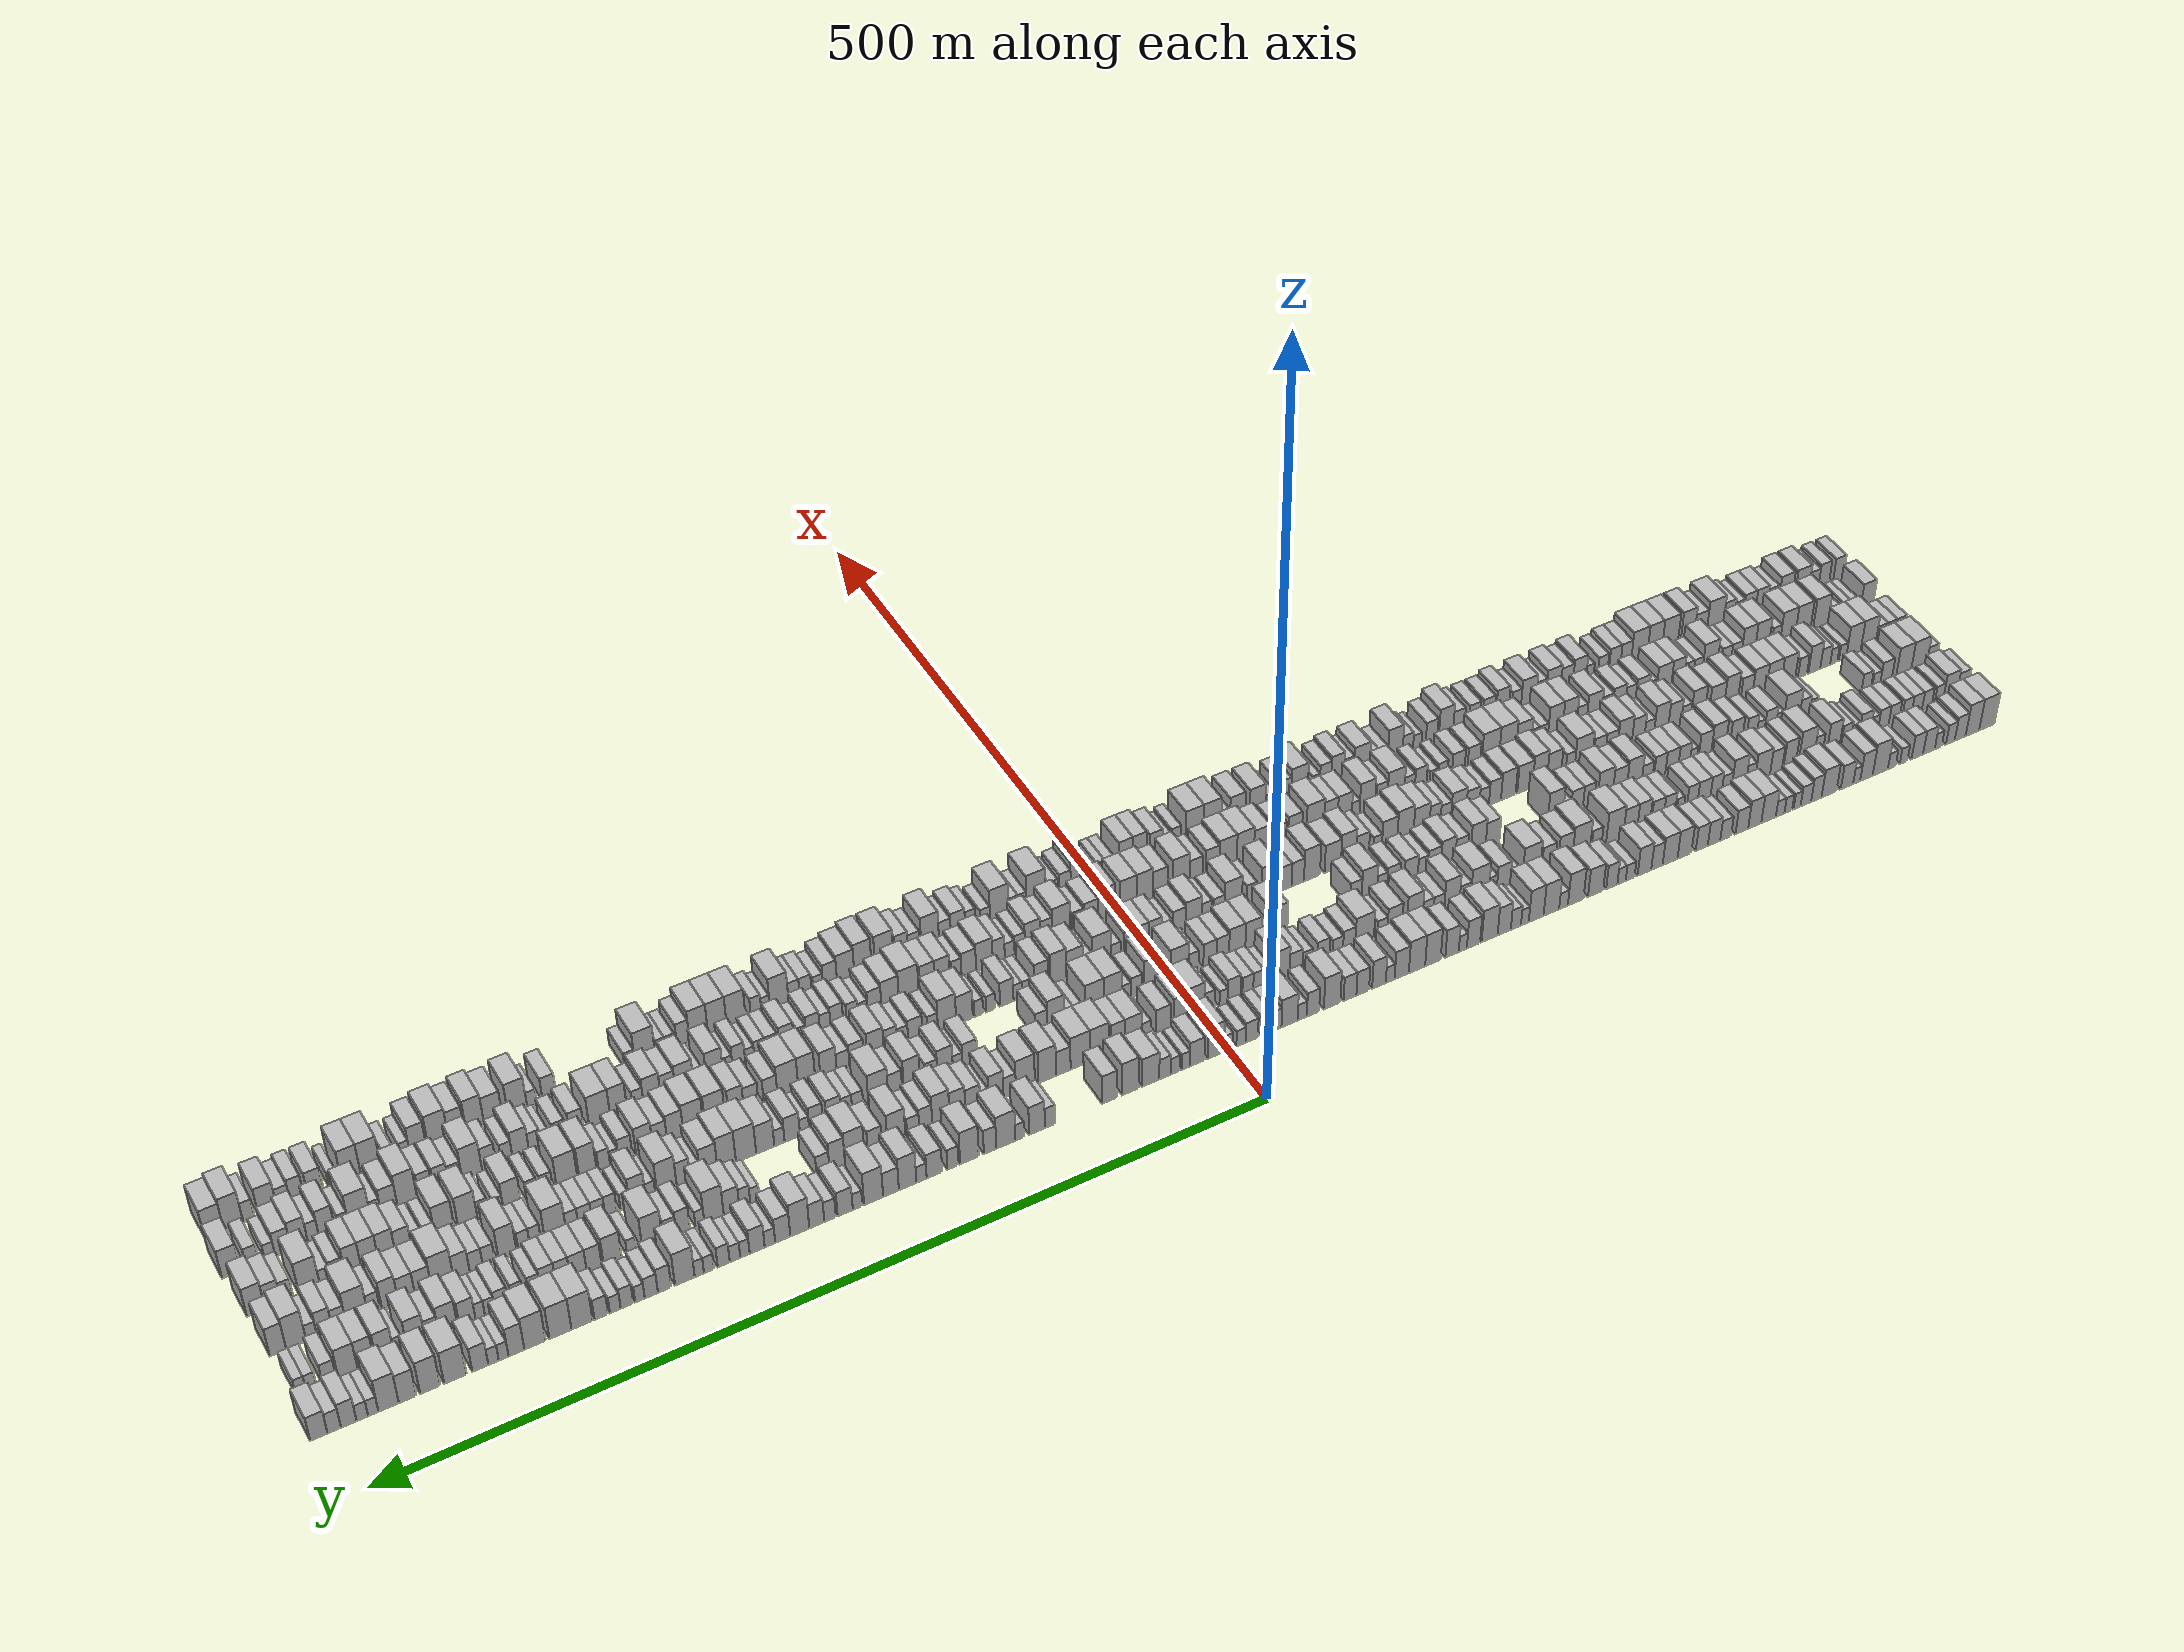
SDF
<sdf version="1.6">
 <world name="default">
  <scene>
   <sky><clouds><speed>12</speed></clouds></sky>
   <ambient>0.4 0.4 0.4 1</ambient>
   <background>0.7 0.7 0.7 1</background>
   <shadows>1</shadows>
  </scene>
  <gravity>0 0 -9.8066</gravity>
  <magnetic_field>6e-06 2.3e-05 -4.2e-05</magnetic_field>
  <physics default="0" name="default_physics" type="ode">
   <ode>
    <solver>
     <type>quick</type>
     <iters>10</iters>
     <sor>1.0</sor>
     <use_dynamic_moi_rescaling>0</use_dynamic_moi_rescaling>
    </solver>
    <constraints>
     <cfm>0</cfm>
     <erp>0.2</erp>
     <contact_max_correcting_vel>100</contact_max_correcting_vel>
     <contact_surface_layer>0.001</contact_surface_layer>
    </constraints>
   </ode>
   <max_step_size>0.004</max_step_size>
   <real_time_factor>1</real_time_factor>
   <real_time_update_rate>250</real_time_update_rate>
  </physics>
  <light name="sun" type="directional">
   <pose>0 0 10 0 0 0</pose>
   <diffuse>0.8 0.8 0.8 1</diffuse>
   <specular>0.2 0.2 0.2 1</specular>
   <attenuation>
    <range>1000</range>
    <constant>0.9</constant>
    <linear>0.01</linear>
    <quadratic>0.001</quadratic>
   </attenuation>
   <direction>-0.5 0.1 -0.9</direction>
  </light>
  <model name="building_1">
   <static>1</static>
   <pose>50.0000 -501.5181 0 0.000000 0.000000 0.000000</pose>
   <link name="link">
    <pose>0 0 12.00 0 0 0</pose>
    <collision name="collision"><geometry><box><size>20.0000 10.9638 24.0000</size></box></geometry></collision>
    <visual name="visual">
     <cast_shadows>0</cast_shadows>
     <geometry><box><size>20.0000 10.9638 24.0000</size></box></geometry>
     <material>
      <script>
       <uri>model://HANNAS_wall/materials/scripts</uri>
       <uri>model://HANNAS_wall/materials/textures</uri>
       <name>vrc/HANNAS_wall</name>
      </script>
     </material>
    </visual>
   </link>
  </model>
  <model name="building_2">
   <static>1</static>
   <pose>50.0000 -491.1854 0 0.000000 0.000000 0.000000</pose>
   <link name="link">
    <pose>0 0 12.00 0 0 0</pose>
    <collision name="collision"><geometry><box><size>20.0000 9.7015 24.0000</size></box></geometry></collision>
    <visual name="visual">
     <cast_shadows>0</cast_shadows>
     <geometry><box><size>20.0000 9.7015 24.0000</size></box></geometry>
     <material>
      <script>
       <uri>model://HANNAS_wall/materials/scripts</uri>
       <uri>model://HANNAS_wall/materials/textures</uri>
       <name>vrc/HANNAS_wall</name>
      </script>
     </material>
    </visual>
   </link>
  </model>
  <model name="building_3">
   <static>1</static>
   <pose>50.0000 -482.4404 0 0.000000 0.000000 0.000000</pose>
   <link name="link">
    <pose>0 0 9.00 0 0 0</pose>
    <collision name="collision"><geometry><box><size>20.0000 7.7884 18.0000</size></box></geometry></collision>
    <visual name="visual">
     <cast_shadows>0</cast_shadows>
     <geometry><box><size>20.0000 7.7884 18.0000</size></box></geometry>
     <material>
      <script>
       <uri>model://HANNAS_wall/materials/scripts</uri>
       <uri>model://HANNAS_wall/materials/textures</uri>
       <name>vrc/HANNAS_wall</name>
      </script>
     </material>
    </visual>
   </link>
  </model>
  <model name="building_4">
   <static>1</static>
   <pose>50.0000 -475.4470 0 0.000000 0.000000 0.000000</pose>
   <link name="link">
    <pose>0 0 7.50 0 0 0</pose>
    <collision name="collision"><geometry><box><size>20.0000 6.1985 15.0000</size></box></geometry></collision>
    <visual name="visual">
     <cast_shadows>0</cast_shadows>
     <geometry><box><size>20.0000 6.1985 15.0000</size></box></geometry>
     <material>
      <script>
       <uri>model://HANNAS_wall/materials/scripts</uri>
       <uri>model://HANNAS_wall/materials/textures</uri>
       <name>vrc/HANNAS_wall</name>
      </script>
     </material>
    </visual>
   </link>
  </model>
  <model name="building_5">
   <static>1</static>
   <pose>50.0000 -466.8957 0 0.000000 0.000000 0.000000</pose>
   <link name="link">
    <pose>0 0 6.00 0 0 0</pose>
    <collision name="collision"><geometry><box><size>20.0000 4.9040 12.0000</size></box></geometry></collision>
    <visual name="visual">
     <cast_shadows>0</cast_shadows>
     <geometry><box><size>20.0000 4.9040 12.0000</size></box></geometry>
     <material>
      <script>
       <uri>model://HANNAS_wall/materials/scripts</uri>
       <uri>model://HANNAS_wall/materials/textures</uri>
       <name>vrc/HANNAS_wall</name>
      </script>
     </material>
    </visual>
   </link>
  </model>
  <model name="building_6">
   <static>1</static>
   <pose>50.0000 -460.3162 0 0.000000 0.000000 0.000000</pose>
   <link name="link">
    <pose>0 0 9.00 0 0 0</pose>
    <collision name="collision"><geometry><box><size>20.0000 8.2551 18.0000</size></box></geometry></collision>
    <visual name="visual">
     <cast_shadows>0</cast_shadows>
     <geometry><box><size>20.0000 8.2551 18.0000</size></box></geometry>
     <material>
      <script>
       <uri>model://HANNAS_wall/materials/scripts</uri>
       <uri>model://HANNAS_wall/materials/textures</uri>
       <name>vrc/HANNAS_wall</name>
      </script>
     </material>
    </visual>
   </link>
  </model>
  <model name="building_7">
   <static>1</static>
   <pose>50.0000 -452.1298 0 0.000000 0.000000 0.000000</pose>
   <link name="link">
    <pose>0 0 9.00 0 0 0</pose>
    <collision name="collision"><geometry><box><size>20.0000 8.1179 18.0000</size></box></geometry></collision>
    <visual name="visual">
     <cast_shadows>0</cast_shadows>
     <geometry><box><size>20.0000 8.1179 18.0000</size></box></geometry>
     <material>
      <script>
       <uri>model://HANNAS_wall/materials/scripts</uri>
       <uri>model://HANNAS_wall/materials/textures</uri>
       <name>vrc/HANNAS_wall</name>
      </script>
     </material>
    </visual>
   </link>
  </model>
  <model name="building_8">
   <static>1</static>
   <pose>50.0000 -442.4199 0 0.000000 0.000000 0.000000</pose>
   <link name="link">
    <pose>0 0 6.00 0 0 0</pose>
    <collision name="collision"><geometry><box><size>20.0000 5.3018 12.0000</size></box></geometry></collision>
    <visual name="visual">
     <cast_shadows>0</cast_shadows>
     <geometry><box><size>20.0000 5.3018 12.0000</size></box></geometry>
     <material>
      <script>
       <uri>model://HANNAS_wall/materials/scripts</uri>
       <uri>model://HANNAS_wall/materials/textures</uri>
       <name>vrc/HANNAS_wall</name>
      </script>
     </material>
    </visual>
   </link>
  </model>
  <model name="building_9">
   <static>1</static>
   <pose>50.0000 -434.0803 0 0.000000 0.000000 0.000000</pose>
   <link name="link">
    <pose>0 0 6.00 0 0 0</pose>
    <collision name="collision"><geometry><box><size>20.0000 5.3775 12.0000</size></box></geometry></collision>
    <visual name="visual">
     <cast_shadows>0</cast_shadows>
     <geometry><box><size>20.0000 5.3775 12.0000</size></box></geometry>
     <material>
      <script>
       <uri>model://HANNAS_wall/materials/scripts</uri>
       <uri>model://HANNAS_wall/materials/textures</uri>
       <name>vrc/HANNAS_wall</name>
      </script>
     </material>
    </visual>
   </link>
  </model>
  <model name="building_10">
   <static>1</static>
   <pose>50.0000 -426.0683 0 0.000000 0.000000 0.000000</pose>
   <link name="link">
    <pose>0 0 12.00 0 0 0</pose>
    <collision name="collision"><geometry><box><size>20.0000 10.6464 24.0000</size></box></geometry></collision>
    <visual name="visual">
     <cast_shadows>0</cast_shadows>
     <geometry><box><size>20.0000 10.6464 24.0000</size></box></geometry>
     <material>
      <script>
       <uri>model://HANNAS_wall/materials/scripts</uri>
       <uri>model://HANNAS_wall/materials/textures</uri>
       <name>vrc/HANNAS_wall</name>
      </script>
     </material>
    </visual>
   </link>
  </model>
  <model name="building_11">
   <static>1</static>
   <pose>50.0000 -416.3842 0 0.000000 0.000000 0.000000</pose>
   <link name="link">
    <pose>0 0 10.50 0 0 0</pose>
    <collision name="collision"><geometry><box><size>20.0000 8.7219 21.0000</size></box></geometry></collision>
    <visual name="visual">
     <cast_shadows>0</cast_shadows>
     <geometry><box><size>20.0000 8.7219 21.0000</size></box></geometry>
     <material>
      <script>
       <uri>model://HANNAS_wall/materials/scripts</uri>
       <uri>model://HANNAS_wall/materials/textures</uri>
       <name>vrc/HANNAS_wall</name>
      </script>
     </material>
    </visual>
   </link>
  </model>
  <model name="building_12">
   <static>1</static>
   <pose>50.0000 -409.5972 0 0.000000 0.000000 0.000000</pose>
   <link name="link">
    <pose>0 0 6.00 0 0 0</pose>
    <collision name="collision"><geometry><box><size>20.0000 4.8521 12.0000</size></box></geometry></collision>
    <visual name="visual">
     <cast_shadows>0</cast_shadows>
     <geometry><box><size>20.0000 4.8521 12.0000</size></box></geometry>
     <material>
      <script>
       <uri>model://HANNAS_wall/materials/scripts</uri>
       <uri>model://HANNAS_wall/materials/textures</uri>
       <name>vrc/HANNAS_wall</name>
      </script>
     </material>
    </visual>
   </link>
  </model>
  <model name="building_13">
   <static>1</static>
   <pose>50.0000 -402.8632 0 0.000000 0.000000 0.000000</pose>
   <link name="link">
    <pose>0 0 9.00 0 0 0</pose>
    <collision name="collision"><geometry><box><size>20.0000 8.6158 18.0000</size></box></geometry></collision>
    <visual name="visual">
     <cast_shadows>0</cast_shadows>
     <geometry><box><size>20.0000 8.6158 18.0000</size></box></geometry>
     <material>
      <script>
       <uri>model://HANNAS_wall/materials/scripts</uri>
       <uri>model://HANNAS_wall/materials/textures</uri>
       <name>vrc/HANNAS_wall</name>
      </script>
     </material>
    </visual>
   </link>
  </model>
  <model name="building_14">
   <static>1</static>
   <pose>50.0000 -390.3938 0 0.000000 0.000000 0.000000</pose>
   <link name="link">
    <pose>0 0 10.50 0 0 0</pose>
    <collision name="collision"><geometry><box><size>20.0000 10.3229 21.0000</size></box></geometry></collision>
    <visual name="visual">
     <cast_shadows>0</cast_shadows>
     <geometry><box><size>20.0000 10.3229 21.0000</size></box></geometry>
     <material>
      <script>
       <uri>model://HANNAS_wall/materials/scripts</uri>
       <uri>model://HANNAS_wall/materials/textures</uri>
       <name>vrc/HANNAS_wall</name>
      </script>
     </material>
    </visual>
   </link>
  </model>
  <model name="building_15">
   <static>1</static>
   <pose>50.0000 -381.6118 0 0.000000 0.000000 0.000000</pose>
   <link name="link">
    <pose>0 0 9.00 0 0 0</pose>
    <collision name="collision"><geometry><box><size>20.0000 7.2413 18.0000</size></box></geometry></collision>
    <visual name="visual">
     <cast_shadows>0</cast_shadows>
     <geometry><box><size>20.0000 7.2413 18.0000</size></box></geometry>
     <material>
      <script>
       <uri>model://HANNAS_wall/materials/scripts</uri>
       <uri>model://HANNAS_wall/materials/textures</uri>
       <name>vrc/HANNAS_wall</name>
      </script>
     </material>
    </visual>
   </link>
  </model>
  <model name="building_16">
   <static>1</static>
   <pose>50.0000 -374.4007 0 0.000000 0.000000 0.000000</pose>
   <link name="link">
    <pose>0 0 7.50 0 0 0</pose>
    <collision name="collision"><geometry><box><size>20.0000 7.1808 15.0000</size></box></geometry></collision>
    <visual name="visual">
     <cast_shadows>0</cast_shadows>
     <geometry><box><size>20.0000 7.1808 15.0000</size></box></geometry>
     <material>
      <script>
       <uri>model://HANNAS_wall/materials/scripts</uri>
       <uri>model://HANNAS_wall/materials/textures</uri>
       <name>vrc/HANNAS_wall</name>
      </script>
     </material>
    </visual>
   </link>
  </model>
  <model name="building_17">
   <static>1</static>
   <pose>50.0000 -368.3718 0 0.000000 0.000000 0.000000</pose>
   <link name="link">
    <pose>0 0 6.00 0 0 0</pose>
    <collision name="collision"><geometry><box><size>20.0000 4.8771 12.0000</size></box></geometry></collision>
    <visual name="visual">
     <cast_shadows>0</cast_shadows>
     <geometry><box><size>20.0000 4.8771 12.0000</size></box></geometry>
     <material>
      <script>
       <uri>model://HANNAS_wall/materials/scripts</uri>
       <uri>model://HANNAS_wall/materials/textures</uri>
       <name>vrc/HANNAS_wall</name>
      </script>
     </material>
    </visual>
   </link>
  </model>
  <model name="building_18">
   <static>1</static>
   <pose>50.0000 -362.2964 0 0.000000 0.000000 0.000000</pose>
   <link name="link">
    <pose>0 0 6.00 0 0 0</pose>
    <collision name="collision"><geometry><box><size>20.0000 5.2736 12.0000</size></box></geometry></collision>
    <visual name="visual">
     <cast_shadows>0</cast_shadows>
     <geometry><box><size>20.0000 5.2736 12.0000</size></box></geometry>
     <material>
      <script>
       <uri>model://HANNAS_wall/materials/scripts</uri>
       <uri>model://HANNAS_wall/materials/textures</uri>
       <name>vrc/HANNAS_wall</name>
      </script>
     </material>
    </visual>
   </link>
  </model>
  <model name="building_19">
   <static>1</static>
   <pose>50.0000 -356.7223 0 0.000000 0.000000 0.000000</pose>
   <link name="link">
    <pose>0 0 6.00 0 0 0</pose>
    <collision name="collision"><geometry><box><size>20.0000 5.8747 12.0000</size></box></geometry></collision>
    <visual name="visual">
     <cast_shadows>0</cast_shadows>
     <geometry><box><size>20.0000 5.8747 12.0000</size></box></geometry>
     <material>
      <script>
       <uri>model://HANNAS_wall/materials/scripts</uri>
       <uri>model://HANNAS_wall/materials/textures</uri>
       <name>vrc/HANNAS_wall</name>
      </script>
     </material>
    </visual>
   </link>
  </model>
  <model name="building_20">
   <static>1</static>
   <pose>50.0000 -348.7976 0 0.000000 0.000000 0.000000</pose>
   <link name="link">
    <pose>0 0 10.50 0 0 0</pose>
    <collision name="collision"><geometry><box><size>20.0000 9.9748 21.0000</size></box></geometry></collision>
    <visual name="visual">
     <cast_shadows>0</cast_shadows>
     <geometry><box><size>20.0000 9.9748 21.0000</size></box></geometry>
     <material>
      <script>
       <uri>model://HANNAS_wall/materials/scripts</uri>
       <uri>model://HANNAS_wall/materials/textures</uri>
       <name>vrc/HANNAS_wall</name>
      </script>
     </material>
    </visual>
   </link>
  </model>
  <model name="building_21">
   <static>1</static>
   <pose>50.0000 -339.3319 0 0.000000 0.000000 0.000000</pose>
   <link name="link">
    <pose>0 0 10.50 0 0 0</pose>
    <collision name="collision"><geometry><box><size>20.0000 8.9566 21.0000</size></box></geometry></collision>
    <visual name="visual">
     <cast_shadows>0</cast_shadows>
     <geometry><box><size>20.0000 8.9566 21.0000</size></box></geometry>
     <material>
      <script>
       <uri>model://HANNAS_wall/materials/scripts</uri>
       <uri>model://HANNAS_wall/materials/textures</uri>
       <name>vrc/HANNAS_wall</name>
      </script>
     </material>
    </visual>
   </link>
  </model>
  <model name="building_22">
   <static>1</static>
   <pose>50.0000 -330.5562 0 0.000000 0.000000 0.000000</pose>
   <link name="link">
    <pose>0 0 9.00 0 0 0</pose>
    <collision name="collision"><geometry><box><size>20.0000 8.5948 18.0000</size></box></geometry></collision>
    <visual name="visual">
     <cast_shadows>0</cast_shadows>
     <geometry><box><size>20.0000 8.5948 18.0000</size></box></geometry>
     <material>
      <script>
       <uri>model://HANNAS_wall/materials/scripts</uri>
       <uri>model://HANNAS_wall/materials/textures</uri>
       <name>vrc/HANNAS_wall</name>
      </script>
     </material>
    </visual>
   </link>
  </model>
  <model name="building_23">
   <static>1</static>
   <pose>50.0000 -319.5803 0 0.000000 0.000000 0.000000</pose>
   <link name="link">
    <pose>0 0 7.50 0 0 0</pose>
    <collision name="collision"><geometry><box><size>20.0000 7.3570 15.0000</size></box></geometry></collision>
    <visual name="visual">
     <cast_shadows>0</cast_shadows>
     <geometry><box><size>20.0000 7.3570 15.0000</size></box></geometry>
     <material>
      <script>
       <uri>model://HANNAS_wall/materials/scripts</uri>
       <uri>model://HANNAS_wall/materials/textures</uri>
       <name>vrc/HANNAS_wall</name>
      </script>
     </material>
    </visual>
   </link>
  </model>
  <model name="building_24">
   <static>1</static>
   <pose>50.0000 -311.7137 0 0.000000 0.000000 0.000000</pose>
   <link name="link">
    <pose>0 0 9.00 0 0 0</pose>
    <collision name="collision"><geometry><box><size>20.0000 8.3763 18.0000</size></box></geometry></collision>
    <visual name="visual">
     <cast_shadows>0</cast_shadows>
     <geometry><box><size>20.0000 8.3763 18.0000</size></box></geometry>
     <material>
      <script>
       <uri>model://HANNAS_wall/materials/scripts</uri>
       <uri>model://HANNAS_wall/materials/textures</uri>
       <name>vrc/HANNAS_wall</name>
      </script>
     </material>
    </visual>
   </link>
  </model>
  <model name="building_25">
   <static>1</static>
   <pose>50.0000 -303.4869 0 0.000000 0.000000 0.000000</pose>
   <link name="link">
    <pose>0 0 9.00 0 0 0</pose>
    <collision name="collision"><geometry><box><size>20.0000 8.0773 18.0000</size></box></geometry></collision>
    <visual name="visual">
     <cast_shadows>0</cast_shadows>
     <geometry><box><size>20.0000 8.0773 18.0000</size></box></geometry>
     <material>
      <script>
       <uri>model://HANNAS_wall/materials/scripts</uri>
       <uri>model://HANNAS_wall/materials/textures</uri>
       <name>vrc/HANNAS_wall</name>
      </script>
     </material>
    </visual>
   </link>
  </model>
  <model name="building_26">
   <static>1</static>
   <pose>50.0000 -291.7953 0 0.000000 0.000000 0.000000</pose>
   <link name="link">
    <pose>0 0 10.50 0 0 0</pose>
    <collision name="collision"><geometry><box><size>20.0000 9.3060 21.0000</size></box></geometry></collision>
    <visual name="visual">
     <cast_shadows>0</cast_shadows>
     <geometry><box><size>20.0000 9.3060 21.0000</size></box></geometry>
     <material>
      <script>
       <uri>model://HANNAS_wall/materials/scripts</uri>
       <uri>model://HANNAS_wall/materials/textures</uri>
       <name>vrc/HANNAS_wall</name>
      </script>
     </material>
    </visual>
   </link>
  </model>
  <model name="building_27">
   <static>1</static>
   <pose>50.0000 -282.1680 0 0.000000 0.000000 0.000000</pose>
   <link name="link">
    <pose>0 0 10.50 0 0 0</pose>
    <collision name="collision"><geometry><box><size>20.0000 9.9487 21.0000</size></box></geometry></collision>
    <visual name="visual">
     <cast_shadows>0</cast_shadows>
     <geometry><box><size>20.0000 9.9487 21.0000</size></box></geometry>
     <material>
      <script>
       <uri>model://HANNAS_wall/materials/scripts</uri>
       <uri>model://HANNAS_wall/materials/textures</uri>
       <name>vrc/HANNAS_wall</name>
      </script>
     </material>
    </visual>
   </link>
  </model>
  <model name="building_28">
   <static>1</static>
   <pose>50.0000 -273.3792 0 0.000000 0.000000 0.000000</pose>
   <link name="link">
    <pose>0 0 9.00 0 0 0</pose>
    <collision name="collision"><geometry><box><size>20.0000 7.6288 18.0000</size></box></geometry></collision>
    <visual name="visual">
     <cast_shadows>0</cast_shadows>
     <geometry><box><size>20.0000 7.6288 18.0000</size></box></geometry>
     <material>
      <script>
       <uri>model://HANNAS_wall/materials/scripts</uri>
       <uri>model://HANNAS_wall/materials/textures</uri>
       <name>vrc/HANNAS_wall</name>
      </script>
     </material>
    </visual>
   </link>
  </model>
  <model name="building_29">
   <static>1</static>
   <pose>50.0000 -265.0334 0 0.000000 0.000000 0.000000</pose>
   <link name="link">
    <pose>0 0 10.50 0 0 0</pose>
    <collision name="collision"><geometry><box><size>20.0000 9.0628 21.0000</size></box></geometry></collision>
    <visual name="visual">
     <cast_shadows>0</cast_shadows>
     <geometry><box><size>20.0000 9.0628 21.0000</size></box></geometry>
     <material>
      <script>
       <uri>model://HANNAS_wall/materials/scripts</uri>
       <uri>model://HANNAS_wall/materials/textures</uri>
       <name>vrc/HANNAS_wall</name>
      </script>
     </material>
    </visual>
   </link>
  </model>
  <model name="building_30">
   <static>1</static>
   <pose>50.0000 -255.5705 0 0.000000 0.000000 0.000000</pose>
   <link name="link">
    <pose>0 0 6.00 0 0 0</pose>
    <collision name="collision"><geometry><box><size>20.0000 5.8630 12.0000</size></box></geometry></collision>
    <visual name="visual">
     <cast_shadows>0</cast_shadows>
     <geometry><box><size>20.0000 5.8630 12.0000</size></box></geometry>
     <material>
      <script>
       <uri>model://HANNAS_wall/materials/scripts</uri>
       <uri>model://HANNAS_wall/materials/textures</uri>
       <name>vrc/HANNAS_wall</name>
      </script>
     </material>
    </visual>
   </link>
  </model>
  <model name="building_31">
   <static>1</static>
   <pose>50.0000 -249.8530 0 0.000000 0.000000 0.000000</pose>
   <link name="link">
    <pose>0 0 6.00 0 0 0</pose>
    <collision name="collision"><geometry><box><size>20.0000 5.5720 12.0000</size></box></geometry></collision>
    <visual name="visual">
     <cast_shadows>0</cast_shadows>
     <geometry><box><size>20.0000 5.5720 12.0000</size></box></geometry>
     <material>
      <script>
       <uri>model://HANNAS_wall/materials/scripts</uri>
       <uri>model://HANNAS_wall/materials/textures</uri>
       <name>vrc/HANNAS_wall</name>
      </script>
     </material>
    </visual>
   </link>
  </model>
  <model name="building_32">
   <static>1</static>
   <pose>50.0000 -243.3581 0 0.000000 0.000000 0.000000</pose>
   <link name="link">
    <pose>0 0 9.00 0 0 0</pose>
    <collision name="collision"><geometry><box><size>20.0000 7.4179 18.0000</size></box></geometry></collision>
    <visual name="visual">
     <cast_shadows>0</cast_shadows>
     <geometry><box><size>20.0000 7.4179 18.0000</size></box></geometry>
     <material>
      <script>
       <uri>model://HANNAS_wall/materials/scripts</uri>
       <uri>model://HANNAS_wall/materials/textures</uri>
       <name>vrc/HANNAS_wall</name>
      </script>
     </material>
    </visual>
   </link>
  </model>
  <model name="building_33">
   <static>1</static>
   <pose>50.0000 -232.6826 0 0.000000 0.000000 0.000000</pose>
   <link name="link">
    <pose>0 0 10.50 0 0 0</pose>
    <collision name="collision"><geometry><box><size>20.0000 9.9332 21.0000</size></box></geometry></collision>
    <visual name="visual">
     <cast_shadows>0</cast_shadows>
     <geometry><box><size>20.0000 9.9332 21.0000</size></box></geometry>
     <material>
      <script>
       <uri>model://HANNAS_wall/materials/scripts</uri>
       <uri>model://HANNAS_wall/materials/textures</uri>
       <name>vrc/HANNAS_wall</name>
      </script>
     </material>
    </visual>
   </link>
  </model>
  <model name="building_34">
   <static>1</static>
   <pose>50.0000 -219.5905 0 0.000000 0.000000 0.000000</pose>
   <link name="link">
    <pose>0 0 12.00 0 0 0</pose>
    <collision name="collision"><geometry><box><size>20.0000 10.2508 24.0000</size></box></geometry></collision>
    <visual name="visual">
     <cast_shadows>0</cast_shadows>
     <geometry><box><size>20.0000 10.2508 24.0000</size></box></geometry>
     <material>
      <script>
       <uri>model://HANNAS_wall/materials/scripts</uri>
       <uri>model://HANNAS_wall/materials/textures</uri>
       <name>vrc/HANNAS_wall</name>
      </script>
     </material>
    </visual>
   </link>
  </model>
  <model name="building_35">
   <static>1</static>
   <pose>50.0000 -211.6037 0 0.000000 0.000000 0.000000</pose>
   <link name="link">
    <pose>0 0 6.00 0 0 0</pose>
    <collision name="collision"><geometry><box><size>20.0000 5.7229 12.0000</size></box></geometry></collision>
    <visual name="visual">
     <cast_shadows>0</cast_shadows>
     <geometry><box><size>20.0000 5.7229 12.0000</size></box></geometry>
     <material>
      <script>
       <uri>model://HANNAS_wall/materials/scripts</uri>
       <uri>model://HANNAS_wall/materials/textures</uri>
       <name>vrc/HANNAS_wall</name>
      </script>
     </material>
    </visual>
   </link>
  </model>
  <model name="building_36">
   <static>1</static>
   <pose>50.0000 -203.6641 0 0.000000 0.000000 0.000000</pose>
   <link name="link">
    <pose>0 0 12.00 0 0 0</pose>
    <collision name="collision"><geometry><box><size>20.0000 10.1561 24.0000</size></box></geometry></collision>
    <visual name="visual">
     <cast_shadows>0</cast_shadows>
     <geometry><box><size>20.0000 10.1561 24.0000</size></box></geometry>
     <material>
      <script>
       <uri>model://HANNAS_wall/materials/scripts</uri>
       <uri>model://HANNAS_wall/materials/textures</uri>
       <name>vrc/HANNAS_wall</name>
      </script>
     </material>
    </visual>
   </link>
  </model>
  <model name="building_37">
   <static>1</static>
   <pose>50.0000 -193.7768 0 0.000000 0.000000 0.000000</pose>
   <link name="link">
    <pose>0 0 12.00 0 0 0</pose>
    <collision name="collision"><geometry><box><size>20.0000 9.6187 24.0000</size></box></geometry></collision>
    <visual name="visual">
     <cast_shadows>0</cast_shadows>
     <geometry><box><size>20.0000 9.6187 24.0000</size></box></geometry>
     <material>
      <script>
       <uri>model://HANNAS_wall/materials/scripts</uri>
       <uri>model://HANNAS_wall/materials/textures</uri>
       <name>vrc/HANNAS_wall</name>
      </script>
     </material>
    </visual>
   </link>
  </model>
  <model name="building_38">
   <static>1</static>
   <pose>50.0000 -186.4052 0 0.000000 0.000000 0.000000</pose>
   <link name="link">
    <pose>0 0 6.00 0 0 0</pose>
    <collision name="collision"><geometry><box><size>20.0000 5.1245 12.0000</size></box></geometry></collision>
    <visual name="visual">
     <cast_shadows>0</cast_shadows>
     <geometry><box><size>20.0000 5.1245 12.0000</size></box></geometry>
     <material>
      <script>
       <uri>model://HANNAS_wall/materials/scripts</uri>
       <uri>model://HANNAS_wall/materials/textures</uri>
       <name>vrc/HANNAS_wall</name>
      </script>
     </material>
    </visual>
   </link>
  </model>
  <model name="building_39">
   <static>1</static>
   <pose>50.0000 -180.5579 0 0.000000 0.000000 0.000000</pose>
   <link name="link">
    <pose>0 0 7.50 0 0 0</pose>
    <collision name="collision"><geometry><box><size>20.0000 6.5701 15.0000</size></box></geometry></collision>
    <visual name="visual">
     <cast_shadows>0</cast_shadows>
     <geometry><box><size>20.0000 6.5701 15.0000</size></box></geometry>
     <material>
      <script>
       <uri>model://HANNAS_wall/materials/scripts</uri>
       <uri>model://HANNAS_wall/materials/textures</uri>
       <name>vrc/HANNAS_wall</name>
      </script>
     </material>
    </visual>
   </link>
  </model>
  <model name="building_40">
   <static>1</static>
   <pose>50.0000 -173.0076 0 0.000000 0.000000 0.000000</pose>
   <link name="link">
    <pose>0 0 10.50 0 0 0</pose>
    <collision name="collision"><geometry><box><size>20.0000 8.5306 21.0000</size></box></geometry></collision>
    <visual name="visual">
     <cast_shadows>0</cast_shadows>
     <geometry><box><size>20.0000 8.5306 21.0000</size></box></geometry>
     <material>
      <script>
       <uri>model://HANNAS_wall/materials/scripts</uri>
       <uri>model://HANNAS_wall/materials/textures</uri>
       <name>vrc/HANNAS_wall</name>
      </script>
     </material>
    </visual>
   </link>
  </model>
  <model name="building_41">
   <static>1</static>
   <pose>50.0000 -163.5885 0 0.000000 0.000000 0.000000</pose>
   <link name="link">
    <pose>0 0 12.00 0 0 0</pose>
    <collision name="collision"><geometry><box><size>20.0000 10.3076 24.0000</size></box></geometry></collision>
    <visual name="visual">
     <cast_shadows>0</cast_shadows>
     <geometry><box><size>20.0000 10.3076 24.0000</size></box></geometry>
     <material>
      <script>
       <uri>model://HANNAS_wall/materials/scripts</uri>
       <uri>model://HANNAS_wall/materials/textures</uri>
       <name>vrc/HANNAS_wall</name>
      </script>
     </material>
    </visual>
   </link>
  </model>
  <model name="building_42">
   <static>1</static>
   <pose>50.0000 -153.1997 0 0.000000 0.000000 0.000000</pose>
   <link name="link">
    <pose>0 0 10.50 0 0 0</pose>
    <collision name="collision"><geometry><box><size>20.0000 8.4700 21.0000</size></box></geometry></collision>
    <visual name="visual">
     <cast_shadows>0</cast_shadows>
     <geometry><box><size>20.0000 8.4700 21.0000</size></box></geometry>
     <material>
      <script>
       <uri>model://HANNAS_wall/materials/scripts</uri>
       <uri>model://HANNAS_wall/materials/textures</uri>
       <name>vrc/HANNAS_wall</name>
      </script>
     </material>
    </visual>
   </link>
  </model>
  <model name="building_43">
   <static>1</static>
   <pose>50.0000 -146.3598 0 0.000000 0.000000 0.000000</pose>
   <link name="link">
    <pose>0 0 6.00 0 0 0</pose>
    <collision name="collision"><geometry><box><size>20.0000 5.2099 12.0000</size></box></geometry></collision>
    <visual name="visual">
     <cast_shadows>0</cast_shadows>
     <geometry><box><size>20.0000 5.2099 12.0000</size></box></geometry>
     <material>
      <script>
       <uri>model://HANNAS_wall/materials/scripts</uri>
       <uri>model://HANNAS_wall/materials/textures</uri>
       <name>vrc/HANNAS_wall</name>
      </script>
     </material>
    </visual>
   </link>
  </model>
  <model name="building_44">
   <static>1</static>
   <pose>50.0000 -139.4693 0 0.000000 0.000000 0.000000</pose>
   <link name="link">
    <pose>0 0 10.50 0 0 0</pose>
    <collision name="collision"><geometry><box><size>20.0000 8.5711 21.0000</size></box></geometry></collision>
    <visual name="visual">
     <cast_shadows>0</cast_shadows>
     <geometry><box><size>20.0000 8.5711 21.0000</size></box></geometry>
     <material>
      <script>
       <uri>model://HANNAS_wall/materials/scripts</uri>
       <uri>model://HANNAS_wall/materials/textures</uri>
       <name>vrc/HANNAS_wall</name>
      </script>
     </material>
    </visual>
   </link>
  </model>
  <model name="building_45">
   <static>1</static>
   <pose>50.0000 -127.2410 0 0.000000 0.000000 0.000000</pose>
   <link name="link">
    <pose>0 0 12.00 0 0 0</pose>
    <collision name="collision"><geometry><box><size>20.0000 9.8855 24.0000</size></box></geometry></collision>
    <visual name="visual">
     <cast_shadows>0</cast_shadows>
     <geometry><box><size>20.0000 9.8855 24.0000</size></box></geometry>
     <material>
      <script>
       <uri>model://HANNAS_wall/materials/scripts</uri>
       <uri>model://HANNAS_wall/materials/textures</uri>
       <name>vrc/HANNAS_wall</name>
      </script>
     </material>
    </visual>
   </link>
  </model>
  <model name="building_46">
   <static>1</static>
   <pose>50.0000 -117.1300 0 0.000000 0.000000 0.000000</pose>
   <link name="link">
    <pose>0 0 12.00 0 0 0</pose>
    <collision name="collision"><geometry><box><size>20.0000 10.3366 24.0000</size></box></geometry></collision>
    <visual name="visual">
     <cast_shadows>0</cast_shadows>
     <geometry><box><size>20.0000 10.3366 24.0000</size></box></geometry>
     <material>
      <script>
       <uri>model://HANNAS_wall/materials/scripts</uri>
       <uri>model://HANNAS_wall/materials/textures</uri>
       <name>vrc/HANNAS_wall</name>
      </script>
     </material>
    </visual>
   </link>
  </model>
  <model name="building_47">
   <static>1</static>
   <pose>50.0000 -107.4561 0 0.000000 0.000000 0.000000</pose>
   <link name="link">
    <pose>0 0 10.50 0 0 0</pose>
    <collision name="collision"><geometry><box><size>20.0000 9.0112 21.0000</size></box></geometry></collision>
    <visual name="visual">
     <cast_shadows>0</cast_shadows>
     <geometry><box><size>20.0000 9.0112 21.0000</size></box></geometry>
     <material>
      <script>
       <uri>model://HANNAS_wall/materials/scripts</uri>
       <uri>model://HANNAS_wall/materials/textures</uri>
       <name>vrc/HANNAS_wall</name>
      </script>
     </material>
    </visual>
   </link>
  </model>
  <model name="building_48">
   <static>1</static>
   <pose>50.0000 -100.1588 0 0.000000 0.000000 0.000000</pose>
   <link name="link">
    <pose>0 0 6.00 0 0 0</pose>
    <collision name="collision"><geometry><box><size>20.0000 5.5834 12.0000</size></box></geometry></collision>
    <visual name="visual">
     <cast_shadows>0</cast_shadows>
     <geometry><box><size>20.0000 5.5834 12.0000</size></box></geometry>
     <material>
      <script>
       <uri>model://HANNAS_wall/materials/scripts</uri>
       <uri>model://HANNAS_wall/materials/textures</uri>
       <name>vrc/HANNAS_wall</name>
      </script>
     </material>
    </visual>
   </link>
  </model>
  <model name="building_49">
   <static>1</static>
   <pose>50.0000 -93.0709 0 0.000000 0.000000 0.000000</pose>
   <link name="link">
    <pose>0 0 10.50 0 0 0</pose>
    <collision name="collision"><geometry><box><size>20.0000 8.5924 21.0000</size></box></geometry></collision>
    <visual name="visual">
     <cast_shadows>0</cast_shadows>
     <geometry><box><size>20.0000 8.5924 21.0000</size></box></geometry>
     <material>
      <script>
       <uri>model://HANNAS_wall/materials/scripts</uri>
       <uri>model://HANNAS_wall/materials/textures</uri>
       <name>vrc/HANNAS_wall</name>
      </script>
     </material>
    </visual>
   </link>
  </model>
  <model name="building_50">
   <static>1</static>
   <pose>50.0000 -82.8225 0 0.000000 0.000000 0.000000</pose>
   <link name="link">
    <pose>0 0 9.00 0 0 0</pose>
    <collision name="collision"><geometry><box><size>20.0000 7.9045 18.0000</size></box></geometry></collision>
    <visual name="visual">
     <cast_shadows>0</cast_shadows>
     <geometry><box><size>20.0000 7.9045 18.0000</size></box></geometry>
     <material>
      <script>
       <uri>model://HANNAS_wall/materials/scripts</uri>
       <uri>model://HANNAS_wall/materials/textures</uri>
       <name>vrc/HANNAS_wall</name>
      </script>
     </material>
    </visual>
   </link>
  </model>
  <model name="building_51">
   <static>1</static>
   <pose>50.0000 -74.8674 0 0.000000 0.000000 0.000000</pose>
   <link name="link">
    <pose>0 0 9.00 0 0 0</pose>
    <collision name="collision"><geometry><box><size>20.0000 8.0058 18.0000</size></box></geometry></collision>
    <visual name="visual">
     <cast_shadows>0</cast_shadows>
     <geometry><box><size>20.0000 8.0058 18.0000</size></box></geometry>
     <material>
      <script>
       <uri>model://HANNAS_wall/materials/scripts</uri>
       <uri>model://HANNAS_wall/materials/textures</uri>
       <name>vrc/HANNAS_wall</name>
      </script>
     </material>
    </visual>
   </link>
  </model>
  <model name="building_52">
   <static>1</static>
   <pose>50.0000 -63.7128 0 0.000000 0.000000 0.000000</pose>
   <link name="link">
    <pose>0 0 12.00 0 0 0</pose>
    <collision name="collision"><geometry><box><size>20.0000 10.3034 24.0000</size></box></geometry></collision>
    <visual name="visual">
     <cast_shadows>0</cast_shadows>
     <geometry><box><size>20.0000 10.3034 24.0000</size></box></geometry>
     <material>
      <script>
       <uri>model://HANNAS_wall/materials/scripts</uri>
       <uri>model://HANNAS_wall/materials/textures</uri>
       <name>vrc/HANNAS_wall</name>
      </script>
     </material>
    </visual>
   </link>
  </model>
  <model name="building_53">
   <static>1</static>
   <pose>50.0000 -51.7517 0 0.000000 0.000000 0.000000</pose>
   <link name="link">
    <pose>0 0 9.00 0 0 0</pose>
    <collision name="collision"><geometry><box><size>20.0000 7.6187 18.0000</size></box></geometry></collision>
    <visual name="visual">
     <cast_shadows>0</cast_shadows>
     <geometry><box><size>20.0000 7.6187 18.0000</size></box></geometry>
     <material>
      <script>
       <uri>model://HANNAS_wall/materials/scripts</uri>
       <uri>model://HANNAS_wall/materials/textures</uri>
       <name>vrc/HANNAS_wall</name>
      </script>
     </material>
    </visual>
   </link>
  </model>
  <model name="building_54">
   <static>1</static>
   <pose>50.0000 -45.1060 0 0.000000 0.000000 0.000000</pose>
   <link name="link">
    <pose>0 0 6.00 0 0 0</pose>
    <collision name="collision"><geometry><box><size>20.0000 5.6728 12.0000</size></box></geometry></collision>
    <visual name="visual">
     <cast_shadows>0</cast_shadows>
     <geometry><box><size>20.0000 5.6728 12.0000</size></box></geometry>
     <material>
      <script>
       <uri>model://HANNAS_wall/materials/scripts</uri>
       <uri>model://HANNAS_wall/materials/textures</uri>
       <name>vrc/HANNAS_wall</name>
      </script>
     </material>
    </visual>
   </link>
  </model>
  <model name="building_55">
   <static>1</static>
   <pose>50.0000 -37.2330 0 0.000000 0.000000 0.000000</pose>
   <link name="link">
    <pose>0 0 10.50 0 0 0</pose>
    <collision name="collision"><geometry><box><size>20.0000 10.0730 21.0000</size></box></geometry></collision>
    <visual name="visual">
     <cast_shadows>0</cast_shadows>
     <geometry><box><size>20.0000 10.0730 21.0000</size></box></geometry>
     <material>
      <script>
       <uri>model://HANNAS_wall/materials/scripts</uri>
       <uri>model://HANNAS_wall/materials/textures</uri>
       <name>vrc/HANNAS_wall</name>
      </script>
     </material>
    </visual>
   </link>
  </model>
  <model name="building_56">
   <static>1</static>
   <pose>50.0000 -29.1370 0 0.000000 0.000000 0.000000</pose>
   <link name="link">
    <pose>0 0 7.50 0 0 0</pose>
    <collision name="collision"><geometry><box><size>20.0000 6.1190 15.0000</size></box></geometry></collision>
    <visual name="visual">
     <cast_shadows>0</cast_shadows>
     <geometry><box><size>20.0000 6.1190 15.0000</size></box></geometry>
     <material>
      <script>
       <uri>model://HANNAS_wall/materials/scripts</uri>
       <uri>model://HANNAS_wall/materials/textures</uri>
       <name>vrc/HANNAS_wall</name>
      </script>
     </material>
    </visual>
   </link>
  </model>
  <model name="building_57">
   <static>1</static>
   <pose>50.0000 -22.9359 0 0.000000 0.000000 0.000000</pose>
   <link name="link">
    <pose>0 0 7.50 0 0 0</pose>
    <collision name="collision"><geometry><box><size>20.0000 6.2833 15.0000</size></box></geometry></collision>
    <visual name="visual">
     <cast_shadows>0</cast_shadows>
     <geometry><box><size>20.0000 6.2833 15.0000</size></box></geometry>
     <material>
      <script>
       <uri>model://HANNAS_wall/materials/scripts</uri>
       <uri>model://HANNAS_wall/materials/textures</uri>
       <name>vrc/HANNAS_wall</name>
      </script>
     </material>
    </visual>
   </link>
  </model>
  <model name="building_58">
   <static>1</static>
   <pose>50.0000 -14.0874 0 0.000000 0.000000 0.000000</pose>
   <link name="link">
    <pose>0 0 7.50 0 0 0</pose>
    <collision name="collision"><geometry><box><size>20.0000 7.4137 15.0000</size></box></geometry></collision>
    <visual name="visual">
     <cast_shadows>0</cast_shadows>
     <geometry><box><size>20.0000 7.4137 15.0000</size></box></geometry>
     <material>
      <script>
       <uri>model://HANNAS_wall/materials/scripts</uri>
       <uri>model://HANNAS_wall/materials/textures</uri>
       <name>vrc/HANNAS_wall</name>
      </script>
     </material>
    </visual>
   </link>
  </model>
  <model name="building_59">
   <static>1</static>
   <pose>50.0000 -7.4353 0 0.000000 0.000000 0.000000</pose>
   <link name="link">
    <pose>0 0 6.00 0 0 0</pose>
    <collision name="collision"><geometry><box><size>20.0000 5.8906 12.0000</size></box></geometry></collision>
    <visual name="visual">
     <cast_shadows>0</cast_shadows>
     <geometry><box><size>20.0000 5.8906 12.0000</size></box></geometry>
     <material>
      <script>
       <uri>model://HANNAS_wall/materials/scripts</uri>
       <uri>model://HANNAS_wall/materials/textures</uri>
       <name>vrc/HANNAS_wall</name>
      </script>
     </material>
    </visual>
   </link>
  </model>
  <model name="building_60">
   <static>1</static>
   <pose>50.0000 0.0227 0 0.000000 0.000000 0.000000</pose>
   <link name="link">
    <pose>0 0 6.00 0 0 0</pose>
    <collision name="collision"><geometry><box><size>20.0000 5.0254 12.0000</size></box></geometry></collision>
    <visual name="visual">
     <cast_shadows>0</cast_shadows>
     <geometry><box><size>20.0000 5.0254 12.0000</size></box></geometry>
     <material>
      <script>
       <uri>model://HANNAS_wall/materials/scripts</uri>
       <uri>model://HANNAS_wall/materials/textures</uri>
       <name>vrc/HANNAS_wall</name>
      </script>
     </material>
    </visual>
   </link>
  </model>
  <model name="building_61">
   <static>1</static>
   <pose>50.0000 7.7225 0 0.000000 0.000000 0.000000</pose>
   <link name="link">
    <pose>0 0 12.00 0 0 0</pose>
    <collision name="collision"><geometry><box><size>20.0000 10.3742 24.0000</size></box></geometry></collision>
    <visual name="visual">
     <cast_shadows>0</cast_shadows>
     <geometry><box><size>20.0000 10.3742 24.0000</size></box></geometry>
     <material>
      <script>
       <uri>model://HANNAS_wall/materials/scripts</uri>
       <uri>model://HANNAS_wall/materials/textures</uri>
       <name>vrc/HANNAS_wall</name>
      </script>
     </material>
    </visual>
   </link>
  </model>
  <model name="building_62">
   <static>1</static>
   <pose>50.0000 19.2918 0 0.000000 0.000000 0.000000</pose>
   <link name="link">
    <pose>0 0 9.00 0 0 0</pose>
    <collision name="collision"><geometry><box><size>20.0000 8.7645 18.0000</size></box></geometry></collision>
    <visual name="visual">
     <cast_shadows>0</cast_shadows>
     <geometry><box><size>20.0000 8.7645 18.0000</size></box></geometry>
     <material>
      <script>
       <uri>model://HANNAS_wall/materials/scripts</uri>
       <uri>model://HANNAS_wall/materials/textures</uri>
       <name>vrc/HANNAS_wall</name>
      </script>
     </material>
    </visual>
   </link>
  </model>
  <model name="building_63">
   <static>1</static>
   <pose>50.0000 26.1871 0 0.000000 0.000000 0.000000</pose>
   <link name="link">
    <pose>0 0 6.00 0 0 0</pose>
    <collision name="collision"><geometry><box><size>20.0000 5.0260 12.0000</size></box></geometry></collision>
    <visual name="visual">
     <cast_shadows>0</cast_shadows>
     <geometry><box><size>20.0000 5.0260 12.0000</size></box></geometry>
     <material>
      <script>
       <uri>model://HANNAS_wall/materials/scripts</uri>
       <uri>model://HANNAS_wall/materials/textures</uri>
       <name>vrc/HANNAS_wall</name>
      </script>
     </material>
    </visual>
   </link>
  </model>
  <model name="building_64">
   <static>1</static>
   <pose>50.0000 32.4772 0 0.000000 0.000000 0.000000</pose>
   <link name="link">
    <pose>0 0 6.00 0 0 0</pose>
    <collision name="collision"><geometry><box><size>20.0000 5.5542 12.0000</size></box></geometry></collision>
    <visual name="visual">
     <cast_shadows>0</cast_shadows>
     <geometry><box><size>20.0000 5.5542 12.0000</size></box></geometry>
     <material>
      <script>
       <uri>model://HANNAS_wall/materials/scripts</uri>
       <uri>model://HANNAS_wall/materials/textures</uri>
       <name>vrc/HANNAS_wall</name>
      </script>
     </material>
    </visual>
   </link>
  </model>
  <model name="building_65">
   <static>1</static>
   <pose>50.0000 38.7532 0 0.000000 0.000000 0.000000</pose>
   <link name="link">
    <pose>0 0 7.50 0 0 0</pose>
    <collision name="collision"><geometry><box><size>20.0000 6.9978 15.0000</size></box></geometry></collision>
    <visual name="visual">
     <cast_shadows>0</cast_shadows>
     <geometry><box><size>20.0000 6.9978 15.0000</size></box></geometry>
     <material>
      <script>
       <uri>model://HANNAS_wall/materials/scripts</uri>
       <uri>model://HANNAS_wall/materials/textures</uri>
       <name>vrc/HANNAS_wall</name>
      </script>
     </material>
    </visual>
   </link>
  </model>
  <model name="building_66">
   <static>1</static>
   <pose>50.0000 47.3738 0 0.000000 0.000000 0.000000</pose>
   <link name="link">
    <pose>0 0 10.50 0 0 0</pose>
    <collision name="collision"><geometry><box><size>20.0000 10.2433 21.0000</size></box></geometry></collision>
    <visual name="visual">
     <cast_shadows>0</cast_shadows>
     <geometry><box><size>20.0000 10.2433 21.0000</size></box></geometry>
     <material>
      <script>
       <uri>model://HANNAS_wall/materials/scripts</uri>
       <uri>model://HANNAS_wall/materials/textures</uri>
       <name>vrc/HANNAS_wall</name>
      </script>
     </material>
    </visual>
   </link>
  </model>
  <model name="building_67">
   <static>1</static>
   <pose>50.0000 59.5017 0 0.000000 0.000000 0.000000</pose>
   <link name="link">
    <pose>0 0 12.00 0 0 0</pose>
    <collision name="collision"><geometry><box><size>20.0000 10.0125 24.0000</size></box></geometry></collision>
    <visual name="visual">
     <cast_shadows>0</cast_shadows>
     <geometry><box><size>20.0000 10.0125 24.0000</size></box></geometry>
     <material>
      <script>
       <uri>model://HANNAS_wall/materials/scripts</uri>
       <uri>model://HANNAS_wall/materials/textures</uri>
       <name>vrc/HANNAS_wall</name>
      </script>
     </material>
    </visual>
   </link>
  </model>
  <model name="building_68">
   <static>1</static>
   <pose>50.0000 71.9700 0 0.000000 0.000000 0.000000</pose>
   <link name="link">
    <pose>0 0 10.50 0 0 0</pose>
    <collision name="collision"><geometry><box><size>20.0000 8.9242 21.0000</size></box></geometry></collision>
    <visual name="visual">
     <cast_shadows>0</cast_shadows>
     <geometry><box><size>20.0000 8.9242 21.0000</size></box></geometry>
     <material>
      <script>
       <uri>model://HANNAS_wall/materials/scripts</uri>
       <uri>model://HANNAS_wall/materials/textures</uri>
       <name>vrc/HANNAS_wall</name>
      </script>
     </material>
    </visual>
   </link>
  </model>
  <model name="building_69">
   <static>1</static>
   <pose>50.0000 107.4569 0 0.000000 0.000000 0.000000</pose>
   <link name="link">
    <pose>0 0 7.50 0 0 0</pose>
    <collision name="collision"><geometry><box><size>20.0000 6.0165 15.0000</size></box></geometry></collision>
    <visual name="visual">
     <cast_shadows>0</cast_shadows>
     <geometry><box><size>20.0000 6.0165 15.0000</size></box></geometry>
     <material>
      <script>
       <uri>model://HANNAS_wall/materials/scripts</uri>
       <uri>model://HANNAS_wall/materials/textures</uri>
       <name>vrc/HANNAS_wall</name>
      </script>
     </material>
    </visual>
   </link>
  </model>
  <model name="building_70">
   <static>1</static>
   <pose>50.0000 115.1150 0 0.000000 0.000000 0.000000</pose>
   <link name="link">
    <pose>0 0 10.50 0 0 0</pose>
    <collision name="collision"><geometry><box><size>20.0000 9.2997 21.0000</size></box></geometry></collision>
    <visual name="visual">
     <cast_shadows>0</cast_shadows>
     <geometry><box><size>20.0000 9.2997 21.0000</size></box></geometry>
     <material>
      <script>
       <uri>model://HANNAS_wall/materials/scripts</uri>
       <uri>model://HANNAS_wall/materials/textures</uri>
       <name>vrc/HANNAS_wall</name>
      </script>
     </material>
    </visual>
   </link>
  </model>
  <model name="building_71">
   <static>1</static>
   <pose>50.0000 125.2679 0 0.000000 0.000000 0.000000</pose>
   <link name="link">
    <pose>0 0 6.00 0 0 0</pose>
    <collision name="collision"><geometry><box><size>20.0000 5.0061 12.0000</size></box></geometry></collision>
    <visual name="visual">
     <cast_shadows>0</cast_shadows>
     <geometry><box><size>20.0000 5.0061 12.0000</size></box></geometry>
     <material>
      <script>
       <uri>model://HANNAS_wall/materials/scripts</uri>
       <uri>model://HANNAS_wall/materials/textures</uri>
       <name>vrc/HANNAS_wall</name>
      </script>
     </material>
    </visual>
   </link>
  </model>
  <model name="building_72">
   <static>1</static>
   <pose>50.0000 133.3773 0 0.000000 0.000000 0.000000</pose>
   <link name="link">
    <pose>0 0 12.00 0 0 0</pose>
    <collision name="collision"><geometry><box><size>20.0000 11.2127 24.0000</size></box></geometry></collision>
    <visual name="visual">
     <cast_shadows>0</cast_shadows>
     <geometry><box><size>20.0000 11.2127 24.0000</size></box></geometry>
     <material>
      <script>
       <uri>model://HANNAS_wall/materials/scripts</uri>
       <uri>model://HANNAS_wall/materials/textures</uri>
       <name>vrc/HANNAS_wall</name>
      </script>
     </material>
    </visual>
   </link>
  </model>
  <model name="building_73">
   <static>1</static>
   <pose>50.0000 142.6111 0 0.000000 0.000000 0.000000</pose>
   <link name="link">
    <pose>0 0 9.00 0 0 0</pose>
    <collision name="collision"><geometry><box><size>20.0000 7.2549 18.0000</size></box></geometry></collision>
    <visual name="visual">
     <cast_shadows>0</cast_shadows>
     <geometry><box><size>20.0000 7.2549 18.0000</size></box></geometry>
     <material>
      <script>
       <uri>model://HANNAS_wall/materials/scripts</uri>
       <uri>model://HANNAS_wall/materials/textures</uri>
       <name>vrc/HANNAS_wall</name>
      </script>
     </material>
    </visual>
   </link>
  </model>
  <model name="building_74">
   <static>1</static>
   <pose>50.0000 154.6305 0 0.000000 0.000000 0.000000</pose>
   <link name="link">
    <pose>0 0 12.00 0 0 0</pose>
    <collision name="collision"><geometry><box><size>20.0000 10.7839 24.0000</size></box></geometry></collision>
    <visual name="visual">
     <cast_shadows>0</cast_shadows>
     <geometry><box><size>20.0000 10.7839 24.0000</size></box></geometry>
     <material>
      <script>
       <uri>model://HANNAS_wall/materials/scripts</uri>
       <uri>model://HANNAS_wall/materials/textures</uri>
       <name>vrc/HANNAS_wall</name>
      </script>
     </material>
    </visual>
   </link>
  </model>
  <model name="building_75">
   <static>1</static>
   <pose>50.0000 164.1922 0 0.000000 0.000000 0.000000</pose>
   <link name="link">
    <pose>0 0 7.50 0 0 0</pose>
    <collision name="collision"><geometry><box><size>20.0000 6.3394 15.0000</size></box></geometry></collision>
    <visual name="visual">
     <cast_shadows>0</cast_shadows>
     <geometry><box><size>20.0000 6.3394 15.0000</size></box></geometry>
     <material>
      <script>
       <uri>model://HANNAS_wall/materials/scripts</uri>
       <uri>model://HANNAS_wall/materials/textures</uri>
       <name>vrc/HANNAS_wall</name>
      </script>
     </material>
    </visual>
   </link>
  </model>
  <model name="building_76">
   <static>1</static>
   <pose>50.0000 174.8558 0 0.000000 0.000000 0.000000</pose>
   <link name="link">
    <pose>0 0 9.00 0 0 0</pose>
    <collision name="collision"><geometry><box><size>20.0000 8.9878 18.0000</size></box></geometry></collision>
    <visual name="visual">
     <cast_shadows>0</cast_shadows>
     <geometry><box><size>20.0000 8.9878 18.0000</size></box></geometry>
     <material>
      <script>
       <uri>model://HANNAS_wall/materials/scripts</uri>
       <uri>model://HANNAS_wall/materials/textures</uri>
       <name>vrc/HANNAS_wall</name>
      </script>
     </material>
    </visual>
   </link>
  </model>
  <model name="building_77">
   <static>1</static>
   <pose>50.0000 182.2877 0 0.000000 0.000000 0.000000</pose>
   <link name="link">
    <pose>0 0 6.00 0 0 0</pose>
    <collision name="collision"><geometry><box><size>20.0000 5.8762 12.0000</size></box></geometry></collision>
    <visual name="visual">
     <cast_shadows>0</cast_shadows>
     <geometry><box><size>20.0000 5.8762 12.0000</size></box></geometry>
     <material>
      <script>
       <uri>model://HANNAS_wall/materials/scripts</uri>
       <uri>model://HANNAS_wall/materials/textures</uri>
       <name>vrc/HANNAS_wall</name>
      </script>
     </material>
    </visual>
   </link>
  </model>
  <model name="building_78">
   <static>1</static>
   <pose>50.0000 190.2573 0 0.000000 0.000000 0.000000</pose>
   <link name="link">
    <pose>0 0 12.00 0 0 0</pose>
    <collision name="collision"><geometry><box><size>20.0000 10.0630 24.0000</size></box></geometry></collision>
    <visual name="visual">
     <cast_shadows>0</cast_shadows>
     <geometry><box><size>20.0000 10.0630 24.0000</size></box></geometry>
     <material>
      <script>
       <uri>model://HANNAS_wall/materials/scripts</uri>
       <uri>model://HANNAS_wall/materials/textures</uri>
       <name>vrc/HANNAS_wall</name>
      </script>
     </material>
    </visual>
   </link>
  </model>
  <model name="building_79">
   <static>1</static>
   <pose>50.0000 199.7857 0 0.000000 0.000000 0.000000</pose>
   <link name="link">
    <pose>0 0 9.00 0 0 0</pose>
    <collision name="collision"><geometry><box><size>20.0000 8.9939 18.0000</size></box></geometry></collision>
    <visual name="visual">
     <cast_shadows>0</cast_shadows>
     <geometry><box><size>20.0000 8.9939 18.0000</size></box></geometry>
     <material>
      <script>
       <uri>model://HANNAS_wall/materials/scripts</uri>
       <uri>model://HANNAS_wall/materials/textures</uri>
       <name>vrc/HANNAS_wall</name>
      </script>
     </material>
    </visual>
   </link>
  </model>
  <model name="building_80">
   <static>1</static>
   <pose>50.0000 209.7068 0 0.000000 0.000000 0.000000</pose>
   <link name="link">
    <pose>0 0 12.00 0 0 0</pose>
    <collision name="collision"><geometry><box><size>20.0000 10.8484 24.0000</size></box></geometry></collision>
    <visual name="visual">
     <cast_shadows>0</cast_shadows>
     <geometry><box><size>20.0000 10.8484 24.0000</size></box></geometry>
     <material>
      <script>
       <uri>model://HANNAS_wall/materials/scripts</uri>
       <uri>model://HANNAS_wall/materials/textures</uri>
       <name>vrc/HANNAS_wall</name>
      </script>
     </material>
    </visual>
   </link>
  </model>
  <model name="building_81">
   <static>1</static>
   <pose>50.0000 218.8407 0 0.000000 0.000000 0.000000</pose>
   <link name="link">
    <pose>0 0 6.00 0 0 0</pose>
    <collision name="collision"><geometry><box><size>20.0000 5.4193 12.0000</size></box></geometry></collision>
    <visual name="visual">
     <cast_shadows>0</cast_shadows>
     <geometry><box><size>20.0000 5.4193 12.0000</size></box></geometry>
     <material>
      <script>
       <uri>model://HANNAS_wall/materials/scripts</uri>
       <uri>model://HANNAS_wall/materials/textures</uri>
       <name>vrc/HANNAS_wall</name>
      </script>
     </material>
    </visual>
   </link>
  </model>
  <model name="building_82">
   <static>1</static>
   <pose>50.0000 225.8525 0 0.000000 0.000000 0.000000</pose>
   <link name="link">
    <pose>0 0 9.00 0 0 0</pose>
    <collision name="collision"><geometry><box><size>20.0000 8.6045 18.0000</size></box></geometry></collision>
    <visual name="visual">
     <cast_shadows>0</cast_shadows>
     <geometry><box><size>20.0000 8.6045 18.0000</size></box></geometry>
     <material>
      <script>
       <uri>model://HANNAS_wall/materials/scripts</uri>
       <uri>model://HANNAS_wall/materials/textures</uri>
       <name>vrc/HANNAS_wall</name>
      </script>
     </material>
    </visual>
   </link>
  </model>
  <model name="building_83">
   <static>1</static>
   <pose>50.0000 234.4042 0 0.000000 0.000000 0.000000</pose>
   <link name="link">
    <pose>0 0 7.50 0 0 0</pose>
    <collision name="collision"><geometry><box><size>20.0000 6.4987 15.0000</size></box></geometry></collision>
    <visual name="visual">
     <cast_shadows>0</cast_shadows>
     <geometry><box><size>20.0000 6.4987 15.0000</size></box></geometry>
     <material>
      <script>
       <uri>model://HANNAS_wall/materials/scripts</uri>
       <uri>model://HANNAS_wall/materials/textures</uri>
       <name>vrc/HANNAS_wall</name>
      </script>
     </material>
    </visual>
   </link>
  </model>
  <model name="building_84">
   <static>1</static>
   <pose>50.0000 241.8752 0 0.000000 0.000000 0.000000</pose>
   <link name="link">
    <pose>0 0 9.00 0 0 0</pose>
    <collision name="collision"><geometry><box><size>20.0000 8.4433 18.0000</size></box></geometry></collision>
    <visual name="visual">
     <cast_shadows>0</cast_shadows>
     <geometry><box><size>20.0000 8.4433 18.0000</size></box></geometry>
     <material>
      <script>
       <uri>model://HANNAS_wall/materials/scripts</uri>
       <uri>model://HANNAS_wall/materials/textures</uri>
       <name>vrc/HANNAS_wall</name>
      </script>
     </material>
    </visual>
   </link>
  </model>
  <model name="building_85">
   <static>1</static>
   <pose>50.0000 251.4144 0 0.000000 0.000000 0.000000</pose>
   <link name="link">
    <pose>0 0 12.00 0 0 0</pose>
    <collision name="collision"><geometry><box><size>20.0000 10.6352 24.0000</size></box></geometry></collision>
    <visual name="visual">
     <cast_shadows>0</cast_shadows>
     <geometry><box><size>20.0000 10.6352 24.0000</size></box></geometry>
     <material>
      <script>
       <uri>model://HANNAS_wall/materials/scripts</uri>
       <uri>model://HANNAS_wall/materials/textures</uri>
       <name>vrc/HANNAS_wall</name>
      </script>
     </material>
    </visual>
   </link>
  </model>
  <model name="building_86">
   <static>1</static>
   <pose>50.0000 260.9720 0 0.000000 0.000000 0.000000</pose>
   <link name="link">
    <pose>0 0 9.00 0 0 0</pose>
    <collision name="collision"><geometry><box><size>20.0000 8.4799 18.0000</size></box></geometry></collision>
    <visual name="visual">
     <cast_shadows>0</cast_shadows>
     <geometry><box><size>20.0000 8.4799 18.0000</size></box></geometry>
     <material>
      <script>
       <uri>model://HANNAS_wall/materials/scripts</uri>
       <uri>model://HANNAS_wall/materials/textures</uri>
       <name>vrc/HANNAS_wall</name>
      </script>
     </material>
    </visual>
   </link>
  </model>
  <model name="building_87">
   <static>1</static>
   <pose>50.0000 268.1597 0 0.000000 0.000000 0.000000</pose>
   <link name="link">
    <pose>0 0 6.00 0 0 0</pose>
    <collision name="collision"><geometry><box><size>20.0000 5.8956 12.0000</size></box></geometry></collision>
    <visual name="visual">
     <cast_shadows>0</cast_shadows>
     <geometry><box><size>20.0000 5.8956 12.0000</size></box></geometry>
     <material>
      <script>
       <uri>model://HANNAS_wall/materials/scripts</uri>
       <uri>model://HANNAS_wall/materials/textures</uri>
       <name>vrc/HANNAS_wall</name>
      </script>
     </material>
    </visual>
   </link>
  </model>
  <model name="building_88">
   <static>1</static>
   <pose>50.0000 275.2918 0 0.000000 0.000000 0.000000</pose>
   <link name="link">
    <pose>0 0 9.00 0 0 0</pose>
    <collision name="collision"><geometry><box><size>20.0000 8.3685 18.0000</size></box></geometry></collision>
    <visual name="visual">
     <cast_shadows>0</cast_shadows>
     <geometry><box><size>20.0000 8.3685 18.0000</size></box></geometry>
     <material>
      <script>
       <uri>model://HANNAS_wall/materials/scripts</uri>
       <uri>model://HANNAS_wall/materials/textures</uri>
       <name>vrc/HANNAS_wall</name>
      </script>
     </material>
    </visual>
   </link>
  </model>
  <model name="building_89">
   <static>1</static>
   <pose>50.0000 282.0948 0 0.000000 0.000000 0.000000</pose>
   <link name="link">
    <pose>0 0 6.00 0 0 0</pose>
    <collision name="collision"><geometry><box><size>20.0000 5.2375 12.0000</size></box></geometry></collision>
    <visual name="visual">
     <cast_shadows>0</cast_shadows>
     <geometry><box><size>20.0000 5.2375 12.0000</size></box></geometry>
     <material>
      <script>
       <uri>model://HANNAS_wall/materials/scripts</uri>
       <uri>model://HANNAS_wall/materials/textures</uri>
       <name>vrc/HANNAS_wall</name>
      </script>
     </material>
    </visual>
   </link>
  </model>
  <model name="building_90">
   <static>1</static>
   <pose>50.0000 287.6227 0 0.000000 0.000000 0.000000</pose>
   <link name="link">
    <pose>0 0 6.00 0 0 0</pose>
    <collision name="collision"><geometry><box><size>20.0000 5.8184 12.0000</size></box></geometry></collision>
    <visual name="visual">
     <cast_shadows>0</cast_shadows>
     <geometry><box><size>20.0000 5.8184 12.0000</size></box></geometry>
     <material>
      <script>
       <uri>model://HANNAS_wall/materials/scripts</uri>
       <uri>model://HANNAS_wall/materials/textures</uri>
       <name>vrc/HANNAS_wall</name>
      </script>
     </material>
    </visual>
   </link>
  </model>
  <model name="building_91">
   <static>1</static>
   <pose>50.0000 293.8794 0 0.000000 0.000000 0.000000</pose>
   <link name="link">
    <pose>0 0 7.50 0 0 0</pose>
    <collision name="collision"><geometry><box><size>20.0000 6.6950 15.0000</size></box></geometry></collision>
    <visual name="visual">
     <cast_shadows>0</cast_shadows>
     <geometry><box><size>20.0000 6.6950 15.0000</size></box></geometry>
     <material>
      <script>
       <uri>model://HANNAS_wall/materials/scripts</uri>
       <uri>model://HANNAS_wall/materials/textures</uri>
       <name>vrc/HANNAS_wall</name>
      </script>
     </material>
    </visual>
   </link>
  </model>
  <model name="building_92">
   <static>1</static>
   <pose>50.0000 302.0099 0 0.000000 0.000000 0.000000</pose>
   <link name="link">
    <pose>0 0 6.00 0 0 0</pose>
    <collision name="collision"><geometry><box><size>20.0000 5.5660 12.0000</size></box></geometry></collision>
    <visual name="visual">
     <cast_shadows>0</cast_shadows>
     <geometry><box><size>20.0000 5.5660 12.0000</size></box></geometry>
     <material>
      <script>
       <uri>model://HANNAS_wall/materials/scripts</uri>
       <uri>model://HANNAS_wall/materials/textures</uri>
       <name>vrc/HANNAS_wall</name>
      </script>
     </material>
    </visual>
   </link>
  </model>
  <model name="building_93">
   <static>1</static>
   <pose>50.0000 307.3367 0 0.000000 0.000000 0.000000</pose>
   <link name="link">
    <pose>0 0 6.00 0 0 0</pose>
    <collision name="collision"><geometry><box><size>20.0000 5.0877 12.0000</size></box></geometry></collision>
    <visual name="visual">
     <cast_shadows>0</cast_shadows>
     <geometry><box><size>20.0000 5.0877 12.0000</size></box></geometry>
     <material>
      <script>
       <uri>model://HANNAS_wall/materials/scripts</uri>
       <uri>model://HANNAS_wall/materials/textures</uri>
       <name>vrc/HANNAS_wall</name>
      </script>
     </material>
    </visual>
   </link>
  </model>
  <model name="building_94">
   <static>1</static>
   <pose>50.0000 315.3072 0 0.000000 0.000000 0.000000</pose>
   <link name="link">
    <pose>0 0 12.00 0 0 0</pose>
    <collision name="collision"><geometry><box><size>20.0000 10.8532 24.0000</size></box></geometry></collision>
    <visual name="visual">
     <cast_shadows>0</cast_shadows>
     <geometry><box><size>20.0000 10.8532 24.0000</size></box></geometry>
     <material>
      <script>
       <uri>model://HANNAS_wall/materials/scripts</uri>
       <uri>model://HANNAS_wall/materials/textures</uri>
       <name>vrc/HANNAS_wall</name>
      </script>
     </material>
    </visual>
   </link>
  </model>
  <model name="building_95">
   <static>1</static>
   <pose>50.0000 326.4010 0 0.000000 0.000000 0.000000</pose>
   <link name="link">
    <pose>0 0 9.00 0 0 0</pose>
    <collision name="collision"><geometry><box><size>20.0000 7.3344 18.0000</size></box></geometry></collision>
    <visual name="visual">
     <cast_shadows>0</cast_shadows>
     <geometry><box><size>20.0000 7.3344 18.0000</size></box></geometry>
     <material>
      <script>
       <uri>model://HANNAS_wall/materials/scripts</uri>
       <uri>model://HANNAS_wall/materials/textures</uri>
       <name>vrc/HANNAS_wall</name>
      </script>
     </material>
    </visual>
   </link>
  </model>
  <model name="building_96">
   <static>1</static>
   <pose>50.0000 333.6415 0 0.000000 0.000000 0.000000</pose>
   <link name="link">
    <pose>0 0 7.50 0 0 0</pose>
    <collision name="collision"><geometry><box><size>20.0000 7.1467 15.0000</size></box></geometry></collision>
    <visual name="visual">
     <cast_shadows>0</cast_shadows>
     <geometry><box><size>20.0000 7.1467 15.0000</size></box></geometry>
     <material>
      <script>
       <uri>model://HANNAS_wall/materials/scripts</uri>
       <uri>model://HANNAS_wall/materials/textures</uri>
       <name>vrc/HANNAS_wall</name>
      </script>
     </material>
    </visual>
   </link>
  </model>
  <model name="building_97">
   <static>1</static>
   <pose>50.0000 339.8409 0 0.000000 0.000000 0.000000</pose>
   <link name="link">
    <pose>0 0 6.00 0 0 0</pose>
    <collision name="collision"><geometry><box><size>20.0000 5.2520 12.0000</size></box></geometry></collision>
    <visual name="visual">
     <cast_shadows>0</cast_shadows>
     <geometry><box><size>20.0000 5.2520 12.0000</size></box></geometry>
     <material>
      <script>
       <uri>model://HANNAS_wall/materials/scripts</uri>
       <uri>model://HANNAS_wall/materials/textures</uri>
       <name>vrc/HANNAS_wall</name>
      </script>
     </material>
    </visual>
   </link>
  </model>
  <model name="building_98">
   <static>1</static>
   <pose>50.0000 346.9055 0 0.000000 0.000000 0.000000</pose>
   <link name="link">
    <pose>0 0 7.50 0 0 0</pose>
    <collision name="collision"><geometry><box><size>20.0000 6.8771 15.0000</size></box></geometry></collision>
    <visual name="visual">
     <cast_shadows>0</cast_shadows>
     <geometry><box><size>20.0000 6.8771 15.0000</size></box></geometry>
     <material>
      <script>
       <uri>model://HANNAS_wall/materials/scripts</uri>
       <uri>model://HANNAS_wall/materials/textures</uri>
       <name>vrc/HANNAS_wall</name>
      </script>
     </material>
    </visual>
   </link>
  </model>
  <model name="building_99">
   <static>1</static>
   <pose>50.0000 353.2531 0 0.000000 0.000000 0.000000</pose>
   <link name="link">
    <pose>0 0 6.00 0 0 0</pose>
    <collision name="collision"><geometry><box><size>20.0000 5.8181 12.0000</size></box></geometry></collision>
    <visual name="visual">
     <cast_shadows>0</cast_shadows>
     <geometry><box><size>20.0000 5.8181 12.0000</size></box></geometry>
     <material>
      <script>
       <uri>model://HANNAS_wall/materials/scripts</uri>
       <uri>model://HANNAS_wall/materials/textures</uri>
       <name>vrc/HANNAS_wall</name>
      </script>
     </material>
    </visual>
   </link>
  </model>
  <model name="building_100">
   <static>1</static>
   <pose>50.0000 360.8320 0 0.000000 0.000000 0.000000</pose>
   <link name="link">
    <pose>0 0 7.50 0 0 0</pose>
    <collision name="collision"><geometry><box><size>20.0000 7.3398 15.0000</size></box></geometry></collision>
    <visual name="visual">
     <cast_shadows>0</cast_shadows>
     <geometry><box><size>20.0000 7.3398 15.0000</size></box></geometry>
     <material>
      <script>
       <uri>model://HANNAS_wall/materials/scripts</uri>
       <uri>model://HANNAS_wall/materials/textures</uri>
       <name>vrc/HANNAS_wall</name>
      </script>
     </material>
    </visual>
   </link>
  </model>
  <model name="building_101">
   <static>1</static>
   <pose>50.0000 371.2204 0 0.000000 0.000000 0.000000</pose>
   <link name="link">
    <pose>0 0 12.00 0 0 0</pose>
    <collision name="collision"><geometry><box><size>20.0000 11.4370 24.0000</size></box></geometry></collision>
    <visual name="visual">
     <cast_shadows>0</cast_shadows>
     <geometry><box><size>20.0000 11.4370 24.0000</size></box></geometry>
     <material>
      <script>
       <uri>model://HANNAS_wall/materials/scripts</uri>
       <uri>model://HANNAS_wall/materials/textures</uri>
       <name>vrc/HANNAS_wall</name>
      </script>
     </material>
    </visual>
   </link>
  </model>
  <model name="building_102">
   <static>1</static>
   <pose>50.0000 382.8452 0 0.000000 0.000000 0.000000</pose>
   <link name="link">
    <pose>0 0 12.00 0 0 0</pose>
    <collision name="collision"><geometry><box><size>20.0000 11.8124 24.0000</size></box></geometry></collision>
    <visual name="visual">
     <cast_shadows>0</cast_shadows>
     <geometry><box><size>20.0000 11.8124 24.0000</size></box></geometry>
     <material>
      <script>
       <uri>model://HANNAS_wall/materials/scripts</uri>
       <uri>model://HANNAS_wall/materials/textures</uri>
       <name>vrc/HANNAS_wall</name>
      </script>
     </material>
    </visual>
   </link>
  </model>
  <model name="building_103">
   <static>1</static>
   <pose>50.0000 396.4413 0 0.000000 0.000000 0.000000</pose>
   <link name="link">
    <pose>0 0 12.00 0 0 0</pose>
    <collision name="collision"><geometry><box><size>20.0000 11.3799 24.0000</size></box></geometry></collision>
    <visual name="visual">
     <cast_shadows>0</cast_shadows>
     <geometry><box><size>20.0000 11.3799 24.0000</size></box></geometry>
     <material>
      <script>
       <uri>model://HANNAS_wall/materials/scripts</uri>
       <uri>model://HANNAS_wall/materials/textures</uri>
       <name>vrc/HANNAS_wall</name>
      </script>
     </material>
    </visual>
   </link>
  </model>
  <model name="building_104">
   <static>1</static>
   <pose>50.0000 406.3316 0 0.000000 0.000000 0.000000</pose>
   <link name="link">
    <pose>0 0 10.50 0 0 0</pose>
    <collision name="collision"><geometry><box><size>20.0000 8.4007 21.0000</size></box></geometry></collision>
    <visual name="visual">
     <cast_shadows>0</cast_shadows>
     <geometry><box><size>20.0000 8.4007 21.0000</size></box></geometry>
     <material>
      <script>
       <uri>model://HANNAS_wall/materials/scripts</uri>
       <uri>model://HANNAS_wall/materials/textures</uri>
       <name>vrc/HANNAS_wall</name>
      </script>
     </material>
    </visual>
   </link>
  </model>
  <model name="building_105">
   <static>1</static>
   <pose>50.0000 413.1444 0 0.000000 0.000000 0.000000</pose>
   <link name="link">
    <pose>0 0 6.00 0 0 0</pose>
    <collision name="collision"><geometry><box><size>20.0000 5.2250 12.0000</size></box></geometry></collision>
    <visual name="visual">
     <cast_shadows>0</cast_shadows>
     <geometry><box><size>20.0000 5.2250 12.0000</size></box></geometry>
     <material>
      <script>
       <uri>model://HANNAS_wall/materials/scripts</uri>
       <uri>model://HANNAS_wall/materials/textures</uri>
       <name>vrc/HANNAS_wall</name>
      </script>
     </material>
    </visual>
   </link>
  </model>
  <model name="building_106">
   <static>1</static>
   <pose>50.0000 418.4999 0 0.000000 0.000000 0.000000</pose>
   <link name="link">
    <pose>0 0 6.00 0 0 0</pose>
    <collision name="collision"><geometry><box><size>20.0000 5.4860 12.0000</size></box></geometry></collision>
    <visual name="visual">
     <cast_shadows>0</cast_shadows>
     <geometry><box><size>20.0000 5.4860 12.0000</size></box></geometry>
     <material>
      <script>
       <uri>model://HANNAS_wall/materials/scripts</uri>
       <uri>model://HANNAS_wall/materials/textures</uri>
       <name>vrc/HANNAS_wall</name>
      </script>
     </material>
    </visual>
   </link>
  </model>
  <model name="building_107">
   <static>1</static>
   <pose>50.0000 425.4854 0 0.000000 0.000000 0.000000</pose>
   <link name="link">
    <pose>0 0 9.00 0 0 0</pose>
    <collision name="collision"><geometry><box><size>20.0000 8.4850 18.0000</size></box></geometry></collision>
    <visual name="visual">
     <cast_shadows>0</cast_shadows>
     <geometry><box><size>20.0000 8.4850 18.0000</size></box></geometry>
     <material>
      <script>
       <uri>model://HANNAS_wall/materials/scripts</uri>
       <uri>model://HANNAS_wall/materials/textures</uri>
       <name>vrc/HANNAS_wall</name>
      </script>
     </material>
    </visual>
   </link>
  </model>
  <model name="building_108">
   <static>1</static>
   <pose>50.0000 438.6459 0 0.000000 0.000000 0.000000</pose>
   <link name="link">
    <pose>0 0 12.00 0 0 0</pose>
    <collision name="collision"><geometry><box><size>20.0000 11.8359 24.0000</size></box></geometry></collision>
    <visual name="visual">
     <cast_shadows>0</cast_shadows>
     <geometry><box><size>20.0000 11.8359 24.0000</size></box></geometry>
     <material>
      <script>
       <uri>model://HANNAS_wall/materials/scripts</uri>
       <uri>model://HANNAS_wall/materials/textures</uri>
       <name>vrc/HANNAS_wall</name>
      </script>
     </material>
    </visual>
   </link>
  </model>
  <model name="building_109">
   <static>1</static>
   <pose>50.0000 451.8239 0 0.000000 0.000000 0.000000</pose>
   <link name="link">
    <pose>0 0 12.00 0 0 0</pose>
    <collision name="collision"><geometry><box><size>20.0000 10.5201 24.0000</size></box></geometry></collision>
    <visual name="visual">
     <cast_shadows>0</cast_shadows>
     <geometry><box><size>20.0000 10.5201 24.0000</size></box></geometry>
     <material>
      <script>
       <uri>model://HANNAS_wall/materials/scripts</uri>
       <uri>model://HANNAS_wall/materials/textures</uri>
       <name>vrc/HANNAS_wall</name>
      </script>
     </material>
    </visual>
   </link>
  </model>
  <model name="building_110">
   <static>1</static>
   <pose>50.0000 463.6680 0 0.000000 0.000000 0.000000</pose>
   <link name="link">
    <pose>0 0 10.50 0 0 0</pose>
    <collision name="collision"><geometry><box><size>20.0000 9.1683 21.0000</size></box></geometry></collision>
    <visual name="visual">
     <cast_shadows>0</cast_shadows>
     <geometry><box><size>20.0000 9.1683 21.0000</size></box></geometry>
     <material>
      <script>
       <uri>model://HANNAS_wall/materials/scripts</uri>
       <uri>model://HANNAS_wall/materials/textures</uri>
       <name>vrc/HANNAS_wall</name>
      </script>
     </material>
    </visual>
   </link>
  </model>
  <model name="building_111">
   <static>1</static>
   <pose>50.0000 473.5326 0 0.000000 0.000000 0.000000</pose>
   <link name="link">
    <pose>0 0 12.00 0 0 0</pose>
    <collision name="collision"><geometry><box><size>20.0000 10.5609 24.0000</size></box></geometry></collision>
    <visual name="visual">
     <cast_shadows>0</cast_shadows>
     <geometry><box><size>20.0000 10.5609 24.0000</size></box></geometry>
     <material>
      <script>
       <uri>model://HANNAS_wall/materials/scripts</uri>
       <uri>model://HANNAS_wall/materials/textures</uri>
       <name>vrc/HANNAS_wall</name>
      </script>
     </material>
    </visual>
   </link>
  </model>
  <model name="building_112">
   <static>1</static>
   <pose>50.0000 481.4887 0 0.000000 0.000000 0.000000</pose>
   <link name="link">
    <pose>0 0 6.00 0 0 0</pose>
    <collision name="collision"><geometry><box><size>20.0000 5.3514 12.0000</size></box></geometry></collision>
    <visual name="visual">
     <cast_shadows>0</cast_shadows>
     <geometry><box><size>20.0000 5.3514 12.0000</size></box></geometry>
     <material>
      <script>
       <uri>model://HANNAS_wall/materials/scripts</uri>
       <uri>model://HANNAS_wall/materials/textures</uri>
       <name>vrc/HANNAS_wall</name>
      </script>
     </material>
    </visual>
   </link>
  </model>
  <model name="building_113">
   <static>1</static>
   <pose>50.0000 487.1434 0 0.000000 0.000000 0.000000</pose>
   <link name="link">
    <pose>0 0 6.00 0 0 0</pose>
    <collision name="collision"><geometry><box><size>20.0000 5.9581 12.0000</size></box></geometry></collision>
    <visual name="visual">
     <cast_shadows>0</cast_shadows>
     <geometry><box><size>20.0000 5.9581 12.0000</size></box></geometry>
     <material>
      <script>
       <uri>model://HANNAS_wall/materials/scripts</uri>
       <uri>model://HANNAS_wall/materials/textures</uri>
       <name>vrc/HANNAS_wall</name>
      </script>
     </material>
    </visual>
   </link>
  </model>
  <model name="building_114">
   <static>1</static>
   <pose>50.0000 494.1637 0 0.000000 0.000000 0.000000</pose>
   <link name="link">
    <pose>0 0 9.00 0 0 0</pose>
    <collision name="collision"><geometry><box><size>20.0000 8.0824 18.0000</size></box></geometry></collision>
    <visual name="visual">
     <cast_shadows>0</cast_shadows>
     <geometry><box><size>20.0000 8.0824 18.0000</size></box></geometry>
     <material>
      <script>
       <uri>model://HANNAS_wall/materials/scripts</uri>
       <uri>model://HANNAS_wall/materials/textures</uri>
       <name>vrc/HANNAS_wall</name>
      </script>
     </material>
    </visual>
   </link>
  </model>
  <model name="building_115">
   <static>1</static>
   <pose>50.0000 501.6531 0 0.000000 0.000000 0.000000</pose>
   <link name="link">
    <pose>0 0 7.50 0 0 0</pose>
    <collision name="collision"><geometry><box><size>20.0000 6.8965 15.0000</size></box></geometry></collision>
    <visual name="visual">
     <cast_shadows>0</cast_shadows>
     <geometry><box><size>20.0000 6.8965 15.0000</size></box></geometry>
     <material>
      <script>
       <uri>model://HANNAS_wall/materials/scripts</uri>
       <uri>model://HANNAS_wall/materials/textures</uri>
       <name>vrc/HANNAS_wall</name>
      </script>
     </material>
    </visual>
   </link>
  </model>
  <model name="building_116">
   <static>1</static>
   <pose>50.0000 509.5723 0 0.000000 0.000000 0.000000</pose>
   <link name="link">
    <pose>0 0 9.00 0 0 0</pose>
    <collision name="collision"><geometry><box><size>20.0000 8.9418 18.0000</size></box></geometry></collision>
    <visual name="visual">
     <cast_shadows>0</cast_shadows>
     <geometry><box><size>20.0000 8.9418 18.0000</size></box></geometry>
     <material>
      <script>
       <uri>model://HANNAS_wall/materials/scripts</uri>
       <uri>model://HANNAS_wall/materials/textures</uri>
       <name>vrc/HANNAS_wall</name>
      </script>
     </material>
    </visual>
   </link>
  </model>
  <model name="building_117">
   <static>1</static>
   <pose>79.0000 -506.1214 0 0.000000 0.000000 0.000000</pose>
   <link name="link">
    <pose>0 0 9.00 0 0 0</pose>
    <collision name="collision"><geometry><box><size>20.0000 7.7572 18.0000</size></box></geometry></collision>
    <visual name="visual">
     <cast_shadows>0</cast_shadows>
     <geometry><box><size>20.0000 7.7572 18.0000</size></box></geometry>
     <material>
      <script>
       <uri>model://HANNAS_wall/materials/scripts</uri>
       <uri>model://HANNAS_wall/materials/textures</uri>
       <name>vrc/HANNAS_wall</name>
      </script>
     </material>
    </visual>
   </link>
  </model>
  <model name="building_118">
   <static>1</static>
   <pose>79.0000 -497.3408 0 0.000000 0.000000 0.000000</pose>
   <link name="link">
    <pose>0 0 10.50 0 0 0</pose>
    <collision name="collision"><geometry><box><size>20.0000 9.8040 21.0000</size></box></geometry></collision>
    <visual name="visual">
     <cast_shadows>0</cast_shadows>
     <geometry><box><size>20.0000 9.8040 21.0000</size></box></geometry>
     <material>
      <script>
       <uri>model://HANNAS_wall/materials/scripts</uri>
       <uri>model://HANNAS_wall/materials/textures</uri>
       <name>vrc/HANNAS_wall</name>
      </script>
     </material>
    </visual>
   </link>
  </model>
  <model name="building_119">
   <static>1</static>
   <pose>79.0000 -489.3782 0 0.000000 0.000000 0.000000</pose>
   <link name="link">
    <pose>0 0 7.50 0 0 0</pose>
    <collision name="collision"><geometry><box><size>20.0000 6.1212 15.0000</size></box></geometry></collision>
    <visual name="visual">
     <cast_shadows>0</cast_shadows>
     <geometry><box><size>20.0000 6.1212 15.0000</size></box></geometry>
     <material>
      <script>
       <uri>model://HANNAS_wall/materials/scripts</uri>
       <uri>model://HANNAS_wall/materials/textures</uri>
       <name>vrc/HANNAS_wall</name>
      </script>
     </material>
    </visual>
   </link>
  </model>
  <model name="building_120">
   <static>1</static>
   <pose>79.0000 -480.8714 0 0.000000 0.000000 0.000000</pose>
   <link name="link">
    <pose>0 0 7.50 0 0 0</pose>
    <collision name="collision"><geometry><box><size>20.0000 6.8924 15.0000</size></box></geometry></collision>
    <visual name="visual">
     <cast_shadows>0</cast_shadows>
     <geometry><box><size>20.0000 6.8924 15.0000</size></box></geometry>
     <material>
      <script>
       <uri>model://HANNAS_wall/materials/scripts</uri>
       <uri>model://HANNAS_wall/materials/textures</uri>
       <name>vrc/HANNAS_wall</name>
      </script>
     </material>
    </visual>
   </link>
  </model>
  <model name="building_121">
   <static>1</static>
   <pose>79.0000 -473.6947 0 0.000000 0.000000 0.000000</pose>
   <link name="link">
    <pose>0 0 7.50 0 0 0</pose>
    <collision name="collision"><geometry><box><size>20.0000 7.4610 15.0000</size></box></geometry></collision>
    <visual name="visual">
     <cast_shadows>0</cast_shadows>
     <geometry><box><size>20.0000 7.4610 15.0000</size></box></geometry>
     <material>
      <script>
       <uri>model://HANNAS_wall/materials/scripts</uri>
       <uri>model://HANNAS_wall/materials/textures</uri>
       <name>vrc/HANNAS_wall</name>
      </script>
     </material>
    </visual>
   </link>
  </model>
  <model name="building_122">
   <static>1</static>
   <pose>79.0000 -466.5847 0 0.000000 0.000000 0.000000</pose>
   <link name="link">
    <pose>0 0 7.50 0 0 0</pose>
    <collision name="collision"><geometry><box><size>20.0000 6.7588 15.0000</size></box></geometry></collision>
    <visual name="visual">
     <cast_shadows>0</cast_shadows>
     <geometry><box><size>20.0000 6.7588 15.0000</size></box></geometry>
     <material>
      <script>
       <uri>model://HANNAS_wall/materials/scripts</uri>
       <uri>model://HANNAS_wall/materials/textures</uri>
       <name>vrc/HANNAS_wall</name>
      </script>
     </material>
    </visual>
   </link>
  </model>
  <model name="building_123">
   <static>1</static>
   <pose>79.0000 -457.5000 0 0.000000 0.000000 0.000000</pose>
   <link name="link">
    <pose>0 0 7.50 0 0 0</pose>
    <collision name="collision"><geometry><box><size>20.0000 7.4106 15.0000</size></box></geometry></collision>
    <visual name="visual">
     <cast_shadows>0</cast_shadows>
     <geometry><box><size>20.0000 7.4106 15.0000</size></box></geometry>
     <material>
      <script>
       <uri>model://HANNAS_wall/materials/scripts</uri>
       <uri>model://HANNAS_wall/materials/textures</uri>
       <name>vrc/HANNAS_wall</name>
      </script>
     </material>
    </visual>
   </link>
  </model>
  <model name="building_124">
   <static>1</static>
   <pose>79.0000 -450.0586 0 0.000000 0.000000 0.000000</pose>
   <link name="link">
    <pose>0 0 7.50 0 0 0</pose>
    <collision name="collision"><geometry><box><size>20.0000 7.4722 15.0000</size></box></geometry></collision>
    <visual name="visual">
     <cast_shadows>0</cast_shadows>
     <geometry><box><size>20.0000 7.4722 15.0000</size></box></geometry>
     <material>
      <script>
       <uri>model://HANNAS_wall/materials/scripts</uri>
       <uri>model://HANNAS_wall/materials/textures</uri>
       <name>vrc/HANNAS_wall</name>
      </script>
     </material>
    </visual>
   </link>
  </model>
  <model name="building_125">
   <static>1</static>
   <pose>79.0000 -443.5903 0 0.000000 0.000000 0.000000</pose>
   <link name="link">
    <pose>0 0 6.00 0 0 0</pose>
    <collision name="collision"><geometry><box><size>20.0000 5.4645 12.0000</size></box></geometry></collision>
    <visual name="visual">
     <cast_shadows>0</cast_shadows>
     <geometry><box><size>20.0000 5.4645 12.0000</size></box></geometry>
     <material>
      <script>
       <uri>model://HANNAS_wall/materials/scripts</uri>
       <uri>model://HANNAS_wall/materials/textures</uri>
       <name>vrc/HANNAS_wall</name>
      </script>
     </material>
    </visual>
   </link>
  </model>
  <model name="building_126">
   <static>1</static>
   <pose>79.0000 -436.7239 0 0.000000 0.000000 0.000000</pose>
   <link name="link">
    <pose>0 0 9.00 0 0 0</pose>
    <collision name="collision"><geometry><box><size>20.0000 8.2682 18.0000</size></box></geometry></collision>
    <visual name="visual">
     <cast_shadows>0</cast_shadows>
     <geometry><box><size>20.0000 8.2682 18.0000</size></box></geometry>
     <material>
      <script>
       <uri>model://HANNAS_wall/materials/scripts</uri>
       <uri>model://HANNAS_wall/materials/textures</uri>
       <name>vrc/HANNAS_wall</name>
      </script>
     </material>
    </visual>
   </link>
  </model>
  <model name="building_127">
   <static>1</static>
   <pose>79.0000 -429.8005 0 0.000000 0.000000 0.000000</pose>
   <link name="link">
    <pose>0 0 6.00 0 0 0</pose>
    <collision name="collision"><geometry><box><size>20.0000 5.5786 12.0000</size></box></geometry></collision>
    <visual name="visual">
     <cast_shadows>0</cast_shadows>
     <geometry><box><size>20.0000 5.5786 12.0000</size></box></geometry>
     <material>
      <script>
       <uri>model://HANNAS_wall/materials/scripts</uri>
       <uri>model://HANNAS_wall/materials/textures</uri>
       <name>vrc/HANNAS_wall</name>
      </script>
     </material>
    </visual>
   </link>
  </model>
  <model name="building_128">
   <static>1</static>
   <pose>79.0000 -423.6355 0 0.000000 0.000000 0.000000</pose>
   <link name="link">
    <pose>0 0 7.50 0 0 0</pose>
    <collision name="collision"><geometry><box><size>20.0000 6.7516 15.0000</size></box></geometry></collision>
    <visual name="visual">
     <cast_shadows>0</cast_shadows>
     <geometry><box><size>20.0000 6.7516 15.0000</size></box></geometry>
     <material>
      <script>
       <uri>model://HANNAS_wall/materials/scripts</uri>
       <uri>model://HANNAS_wall/materials/textures</uri>
       <name>vrc/HANNAS_wall</name>
      </script>
     </material>
    </visual>
   </link>
  </model>
  <model name="building_129">
   <static>1</static>
   <pose>79.0000 -414.8125 0 0.000000 0.000000 0.000000</pose>
   <link name="link">
    <pose>0 0 10.50 0 0 0</pose>
    <collision name="collision"><geometry><box><size>20.0000 8.8943 21.0000</size></box></geometry></collision>
    <visual name="visual">
     <cast_shadows>0</cast_shadows>
     <geometry><box><size>20.0000 8.8943 21.0000</size></box></geometry>
     <material>
      <script>
       <uri>model://HANNAS_wall/materials/scripts</uri>
       <uri>model://HANNAS_wall/materials/textures</uri>
       <name>vrc/HANNAS_wall</name>
      </script>
     </material>
    </visual>
   </link>
  </model>
  <model name="building_130">
   <static>1</static>
   <pose>79.0000 -404.3512 0 0.000000 0.000000 0.000000</pose>
   <link name="link">
    <pose>0 0 7.50 0 0 0</pose>
    <collision name="collision"><geometry><box><size>20.0000 6.0282 15.0000</size></box></geometry></collision>
    <visual name="visual">
     <cast_shadows>0</cast_shadows>
     <geometry><box><size>20.0000 6.0282 15.0000</size></box></geometry>
     <material>
      <script>
       <uri>model://HANNAS_wall/materials/scripts</uri>
       <uri>model://HANNAS_wall/materials/textures</uri>
       <name>vrc/HANNAS_wall</name>
      </script>
     </material>
    </visual>
   </link>
  </model>
  <model name="building_131">
   <static>1</static>
   <pose>79.0000 -395.9586 0 0.000000 0.000000 0.000000</pose>
   <link name="link">
    <pose>0 0 12.00 0 0 0</pose>
    <collision name="collision"><geometry><box><size>20.0000 10.7570 24.0000</size></box></geometry></collision>
    <visual name="visual">
     <cast_shadows>0</cast_shadows>
     <geometry><box><size>20.0000 10.7570 24.0000</size></box></geometry>
     <material>
      <script>
       <uri>model://HANNAS_wall/materials/scripts</uri>
       <uri>model://HANNAS_wall/materials/textures</uri>
       <name>vrc/HANNAS_wall</name>
      </script>
     </material>
    </visual>
   </link>
  </model>
  <model name="building_132">
   <static>1</static>
   <pose>79.0000 -384.2821 0 0.000000 0.000000 0.000000</pose>
   <link name="link">
    <pose>0 0 10.50 0 0 0</pose>
    <collision name="collision"><geometry><box><size>20.0000 8.5961 21.0000</size></box></geometry></collision>
    <visual name="visual">
     <cast_shadows>0</cast_shadows>
     <geometry><box><size>20.0000 8.5961 21.0000</size></box></geometry>
     <material>
      <script>
       <uri>model://HANNAS_wall/materials/scripts</uri>
       <uri>model://HANNAS_wall/materials/textures</uri>
       <name>vrc/HANNAS_wall</name>
      </script>
     </material>
    </visual>
   </link>
  </model>
  <model name="building_133">
   <static>1</static>
   <pose>79.0000 -374.8531 0 0.000000 0.000000 0.000000</pose>
   <link name="link">
    <pose>0 0 9.00 0 0 0</pose>
    <collision name="collision"><geometry><box><size>20.0000 8.2618 18.0000</size></box></geometry></collision>
    <visual name="visual">
     <cast_shadows>0</cast_shadows>
     <geometry><box><size>20.0000 8.2618 18.0000</size></box></geometry>
     <material>
      <script>
       <uri>model://HANNAS_wall/materials/scripts</uri>
       <uri>model://HANNAS_wall/materials/textures</uri>
       <name>vrc/HANNAS_wall</name>
      </script>
     </material>
    </visual>
   </link>
  </model>
  <model name="building_134">
   <static>1</static>
   <pose>79.0000 -365.4770 0 0.000000 0.000000 0.000000</pose>
   <link name="link">
    <pose>0 0 10.50 0 0 0</pose>
    <collision name="collision"><geometry><box><size>20.0000 10.4905 21.0000</size></box></geometry></collision>
    <visual name="visual">
     <cast_shadows>0</cast_shadows>
     <geometry><box><size>20.0000 10.4905 21.0000</size></box></geometry>
     <material>
      <script>
       <uri>model://HANNAS_wall/materials/scripts</uri>
       <uri>model://HANNAS_wall/materials/textures</uri>
       <name>vrc/HANNAS_wall</name>
      </script>
     </material>
    </visual>
   </link>
  </model>
  <model name="building_135">
   <static>1</static>
   <pose>79.0000 -357.0852 0 0.000000 0.000000 0.000000</pose>
   <link name="link">
    <pose>0 0 7.50 0 0 0</pose>
    <collision name="collision"><geometry><box><size>20.0000 6.2930 15.0000</size></box></geometry></collision>
    <visual name="visual">
     <cast_shadows>0</cast_shadows>
     <geometry><box><size>20.0000 6.2930 15.0000</size></box></geometry>
     <material>
      <script>
       <uri>model://HANNAS_wall/materials/scripts</uri>
       <uri>model://HANNAS_wall/materials/textures</uri>
       <name>vrc/HANNAS_wall</name>
      </script>
     </material>
    </visual>
   </link>
  </model>
  <model name="building_136">
   <static>1</static>
   <pose>79.0000 -349.0017 0 0.000000 0.000000 0.000000</pose>
   <link name="link">
    <pose>0 0 12.00 0 0 0</pose>
    <collision name="collision"><geometry><box><size>20.0000 9.8741 24.0000</size></box></geometry></collision>
    <visual name="visual">
     <cast_shadows>0</cast_shadows>
     <geometry><box><size>20.0000 9.8741 24.0000</size></box></geometry>
     <material>
      <script>
       <uri>model://HANNAS_wall/materials/scripts</uri>
       <uri>model://HANNAS_wall/materials/textures</uri>
       <name>vrc/HANNAS_wall</name>
      </script>
     </material>
    </visual>
   </link>
  </model>
  <model name="building_137">
   <static>1</static>
   <pose>79.0000 -340.6125 0 0.000000 0.000000 0.000000</pose>
   <link name="link">
    <pose>0 0 7.50 0 0 0</pose>
    <collision name="collision"><geometry><box><size>20.0000 6.9042 15.0000</size></box></geometry></collision>
    <visual name="visual">
     <cast_shadows>0</cast_shadows>
     <geometry><box><size>20.0000 6.9042 15.0000</size></box></geometry>
     <material>
      <script>
       <uri>model://HANNAS_wall/materials/scripts</uri>
       <uri>model://HANNAS_wall/materials/textures</uri>
       <name>vrc/HANNAS_wall</name>
      </script>
     </material>
    </visual>
   </link>
  </model>
  <model name="building_138">
   <static>1</static>
   <pose>79.0000 -333.3374 0 0.000000 0.000000 0.000000</pose>
   <link name="link">
    <pose>0 0 9.00 0 0 0</pose>
    <collision name="collision"><geometry><box><size>20.0000 7.6460 18.0000</size></box></geometry></collision>
    <visual name="visual">
     <cast_shadows>0</cast_shadows>
     <geometry><box><size>20.0000 7.6460 18.0000</size></box></geometry>
     <material>
      <script>
       <uri>model://HANNAS_wall/materials/scripts</uri>
       <uri>model://HANNAS_wall/materials/textures</uri>
       <name>vrc/HANNAS_wall</name>
      </script>
     </material>
    </visual>
   </link>
  </model>
  <model name="building_139">
   <static>1</static>
   <pose>79.0000 -325.1473 0 0.000000 0.000000 0.000000</pose>
   <link name="link">
    <pose>0 0 9.00 0 0 0</pose>
    <collision name="collision"><geometry><box><size>20.0000 8.7342 18.0000</size></box></geometry></collision>
    <visual name="visual">
     <cast_shadows>0</cast_shadows>
     <geometry><box><size>20.0000 8.7342 18.0000</size></box></geometry>
     <material>
      <script>
       <uri>model://HANNAS_wall/materials/scripts</uri>
       <uri>model://HANNAS_wall/materials/textures</uri>
       <name>vrc/HANNAS_wall</name>
      </script>
     </material>
    </visual>
   </link>
  </model>
  <model name="building_140">
   <static>1</static>
   <pose>79.0000 -317.0994 0 0.000000 0.000000 0.000000</pose>
   <link name="link">
    <pose>0 0 9.00 0 0 0</pose>
    <collision name="collision"><geometry><box><size>20.0000 7.3615 18.0000</size></box></geometry></collision>
    <visual name="visual">
     <cast_shadows>0</cast_shadows>
     <geometry><box><size>20.0000 7.3615 18.0000</size></box></geometry>
     <material>
      <script>
       <uri>model://HANNAS_wall/materials/scripts</uri>
       <uri>model://HANNAS_wall/materials/textures</uri>
       <name>vrc/HANNAS_wall</name>
      </script>
     </material>
    </visual>
   </link>
  </model>
  <model name="building_141">
   <static>1</static>
   <pose>79.0000 -308.9826 0 0.000000 0.000000 0.000000</pose>
   <link name="link">
    <pose>0 0 6.00 0 0 0</pose>
    <collision name="collision"><geometry><box><size>20.0000 4.8721 12.0000</size></box></geometry></collision>
    <visual name="visual">
     <cast_shadows>0</cast_shadows>
     <geometry><box><size>20.0000 4.8721 12.0000</size></box></geometry>
     <material>
      <script>
       <uri>model://HANNAS_wall/materials/scripts</uri>
       <uri>model://HANNAS_wall/materials/textures</uri>
       <name>vrc/HANNAS_wall</name>
      </script>
     </material>
    </visual>
   </link>
  </model>
  <model name="building_142">
   <static>1</static>
   <pose>79.0000 -301.7202 0 0.000000 0.000000 0.000000</pose>
   <link name="link">
    <pose>0 0 9.00 0 0 0</pose>
    <collision name="collision"><geometry><box><size>20.0000 7.6529 18.0000</size></box></geometry></collision>
    <visual name="visual">
     <cast_shadows>0</cast_shadows>
     <geometry><box><size>20.0000 7.6529 18.0000</size></box></geometry>
     <material>
      <script>
       <uri>model://HANNAS_wall/materials/scripts</uri>
       <uri>model://HANNAS_wall/materials/textures</uri>
       <name>vrc/HANNAS_wall</name>
      </script>
     </material>
    </visual>
   </link>
  </model>
  <model name="building_143">
   <static>1</static>
   <pose>79.0000 -293.7317 0 0.000000 0.000000 0.000000</pose>
   <link name="link">
    <pose>0 0 9.00 0 0 0</pose>
    <collision name="collision"><geometry><box><size>20.0000 8.3240 18.0000</size></box></geometry></collision>
    <visual name="visual">
     <cast_shadows>0</cast_shadows>
     <geometry><box><size>20.0000 8.3240 18.0000</size></box></geometry>
     <material>
      <script>
       <uri>model://HANNAS_wall/materials/scripts</uri>
       <uri>model://HANNAS_wall/materials/textures</uri>
       <name>vrc/HANNAS_wall</name>
      </script>
     </material>
    </visual>
   </link>
  </model>
  <model name="building_144">
   <static>1</static>
   <pose>79.0000 -284.3257 0 0.000000 0.000000 0.000000</pose>
   <link name="link">
    <pose>0 0 10.50 0 0 0</pose>
    <collision name="collision"><geometry><box><size>20.0000 8.4880 21.0000</size></box></geometry></collision>
    <visual name="visual">
     <cast_shadows>0</cast_shadows>
     <geometry><box><size>20.0000 8.4880 21.0000</size></box></geometry>
     <material>
      <script>
       <uri>model://HANNAS_wall/materials/scripts</uri>
       <uri>model://HANNAS_wall/materials/textures</uri>
       <name>vrc/HANNAS_wall</name>
      </script>
     </material>
    </visual>
   </link>
  </model>
  <model name="building_145">
   <static>1</static>
   <pose>79.0000 -275.4408 0 0.000000 0.000000 0.000000</pose>
   <link name="link">
    <pose>0 0 10.50 0 0 0</pose>
    <collision name="collision"><geometry><box><size>20.0000 9.2820 21.0000</size></box></geometry></collision>
    <visual name="visual">
     <cast_shadows>0</cast_shadows>
     <geometry><box><size>20.0000 9.2820 21.0000</size></box></geometry>
     <material>
      <script>
       <uri>model://HANNAS_wall/materials/scripts</uri>
       <uri>model://HANNAS_wall/materials/textures</uri>
       <name>vrc/HANNAS_wall</name>
      </script>
     </material>
    </visual>
   </link>
  </model>
  <model name="building_146">
   <static>1</static>
   <pose>79.0000 -265.0329 0 0.000000 0.000000 0.000000</pose>
   <link name="link">
    <pose>0 0 12.00 0 0 0</pose>
    <collision name="collision"><geometry><box><size>20.0000 11.5339 24.0000</size></box></geometry></collision>
    <visual name="visual">
     <cast_shadows>0</cast_shadows>
     <geometry><box><size>20.0000 11.5339 24.0000</size></box></geometry>
     <material>
      <script>
       <uri>model://HANNAS_wall/materials/scripts</uri>
       <uri>model://HANNAS_wall/materials/textures</uri>
       <name>vrc/HANNAS_wall</name>
      </script>
     </material>
    </visual>
   </link>
  </model>
  <model name="building_147">
   <static>1</static>
   <pose>79.0000 -252.8595 0 0.000000 0.000000 0.000000</pose>
   <link name="link">
    <pose>0 0 7.50 0 0 0</pose>
    <collision name="collision"><geometry><box><size>20.0000 6.8130 15.0000</size></box></geometry></collision>
    <visual name="visual">
     <cast_shadows>0</cast_shadows>
     <geometry><box><size>20.0000 6.8130 15.0000</size></box></geometry>
     <material>
      <script>
       <uri>model://HANNAS_wall/materials/scripts</uri>
       <uri>model://HANNAS_wall/materials/textures</uri>
       <name>vrc/HANNAS_wall</name>
      </script>
     </material>
    </visual>
   </link>
  </model>
  <model name="building_148">
   <static>1</static>
   <pose>79.0000 -242.6879 0 0.000000 0.000000 0.000000</pose>
   <link name="link">
    <pose>0 0 12.00 0 0 0</pose>
    <collision name="collision"><geometry><box><size>20.0000 11.5302 24.0000</size></box></geometry></collision>
    <visual name="visual">
     <cast_shadows>0</cast_shadows>
     <geometry><box><size>20.0000 11.5302 24.0000</size></box></geometry>
     <material>
      <script>
       <uri>model://HANNAS_wall/materials/scripts</uri>
       <uri>model://HANNAS_wall/materials/textures</uri>
       <name>vrc/HANNAS_wall</name>
      </script>
     </material>
    </visual>
   </link>
  </model>
  <model name="building_149">
   <static>1</static>
   <pose>79.0000 -232.1672 0 0.000000 0.000000 0.000000</pose>
   <link name="link">
    <pose>0 0 10.50 0 0 0</pose>
    <collision name="collision"><geometry><box><size>20.0000 9.5111 21.0000</size></box></geometry></collision>
    <visual name="visual">
     <cast_shadows>0</cast_shadows>
     <geometry><box><size>20.0000 9.5111 21.0000</size></box></geometry>
     <material>
      <script>
       <uri>model://HANNAS_wall/materials/scripts</uri>
       <uri>model://HANNAS_wall/materials/textures</uri>
       <name>vrc/HANNAS_wall</name>
      </script>
     </material>
    </visual>
   </link>
  </model>
  <model name="building_150">
   <static>1</static>
   <pose>79.0000 -220.9929 0 0.000000 0.000000 0.000000</pose>
   <link name="link">
    <pose>0 0 9.00 0 0 0</pose>
    <collision name="collision"><geometry><box><size>20.0000 8.8375 18.0000</size></box></geometry></collision>
    <visual name="visual">
     <cast_shadows>0</cast_shadows>
     <geometry><box><size>20.0000 8.8375 18.0000</size></box></geometry>
     <material>
      <script>
       <uri>model://HANNAS_wall/materials/scripts</uri>
       <uri>model://HANNAS_wall/materials/textures</uri>
       <name>vrc/HANNAS_wall</name>
      </script>
     </material>
    </visual>
   </link>
  </model>
  <model name="building_151">
   <static>1</static>
   <pose>79.0000 -209.7387 0 0.000000 0.000000 0.000000</pose>
   <link name="link">
    <pose>0 0 12.00 0 0 0</pose>
    <collision name="collision"><geometry><box><size>20.0000 11.6710 24.0000</size></box></geometry></collision>
    <visual name="visual">
     <cast_shadows>0</cast_shadows>
     <geometry><box><size>20.0000 11.6710 24.0000</size></box></geometry>
     <material>
      <script>
       <uri>model://HANNAS_wall/materials/scripts</uri>
       <uri>model://HANNAS_wall/materials/textures</uri>
       <name>vrc/HANNAS_wall</name>
      </script>
     </material>
    </visual>
   </link>
  </model>
  <model name="building_152">
   <static>1</static>
   <pose>79.0000 -198.3973 0 0.000000 0.000000 0.000000</pose>
   <link name="link">
    <pose>0 0 6.00 0 0 0</pose>
    <collision name="collision"><geometry><box><size>20.0000 5.0117 12.0000</size></box></geometry></collision>
    <visual name="visual">
     <cast_shadows>0</cast_shadows>
     <geometry><box><size>20.0000 5.0117 12.0000</size></box></geometry>
     <material>
      <script>
       <uri>model://HANNAS_wall/materials/scripts</uri>
       <uri>model://HANNAS_wall/materials/textures</uri>
       <name>vrc/HANNAS_wall</name>
      </script>
     </material>
    </visual>
   </link>
  </model>
  <model name="building_153">
   <static>1</static>
   <pose>79.0000 -191.4721 0 0.000000 0.000000 0.000000</pose>
   <link name="link">
    <pose>0 0 9.00 0 0 0</pose>
    <collision name="collision"><geometry><box><size>20.0000 8.8388 18.0000</size></box></geometry></collision>
    <visual name="visual">
     <cast_shadows>0</cast_shadows>
     <geometry><box><size>20.0000 8.8388 18.0000</size></box></geometry>
     <material>
      <script>
       <uri>model://HANNAS_wall/materials/scripts</uri>
       <uri>model://HANNAS_wall/materials/textures</uri>
       <name>vrc/HANNAS_wall</name>
      </script>
     </material>
    </visual>
   </link>
  </model>
  <model name="building_154">
   <static>1</static>
   <pose>79.0000 -184.4484 0 0.000000 0.000000 0.000000</pose>
   <link name="link">
    <pose>0 0 6.00 0 0 0</pose>
    <collision name="collision"><geometry><box><size>20.0000 5.2084 12.0000</size></box></geometry></collision>
    <visual name="visual">
     <cast_shadows>0</cast_shadows>
     <geometry><box><size>20.0000 5.2084 12.0000</size></box></geometry>
     <material>
      <script>
       <uri>model://HANNAS_wall/materials/scripts</uri>
       <uri>model://HANNAS_wall/materials/textures</uri>
       <name>vrc/HANNAS_wall</name>
      </script>
     </material>
    </visual>
   </link>
  </model>
  <model name="building_155">
   <static>1</static>
   <pose>79.0000 -175.9978 0 0.000000 0.000000 0.000000</pose>
   <link name="link">
    <pose>0 0 12.00 0 0 0</pose>
    <collision name="collision"><geometry><box><size>20.0000 11.6928 24.0000</size></box></geometry></collision>
    <visual name="visual">
     <cast_shadows>0</cast_shadows>
     <geometry><box><size>20.0000 11.6928 24.0000</size></box></geometry>
     <material>
      <script>
       <uri>model://HANNAS_wall/materials/scripts</uri>
       <uri>model://HANNAS_wall/materials/textures</uri>
       <name>vrc/HANNAS_wall</name>
      </script>
     </material>
    </visual>
   </link>
  </model>
  <model name="building_156">
   <static>1</static>
   <pose>79.0000 -166.4633 0 0.000000 0.000000 0.000000</pose>
   <link name="link">
    <pose>0 0 7.50 0 0 0</pose>
    <collision name="collision"><geometry><box><size>20.0000 7.3760 15.0000</size></box></geometry></collision>
    <visual name="visual">
     <cast_shadows>0</cast_shadows>
     <geometry><box><size>20.0000 7.3760 15.0000</size></box></geometry>
     <material>
      <script>
       <uri>model://HANNAS_wall/materials/scripts</uri>
       <uri>model://HANNAS_wall/materials/textures</uri>
       <name>vrc/HANNAS_wall</name>
      </script>
     </material>
    </visual>
   </link>
  </model>
  <model name="building_157">
   <static>1</static>
   <pose>79.0000 -157.8334 0 0.000000 0.000000 0.000000</pose>
   <link name="link">
    <pose>0 0 12.00 0 0 0</pose>
    <collision name="collision"><geometry><box><size>20.0000 9.8839 24.0000</size></box></geometry></collision>
    <visual name="visual">
     <cast_shadows>0</cast_shadows>
     <geometry><box><size>20.0000 9.8839 24.0000</size></box></geometry>
     <material>
      <script>
       <uri>model://HANNAS_wall/materials/scripts</uri>
       <uri>model://HANNAS_wall/materials/textures</uri>
       <name>vrc/HANNAS_wall</name>
      </script>
     </material>
    </visual>
   </link>
  </model>
  <model name="building_158">
   <static>1</static>
   <pose>79.0000 -149.4284 0 0.000000 0.000000 0.000000</pose>
   <link name="link">
    <pose>0 0 7.50 0 0 0</pose>
    <collision name="collision"><geometry><box><size>20.0000 6.9260 15.0000</size></box></geometry></collision>
    <visual name="visual">
     <cast_shadows>0</cast_shadows>
     <geometry><box><size>20.0000 6.9260 15.0000</size></box></geometry>
     <material>
      <script>
       <uri>model://HANNAS_wall/materials/scripts</uri>
       <uri>model://HANNAS_wall/materials/textures</uri>
       <name>vrc/HANNAS_wall</name>
      </script>
     </material>
    </visual>
   </link>
  </model>
  <model name="building_159">
   <static>1</static>
   <pose>79.0000 -142.4655 0 0.000000 0.000000 0.000000</pose>
   <link name="link">
    <pose>0 0 7.50 0 0 0</pose>
    <collision name="collision"><geometry><box><size>20.0000 6.9999 15.0000</size></box></geometry></collision>
    <visual name="visual">
     <cast_shadows>0</cast_shadows>
     <geometry><box><size>20.0000 6.9999 15.0000</size></box></geometry>
     <material>
      <script>
       <uri>model://HANNAS_wall/materials/scripts</uri>
       <uri>model://HANNAS_wall/materials/textures</uri>
       <name>vrc/HANNAS_wall</name>
      </script>
     </material>
    </visual>
   </link>
  </model>
  <model name="building_160">
   <static>1</static>
   <pose>79.0000 -133.9133 0 0.000000 0.000000 0.000000</pose>
   <link name="link">
    <pose>0 0 12.00 0 0 0</pose>
    <collision name="collision"><geometry><box><size>20.0000 10.1045 24.0000</size></box></geometry></collision>
    <visual name="visual">
     <cast_shadows>0</cast_shadows>
     <geometry><box><size>20.0000 10.1045 24.0000</size></box></geometry>
     <material>
      <script>
       <uri>model://HANNAS_wall/materials/scripts</uri>
       <uri>model://HANNAS_wall/materials/textures</uri>
       <name>vrc/HANNAS_wall</name>
      </script>
     </material>
    </visual>
   </link>
  </model>
  <model name="building_161">
   <static>1</static>
   <pose>79.0000 -121.1055 0 0.000000 0.000000 0.000000</pose>
   <link name="link">
    <pose>0 0 10.50 0 0 0</pose>
    <collision name="collision"><geometry><box><size>20.0000 9.5110 21.0000</size></box></geometry></collision>
    <visual name="visual">
     <cast_shadows>0</cast_shadows>
     <geometry><box><size>20.0000 9.5110 21.0000</size></box></geometry>
     <material>
      <script>
       <uri>model://HANNAS_wall/materials/scripts</uri>
       <uri>model://HANNAS_wall/materials/textures</uri>
       <name>vrc/HANNAS_wall</name>
      </script>
     </material>
    </visual>
   </link>
  </model>
  <model name="building_162">
   <static>1</static>
   <pose>79.0000 -113.0876 0 0.000000 0.000000 0.000000</pose>
   <link name="link">
    <pose>0 0 7.50 0 0 0</pose>
    <collision name="collision"><geometry><box><size>20.0000 6.5248 15.0000</size></box></geometry></collision>
    <visual name="visual">
     <cast_shadows>0</cast_shadows>
     <geometry><box><size>20.0000 6.5248 15.0000</size></box></geometry>
     <material>
      <script>
       <uri>model://HANNAS_wall/materials/scripts</uri>
       <uri>model://HANNAS_wall/materials/textures</uri>
       <name>vrc/HANNAS_wall</name>
      </script>
     </material>
    </visual>
   </link>
  </model>
  <model name="building_163">
   <static>1</static>
   <pose>79.0000 -101.8950 0 0.000000 0.000000 0.000000</pose>
   <link name="link">
    <pose>0 0 12.00 0 0 0</pose>
    <collision name="collision"><geometry><box><size>20.0000 11.8603 24.0000</size></box></geometry></collision>
    <visual name="visual">
     <cast_shadows>0</cast_shadows>
     <geometry><box><size>20.0000 11.8603 24.0000</size></box></geometry>
     <material>
      <script>
       <uri>model://HANNAS_wall/materials/scripts</uri>
       <uri>model://HANNAS_wall/materials/textures</uri>
       <name>vrc/HANNAS_wall</name>
      </script>
     </material>
    </visual>
   </link>
  </model>
  <model name="building_164">
   <static>1</static>
   <pose>79.0000 -92.0670 0 0.000000 0.000000 0.000000</pose>
   <link name="link">
    <pose>0 0 9.00 0 0 0</pose>
    <collision name="collision"><geometry><box><size>20.0000 7.7956 18.0000</size></box></geometry></collision>
    <visual name="visual">
     <cast_shadows>0</cast_shadows>
     <geometry><box><size>20.0000 7.7956 18.0000</size></box></geometry>
     <material>
      <script>
       <uri>model://HANNAS_wall/materials/scripts</uri>
       <uri>model://HANNAS_wall/materials/textures</uri>
       <name>vrc/HANNAS_wall</name>
      </script>
     </material>
    </visual>
   </link>
  </model>
  <model name="building_165">
   <static>1</static>
   <pose>79.0000 -84.9122 0 0.000000 0.000000 0.000000</pose>
   <link name="link">
    <pose>0 0 7.50 0 0 0</pose>
    <collision name="collision"><geometry><box><size>20.0000 6.5140 15.0000</size></box></geometry></collision>
    <visual name="visual">
     <cast_shadows>0</cast_shadows>
     <geometry><box><size>20.0000 6.5140 15.0000</size></box></geometry>
     <material>
      <script>
       <uri>model://HANNAS_wall/materials/scripts</uri>
       <uri>model://HANNAS_wall/materials/textures</uri>
       <name>vrc/HANNAS_wall</name>
      </script>
     </material>
    </visual>
   </link>
  </model>
  <model name="building_166">
   <static>1</static>
   <pose>79.0000 -75.7726 0 0.000000 0.000000 0.000000</pose>
   <link name="link">
    <pose>0 0 9.00 0 0 0</pose>
    <collision name="collision"><geometry><box><size>20.0000 7.7652 18.0000</size></box></geometry></collision>
    <visual name="visual">
     <cast_shadows>0</cast_shadows>
     <geometry><box><size>20.0000 7.7652 18.0000</size></box></geometry>
     <material>
      <script>
       <uri>model://HANNAS_wall/materials/scripts</uri>
       <uri>model://HANNAS_wall/materials/textures</uri>
       <name>vrc/HANNAS_wall</name>
      </script>
     </material>
    </visual>
   </link>
  </model>
  <model name="building_167">
   <static>1</static>
   <pose>79.0000 -65.7779 0 0.000000 0.000000 0.000000</pose>
   <link name="link">
    <pose>0 0 7.50 0 0 0</pose>
    <collision name="collision"><geometry><box><size>20.0000 6.2242 15.0000</size></box></geometry></collision>
    <visual name="visual">
     <cast_shadows>0</cast_shadows>
     <geometry><box><size>20.0000 6.2242 15.0000</size></box></geometry>
     <material>
      <script>
       <uri>model://HANNAS_wall/materials/scripts</uri>
       <uri>model://HANNAS_wall/materials/textures</uri>
       <name>vrc/HANNAS_wall</name>
      </script>
     </material>
    </visual>
   </link>
  </model>
  <model name="building_168">
   <static>1</static>
   <pose>79.0000 -58.6753 0 0.000000 0.000000 0.000000</pose>
   <link name="link">
    <pose>0 0 9.00 0 0 0</pose>
    <collision name="collision"><geometry><box><size>20.0000 7.9810 18.0000</size></box></geometry></collision>
    <visual name="visual">
     <cast_shadows>0</cast_shadows>
     <geometry><box><size>20.0000 7.9810 18.0000</size></box></geometry>
     <material>
      <script>
       <uri>model://HANNAS_wall/materials/scripts</uri>
       <uri>model://HANNAS_wall/materials/textures</uri>
       <name>vrc/HANNAS_wall</name>
      </script>
     </material>
    </visual>
   </link>
  </model>
  <model name="building_169">
   <static>1</static>
   <pose>79.0000 -49.5389 0 0.000000 0.000000 0.000000</pose>
   <link name="link">
    <pose>0 0 12.00 0 0 0</pose>
    <collision name="collision"><geometry><box><size>20.0000 10.2919 24.0000</size></box></geometry></collision>
    <visual name="visual">
     <cast_shadows>0</cast_shadows>
     <geometry><box><size>20.0000 10.2919 24.0000</size></box></geometry>
     <material>
      <script>
       <uri>model://HANNAS_wall/materials/scripts</uri>
       <uri>model://HANNAS_wall/materials/textures</uri>
       <name>vrc/HANNAS_wall</name>
      </script>
     </material>
    </visual>
   </link>
  </model>
  <model name="building_170">
   <static>1</static>
   <pose>79.0000 -41.3933 0 0.000000 0.000000 0.000000</pose>
   <link name="link">
    <pose>0 0 6.00 0 0 0</pose>
    <collision name="collision"><geometry><box><size>20.0000 5.9991 12.0000</size></box></geometry></collision>
    <visual name="visual">
     <cast_shadows>0</cast_shadows>
     <geometry><box><size>20.0000 5.9991 12.0000</size></box></geometry>
     <material>
      <script>
       <uri>model://HANNAS_wall/materials/scripts</uri>
       <uri>model://HANNAS_wall/materials/textures</uri>
       <name>vrc/HANNAS_wall</name>
      </script>
     </material>
    </visual>
   </link>
  </model>
  <model name="building_171">
   <static>1</static>
   <pose>79.0000 -35.2212 0 0.000000 0.000000 0.000000</pose>
   <link name="link">
    <pose>0 0 7.50 0 0 0</pose>
    <collision name="collision"><geometry><box><size>20.0000 6.3452 15.0000</size></box></geometry></collision>
    <visual name="visual">
     <cast_shadows>0</cast_shadows>
     <geometry><box><size>20.0000 6.3452 15.0000</size></box></geometry>
     <material>
      <script>
       <uri>model://HANNAS_wall/materials/scripts</uri>
       <uri>model://HANNAS_wall/materials/textures</uri>
       <name>vrc/HANNAS_wall</name>
      </script>
     </material>
    </visual>
   </link>
  </model>
  <model name="building_172">
   <static>1</static>
   <pose>79.0000 -28.6570 0 0.000000 0.000000 0.000000</pose>
   <link name="link">
    <pose>0 0 7.50 0 0 0</pose>
    <collision name="collision"><geometry><box><size>20.0000 6.7831 15.0000</size></box></geometry></collision>
    <visual name="visual">
     <cast_shadows>0</cast_shadows>
     <geometry><box><size>20.0000 6.7831 15.0000</size></box></geometry>
     <material>
      <script>
       <uri>model://HANNAS_wall/materials/scripts</uri>
       <uri>model://HANNAS_wall/materials/textures</uri>
       <name>vrc/HANNAS_wall</name>
      </script>
     </material>
    </visual>
   </link>
  </model>
  <model name="building_173">
   <static>1</static>
   <pose>79.0000 -20.2485 0 0.000000 0.000000 0.000000</pose>
   <link name="link">
    <pose>0 0 9.00 0 0 0</pose>
    <collision name="collision"><geometry><box><size>20.0000 8.0341 18.0000</size></box></geometry></collision>
    <visual name="visual">
     <cast_shadows>0</cast_shadows>
     <geometry><box><size>20.0000 8.0341 18.0000</size></box></geometry>
     <material>
      <script>
       <uri>model://HANNAS_wall/materials/scripts</uri>
       <uri>model://HANNAS_wall/materials/textures</uri>
       <name>vrc/HANNAS_wall</name>
      </script>
     </material>
    </visual>
   </link>
  </model>
  <model name="building_174">
   <static>1</static>
   <pose>79.0000 -13.6729 0 0.000000 0.000000 0.000000</pose>
   <link name="link">
    <pose>0 0 6.00 0 0 0</pose>
    <collision name="collision"><geometry><box><size>20.0000 5.1171 12.0000</size></box></geometry></collision>
    <visual name="visual">
     <cast_shadows>0</cast_shadows>
     <geometry><box><size>20.0000 5.1171 12.0000</size></box></geometry>
     <material>
      <script>
       <uri>model://HANNAS_wall/materials/scripts</uri>
       <uri>model://HANNAS_wall/materials/textures</uri>
       <name>vrc/HANNAS_wall</name>
      </script>
     </material>
    </visual>
   </link>
  </model>
  <model name="building_175">
   <static>1</static>
   <pose>79.0000 -5.0325 0 0.000000 0.000000 0.000000</pose>
   <link name="link">
    <pose>0 0 7.50 0 0 0</pose>
    <collision name="collision"><geometry><box><size>20.0000 6.1637 15.0000</size></box></geometry></collision>
    <visual name="visual">
     <cast_shadows>0</cast_shadows>
     <geometry><box><size>20.0000 6.1637 15.0000</size></box></geometry>
     <material>
      <script>
       <uri>model://HANNAS_wall/materials/scripts</uri>
       <uri>model://HANNAS_wall/materials/textures</uri>
       <name>vrc/HANNAS_wall</name>
      </script>
     </material>
    </visual>
   </link>
  </model>
  <model name="building_176">
   <static>1</static>
   <pose>79.0000 3.1912 0 0.000000 0.000000 0.000000</pose>
   <link name="link">
    <pose>0 0 12.00 0 0 0</pose>
    <collision name="collision"><geometry><box><size>20.0000 10.2836 24.0000</size></box></geometry></collision>
    <visual name="visual">
     <cast_shadows>0</cast_shadows>
     <geometry><box><size>20.0000 10.2836 24.0000</size></box></geometry>
     <material>
      <script>
       <uri>model://HANNAS_wall/materials/scripts</uri>
       <uri>model://HANNAS_wall/materials/textures</uri>
       <name>vrc/HANNAS_wall</name>
      </script>
     </material>
    </visual>
   </link>
  </model>
  <model name="building_177">
   <static>1</static>
   <pose>79.0000 12.5779 0 0.000000 0.000000 0.000000</pose>
   <link name="link">
    <pose>0 0 10.50 0 0 0</pose>
    <collision name="collision"><geometry><box><size>20.0000 8.4897 21.0000</size></box></geometry></collision>
    <visual name="visual">
     <cast_shadows>0</cast_shadows>
     <geometry><box><size>20.0000 8.4897 21.0000</size></box></geometry>
     <material>
      <script>
       <uri>model://HANNAS_wall/materials/scripts</uri>
       <uri>model://HANNAS_wall/materials/textures</uri>
       <name>vrc/HANNAS_wall</name>
      </script>
     </material>
    </visual>
   </link>
  </model>
  <model name="building_178">
   <static>1</static>
   <pose>79.0000 23.2499 0 0.000000 0.000000 0.000000</pose>
   <link name="link">
    <pose>0 0 9.00 0 0 0</pose>
    <collision name="collision"><geometry><box><size>20.0000 8.8544 18.0000</size></box></geometry></collision>
    <visual name="visual">
     <cast_shadows>0</cast_shadows>
     <geometry><box><size>20.0000 8.8544 18.0000</size></box></geometry>
     <material>
      <script>
       <uri>model://HANNAS_wall/materials/scripts</uri>
       <uri>model://HANNAS_wall/materials/textures</uri>
       <name>vrc/HANNAS_wall</name>
      </script>
     </material>
    </visual>
   </link>
  </model>
  <model name="building_179">
   <static>1</static>
   <pose>79.0000 33.5027 0 0.000000 0.000000 0.000000</pose>
   <link name="link">
    <pose>0 0 6.00 0 0 0</pose>
    <collision name="collision"><geometry><box><size>20.0000 5.6511 12.0000</size></box></geometry></collision>
    <visual name="visual">
     <cast_shadows>0</cast_shadows>
     <geometry><box><size>20.0000 5.6511 12.0000</size></box></geometry>
     <material>
      <script>
       <uri>model://HANNAS_wall/materials/scripts</uri>
       <uri>model://HANNAS_wall/materials/textures</uri>
       <name>vrc/HANNAS_wall</name>
      </script>
     </material>
    </visual>
   </link>
  </model>
  <model name="building_180">
   <static>1</static>
   <pose>79.0000 41.4485 0 0.000000 0.000000 0.000000</pose>
   <link name="link">
    <pose>0 0 10.50 0 0 0</pose>
    <collision name="collision"><geometry><box><size>20.0000 10.2404 21.0000</size></box></geometry></collision>
    <visual name="visual">
     <cast_shadows>0</cast_shadows>
     <geometry><box><size>20.0000 10.2404 21.0000</size></box></geometry>
     <material>
      <script>
       <uri>model://HANNAS_wall/materials/scripts</uri>
       <uri>model://HANNAS_wall/materials/textures</uri>
       <name>vrc/HANNAS_wall</name>
      </script>
     </material>
    </visual>
   </link>
  </model>
  <model name="building_181">
   <static>1</static>
   <pose>79.0000 50.7851 0 0.000000 0.000000 0.000000</pose>
   <link name="link">
    <pose>0 0 10.50 0 0 0</pose>
    <collision name="collision"><geometry><box><size>20.0000 8.4329 21.0000</size></box></geometry></collision>
    <visual name="visual">
     <cast_shadows>0</cast_shadows>
     <geometry><box><size>20.0000 8.4329 21.0000</size></box></geometry>
     <material>
      <script>
       <uri>model://HANNAS_wall/materials/scripts</uri>
       <uri>model://HANNAS_wall/materials/textures</uri>
       <name>vrc/HANNAS_wall</name>
      </script>
     </material>
    </visual>
   </link>
  </model>
  <model name="building_182">
   <static>1</static>
   <pose>79.0000 61.7066 0 0.000000 0.000000 0.000000</pose>
   <link name="link">
    <pose>0 0 12.00 0 0 0</pose>
    <collision name="collision"><geometry><box><size>20.0000 11.4099 24.0000</size></box></geometry></collision>
    <visual name="visual">
     <cast_shadows>0</cast_shadows>
     <geometry><box><size>20.0000 11.4099 24.0000</size></box></geometry>
     <material>
      <script>
       <uri>model://HANNAS_wall/materials/scripts</uri>
       <uri>model://HANNAS_wall/materials/textures</uri>
       <name>vrc/HANNAS_wall</name>
      </script>
     </material>
    </visual>
   </link>
  </model>
  <model name="building_183">
   <static>1</static>
   <pose>79.0000 73.3550 0 0.000000 0.000000 0.000000</pose>
   <link name="link">
    <pose>0 0 12.00 0 0 0</pose>
    <collision name="collision"><geometry><box><size>20.0000 11.8870 24.0000</size></box></geometry></collision>
    <visual name="visual">
     <cast_shadows>0</cast_shadows>
     <geometry><box><size>20.0000 11.8870 24.0000</size></box></geometry>
     <material>
      <script>
       <uri>model://HANNAS_wall/materials/scripts</uri>
       <uri>model://HANNAS_wall/materials/textures</uri>
       <name>vrc/HANNAS_wall</name>
      </script>
     </material>
    </visual>
   </link>
  </model>
  <model name="building_184">
   <static>1</static>
   <pose>79.0000 83.6400 0 0.000000 0.000000 0.000000</pose>
   <link name="link">
    <pose>0 0 9.00 0 0 0</pose>
    <collision name="collision"><geometry><box><size>20.0000 8.6829 18.0000</size></box></geometry></collision>
    <visual name="visual">
     <cast_shadows>0</cast_shadows>
     <geometry><box><size>20.0000 8.6829 18.0000</size></box></geometry>
     <material>
      <script>
       <uri>model://HANNAS_wall/materials/scripts</uri>
       <uri>model://HANNAS_wall/materials/textures</uri>
       <name>vrc/HANNAS_wall</name>
      </script>
     </material>
    </visual>
   </link>
  </model>
  <model name="building_185">
   <static>1</static>
   <pose>79.0000 93.2934 0 0.000000 0.000000 0.000000</pose>
   <link name="link">
    <pose>0 0 12.00 0 0 0</pose>
    <collision name="collision"><geometry><box><size>20.0000 10.6240 24.0000</size></box></geometry></collision>
    <visual name="visual">
     <cast_shadows>0</cast_shadows>
     <geometry><box><size>20.0000 10.6240 24.0000</size></box></geometry>
     <material>
      <script>
       <uri>model://HANNAS_wall/materials/scripts</uri>
       <uri>model://HANNAS_wall/materials/textures</uri>
       <name>vrc/HANNAS_wall</name>
      </script>
     </material>
    </visual>
   </link>
  </model>
  <model name="building_186">
   <static>1</static>
   <pose>79.0000 106.2241 0 0.000000 0.000000 0.000000</pose>
   <link name="link">
    <pose>0 0 12.00 0 0 0</pose>
    <collision name="collision"><geometry><box><size>20.0000 11.2372 24.0000</size></box></geometry></collision>
    <visual name="visual">
     <cast_shadows>0</cast_shadows>
     <geometry><box><size>20.0000 11.2372 24.0000</size></box></geometry>
     <material>
      <script>
       <uri>model://HANNAS_wall/materials/scripts</uri>
       <uri>model://HANNAS_wall/materials/textures</uri>
       <name>vrc/HANNAS_wall</name>
      </script>
     </material>
    </visual>
   </link>
  </model>
  <model name="building_187">
   <static>1</static>
   <pose>79.0000 115.5072 0 0.000000 0.000000 0.000000</pose>
   <link name="link">
    <pose>0 0 7.50 0 0 0</pose>
    <collision name="collision"><geometry><box><size>20.0000 7.3291 15.0000</size></box></geometry></collision>
    <visual name="visual">
     <cast_shadows>0</cast_shadows>
     <geometry><box><size>20.0000 7.3291 15.0000</size></box></geometry>
     <material>
      <script>
       <uri>model://HANNAS_wall/materials/scripts</uri>
       <uri>model://HANNAS_wall/materials/textures</uri>
       <name>vrc/HANNAS_wall</name>
      </script>
     </material>
    </visual>
   </link>
  </model>
  <model name="building_188">
   <static>1</static>
   <pose>79.0000 123.6156 0 0.000000 0.000000 0.000000</pose>
   <link name="link">
    <pose>0 0 10.50 0 0 0</pose>
    <collision name="collision"><geometry><box><size>20.0000 8.8877 21.0000</size></box></geometry></collision>
    <visual name="visual">
     <cast_shadows>0</cast_shadows>
     <geometry><box><size>20.0000 8.8877 21.0000</size></box></geometry>
     <material>
      <script>
       <uri>model://HANNAS_wall/materials/scripts</uri>
       <uri>model://HANNAS_wall/materials/textures</uri>
       <name>vrc/HANNAS_wall</name>
      </script>
     </material>
    </visual>
   </link>
  </model>
  <model name="building_189">
   <static>1</static>
   <pose>79.0000 130.4617 0 0.000000 0.000000 0.000000</pose>
   <link name="link">
    <pose>0 0 6.00 0 0 0</pose>
    <collision name="collision"><geometry><box><size>20.0000 4.8045 12.0000</size></box></geometry></collision>
    <visual name="visual">
     <cast_shadows>0</cast_shadows>
     <geometry><box><size>20.0000 4.8045 12.0000</size></box></geometry>
     <material>
      <script>
       <uri>model://HANNAS_wall/materials/scripts</uri>
       <uri>model://HANNAS_wall/materials/textures</uri>
       <name>vrc/HANNAS_wall</name>
      </script>
     </material>
    </visual>
   </link>
  </model>
  <model name="building_190">
   <static>1</static>
   <pose>79.0000 137.2318 0 0.000000 0.000000 0.000000</pose>
   <link name="link">
    <pose>0 0 9.00 0 0 0</pose>
    <collision name="collision"><geometry><box><size>20.0000 8.7357 18.0000</size></box></geometry></collision>
    <visual name="visual">
     <cast_shadows>0</cast_shadows>
     <geometry><box><size>20.0000 8.7357 18.0000</size></box></geometry>
     <material>
      <script>
       <uri>model://HANNAS_wall/materials/scripts</uri>
       <uri>model://HANNAS_wall/materials/textures</uri>
       <name>vrc/HANNAS_wall</name>
      </script>
     </material>
    </visual>
   </link>
  </model>
  <model name="building_191">
   <static>1</static>
   <pose>79.0000 146.2178 0 0.000000 0.000000 0.000000</pose>
   <link name="link">
    <pose>0 0 10.50 0 0 0</pose>
    <collision name="collision"><geometry><box><size>20.0000 9.2363 21.0000</size></box></geometry></collision>
    <visual name="visual">
     <cast_shadows>0</cast_shadows>
     <geometry><box><size>20.0000 9.2363 21.0000</size></box></geometry>
     <material>
      <script>
       <uri>model://HANNAS_wall/materials/scripts</uri>
       <uri>model://HANNAS_wall/materials/textures</uri>
       <name>vrc/HANNAS_wall</name>
      </script>
     </material>
    </visual>
   </link>
  </model>
  <model name="building_192">
   <static>1</static>
   <pose>79.0000 155.8728 0 0.000000 0.000000 0.000000</pose>
   <link name="link">
    <pose>0 0 12.00 0 0 0</pose>
    <collision name="collision"><geometry><box><size>20.0000 10.0738 24.0000</size></box></geometry></collision>
    <visual name="visual">
     <cast_shadows>0</cast_shadows>
     <geometry><box><size>20.0000 10.0738 24.0000</size></box></geometry>
     <material>
      <script>
       <uri>model://HANNAS_wall/materials/scripts</uri>
       <uri>model://HANNAS_wall/materials/textures</uri>
       <name>vrc/HANNAS_wall</name>
      </script>
     </material>
    </visual>
   </link>
  </model>
  <model name="building_193">
   <static>1</static>
   <pose>79.0000 164.6896 0 0.000000 0.000000 0.000000</pose>
   <link name="link">
    <pose>0 0 9.00 0 0 0</pose>
    <collision name="collision"><geometry><box><size>20.0000 7.5597 18.0000</size></box></geometry></collision>
    <visual name="visual">
     <cast_shadows>0</cast_shadows>
     <geometry><box><size>20.0000 7.5597 18.0000</size></box></geometry>
     <material>
      <script>
       <uri>model://HANNAS_wall/materials/scripts</uri>
       <uri>model://HANNAS_wall/materials/textures</uri>
       <name>vrc/HANNAS_wall</name>
      </script>
     </material>
    </visual>
   </link>
  </model>
  <model name="building_194">
   <static>1</static>
   <pose>79.0000 172.0007 0 0.000000 0.000000 0.000000</pose>
   <link name="link">
    <pose>0 0 7.50 0 0 0</pose>
    <collision name="collision"><geometry><box><size>20.0000 7.0624 15.0000</size></box></geometry></collision>
    <visual name="visual">
     <cast_shadows>0</cast_shadows>
     <geometry><box><size>20.0000 7.0624 15.0000</size></box></geometry>
     <material>
      <script>
       <uri>model://HANNAS_wall/materials/scripts</uri>
       <uri>model://HANNAS_wall/materials/textures</uri>
       <name>vrc/HANNAS_wall</name>
      </script>
     </material>
    </visual>
   </link>
  </model>
  <model name="building_195">
   <static>1</static>
   <pose>79.0000 181.7162 0 0.000000 0.000000 0.000000</pose>
   <link name="link">
    <pose>0 0 12.00 0 0 0</pose>
    <collision name="collision"><geometry><box><size>20.0000 10.3686 24.0000</size></box></geometry></collision>
    <visual name="visual">
     <cast_shadows>0</cast_shadows>
     <geometry><box><size>20.0000 10.3686 24.0000</size></box></geometry>
     <material>
      <script>
       <uri>model://HANNAS_wall/materials/scripts</uri>
       <uri>model://HANNAS_wall/materials/textures</uri>
       <name>vrc/HANNAS_wall</name>
      </script>
     </material>
    </visual>
   </link>
  </model>
  <model name="building_196">
   <static>1</static>
   <pose>79.0000 194.0558 0 0.000000 0.000000 0.000000</pose>
   <link name="link">
    <pose>0 0 9.00 0 0 0</pose>
    <collision name="collision"><geometry><box><size>20.0000 8.3106 18.0000</size></box></geometry></collision>
    <visual name="visual">
     <cast_shadows>0</cast_shadows>
     <geometry><box><size>20.0000 8.3106 18.0000</size></box></geometry>
     <material>
      <script>
       <uri>model://HANNAS_wall/materials/scripts</uri>
       <uri>model://HANNAS_wall/materials/textures</uri>
       <name>vrc/HANNAS_wall</name>
      </script>
     </material>
    </visual>
   </link>
  </model>
  <model name="building_197">
   <static>1</static>
   <pose>79.0000 205.8120 0 0.000000 0.000000 0.000000</pose>
   <link name="link">
    <pose>0 0 12.00 0 0 0</pose>
    <collision name="collision"><geometry><box><size>20.0000 11.2017 24.0000</size></box></geometry></collision>
    <visual name="visual">
     <cast_shadows>0</cast_shadows>
     <geometry><box><size>20.0000 11.2017 24.0000</size></box></geometry>
     <material>
      <script>
       <uri>model://HANNAS_wall/materials/scripts</uri>
       <uri>model://HANNAS_wall/materials/textures</uri>
       <name>vrc/HANNAS_wall</name>
      </script>
     </material>
    </visual>
   </link>
  </model>
  <model name="building_198">
   <static>1</static>
   <pose>79.0000 215.8227 0 0.000000 0.000000 0.000000</pose>
   <link name="link">
    <pose>0 0 10.50 0 0 0</pose>
    <collision name="collision"><geometry><box><size>20.0000 8.8198 21.0000</size></box></geometry></collision>
    <visual name="visual">
     <cast_shadows>0</cast_shadows>
     <geometry><box><size>20.0000 8.8198 21.0000</size></box></geometry>
     <material>
      <script>
       <uri>model://HANNAS_wall/materials/scripts</uri>
       <uri>model://HANNAS_wall/materials/textures</uri>
       <name>vrc/HANNAS_wall</name>
      </script>
     </material>
    </visual>
   </link>
  </model>
  <model name="building_199">
   <static>1</static>
   <pose>79.0000 223.9350 0 0.000000 0.000000 0.000000</pose>
   <link name="link">
    <pose>0 0 7.50 0 0 0</pose>
    <collision name="collision"><geometry><box><size>20.0000 7.4048 15.0000</size></box></geometry></collision>
    <visual name="visual">
     <cast_shadows>0</cast_shadows>
     <geometry><box><size>20.0000 7.4048 15.0000</size></box></geometry>
     <material>
      <script>
       <uri>model://HANNAS_wall/materials/scripts</uri>
       <uri>model://HANNAS_wall/materials/textures</uri>
       <name>vrc/HANNAS_wall</name>
      </script>
     </material>
    </visual>
   </link>
  </model>
  <model name="building_200">
   <static>1</static>
   <pose>79.0000 262.4907 0 0.000000 0.000000 0.000000</pose>
   <link name="link">
    <pose>0 0 6.00 0 0 0</pose>
    <collision name="collision"><geometry><box><size>20.0000 5.2355 12.0000</size></box></geometry></collision>
    <visual name="visual">
     <cast_shadows>0</cast_shadows>
     <geometry><box><size>20.0000 5.2355 12.0000</size></box></geometry>
     <material>
      <script>
       <uri>model://HANNAS_wall/materials/scripts</uri>
       <uri>model://HANNAS_wall/materials/textures</uri>
       <name>vrc/HANNAS_wall</name>
      </script>
     </material>
    </visual>
   </link>
  </model>
  <model name="building_201">
   <static>1</static>
   <pose>79.0000 268.1668 0 0.000000 0.000000 0.000000</pose>
   <link name="link">
    <pose>0 0 7.50 0 0 0</pose>
    <collision name="collision"><geometry><box><size>20.0000 6.1167 15.0000</size></box></geometry></collision>
    <visual name="visual">
     <cast_shadows>0</cast_shadows>
     <geometry><box><size>20.0000 6.1167 15.0000</size></box></geometry>
     <material>
      <script>
       <uri>model://HANNAS_wall/materials/scripts</uri>
       <uri>model://HANNAS_wall/materials/textures</uri>
       <name>vrc/HANNAS_wall</name>
      </script>
     </material>
    </visual>
   </link>
  </model>
  <model name="building_202">
   <static>1</static>
   <pose>79.0000 275.6401 0 0.000000 0.000000 0.000000</pose>
   <link name="link">
    <pose>0 0 9.00 0 0 0</pose>
    <collision name="collision"><geometry><box><size>20.0000 8.8299 18.0000</size></box></geometry></collision>
    <visual name="visual">
     <cast_shadows>0</cast_shadows>
     <geometry><box><size>20.0000 8.8299 18.0000</size></box></geometry>
     <material>
      <script>
       <uri>model://HANNAS_wall/materials/scripts</uri>
       <uri>model://HANNAS_wall/materials/textures</uri>
       <name>vrc/HANNAS_wall</name>
      </script>
     </material>
    </visual>
   </link>
  </model>
  <model name="building_203">
   <static>1</static>
   <pose>79.0000 285.4652 0 0.000000 0.000000 0.000000</pose>
   <link name="link">
    <pose>0 0 12.00 0 0 0</pose>
    <collision name="collision"><geometry><box><size>20.0000 10.8202 24.0000</size></box></geometry></collision>
    <visual name="visual">
     <cast_shadows>0</cast_shadows>
     <geometry><box><size>20.0000 10.8202 24.0000</size></box></geometry>
     <material>
      <script>
       <uri>model://HANNAS_wall/materials/scripts</uri>
       <uri>model://HANNAS_wall/materials/textures</uri>
       <name>vrc/HANNAS_wall</name>
      </script>
     </material>
    </visual>
   </link>
  </model>
  <model name="building_204">
   <static>1</static>
   <pose>79.0000 293.3561 0 0.000000 0.000000 0.000000</pose>
   <link name="link">
    <pose>0 0 6.00 0 0 0</pose>
    <collision name="collision"><geometry><box><size>20.0000 4.9617 12.0000</size></box></geometry></collision>
    <visual name="visual">
     <cast_shadows>0</cast_shadows>
     <geometry><box><size>20.0000 4.9617 12.0000</size></box></geometry>
     <material>
      <script>
       <uri>model://HANNAS_wall/materials/scripts</uri>
       <uri>model://HANNAS_wall/materials/textures</uri>
       <name>vrc/HANNAS_wall</name>
      </script>
     </material>
    </visual>
   </link>
  </model>
  <model name="building_205">
   <static>1</static>
   <pose>79.0000 302.6104 0 0.000000 0.000000 0.000000</pose>
   <link name="link">
    <pose>0 0 9.00 0 0 0</pose>
    <collision name="collision"><geometry><box><size>20.0000 7.5470 18.0000</size></box></geometry></collision>
    <visual name="visual">
     <cast_shadows>0</cast_shadows>
     <geometry><box><size>20.0000 7.5470 18.0000</size></box></geometry>
     <material>
      <script>
       <uri>model://HANNAS_wall/materials/scripts</uri>
       <uri>model://HANNAS_wall/materials/textures</uri>
       <name>vrc/HANNAS_wall</name>
      </script>
     </material>
    </visual>
   </link>
  </model>
  <model name="building_206">
   <static>1</static>
   <pose>79.0000 309.6953 0 0.000000 0.000000 0.000000</pose>
   <link name="link">
    <pose>0 0 7.50 0 0 0</pose>
    <collision name="collision"><geometry><box><size>20.0000 6.6227 15.0000</size></box></geometry></collision>
    <visual name="visual">
     <cast_shadows>0</cast_shadows>
     <geometry><box><size>20.0000 6.6227 15.0000</size></box></geometry>
     <material>
      <script>
       <uri>model://HANNAS_wall/materials/scripts</uri>
       <uri>model://HANNAS_wall/materials/textures</uri>
       <name>vrc/HANNAS_wall</name>
      </script>
     </material>
    </visual>
   </link>
  </model>
  <model name="building_207">
   <static>1</static>
   <pose>79.0000 319.5909 0 0.000000 0.000000 0.000000</pose>
   <link name="link">
    <pose>0 0 12.00 0 0 0</pose>
    <collision name="collision"><geometry><box><size>20.0000 11.1686 24.0000</size></box></geometry></collision>
    <visual name="visual">
     <cast_shadows>0</cast_shadows>
     <geometry><box><size>20.0000 11.1686 24.0000</size></box></geometry>
     <material>
      <script>
       <uri>model://HANNAS_wall/materials/scripts</uri>
       <uri>model://HANNAS_wall/materials/textures</uri>
       <name>vrc/HANNAS_wall</name>
      </script>
     </material>
    </visual>
   </link>
  </model>
  <model name="building_208">
   <static>1</static>
   <pose>79.0000 330.8688 0 0.000000 0.000000 0.000000</pose>
   <link name="link">
    <pose>0 0 6.00 0 0 0</pose>
    <collision name="collision"><geometry><box><size>20.0000 5.3871 12.0000</size></box></geometry></collision>
    <visual name="visual">
     <cast_shadows>0</cast_shadows>
     <geometry><box><size>20.0000 5.3871 12.0000</size></box></geometry>
     <material>
      <script>
       <uri>model://HANNAS_wall/materials/scripts</uri>
       <uri>model://HANNAS_wall/materials/textures</uri>
       <name>vrc/HANNAS_wall</name>
      </script>
     </material>
    </visual>
   </link>
  </model>
  <model name="building_209">
   <static>1</static>
   <pose>79.0000 341.5053 0 0.000000 0.000000 0.000000</pose>
   <link name="link">
    <pose>0 0 10.50 0 0 0</pose>
    <collision name="collision"><geometry><box><size>20.0000 9.8861 21.0000</size></box></geometry></collision>
    <visual name="visual">
     <cast_shadows>0</cast_shadows>
     <geometry><box><size>20.0000 9.8861 21.0000</size></box></geometry>
     <material>
      <script>
       <uri>model://HANNAS_wall/materials/scripts</uri>
       <uri>model://HANNAS_wall/materials/textures</uri>
       <name>vrc/HANNAS_wall</name>
      </script>
     </material>
    </visual>
   </link>
  </model>
  <model name="building_210">
   <static>1</static>
   <pose>79.0000 351.5568 0 0.000000 0.000000 0.000000</pose>
   <link name="link">
    <pose>0 0 9.00 0 0 0</pose>
    <collision name="collision"><geometry><box><size>20.0000 8.2168 18.0000</size></box></geometry></collision>
    <visual name="visual">
     <cast_shadows>0</cast_shadows>
     <geometry><box><size>20.0000 8.2168 18.0000</size></box></geometry>
     <material>
      <script>
       <uri>model://HANNAS_wall/materials/scripts</uri>
       <uri>model://HANNAS_wall/materials/textures</uri>
       <name>vrc/HANNAS_wall</name>
      </script>
     </material>
    </visual>
   </link>
  </model>
  <model name="building_211">
   <static>1</static>
   <pose>79.0000 360.1121 0 0.000000 0.000000 0.000000</pose>
   <link name="link">
    <pose>0 0 9.00 0 0 0</pose>
    <collision name="collision"><geometry><box><size>20.0000 8.8938 18.0000</size></box></geometry></collision>
    <visual name="visual">
     <cast_shadows>0</cast_shadows>
     <geometry><box><size>20.0000 8.8938 18.0000</size></box></geometry>
     <material>
      <script>
       <uri>model://HANNAS_wall/materials/scripts</uri>
       <uri>model://HANNAS_wall/materials/textures</uri>
       <name>vrc/HANNAS_wall</name>
      </script>
     </material>
    </visual>
   </link>
  </model>
  <model name="building_212">
   <static>1</static>
   <pose>79.0000 368.4648 0 0.000000 0.000000 0.000000</pose>
   <link name="link">
    <pose>0 0 9.00 0 0 0</pose>
    <collision name="collision"><geometry><box><size>20.0000 7.8117 18.0000</size></box></geometry></collision>
    <visual name="visual">
     <cast_shadows>0</cast_shadows>
     <geometry><box><size>20.0000 7.8117 18.0000</size></box></geometry>
     <material>
      <script>
       <uri>model://HANNAS_wall/materials/scripts</uri>
       <uri>model://HANNAS_wall/materials/textures</uri>
       <name>vrc/HANNAS_wall</name>
      </script>
     </material>
    </visual>
   </link>
  </model>
  <model name="building_213">
   <static>1</static>
   <pose>79.0000 376.5377 0 0.000000 0.000000 0.000000</pose>
   <link name="link">
    <pose>0 0 9.00 0 0 0</pose>
    <collision name="collision"><geometry><box><size>20.0000 8.3341 18.0000</size></box></geometry></collision>
    <visual name="visual">
     <cast_shadows>0</cast_shadows>
     <geometry><box><size>20.0000 8.3341 18.0000</size></box></geometry>
     <material>
      <script>
       <uri>model://HANNAS_wall/materials/scripts</uri>
       <uri>model://HANNAS_wall/materials/textures</uri>
       <name>vrc/HANNAS_wall</name>
      </script>
     </material>
    </visual>
   </link>
  </model>
  <model name="building_214">
   <static>1</static>
   <pose>79.0000 383.8276 0 0.000000 0.000000 0.000000</pose>
   <link name="link">
    <pose>0 0 7.50 0 0 0</pose>
    <collision name="collision"><geometry><box><size>20.0000 6.2457 15.0000</size></box></geometry></collision>
    <visual name="visual">
     <cast_shadows>0</cast_shadows>
     <geometry><box><size>20.0000 6.2457 15.0000</size></box></geometry>
     <material>
      <script>
       <uri>model://HANNAS_wall/materials/scripts</uri>
       <uri>model://HANNAS_wall/materials/textures</uri>
       <name>vrc/HANNAS_wall</name>
      </script>
     </material>
    </visual>
   </link>
  </model>
  <model name="building_215">
   <static>1</static>
   <pose>79.0000 392.9814 0 0.000000 0.000000 0.000000</pose>
   <link name="link">
    <pose>0 0 7.50 0 0 0</pose>
    <collision name="collision"><geometry><box><size>20.0000 6.0618 15.0000</size></box></geometry></collision>
    <visual name="visual">
     <cast_shadows>0</cast_shadows>
     <geometry><box><size>20.0000 6.0618 15.0000</size></box></geometry>
     <material>
      <script>
       <uri>model://HANNAS_wall/materials/scripts</uri>
       <uri>model://HANNAS_wall/materials/textures</uri>
       <name>vrc/HANNAS_wall</name>
      </script>
     </material>
    </visual>
   </link>
  </model>
  <model name="building_216">
   <static>1</static>
   <pose>79.0000 401.6380 0 0.000000 0.000000 0.000000</pose>
   <link name="link">
    <pose>0 0 7.50 0 0 0</pose>
    <collision name="collision"><geometry><box><size>20.0000 7.2514 15.0000</size></box></geometry></collision>
    <visual name="visual">
     <cast_shadows>0</cast_shadows>
     <geometry><box><size>20.0000 7.2514 15.0000</size></box></geometry>
     <material>
      <script>
       <uri>model://HANNAS_wall/materials/scripts</uri>
       <uri>model://HANNAS_wall/materials/textures</uri>
       <name>vrc/HANNAS_wall</name>
      </script>
     </material>
    </visual>
   </link>
  </model>
  <model name="building_217">
   <static>1</static>
   <pose>79.0000 407.9836 0 0.000000 0.000000 0.000000</pose>
   <link name="link">
    <pose>0 0 6.00 0 0 0</pose>
    <collision name="collision"><geometry><box><size>20.0000 5.4398 12.0000</size></box></geometry></collision>
    <visual name="visual">
     <cast_shadows>0</cast_shadows>
     <geometry><box><size>20.0000 5.4398 12.0000</size></box></geometry>
     <material>
      <script>
       <uri>model://HANNAS_wall/materials/scripts</uri>
       <uri>model://HANNAS_wall/materials/textures</uri>
       <name>vrc/HANNAS_wall</name>
      </script>
     </material>
    </visual>
   </link>
  </model>
  <model name="building_218">
   <static>1</static>
   <pose>79.0000 413.2075 0 0.000000 0.000000 0.000000</pose>
   <link name="link">
    <pose>0 0 6.00 0 0 0</pose>
    <collision name="collision"><geometry><box><size>20.0000 5.0081 12.0000</size></box></geometry></collision>
    <visual name="visual">
     <cast_shadows>0</cast_shadows>
     <geometry><box><size>20.0000 5.0081 12.0000</size></box></geometry>
     <material>
      <script>
       <uri>model://HANNAS_wall/materials/scripts</uri>
       <uri>model://HANNAS_wall/materials/textures</uri>
       <name>vrc/HANNAS_wall</name>
      </script>
     </material>
    </visual>
   </link>
  </model>
  <model name="building_219">
   <static>1</static>
   <pose>79.0000 419.9383 0 0.000000 0.000000 0.000000</pose>
   <link name="link">
    <pose>0 0 9.00 0 0 0</pose>
    <collision name="collision"><geometry><box><size>20.0000 8.4536 18.0000</size></box></geometry></collision>
    <visual name="visual">
     <cast_shadows>0</cast_shadows>
     <geometry><box><size>20.0000 8.4536 18.0000</size></box></geometry>
     <material>
      <script>
       <uri>model://HANNAS_wall/materials/scripts</uri>
       <uri>model://HANNAS_wall/materials/textures</uri>
       <name>vrc/HANNAS_wall</name>
      </script>
     </material>
    </visual>
   </link>
  </model>
  <model name="building_220">
   <static>1</static>
   <pose>79.0000 430.1579 0 0.000000 0.000000 0.000000</pose>
   <link name="link">
    <pose>0 0 10.50 0 0 0</pose>
    <collision name="collision"><geometry><box><size>20.0000 9.9855 21.0000</size></box></geometry></collision>
    <visual name="visual">
     <cast_shadows>0</cast_shadows>
     <geometry><box><size>20.0000 9.9855 21.0000</size></box></geometry>
     <material>
      <script>
       <uri>model://HANNAS_wall/materials/scripts</uri>
       <uri>model://HANNAS_wall/materials/textures</uri>
       <name>vrc/HANNAS_wall</name>
      </script>
     </material>
    </visual>
   </link>
  </model>
  <model name="building_221">
   <static>1</static>
   <pose>79.0000 438.7008 0 0.000000 0.000000 0.000000</pose>
   <link name="link">
    <pose>0 0 7.50 0 0 0</pose>
    <collision name="collision"><geometry><box><size>20.0000 7.1002 15.0000</size></box></geometry></collision>
    <visual name="visual">
     <cast_shadows>0</cast_shadows>
     <geometry><box><size>20.0000 7.1002 15.0000</size></box></geometry>
     <material>
      <script>
       <uri>model://HANNAS_wall/materials/scripts</uri>
       <uri>model://HANNAS_wall/materials/textures</uri>
       <name>vrc/HANNAS_wall</name>
      </script>
     </material>
    </visual>
   </link>
  </model>
  <model name="building_222">
   <static>1</static>
   <pose>79.0000 447.1148 0 0.000000 0.000000 0.000000</pose>
   <link name="link">
    <pose>0 0 10.50 0 0 0</pose>
    <collision name="collision"><geometry><box><size>20.0000 9.7279 21.0000</size></box></geometry></collision>
    <visual name="visual">
     <cast_shadows>0</cast_shadows>
     <geometry><box><size>20.0000 9.7279 21.0000</size></box></geometry>
     <material>
      <script>
       <uri>model://HANNAS_wall/materials/scripts</uri>
       <uri>model://HANNAS_wall/materials/textures</uri>
       <name>vrc/HANNAS_wall</name>
      </script>
     </material>
    </visual>
   </link>
  </model>
  <model name="building_223">
   <static>1</static>
   <pose>79.0000 456.4185 0 0.000000 0.000000 0.000000</pose>
   <link name="link">
    <pose>0 0 6.00 0 0 0</pose>
    <collision name="collision"><geometry><box><size>20.0000 4.8795 12.0000</size></box></geometry></collision>
    <visual name="visual">
     <cast_shadows>0</cast_shadows>
     <geometry><box><size>20.0000 4.8795 12.0000</size></box></geometry>
     <material>
      <script>
       <uri>model://HANNAS_wall/materials/scripts</uri>
       <uri>model://HANNAS_wall/materials/textures</uri>
       <name>vrc/HANNAS_wall</name>
      </script>
     </material>
    </visual>
   </link>
  </model>
  <model name="building_224">
   <static>1</static>
   <pose>79.0000 463.4674 0 0.000000 0.000000 0.000000</pose>
   <link name="link">
    <pose>0 0 10.50 0 0 0</pose>
    <collision name="collision"><geometry><box><size>20.0000 9.2183 21.0000</size></box></geometry></collision>
    <visual name="visual">
     <cast_shadows>0</cast_shadows>
     <geometry><box><size>20.0000 9.2183 21.0000</size></box></geometry>
     <material>
      <script>
       <uri>model://HANNAS_wall/materials/scripts</uri>
       <uri>model://HANNAS_wall/materials/textures</uri>
       <name>vrc/HANNAS_wall</name>
      </script>
     </material>
    </visual>
   </link>
  </model>
  <model name="building_225">
   <static>1</static>
   <pose>79.0000 473.5133 0 0.000000 0.000000 0.000000</pose>
   <link name="link">
    <pose>0 0 10.50 0 0 0</pose>
    <collision name="collision"><geometry><box><size>20.0000 8.8735 21.0000</size></box></geometry></collision>
    <visual name="visual">
     <cast_shadows>0</cast_shadows>
     <geometry><box><size>20.0000 8.8735 21.0000</size></box></geometry>
     <material>
      <script>
       <uri>model://HANNAS_wall/materials/scripts</uri>
       <uri>model://HANNAS_wall/materials/textures</uri>
       <name>vrc/HANNAS_wall</name>
      </script>
     </material>
    </visual>
   </link>
  </model>
  <model name="building_226">
   <static>1</static>
   <pose>79.0000 483.0344 0 0.000000 0.000000 0.000000</pose>
   <link name="link">
    <pose>0 0 10.50 0 0 0</pose>
    <collision name="collision"><geometry><box><size>20.0000 10.1686 21.0000</size></box></geometry></collision>
    <visual name="visual">
     <cast_shadows>0</cast_shadows>
     <geometry><box><size>20.0000 10.1686 21.0000</size></box></geometry>
     <material>
      <script>
       <uri>model://HANNAS_wall/materials/scripts</uri>
       <uri>model://HANNAS_wall/materials/textures</uri>
       <name>vrc/HANNAS_wall</name>
      </script>
     </material>
    </visual>
   </link>
  </model>
  <model name="building_227">
   <static>1</static>
   <pose>79.0000 492.7130 0 0.000000 0.000000 0.000000</pose>
   <link name="link">
    <pose>0 0 7.50 0 0 0</pose>
    <collision name="collision"><geometry><box><size>20.0000 7.1885 15.0000</size></box></geometry></collision>
    <visual name="visual">
     <cast_shadows>0</cast_shadows>
     <geometry><box><size>20.0000 7.1885 15.0000</size></box></geometry>
     <material>
      <script>
       <uri>model://HANNAS_wall/materials/scripts</uri>
       <uri>model://HANNAS_wall/materials/textures</uri>
       <name>vrc/HANNAS_wall</name>
      </script>
     </material>
    </visual>
   </link>
  </model>
  <model name="building_228">
   <static>1</static>
   <pose>79.0000 502.0657 0 0.000000 0.000000 0.000000</pose>
   <link name="link">
    <pose>0 0 6.00 0 0 0</pose>
    <collision name="collision"><geometry><box><size>20.0000 5.5170 12.0000</size></box></geometry></collision>
    <visual name="visual">
     <cast_shadows>0</cast_shadows>
     <geometry><box><size>20.0000 5.5170 12.0000</size></box></geometry>
     <material>
      <script>
       <uri>model://HANNAS_wall/materials/scripts</uri>
       <uri>model://HANNAS_wall/materials/textures</uri>
       <name>vrc/HANNAS_wall</name>
      </script>
     </material>
    </visual>
   </link>
  </model>
  <model name="building_229">
   <static>1</static>
   <pose>79.0000 507.4624 0 0.000000 0.000000 0.000000</pose>
   <link name="link">
    <pose>0 0 6.00 0 0 0</pose>
    <collision name="collision"><geometry><box><size>20.0000 5.2763 12.0000</size></box></geometry></collision>
    <visual name="visual">
     <cast_shadows>0</cast_shadows>
     <geometry><box><size>20.0000 5.2763 12.0000</size></box></geometry>
     <material>
      <script>
       <uri>model://HANNAS_wall/materials/scripts</uri>
       <uri>model://HANNAS_wall/materials/textures</uri>
       <name>vrc/HANNAS_wall</name>
      </script>
     </material>
    </visual>
   </link>
  </model>
  <model name="building_230">
   <static>1</static>
   <pose>108.0000 -506.4364 0 0.000000 0.000000 0.000000</pose>
   <link name="link">
    <pose>0 0 7.50 0 0 0</pose>
    <collision name="collision"><geometry><box><size>20.0000 7.1273 15.0000</size></box></geometry></collision>
    <visual name="visual">
     <cast_shadows>0</cast_shadows>
     <geometry><box><size>20.0000 7.1273 15.0000</size></box></geometry>
     <material>
      <script>
       <uri>model://HANNAS_wall/materials/scripts</uri>
       <uri>model://HANNAS_wall/materials/textures</uri>
       <name>vrc/HANNAS_wall</name>
      </script>
     </material>
    </visual>
   </link>
  </model>
  <model name="building_231">
   <static>1</static>
   <pose>108.0000 -497.1877 0 0.000000 0.000000 0.000000</pose>
   <link name="link">
    <pose>0 0 12.00 0 0 0</pose>
    <collision name="collision"><geometry><box><size>20.0000 11.3700 24.0000</size></box></geometry></collision>
    <visual name="visual">
     <cast_shadows>0</cast_shadows>
     <geometry><box><size>20.0000 11.3700 24.0000</size></box></geometry>
     <material>
      <script>
       <uri>model://HANNAS_wall/materials/scripts</uri>
       <uri>model://HANNAS_wall/materials/textures</uri>
       <name>vrc/HANNAS_wall</name>
      </script>
     </material>
    </visual>
   </link>
  </model>
  <model name="building_232">
   <static>1</static>
   <pose>108.0000 -486.1249 0 0.000000 0.000000 0.000000</pose>
   <link name="link">
    <pose>0 0 12.00 0 0 0</pose>
    <collision name="collision"><geometry><box><size>20.0000 10.7556 24.0000</size></box></geometry></collision>
    <visual name="visual">
     <cast_shadows>0</cast_shadows>
     <geometry><box><size>20.0000 10.7556 24.0000</size></box></geometry>
     <material>
      <script>
       <uri>model://HANNAS_wall/materials/scripts</uri>
       <uri>model://HANNAS_wall/materials/textures</uri>
       <name>vrc/HANNAS_wall</name>
      </script>
     </material>
    </visual>
   </link>
  </model>
  <model name="building_233">
   <static>1</static>
   <pose>108.0000 -473.6364 0 0.000000 0.000000 0.000000</pose>
   <link name="link">
    <pose>0 0 9.00 0 0 0</pose>
    <collision name="collision"><geometry><box><size>20.0000 8.2215 18.0000</size></box></geometry></collision>
    <visual name="visual">
     <cast_shadows>0</cast_shadows>
     <geometry><box><size>20.0000 8.2215 18.0000</size></box></geometry>
     <material>
      <script>
       <uri>model://HANNAS_wall/materials/scripts</uri>
       <uri>model://HANNAS_wall/materials/textures</uri>
       <name>vrc/HANNAS_wall</name>
      </script>
     </material>
    </visual>
   </link>
  </model>
  <model name="building_234">
   <static>1</static>
   <pose>108.0000 -466.7179 0 0.000000 0.000000 0.000000</pose>
   <link name="link">
    <pose>0 0 6.00 0 0 0</pose>
    <collision name="collision"><geometry><box><size>20.0000 5.6155 12.0000</size></box></geometry></collision>
    <visual name="visual">
     <cast_shadows>0</cast_shadows>
     <geometry><box><size>20.0000 5.6155 12.0000</size></box></geometry>
     <material>
      <script>
       <uri>model://HANNAS_wall/materials/scripts</uri>
       <uri>model://HANNAS_wall/materials/textures</uri>
       <name>vrc/HANNAS_wall</name>
      </script>
     </material>
    </visual>
   </link>
  </model>
  <model name="building_235">
   <static>1</static>
   <pose>108.0000 -459.4796 0 0.000000 0.000000 0.000000</pose>
   <link name="link">
    <pose>0 0 7.50 0 0 0</pose>
    <collision name="collision"><geometry><box><size>20.0000 6.8610 15.0000</size></box></geometry></collision>
    <visual name="visual">
     <cast_shadows>0</cast_shadows>
     <geometry><box><size>20.0000 6.8610 15.0000</size></box></geometry>
     <material>
      <script>
       <uri>model://HANNAS_wall/materials/scripts</uri>
       <uri>model://HANNAS_wall/materials/textures</uri>
       <name>vrc/HANNAS_wall</name>
      </script>
     </material>
    </visual>
   </link>
  </model>
  <model name="building_236">
   <static>1</static>
   <pose>108.0000 -422.0795 0 0.000000 0.000000 0.000000</pose>
   <link name="link">
    <pose>0 0 6.00 0 0 0</pose>
    <collision name="collision"><geometry><box><size>20.0000 5.3131 12.0000</size></box></geometry></collision>
    <visual name="visual">
     <cast_shadows>0</cast_shadows>
     <geometry><box><size>20.0000 5.3131 12.0000</size></box></geometry>
     <material>
      <script>
       <uri>model://HANNAS_wall/materials/scripts</uri>
       <uri>model://HANNAS_wall/materials/textures</uri>
       <name>vrc/HANNAS_wall</name>
      </script>
     </material>
    </visual>
   </link>
  </model>
  <model name="building_237">
   <static>1</static>
   <pose>108.0000 -415.7891 0 0.000000 0.000000 0.000000</pose>
   <link name="link">
    <pose>0 0 7.50 0 0 0</pose>
    <collision name="collision"><geometry><box><size>20.0000 7.2677 15.0000</size></box></geometry></collision>
    <visual name="visual">
     <cast_shadows>0</cast_shadows>
     <geometry><box><size>20.0000 7.2677 15.0000</size></box></geometry>
     <material>
      <script>
       <uri>model://HANNAS_wall/materials/scripts</uri>
       <uri>model://HANNAS_wall/materials/textures</uri>
       <name>vrc/HANNAS_wall</name>
      </script>
     </material>
    </visual>
   </link>
  </model>
  <model name="building_238">
   <static>1</static>
   <pose>108.0000 -406.3796 0 0.000000 0.000000 0.000000</pose>
   <link name="link">
    <pose>0 0 12.00 0 0 0</pose>
    <collision name="collision"><geometry><box><size>20.0000 11.5512 24.0000</size></box></geometry></collision>
    <visual name="visual">
     <cast_shadows>0</cast_shadows>
     <geometry><box><size>20.0000 11.5512 24.0000</size></box></geometry>
     <material>
      <script>
       <uri>model://HANNAS_wall/materials/scripts</uri>
       <uri>model://HANNAS_wall/materials/textures</uri>
       <name>vrc/HANNAS_wall</name>
      </script>
     </material>
    </visual>
   </link>
  </model>
  <model name="building_239">
   <static>1</static>
   <pose>108.0000 -398.0628 0 0.000000 0.000000 0.000000</pose>
   <link name="link">
    <pose>0 0 6.00 0 0 0</pose>
    <collision name="collision"><geometry><box><size>20.0000 5.0823 12.0000</size></box></geometry></collision>
    <visual name="visual">
     <cast_shadows>0</cast_shadows>
     <geometry><box><size>20.0000 5.0823 12.0000</size></box></geometry>
     <material>
      <script>
       <uri>model://HANNAS_wall/materials/scripts</uri>
       <uri>model://HANNAS_wall/materials/textures</uri>
       <name>vrc/HANNAS_wall</name>
      </script>
     </material>
    </visual>
   </link>
  </model>
  <model name="building_240">
   <static>1</static>
   <pose>108.0000 -391.5006 0 0.000000 0.000000 0.000000</pose>
   <link name="link">
    <pose>0 0 9.00 0 0 0</pose>
    <collision name="collision"><geometry><box><size>20.0000 8.0421 18.0000</size></box></geometry></collision>
    <visual name="visual">
     <cast_shadows>0</cast_shadows>
     <geometry><box><size>20.0000 8.0421 18.0000</size></box></geometry>
     <material>
      <script>
       <uri>model://HANNAS_wall/materials/scripts</uri>
       <uri>model://HANNAS_wall/materials/textures</uri>
       <name>vrc/HANNAS_wall</name>
      </script>
     </material>
    </visual>
   </link>
  </model>
  <model name="building_241">
   <static>1</static>
   <pose>108.0000 -384.8827 0 0.000000 0.000000 0.000000</pose>
   <link name="link">
    <pose>0 0 6.00 0 0 0</pose>
    <collision name="collision"><geometry><box><size>20.0000 5.1937 12.0000</size></box></geometry></collision>
    <visual name="visual">
     <cast_shadows>0</cast_shadows>
     <geometry><box><size>20.0000 5.1937 12.0000</size></box></geometry>
     <material>
      <script>
       <uri>model://HANNAS_wall/materials/scripts</uri>
       <uri>model://HANNAS_wall/materials/textures</uri>
       <name>vrc/HANNAS_wall</name>
      </script>
     </material>
    </visual>
   </link>
  </model>
  <model name="building_242">
   <static>1</static>
   <pose>108.0000 -378.6012 0 0.000000 0.000000 0.000000</pose>
   <link name="link">
    <pose>0 0 9.00 0 0 0</pose>
    <collision name="collision"><geometry><box><size>20.0000 7.3694 18.0000</size></box></geometry></collision>
    <visual name="visual">
     <cast_shadows>0</cast_shadows>
     <geometry><box><size>20.0000 7.3694 18.0000</size></box></geometry>
     <material>
      <script>
       <uri>model://HANNAS_wall/materials/scripts</uri>
       <uri>model://HANNAS_wall/materials/textures</uri>
       <name>vrc/HANNAS_wall</name>
      </script>
     </material>
    </visual>
   </link>
  </model>
  <model name="building_243">
   <static>1</static>
   <pose>108.0000 -367.6492 0 0.000000 0.000000 0.000000</pose>
   <link name="link">
    <pose>0 0 10.50 0 0 0</pose>
    <collision name="collision"><geometry><box><size>20.0000 8.5346 21.0000</size></box></geometry></collision>
    <visual name="visual">
     <cast_shadows>0</cast_shadows>
     <geometry><box><size>20.0000 8.5346 21.0000</size></box></geometry>
     <material>
      <script>
       <uri>model://HANNAS_wall/materials/scripts</uri>
       <uri>model://HANNAS_wall/materials/textures</uri>
       <name>vrc/HANNAS_wall</name>
      </script>
     </material>
    </visual>
   </link>
  </model>
  <model name="building_244">
   <static>1</static>
   <pose>108.0000 -355.4500 0 0.000000 0.000000 0.000000</pose>
   <link name="link">
    <pose>0 0 12.00 0 0 0</pose>
    <collision name="collision"><geometry><box><size>20.0000 9.8638 24.0000</size></box></geometry></collision>
    <visual name="visual">
     <cast_shadows>0</cast_shadows>
     <geometry><box><size>20.0000 9.8638 24.0000</size></box></geometry>
     <material>
      <script>
       <uri>model://HANNAS_wall/materials/scripts</uri>
       <uri>model://HANNAS_wall/materials/textures</uri>
       <name>vrc/HANNAS_wall</name>
      </script>
     </material>
    </visual>
   </link>
  </model>
  <model name="building_245">
   <static>1</static>
   <pose>108.0000 -346.1369 0 0.000000 0.000000 0.000000</pose>
   <link name="link">
    <pose>0 0 10.50 0 0 0</pose>
    <collision name="collision"><geometry><box><size>20.0000 8.7625 21.0000</size></box></geometry></collision>
    <visual name="visual">
     <cast_shadows>0</cast_shadows>
     <geometry><box><size>20.0000 8.7625 21.0000</size></box></geometry>
     <material>
      <script>
       <uri>model://HANNAS_wall/materials/scripts</uri>
       <uri>model://HANNAS_wall/materials/textures</uri>
       <name>vrc/HANNAS_wall</name>
      </script>
     </material>
    </visual>
   </link>
  </model>
  <model name="building_246">
   <static>1</static>
   <pose>108.0000 -338.3541 0 0.000000 0.000000 0.000000</pose>
   <link name="link">
    <pose>0 0 6.00 0 0 0</pose>
    <collision name="collision"><geometry><box><size>20.0000 4.8031 12.0000</size></box></geometry></collision>
    <visual name="visual">
     <cast_shadows>0</cast_shadows>
     <geometry><box><size>20.0000 4.8031 12.0000</size></box></geometry>
     <material>
      <script>
       <uri>model://HANNAS_wall/materials/scripts</uri>
       <uri>model://HANNAS_wall/materials/textures</uri>
       <name>vrc/HANNAS_wall</name>
      </script>
     </material>
    </visual>
   </link>
  </model>
  <model name="building_247">
   <static>1</static>
   <pose>108.0000 -331.9525 0 0.000000 0.000000 0.000000</pose>
   <link name="link">
    <pose>0 0 9.00 0 0 0</pose>
    <collision name="collision"><geometry><box><size>20.0000 8.0001 18.0000</size></box></geometry></collision>
    <visual name="visual">
     <cast_shadows>0</cast_shadows>
     <geometry><box><size>20.0000 8.0001 18.0000</size></box></geometry>
     <material>
      <script>
       <uri>model://HANNAS_wall/materials/scripts</uri>
       <uri>model://HANNAS_wall/materials/textures</uri>
       <name>vrc/HANNAS_wall</name>
      </script>
     </material>
    </visual>
   </link>
  </model>
  <model name="building_248">
   <static>1</static>
   <pose>108.0000 -323.5618 0 0.000000 0.000000 0.000000</pose>
   <link name="link">
    <pose>0 0 9.00 0 0 0</pose>
    <collision name="collision"><geometry><box><size>20.0000 8.7813 18.0000</size></box></geometry></collision>
    <visual name="visual">
     <cast_shadows>0</cast_shadows>
     <geometry><box><size>20.0000 8.7813 18.0000</size></box></geometry>
     <material>
      <script>
       <uri>model://HANNAS_wall/materials/scripts</uri>
       <uri>model://HANNAS_wall/materials/textures</uri>
       <name>vrc/HANNAS_wall</name>
      </script>
     </material>
    </visual>
   </link>
  </model>
  <model name="building_249">
   <static>1</static>
   <pose>108.0000 -315.2406 0 0.000000 0.000000 0.000000</pose>
   <link name="link">
    <pose>0 0 9.00 0 0 0</pose>
    <collision name="collision"><geometry><box><size>20.0000 7.8610 18.0000</size></box></geometry></collision>
    <visual name="visual">
     <cast_shadows>0</cast_shadows>
     <geometry><box><size>20.0000 7.8610 18.0000</size></box></geometry>
     <material>
      <script>
       <uri>model://HANNAS_wall/materials/scripts</uri>
       <uri>model://HANNAS_wall/materials/textures</uri>
       <name>vrc/HANNAS_wall</name>
      </script>
     </material>
    </visual>
   </link>
  </model>
  <model name="building_250">
   <static>1</static>
   <pose>108.0000 -306.6481 0 0.000000 0.000000 0.000000</pose>
   <link name="link">
    <pose>0 0 7.50 0 0 0</pose>
    <collision name="collision"><geometry><box><size>20.0000 7.3241 15.0000</size></box></geometry></collision>
    <visual name="visual">
     <cast_shadows>0</cast_shadows>
     <geometry><box><size>20.0000 7.3241 15.0000</size></box></geometry>
     <material>
      <script>
       <uri>model://HANNAS_wall/materials/scripts</uri>
       <uri>model://HANNAS_wall/materials/textures</uri>
       <name>vrc/HANNAS_wall</name>
      </script>
     </material>
    </visual>
   </link>
  </model>
  <model name="building_251">
   <static>1</static>
   <pose>108.0000 -297.8866 0 0.000000 0.000000 0.000000</pose>
   <link name="link">
    <pose>0 0 12.00 0 0 0</pose>
    <collision name="collision"><geometry><box><size>20.0000 10.1990 24.0000</size></box></geometry></collision>
    <visual name="visual">
     <cast_shadows>0</cast_shadows>
     <geometry><box><size>20.0000 10.1990 24.0000</size></box></geometry>
     <material>
      <script>
       <uri>model://HANNAS_wall/materials/scripts</uri>
       <uri>model://HANNAS_wall/materials/textures</uri>
       <name>vrc/HANNAS_wall</name>
      </script>
     </material>
    </visual>
   </link>
  </model>
  <model name="building_252">
   <static>1</static>
   <pose>108.0000 -288.0495 0 0.000000 0.000000 0.000000</pose>
   <link name="link">
    <pose>0 0 10.50 0 0 0</pose>
    <collision name="collision"><geometry><box><size>20.0000 9.4752 21.0000</size></box></geometry></collision>
    <visual name="visual">
     <cast_shadows>0</cast_shadows>
     <geometry><box><size>20.0000 9.4752 21.0000</size></box></geometry>
     <material>
      <script>
       <uri>model://HANNAS_wall/materials/scripts</uri>
       <uri>model://HANNAS_wall/materials/textures</uri>
       <name>vrc/HANNAS_wall</name>
      </script>
     </material>
    </visual>
   </link>
  </model>
  <model name="building_253">
   <static>1</static>
   <pose>108.0000 -278.1364 0 0.000000 0.000000 0.000000</pose>
   <link name="link">
    <pose>0 0 12.00 0 0 0</pose>
    <collision name="collision"><geometry><box><size>20.0000 10.3509 24.0000</size></box></geometry></collision>
    <visual name="visual">
     <cast_shadows>0</cast_shadows>
     <geometry><box><size>20.0000 10.3509 24.0000</size></box></geometry>
     <material>
      <script>
       <uri>model://HANNAS_wall/materials/scripts</uri>
       <uri>model://HANNAS_wall/materials/textures</uri>
       <name>vrc/HANNAS_wall</name>
      </script>
     </material>
    </visual>
   </link>
  </model>
  <model name="building_254">
   <static>1</static>
   <pose>108.0000 -267.1380 0 0.000000 0.000000 0.000000</pose>
   <link name="link">
    <pose>0 0 9.00 0 0 0</pose>
    <collision name="collision"><geometry><box><size>20.0000 7.6460 18.0000</size></box></geometry></collision>
    <visual name="visual">
     <cast_shadows>0</cast_shadows>
     <geometry><box><size>20.0000 7.6460 18.0000</size></box></geometry>
     <material>
      <script>
       <uri>model://HANNAS_wall/materials/scripts</uri>
       <uri>model://HANNAS_wall/materials/textures</uri>
       <name>vrc/HANNAS_wall</name>
      </script>
     </material>
    </visual>
   </link>
  </model>
  <model name="building_255">
   <static>1</static>
   <pose>108.0000 -259.2166 0 0.000000 0.000000 0.000000</pose>
   <link name="link">
    <pose>0 0 9.00 0 0 0</pose>
    <collision name="collision"><geometry><box><size>20.0000 8.1967 18.0000</size></box></geometry></collision>
    <visual name="visual">
     <cast_shadows>0</cast_shadows>
     <geometry><box><size>20.0000 8.1967 18.0000</size></box></geometry>
     <material>
      <script>
       <uri>model://HANNAS_wall/materials/scripts</uri>
       <uri>model://HANNAS_wall/materials/textures</uri>
       <name>vrc/HANNAS_wall</name>
      </script>
     </material>
    </visual>
   </link>
  </model>
  <model name="building_256">
   <static>1</static>
   <pose>108.0000 -252.4825 0 0.000000 0.000000 0.000000</pose>
   <link name="link">
    <pose>0 0 6.00 0 0 0</pose>
    <collision name="collision"><geometry><box><size>20.0000 5.2716 12.0000</size></box></geometry></collision>
    <visual name="visual">
     <cast_shadows>0</cast_shadows>
     <geometry><box><size>20.0000 5.2716 12.0000</size></box></geometry>
     <material>
      <script>
       <uri>model://HANNAS_wall/materials/scripts</uri>
       <uri>model://HANNAS_wall/materials/textures</uri>
       <name>vrc/HANNAS_wall</name>
      </script>
     </material>
    </visual>
   </link>
  </model>
  <model name="building_257">
   <static>1</static>
   <pose>108.0000 -244.7892 0 0.000000 0.000000 0.000000</pose>
   <link name="link">
    <pose>0 0 12.00 0 0 0</pose>
    <collision name="collision"><geometry><box><size>20.0000 10.1149 24.0000</size></box></geometry></collision>
    <visual name="visual">
     <cast_shadows>0</cast_shadows>
     <geometry><box><size>20.0000 10.1149 24.0000</size></box></geometry>
     <material>
      <script>
       <uri>model://HANNAS_wall/materials/scripts</uri>
       <uri>model://HANNAS_wall/materials/textures</uri>
       <name>vrc/HANNAS_wall</name>
      </script>
     </material>
    </visual>
   </link>
  </model>
  <model name="building_258">
   <static>1</static>
   <pose>108.0000 -203.0492 0 0.000000 0.000000 0.000000</pose>
   <link name="link">
    <pose>0 0 10.50 0 0 0</pose>
    <collision name="collision"><geometry><box><size>20.0000 9.1217 21.0000</size></box></geometry></collision>
    <visual name="visual">
     <cast_shadows>0</cast_shadows>
     <geometry><box><size>20.0000 9.1217 21.0000</size></box></geometry>
     <material>
      <script>
       <uri>model://HANNAS_wall/materials/scripts</uri>
       <uri>model://HANNAS_wall/materials/textures</uri>
       <name>vrc/HANNAS_wall</name>
      </script>
     </material>
    </visual>
   </link>
  </model>
  <model name="building_259">
   <static>1</static>
   <pose>108.0000 -193.5850 0 0.000000 0.000000 0.000000</pose>
   <link name="link">
    <pose>0 0 12.00 0 0 0</pose>
    <collision name="collision"><geometry><box><size>20.0000 9.8068 24.0000</size></box></geometry></collision>
    <visual name="visual">
     <cast_shadows>0</cast_shadows>
     <geometry><box><size>20.0000 9.8068 24.0000</size></box></geometry>
     <material>
      <script>
       <uri>model://HANNAS_wall/materials/scripts</uri>
       <uri>model://HANNAS_wall/materials/textures</uri>
       <name>vrc/HANNAS_wall</name>
      </script>
     </material>
    </visual>
   </link>
  </model>
  <model name="building_260">
   <static>1</static>
   <pose>108.0000 -182.6692 0 0.000000 0.000000 0.000000</pose>
   <link name="link">
    <pose>0 0 9.00 0 0 0</pose>
    <collision name="collision"><geometry><box><size>20.0000 8.0248 18.0000</size></box></geometry></collision>
    <visual name="visual">
     <cast_shadows>0</cast_shadows>
     <geometry><box><size>20.0000 8.0248 18.0000</size></box></geometry>
     <material>
      <script>
       <uri>model://HANNAS_wall/materials/scripts</uri>
       <uri>model://HANNAS_wall/materials/textures</uri>
       <name>vrc/HANNAS_wall</name>
      </script>
     </material>
    </visual>
   </link>
  </model>
  <model name="building_261">
   <static>1</static>
   <pose>108.0000 -173.9868 0 0.000000 0.000000 0.000000</pose>
   <link name="link">
    <pose>0 0 10.50 0 0 0</pose>
    <collision name="collision"><geometry><box><size>20.0000 9.3399 21.0000</size></box></geometry></collision>
    <visual name="visual">
     <cast_shadows>0</cast_shadows>
     <geometry><box><size>20.0000 9.3399 21.0000</size></box></geometry>
     <material>
      <script>
       <uri>model://HANNAS_wall/materials/scripts</uri>
       <uri>model://HANNAS_wall/materials/textures</uri>
       <name>vrc/HANNAS_wall</name>
      </script>
     </material>
    </visual>
   </link>
  </model>
  <model name="building_262">
   <static>1</static>
   <pose>108.0000 -165.1605 0 0.000000 0.000000 0.000000</pose>
   <link name="link">
    <pose>0 0 9.00 0 0 0</pose>
    <collision name="collision"><geometry><box><size>20.0000 8.3129 18.0000</size></box></geometry></collision>
    <visual name="visual">
     <cast_shadows>0</cast_shadows>
     <geometry><box><size>20.0000 8.3129 18.0000</size></box></geometry>
     <material>
      <script>
       <uri>model://HANNAS_wall/materials/scripts</uri>
       <uri>model://HANNAS_wall/materials/textures</uri>
       <name>vrc/HANNAS_wall</name>
      </script>
     </material>
    </visual>
   </link>
  </model>
  <model name="building_263">
   <static>1</static>
   <pose>108.0000 -157.6383 0 0.000000 0.000000 0.000000</pose>
   <link name="link">
    <pose>0 0 7.50 0 0 0</pose>
    <collision name="collision"><geometry><box><size>20.0000 6.7315 15.0000</size></box></geometry></collision>
    <visual name="visual">
     <cast_shadows>0</cast_shadows>
     <geometry><box><size>20.0000 6.7315 15.0000</size></box></geometry>
     <material>
      <script>
       <uri>model://HANNAS_wall/materials/scripts</uri>
       <uri>model://HANNAS_wall/materials/textures</uri>
       <name>vrc/HANNAS_wall</name>
      </script>
     </material>
    </visual>
   </link>
  </model>
  <model name="building_264">
   <static>1</static>
   <pose>108.0000 -149.9055 0 0.000000 0.000000 0.000000</pose>
   <link name="link">
    <pose>0 0 9.00 0 0 0</pose>
    <collision name="collision"><geometry><box><size>20.0000 8.7341 18.0000</size></box></geometry></collision>
    <visual name="visual">
     <cast_shadows>0</cast_shadows>
     <geometry><box><size>20.0000 8.7341 18.0000</size></box></geometry>
     <material>
      <script>
       <uri>model://HANNAS_wall/materials/scripts</uri>
       <uri>model://HANNAS_wall/materials/textures</uri>
       <name>vrc/HANNAS_wall</name>
      </script>
     </material>
    </visual>
   </link>
  </model>
  <model name="building_265">
   <static>1</static>
   <pose>108.0000 -138.4515 0 0.000000 0.000000 0.000000</pose>
   <link name="link">
    <pose>0 0 9.00 0 0 0</pose>
    <collision name="collision"><geometry><box><size>20.0000 8.1740 18.0000</size></box></geometry></collision>
    <visual name="visual">
     <cast_shadows>0</cast_shadows>
     <geometry><box><size>20.0000 8.1740 18.0000</size></box></geometry>
     <material>
      <script>
       <uri>model://HANNAS_wall/materials/scripts</uri>
       <uri>model://HANNAS_wall/materials/textures</uri>
       <name>vrc/HANNAS_wall</name>
      </script>
     </material>
    </visual>
   </link>
  </model>
  <model name="building_266">
   <static>1</static>
   <pose>108.0000 -131.1403 0 0.000000 0.000000 0.000000</pose>
   <link name="link">
    <pose>0 0 7.50 0 0 0</pose>
    <collision name="collision"><geometry><box><size>20.0000 6.4483 15.0000</size></box></geometry></collision>
    <visual name="visual">
     <cast_shadows>0</cast_shadows>
     <geometry><box><size>20.0000 6.4483 15.0000</size></box></geometry>
     <material>
      <script>
       <uri>model://HANNAS_wall/materials/scripts</uri>
       <uri>model://HANNAS_wall/materials/textures</uri>
       <name>vrc/HANNAS_wall</name>
      </script>
     </material>
    </visual>
   </link>
  </model>
  <model name="building_267">
   <static>1</static>
   <pose>108.0000 -122.9280 0 0.000000 0.000000 0.000000</pose>
   <link name="link">
    <pose>0 0 12.00 0 0 0</pose>
    <collision name="collision"><geometry><box><size>20.0000 9.9762 24.0000</size></box></geometry></collision>
    <visual name="visual">
     <cast_shadows>0</cast_shadows>
     <geometry><box><size>20.0000 9.9762 24.0000</size></box></geometry>
     <material>
      <script>
       <uri>model://HANNAS_wall/materials/scripts</uri>
       <uri>model://HANNAS_wall/materials/textures</uri>
       <name>vrc/HANNAS_wall</name>
      </script>
     </material>
    </visual>
   </link>
  </model>
  <model name="building_268">
   <static>1</static>
   <pose>108.0000 -114.2053 0 0.000000 0.000000 0.000000</pose>
   <link name="link">
    <pose>0 0 9.00 0 0 0</pose>
    <collision name="collision"><geometry><box><size>20.0000 7.4691 18.0000</size></box></geometry></collision>
    <visual name="visual">
     <cast_shadows>0</cast_shadows>
     <geometry><box><size>20.0000 7.4691 18.0000</size></box></geometry>
     <material>
      <script>
       <uri>model://HANNAS_wall/materials/scripts</uri>
       <uri>model://HANNAS_wall/materials/textures</uri>
       <name>vrc/HANNAS_wall</name>
      </script>
     </material>
    </visual>
   </link>
  </model>
  <model name="building_269">
   <static>1</static>
   <pose>108.0000 -65.3028 0 0.000000 0.000000 0.000000</pose>
   <link name="link">
    <pose>0 0 12.00 0 0 0</pose>
    <collision name="collision"><geometry><box><size>20.0000 10.7787 24.0000</size></box></geometry></collision>
    <visual name="visual">
     <cast_shadows>0</cast_shadows>
     <geometry><box><size>20.0000 10.7787 24.0000</size></box></geometry>
     <material>
      <script>
       <uri>model://HANNAS_wall/materials/scripts</uri>
       <uri>model://HANNAS_wall/materials/textures</uri>
       <name>vrc/HANNAS_wall</name>
      </script>
     </material>
    </visual>
   </link>
  </model>
  <model name="building_270">
   <static>1</static>
   <pose>108.0000 -57.1104 0 0.000000 0.000000 0.000000</pose>
   <link name="link">
    <pose>0 0 6.00 0 0 0</pose>
    <collision name="collision"><geometry><box><size>20.0000 5.6061 12.0000</size></box></geometry></collision>
    <visual name="visual">
     <cast_shadows>0</cast_shadows>
     <geometry><box><size>20.0000 5.6061 12.0000</size></box></geometry>
     <material>
      <script>
       <uri>model://HANNAS_wall/materials/scripts</uri>
       <uri>model://HANNAS_wall/materials/textures</uri>
       <name>vrc/HANNAS_wall</name>
      </script>
     </material>
    </visual>
   </link>
  </model>
  <model name="building_271">
   <static>1</static>
   <pose>108.0000 -49.3049 0 0.000000 0.000000 0.000000</pose>
   <link name="link">
    <pose>0 0 10.50 0 0 0</pose>
    <collision name="collision"><geometry><box><size>20.0000 10.0048 21.0000</size></box></geometry></collision>
    <visual name="visual">
     <cast_shadows>0</cast_shadows>
     <geometry><box><size>20.0000 10.0048 21.0000</size></box></geometry>
     <material>
      <script>
       <uri>model://HANNAS_wall/materials/scripts</uri>
       <uri>model://HANNAS_wall/materials/textures</uri>
       <name>vrc/HANNAS_wall</name>
      </script>
     </material>
    </visual>
   </link>
  </model>
  <model name="building_272">
   <static>1</static>
   <pose>108.0000 -39.2423 0 0.000000 0.000000 0.000000</pose>
   <link name="link">
    <pose>0 0 10.50 0 0 0</pose>
    <collision name="collision"><geometry><box><size>20.0000 10.1203 21.0000</size></box></geometry></collision>
    <visual name="visual">
     <cast_shadows>0</cast_shadows>
     <geometry><box><size>20.0000 10.1203 21.0000</size></box></geometry>
     <material>
      <script>
       <uri>model://HANNAS_wall/materials/scripts</uri>
       <uri>model://HANNAS_wall/materials/textures</uri>
       <name>vrc/HANNAS_wall</name>
      </script>
     </material>
    </visual>
   </link>
  </model>
  <model name="building_273">
   <static>1</static>
   <pose>108.0000 -30.2172 0 0.000000 0.000000 0.000000</pose>
   <link name="link">
    <pose>0 0 9.00 0 0 0</pose>
    <collision name="collision"><geometry><box><size>20.0000 7.9299 18.0000</size></box></geometry></collision>
    <visual name="visual">
     <cast_shadows>0</cast_shadows>
     <geometry><box><size>20.0000 7.9299 18.0000</size></box></geometry>
     <material>
      <script>
       <uri>model://HANNAS_wall/materials/scripts</uri>
       <uri>model://HANNAS_wall/materials/textures</uri>
       <name>vrc/HANNAS_wall</name>
      </script>
     </material>
    </visual>
   </link>
  </model>
  <model name="building_274">
   <static>1</static>
   <pose>108.0000 -22.1798 0 0.000000 0.000000 0.000000</pose>
   <link name="link">
    <pose>0 0 9.00 0 0 0</pose>
    <collision name="collision"><geometry><box><size>20.0000 8.1447 18.0000</size></box></geometry></collision>
    <visual name="visual">
     <cast_shadows>0</cast_shadows>
     <geometry><box><size>20.0000 8.1447 18.0000</size></box></geometry>
     <material>
      <script>
       <uri>model://HANNAS_wall/materials/scripts</uri>
       <uri>model://HANNAS_wall/materials/textures</uri>
       <name>vrc/HANNAS_wall</name>
      </script>
     </material>
    </visual>
   </link>
  </model>
  <model name="building_275">
   <static>1</static>
   <pose>108.0000 -11.9690 0 0.000000 0.000000 0.000000</pose>
   <link name="link">
    <pose>0 0 7.50 0 0 0</pose>
    <collision name="collision"><geometry><box><size>20.0000 6.2770 15.0000</size></box></geometry></collision>
    <visual name="visual">
     <cast_shadows>0</cast_shadows>
     <geometry><box><size>20.0000 6.2770 15.0000</size></box></geometry>
     <material>
      <script>
       <uri>model://HANNAS_wall/materials/scripts</uri>
       <uri>model://HANNAS_wall/materials/textures</uri>
       <name>vrc/HANNAS_wall</name>
      </script>
     </material>
    </visual>
   </link>
  </model>
  <model name="building_276">
   <static>1</static>
   <pose>108.0000 -3.2616 0 0.000000 0.000000 0.000000</pose>
   <link name="link">
    <pose>0 0 12.00 0 0 0</pose>
    <collision name="collision"><geometry><box><size>20.0000 11.1378 24.0000</size></box></geometry></collision>
    <visual name="visual">
     <cast_shadows>0</cast_shadows>
     <geometry><box><size>20.0000 11.1378 24.0000</size></box></geometry>
     <material>
      <script>
       <uri>model://HANNAS_wall/materials/scripts</uri>
       <uri>model://HANNAS_wall/materials/textures</uri>
       <name>vrc/HANNAS_wall</name>
      </script>
     </material>
    </visual>
   </link>
  </model>
  <model name="building_277">
   <static>1</static>
   <pose>108.0000 6.0365 0 0.000000 0.000000 0.000000</pose>
   <link name="link">
    <pose>0 0 6.00 0 0 0</pose>
    <collision name="collision"><geometry><box><size>20.0000 5.4585 12.0000</size></box></geometry></collision>
    <visual name="visual">
     <cast_shadows>0</cast_shadows>
     <geometry><box><size>20.0000 5.4585 12.0000</size></box></geometry>
     <material>
      <script>
       <uri>model://HANNAS_wall/materials/scripts</uri>
       <uri>model://HANNAS_wall/materials/textures</uri>
       <name>vrc/HANNAS_wall</name>
      </script>
     </material>
    </visual>
   </link>
  </model>
  <model name="building_278">
   <static>1</static>
   <pose>108.0000 13.6426 0 0.000000 0.000000 0.000000</pose>
   <link name="link">
    <pose>0 0 12.00 0 0 0</pose>
    <collision name="collision"><geometry><box><size>20.0000 9.7537 24.0000</size></box></geometry></collision>
    <visual name="visual">
     <cast_shadows>0</cast_shadows>
     <geometry><box><size>20.0000 9.7537 24.0000</size></box></geometry>
     <material>
      <script>
       <uri>model://HANNAS_wall/materials/scripts</uri>
       <uri>model://HANNAS_wall/materials/textures</uri>
       <name>vrc/HANNAS_wall</name>
      </script>
     </material>
    </visual>
   </link>
  </model>
  <model name="building_279">
   <static>1</static>
   <pose>108.0000 23.0705 0 0.000000 0.000000 0.000000</pose>
   <link name="link">
    <pose>0 0 7.50 0 0 0</pose>
    <collision name="collision"><geometry><box><size>20.0000 7.1021 15.0000</size></box></geometry></collision>
    <visual name="visual">
     <cast_shadows>0</cast_shadows>
     <geometry><box><size>20.0000 7.1021 15.0000</size></box></geometry>
     <material>
      <script>
       <uri>model://HANNAS_wall/materials/scripts</uri>
       <uri>model://HANNAS_wall/materials/textures</uri>
       <name>vrc/HANNAS_wall</name>
      </script>
     </material>
    </visual>
   </link>
  </model>
  <model name="building_280">
   <static>1</static>
   <pose>108.0000 29.3272 0 0.000000 0.000000 0.000000</pose>
   <link name="link">
    <pose>0 0 6.00 0 0 0</pose>
    <collision name="collision"><geometry><box><size>20.0000 5.4114 12.0000</size></box></geometry></collision>
    <visual name="visual">
     <cast_shadows>0</cast_shadows>
     <geometry><box><size>20.0000 5.4114 12.0000</size></box></geometry>
     <material>
      <script>
       <uri>model://HANNAS_wall/materials/scripts</uri>
       <uri>model://HANNAS_wall/materials/textures</uri>
       <name>vrc/HANNAS_wall</name>
      </script>
     </material>
    </visual>
   </link>
  </model>
  <model name="building_281">
   <static>1</static>
   <pose>108.0000 37.4851 0 0.000000 0.000000 0.000000</pose>
   <link name="link">
    <pose>0 0 12.00 0 0 0</pose>
    <collision name="collision"><geometry><box><size>20.0000 10.9044 24.0000</size></box></geometry></collision>
    <visual name="visual">
     <cast_shadows>0</cast_shadows>
     <geometry><box><size>20.0000 10.9044 24.0000</size></box></geometry>
     <material>
      <script>
       <uri>model://HANNAS_wall/materials/scripts</uri>
       <uri>model://HANNAS_wall/materials/textures</uri>
       <name>vrc/HANNAS_wall</name>
      </script>
     </material>
    </visual>
   </link>
  </model>
  <model name="building_282">
   <static>1</static>
   <pose>108.0000 48.7407 0 0.000000 0.000000 0.000000</pose>
   <link name="link">
    <pose>0 0 12.00 0 0 0</pose>
    <collision name="collision"><geometry><box><size>20.0000 11.6067 24.0000</size></box></geometry></collision>
    <visual name="visual">
     <cast_shadows>0</cast_shadows>
     <geometry><box><size>20.0000 11.6067 24.0000</size></box></geometry>
     <material>
      <script>
       <uri>model://HANNAS_wall/materials/scripts</uri>
       <uri>model://HANNAS_wall/materials/textures</uri>
       <name>vrc/HANNAS_wall</name>
      </script>
     </material>
    </visual>
   </link>
  </model>
  <model name="building_283">
   <static>1</static>
   <pose>108.0000 59.0471 0 0.000000 0.000000 0.000000</pose>
   <link name="link">
    <pose>0 0 6.00 0 0 0</pose>
    <collision name="collision"><geometry><box><size>20.0000 5.0060 12.0000</size></box></geometry></collision>
    <visual name="visual">
     <cast_shadows>0</cast_shadows>
     <geometry><box><size>20.0000 5.0060 12.0000</size></box></geometry>
     <material>
      <script>
       <uri>model://HANNAS_wall/materials/scripts</uri>
       <uri>model://HANNAS_wall/materials/textures</uri>
       <name>vrc/HANNAS_wall</name>
      </script>
     </material>
    </visual>
   </link>
  </model>
  <model name="building_284">
   <static>1</static>
   <pose>108.0000 64.3811 0 0.000000 0.000000 0.000000</pose>
   <link name="link">
    <pose>0 0 6.00 0 0 0</pose>
    <collision name="collision"><geometry><box><size>20.0000 5.6620 12.0000</size></box></geometry></collision>
    <visual name="visual">
     <cast_shadows>0</cast_shadows>
     <geometry><box><size>20.0000 5.6620 12.0000</size></box></geometry>
     <material>
      <script>
       <uri>model://HANNAS_wall/materials/scripts</uri>
       <uri>model://HANNAS_wall/materials/textures</uri>
       <name>vrc/HANNAS_wall</name>
      </script>
     </material>
    </visual>
   </link>
  </model>
  <model name="building_285">
   <static>1</static>
   <pose>108.0000 72.1862 0 0.000000 0.000000 0.000000</pose>
   <link name="link">
    <pose>0 0 12.00 0 0 0</pose>
    <collision name="collision"><geometry><box><size>20.0000 9.9481 24.0000</size></box></geometry></collision>
    <visual name="visual">
     <cast_shadows>0</cast_shadows>
     <geometry><box><size>20.0000 9.9481 24.0000</size></box></geometry>
     <material>
      <script>
       <uri>model://HANNAS_wall/materials/scripts</uri>
       <uri>model://HANNAS_wall/materials/textures</uri>
       <name>vrc/HANNAS_wall</name>
      </script>
     </material>
    </visual>
   </link>
  </model>
  <model name="building_286">
   <static>1</static>
   <pose>108.0000 80.8354 0 0.000000 0.000000 0.000000</pose>
   <link name="link">
    <pose>0 0 9.00 0 0 0</pose>
    <collision name="collision"><geometry><box><size>20.0000 7.3503 18.0000</size></box></geometry></collision>
    <visual name="visual">
     <cast_shadows>0</cast_shadows>
     <geometry><box><size>20.0000 7.3503 18.0000</size></box></geometry>
     <material>
      <script>
       <uri>model://HANNAS_wall/materials/scripts</uri>
       <uri>model://HANNAS_wall/materials/textures</uri>
       <name>vrc/HANNAS_wall</name>
      </script>
     </material>
    </visual>
   </link>
  </model>
  <model name="building_287">
   <static>1</static>
   <pose>108.0000 123.6061 0 0.000000 0.000000 0.000000</pose>
   <link name="link">
    <pose>0 0 9.00 0 0 0</pose>
    <collision name="collision"><geometry><box><size>20.0000 8.7304 18.0000</size></box></geometry></collision>
    <visual name="visual">
     <cast_shadows>0</cast_shadows>
     <geometry><box><size>20.0000 8.7304 18.0000</size></box></geometry>
     <material>
      <script>
       <uri>model://HANNAS_wall/materials/scripts</uri>
       <uri>model://HANNAS_wall/materials/textures</uri>
       <name>vrc/HANNAS_wall</name>
      </script>
     </material>
    </visual>
   </link>
  </model>
  <model name="building_288">
   <static>1</static>
   <pose>108.0000 130.8377 0 0.000000 0.000000 0.000000</pose>
   <link name="link">
    <pose>0 0 6.00 0 0 0</pose>
    <collision name="collision"><geometry><box><size>20.0000 5.7327 12.0000</size></box></geometry></collision>
    <visual name="visual">
     <cast_shadows>0</cast_shadows>
     <geometry><box><size>20.0000 5.7327 12.0000</size></box></geometry>
     <material>
      <script>
       <uri>model://HANNAS_wall/materials/scripts</uri>
       <uri>model://HANNAS_wall/materials/textures</uri>
       <name>vrc/HANNAS_wall</name>
      </script>
     </material>
    </visual>
   </link>
  </model>
  <model name="building_289">
   <static>1</static>
   <pose>108.0000 138.2492 0 0.000000 0.000000 0.000000</pose>
   <link name="link">
    <pose>0 0 10.50 0 0 0</pose>
    <collision name="collision"><geometry><box><size>20.0000 9.0903 21.0000</size></box></geometry></collision>
    <visual name="visual">
     <cast_shadows>0</cast_shadows>
     <geometry><box><size>20.0000 9.0903 21.0000</size></box></geometry>
     <material>
      <script>
       <uri>model://HANNAS_wall/materials/scripts</uri>
       <uri>model://HANNAS_wall/materials/textures</uri>
       <name>vrc/HANNAS_wall</name>
      </script>
     </material>
    </visual>
   </link>
  </model>
  <model name="building_290">
   <static>1</static>
   <pose>108.0000 146.3422 0 0.000000 0.000000 0.000000</pose>
   <link name="link">
    <pose>0 0 7.50 0 0 0</pose>
    <collision name="collision"><geometry><box><size>20.0000 7.0957 15.0000</size></box></geometry></collision>
    <visual name="visual">
     <cast_shadows>0</cast_shadows>
     <geometry><box><size>20.0000 7.0957 15.0000</size></box></geometry>
     <material>
      <script>
       <uri>model://HANNAS_wall/materials/scripts</uri>
       <uri>model://HANNAS_wall/materials/textures</uri>
       <name>vrc/HANNAS_wall</name>
      </script>
     </material>
    </visual>
   </link>
  </model>
  <model name="building_291">
   <static>1</static>
   <pose>108.0000 157.7060 0 0.000000 0.000000 0.000000</pose>
   <link name="link">
    <pose>0 0 12.00 0 0 0</pose>
    <collision name="collision"><geometry><box><size>20.0000 9.6319 24.0000</size></box></geometry></collision>
    <visual name="visual">
     <cast_shadows>0</cast_shadows>
     <geometry><box><size>20.0000 9.6319 24.0000</size></box></geometry>
     <material>
      <script>
       <uri>model://HANNAS_wall/materials/scripts</uri>
       <uri>model://HANNAS_wall/materials/textures</uri>
       <name>vrc/HANNAS_wall</name>
      </script>
     </material>
    </visual>
   </link>
  </model>
  <model name="building_292">
   <static>1</static>
   <pose>108.0000 167.5947 0 0.000000 0.000000 0.000000</pose>
   <link name="link">
    <pose>0 0 9.00 0 0 0</pose>
    <collision name="collision"><geometry><box><size>20.0000 8.1455 18.0000</size></box></geometry></collision>
    <visual name="visual">
     <cast_shadows>0</cast_shadows>
     <geometry><box><size>20.0000 8.1455 18.0000</size></box></geometry>
     <material>
      <script>
       <uri>model://HANNAS_wall/materials/scripts</uri>
       <uri>model://HANNAS_wall/materials/textures</uri>
       <name>vrc/HANNAS_wall</name>
      </script>
     </material>
    </visual>
   </link>
  </model>
  <model name="building_293">
   <static>1</static>
   <pose>108.0000 177.4233 0 0.000000 0.000000 0.000000</pose>
   <link name="link">
    <pose>0 0 12.00 0 0 0</pose>
    <collision name="collision"><geometry><box><size>20.0000 11.5117 24.0000</size></box></geometry></collision>
    <visual name="visual">
     <cast_shadows>0</cast_shadows>
     <geometry><box><size>20.0000 11.5117 24.0000</size></box></geometry>
     <material>
      <script>
       <uri>model://HANNAS_wall/materials/scripts</uri>
       <uri>model://HANNAS_wall/materials/textures</uri>
       <name>vrc/HANNAS_wall</name>
      </script>
     </material>
    </visual>
   </link>
  </model>
  <model name="building_294">
   <static>1</static>
   <pose>108.0000 189.3824 0 0.000000 0.000000 0.000000</pose>
   <link name="link">
    <pose>0 0 7.50 0 0 0</pose>
    <collision name="collision"><geometry><box><size>20.0000 6.4065 15.0000</size></box></geometry></collision>
    <visual name="visual">
     <cast_shadows>0</cast_shadows>
     <geometry><box><size>20.0000 6.4065 15.0000</size></box></geometry>
     <material>
      <script>
       <uri>model://HANNAS_wall/materials/scripts</uri>
       <uri>model://HANNAS_wall/materials/textures</uri>
       <name>vrc/HANNAS_wall</name>
      </script>
     </material>
    </visual>
   </link>
  </model>
  <model name="building_295">
   <static>1</static>
   <pose>108.0000 195.7931 0 0.000000 0.000000 0.000000</pose>
   <link name="link">
    <pose>0 0 7.50 0 0 0</pose>
    <collision name="collision"><geometry><box><size>20.0000 6.4149 15.0000</size></box></geometry></collision>
    <visual name="visual">
     <cast_shadows>0</cast_shadows>
     <geometry><box><size>20.0000 6.4149 15.0000</size></box></geometry>
     <material>
      <script>
       <uri>model://HANNAS_wall/materials/scripts</uri>
       <uri>model://HANNAS_wall/materials/textures</uri>
       <name>vrc/HANNAS_wall</name>
      </script>
     </material>
    </visual>
   </link>
  </model>
  <model name="building_296">
   <static>1</static>
   <pose>108.0000 203.2308 0 0.000000 0.000000 0.000000</pose>
   <link name="link">
    <pose>0 0 9.00 0 0 0</pose>
    <collision name="collision"><geometry><box><size>20.0000 8.4604 18.0000</size></box></geometry></collision>
    <visual name="visual">
     <cast_shadows>0</cast_shadows>
     <geometry><box><size>20.0000 8.4604 18.0000</size></box></geometry>
     <material>
      <script>
       <uri>model://HANNAS_wall/materials/scripts</uri>
       <uri>model://HANNAS_wall/materials/textures</uri>
       <name>vrc/HANNAS_wall</name>
      </script>
     </material>
    </visual>
   </link>
  </model>
  <model name="building_297">
   <static>1</static>
   <pose>108.0000 213.4554 0 0.000000 0.000000 0.000000</pose>
   <link name="link">
    <pose>0 0 9.00 0 0 0</pose>
    <collision name="collision"><geometry><box><size>20.0000 7.9887 18.0000</size></box></geometry></collision>
    <visual name="visual">
     <cast_shadows>0</cast_shadows>
     <geometry><box><size>20.0000 7.9887 18.0000</size></box></geometry>
     <material>
      <script>
       <uri>model://HANNAS_wall/materials/scripts</uri>
       <uri>model://HANNAS_wall/materials/textures</uri>
       <name>vrc/HANNAS_wall</name>
      </script>
     </material>
    </visual>
   </link>
  </model>
  <model name="building_298">
   <static>1</static>
   <pose>108.0000 220.1293 0 0.000000 0.000000 0.000000</pose>
   <link name="link">
    <pose>0 0 6.00 0 0 0</pose>
    <collision name="collision"><geometry><box><size>20.0000 5.3591 12.0000</size></box></geometry></collision>
    <visual name="visual">
     <cast_shadows>0</cast_shadows>
     <geometry><box><size>20.0000 5.3591 12.0000</size></box></geometry>
     <material>
      <script>
       <uri>model://HANNAS_wall/materials/scripts</uri>
       <uri>model://HANNAS_wall/materials/textures</uri>
       <name>vrc/HANNAS_wall</name>
      </script>
     </material>
    </visual>
   </link>
  </model>
  <model name="building_299">
   <static>1</static>
   <pose>108.0000 227.2455 0 0.000000 0.000000 0.000000</pose>
   <link name="link">
    <pose>0 0 9.00 0 0 0</pose>
    <collision name="collision"><geometry><box><size>20.0000 8.8735 18.0000</size></box></geometry></collision>
    <visual name="visual">
     <cast_shadows>0</cast_shadows>
     <geometry><box><size>20.0000 8.8735 18.0000</size></box></geometry>
     <material>
      <script>
       <uri>model://HANNAS_wall/materials/scripts</uri>
       <uri>model://HANNAS_wall/materials/textures</uri>
       <name>vrc/HANNAS_wall</name>
      </script>
     </material>
    </visual>
   </link>
  </model>
  <model name="building_300">
   <static>1</static>
   <pose>108.0000 234.6073 0 0.000000 0.000000 0.000000</pose>
   <link name="link">
    <pose>0 0 6.00 0 0 0</pose>
    <collision name="collision"><geometry><box><size>20.0000 5.8501 12.0000</size></box></geometry></collision>
    <visual name="visual">
     <cast_shadows>0</cast_shadows>
     <geometry><box><size>20.0000 5.8501 12.0000</size></box></geometry>
     <material>
      <script>
       <uri>model://HANNAS_wall/materials/scripts</uri>
       <uri>model://HANNAS_wall/materials/textures</uri>
       <name>vrc/HANNAS_wall</name>
      </script>
     </material>
    </visual>
   </link>
  </model>
  <model name="building_301">
   <static>1</static>
   <pose>108.0000 242.7178 0 0.000000 0.000000 0.000000</pose>
   <link name="link">
    <pose>0 0 10.50 0 0 0</pose>
    <collision name="collision"><geometry><box><size>20.0000 10.3708 21.0000</size></box></geometry></collision>
    <visual name="visual">
     <cast_shadows>0</cast_shadows>
     <geometry><box><size>20.0000 10.3708 21.0000</size></box></geometry>
     <material>
      <script>
       <uri>model://HANNAS_wall/materials/scripts</uri>
       <uri>model://HANNAS_wall/materials/textures</uri>
       <name>vrc/HANNAS_wall</name>
      </script>
     </material>
    </visual>
   </link>
  </model>
  <model name="building_302">
   <static>1</static>
   <pose>108.0000 253.6608 0 0.000000 0.000000 0.000000</pose>
   <link name="link">
    <pose>0 0 12.00 0 0 0</pose>
    <collision name="collision"><geometry><box><size>20.0000 11.5152 24.0000</size></box></geometry></collision>
    <visual name="visual">
     <cast_shadows>0</cast_shadows>
     <geometry><box><size>20.0000 11.5152 24.0000</size></box></geometry>
     <material>
      <script>
       <uri>model://HANNAS_wall/materials/scripts</uri>
       <uri>model://HANNAS_wall/materials/textures</uri>
       <name>vrc/HANNAS_wall</name>
      </script>
     </material>
    </visual>
   </link>
  </model>
  <model name="building_303">
   <static>1</static>
   <pose>108.0000 264.6144 0 0.000000 0.000000 0.000000</pose>
   <link name="link">
    <pose>0 0 12.00 0 0 0</pose>
    <collision name="collision"><geometry><box><size>20.0000 10.3921 24.0000</size></box></geometry></collision>
    <visual name="visual">
     <cast_shadows>0</cast_shadows>
     <geometry><box><size>20.0000 10.3921 24.0000</size></box></geometry>
     <material>
      <script>
       <uri>model://HANNAS_wall/materials/scripts</uri>
       <uri>model://HANNAS_wall/materials/textures</uri>
       <name>vrc/HANNAS_wall</name>
      </script>
     </material>
    </visual>
   </link>
  </model>
  <model name="building_304">
   <static>1</static>
   <pose>108.0000 274.7030 0 0.000000 0.000000 0.000000</pose>
   <link name="link">
    <pose>0 0 10.50 0 0 0</pose>
    <collision name="collision"><geometry><box><size>20.0000 9.7850 21.0000</size></box></geometry></collision>
    <visual name="visual">
     <cast_shadows>0</cast_shadows>
     <geometry><box><size>20.0000 9.7850 21.0000</size></box></geometry>
     <material>
      <script>
       <uri>model://HANNAS_wall/materials/scripts</uri>
       <uri>model://HANNAS_wall/materials/textures</uri>
       <name>vrc/HANNAS_wall</name>
      </script>
     </material>
    </visual>
   </link>
  </model>
  <model name="building_305">
   <static>1</static>
   <pose>108.0000 282.2852 0 0.000000 0.000000 0.000000</pose>
   <link name="link">
    <pose>0 0 6.00 0 0 0</pose>
    <collision name="collision"><geometry><box><size>20.0000 5.3795 12.0000</size></box></geometry></collision>
    <visual name="visual">
     <cast_shadows>0</cast_shadows>
     <geometry><box><size>20.0000 5.3795 12.0000</size></box></geometry>
     <material>
      <script>
       <uri>model://HANNAS_wall/materials/scripts</uri>
       <uri>model://HANNAS_wall/materials/textures</uri>
       <name>vrc/HANNAS_wall</name>
      </script>
     </material>
    </visual>
   </link>
  </model>
  <model name="building_306">
   <static>1</static>
   <pose>108.0000 288.8533 0 0.000000 0.000000 0.000000</pose>
   <link name="link">
    <pose>0 0 9.00 0 0 0</pose>
    <collision name="collision"><geometry><box><size>20.0000 7.7566 18.0000</size></box></geometry></collision>
    <visual name="visual">
     <cast_shadows>0</cast_shadows>
     <geometry><box><size>20.0000 7.7566 18.0000</size></box></geometry>
     <material>
      <script>
       <uri>model://HANNAS_wall/materials/scripts</uri>
       <uri>model://HANNAS_wall/materials/textures</uri>
       <name>vrc/HANNAS_wall</name>
      </script>
     </material>
    </visual>
   </link>
  </model>
  <model name="building_307">
   <static>1</static>
   <pose>108.0000 298.1878 0 0.000000 0.000000 0.000000</pose>
   <link name="link">
    <pose>0 0 12.00 0 0 0</pose>
    <collision name="collision"><geometry><box><size>20.0000 10.9125 24.0000</size></box></geometry></collision>
    <visual name="visual">
     <cast_shadows>0</cast_shadows>
     <geometry><box><size>20.0000 10.9125 24.0000</size></box></geometry>
     <material>
      <script>
       <uri>model://HANNAS_wall/materials/scripts</uri>
       <uri>model://HANNAS_wall/materials/textures</uri>
       <name>vrc/HANNAS_wall</name>
      </script>
     </material>
    </visual>
   </link>
  </model>
  <model name="building_308">
   <static>1</static>
   <pose>108.0000 307.3095 0 0.000000 0.000000 0.000000</pose>
   <link name="link">
    <pose>0 0 6.00 0 0 0</pose>
    <collision name="collision"><geometry><box><size>20.0000 5.3309 12.0000</size></box></geometry></collision>
    <visual name="visual">
     <cast_shadows>0</cast_shadows>
     <geometry><box><size>20.0000 5.3309 12.0000</size></box></geometry>
     <material>
      <script>
       <uri>model://HANNAS_wall/materials/scripts</uri>
       <uri>model://HANNAS_wall/materials/textures</uri>
       <name>vrc/HANNAS_wall</name>
      </script>
     </material>
    </visual>
   </link>
  </model>
  <model name="building_309">
   <static>1</static>
   <pose>108.0000 314.4812 0 0.000000 0.000000 0.000000</pose>
   <link name="link">
    <pose>0 0 10.50 0 0 0</pose>
    <collision name="collision"><geometry><box><size>20.0000 9.0125 21.0000</size></box></geometry></collision>
    <visual name="visual">
     <cast_shadows>0</cast_shadows>
     <geometry><box><size>20.0000 9.0125 21.0000</size></box></geometry>
     <material>
      <script>
       <uri>model://HANNAS_wall/materials/scripts</uri>
       <uri>model://HANNAS_wall/materials/textures</uri>
       <name>vrc/HANNAS_wall</name>
      </script>
     </material>
    </visual>
   </link>
  </model>
  <model name="building_310">
   <static>1</static>
   <pose>108.0000 321.5475 0 0.000000 0.000000 0.000000</pose>
   <link name="link">
    <pose>0 0 6.00 0 0 0</pose>
    <collision name="collision"><geometry><box><size>20.0000 5.1199 12.0000</size></box></geometry></collision>
    <visual name="visual">
     <cast_shadows>0</cast_shadows>
     <geometry><box><size>20.0000 5.1199 12.0000</size></box></geometry>
     <material>
      <script>
       <uri>model://HANNAS_wall/materials/scripts</uri>
       <uri>model://HANNAS_wall/materials/textures</uri>
       <name>vrc/HANNAS_wall</name>
      </script>
     </material>
    </visual>
   </link>
  </model>
  <model name="building_311">
   <static>1</static>
   <pose>108.0000 329.3476 0 0.000000 0.000000 0.000000</pose>
   <link name="link">
    <pose>0 0 7.50 0 0 0</pose>
    <collision name="collision"><geometry><box><size>20.0000 6.4803 15.0000</size></box></geometry></collision>
    <visual name="visual">
     <cast_shadows>0</cast_shadows>
     <geometry><box><size>20.0000 6.4803 15.0000</size></box></geometry>
     <material>
      <script>
       <uri>model://HANNAS_wall/materials/scripts</uri>
       <uri>model://HANNAS_wall/materials/textures</uri>
       <name>vrc/HANNAS_wall</name>
      </script>
     </material>
    </visual>
   </link>
  </model>
  <model name="building_312">
   <static>1</static>
   <pose>108.0000 336.1856 0 0.000000 0.000000 0.000000</pose>
   <link name="link">
    <pose>0 0 7.50 0 0 0</pose>
    <collision name="collision"><geometry><box><size>20.0000 7.1957 15.0000</size></box></geometry></collision>
    <visual name="visual">
     <cast_shadows>0</cast_shadows>
     <geometry><box><size>20.0000 7.1957 15.0000</size></box></geometry>
     <material>
      <script>
       <uri>model://HANNAS_wall/materials/scripts</uri>
       <uri>model://HANNAS_wall/materials/textures</uri>
       <name>vrc/HANNAS_wall</name>
      </script>
     </material>
    </visual>
   </link>
  </model>
  <model name="building_313">
   <static>1</static>
   <pose>108.0000 343.5210 0 0.000000 0.000000 0.000000</pose>
   <link name="link">
    <pose>0 0 7.50 0 0 0</pose>
    <collision name="collision"><geometry><box><size>20.0000 7.4751 15.0000</size></box></geometry></collision>
    <visual name="visual">
     <cast_shadows>0</cast_shadows>
     <geometry><box><size>20.0000 7.4751 15.0000</size></box></geometry>
     <material>
      <script>
       <uri>model://HANNAS_wall/materials/scripts</uri>
       <uri>model://HANNAS_wall/materials/textures</uri>
       <name>vrc/HANNAS_wall</name>
      </script>
     </material>
    </visual>
   </link>
  </model>
  <model name="building_314">
   <static>1</static>
   <pose>108.0000 350.6441 0 0.000000 0.000000 0.000000</pose>
   <link name="link">
    <pose>0 0 7.50 0 0 0</pose>
    <collision name="collision"><geometry><box><size>20.0000 6.7710 15.0000</size></box></geometry></collision>
    <visual name="visual">
     <cast_shadows>0</cast_shadows>
     <geometry><box><size>20.0000 6.7710 15.0000</size></box></geometry>
     <material>
      <script>
       <uri>model://HANNAS_wall/materials/scripts</uri>
       <uri>model://HANNAS_wall/materials/textures</uri>
       <name>vrc/HANNAS_wall</name>
      </script>
     </material>
    </visual>
   </link>
  </model>
  <model name="building_315">
   <static>1</static>
   <pose>108.0000 359.8457 0 0.000000 0.000000 0.000000</pose>
   <link name="link">
    <pose>0 0 12.00 0 0 0</pose>
    <collision name="collision"><geometry><box><size>20.0000 11.6322 24.0000</size></box></geometry></collision>
    <visual name="visual">
     <cast_shadows>0</cast_shadows>
     <geometry><box><size>20.0000 11.6322 24.0000</size></box></geometry>
     <material>
      <script>
       <uri>model://HANNAS_wall/materials/scripts</uri>
       <uri>model://HANNAS_wall/materials/textures</uri>
       <name>vrc/HANNAS_wall</name>
      </script>
     </material>
    </visual>
   </link>
  </model>
  <model name="building_316">
   <static>1</static>
   <pose>108.0000 370.7196 0 0.000000 0.000000 0.000000</pose>
   <link name="link">
    <pose>0 0 7.50 0 0 0</pose>
    <collision name="collision"><geometry><box><size>20.0000 6.1156 15.0000</size></box></geometry></collision>
    <visual name="visual">
     <cast_shadows>0</cast_shadows>
     <geometry><box><size>20.0000 6.1156 15.0000</size></box></geometry>
     <material>
      <script>
       <uri>model://HANNAS_wall/materials/scripts</uri>
       <uri>model://HANNAS_wall/materials/textures</uri>
       <name>vrc/HANNAS_wall</name>
      </script>
     </material>
    </visual>
   </link>
  </model>
  <model name="building_317">
   <static>1</static>
   <pose>108.0000 376.9043 0 0.000000 0.000000 0.000000</pose>
   <link name="link">
    <pose>0 0 7.50 0 0 0</pose>
    <collision name="collision"><geometry><box><size>20.0000 6.2539 15.0000</size></box></geometry></collision>
    <visual name="visual">
     <cast_shadows>0</cast_shadows>
     <geometry><box><size>20.0000 6.2539 15.0000</size></box></geometry>
     <material>
      <script>
       <uri>model://HANNAS_wall/materials/scripts</uri>
       <uri>model://HANNAS_wall/materials/textures</uri>
       <name>vrc/HANNAS_wall</name>
      </script>
     </material>
    </visual>
   </link>
  </model>
  <model name="building_318">
   <static>1</static>
   <pose>108.0000 385.9369 0 0.000000 0.000000 0.000000</pose>
   <link name="link">
    <pose>0 0 12.00 0 0 0</pose>
    <collision name="collision"><geometry><box><size>20.0000 9.8113 24.0000</size></box></geometry></collision>
    <visual name="visual">
     <cast_shadows>0</cast_shadows>
     <geometry><box><size>20.0000 9.8113 24.0000</size></box></geometry>
     <material>
      <script>
       <uri>model://HANNAS_wall/materials/scripts</uri>
       <uri>model://HANNAS_wall/materials/textures</uri>
       <name>vrc/HANNAS_wall</name>
      </script>
     </material>
    </visual>
   </link>
  </model>
  <model name="building_319">
   <static>1</static>
   <pose>108.0000 396.1304 0 0.000000 0.000000 0.000000</pose>
   <link name="link">
    <pose>0 0 7.50 0 0 0</pose>
    <collision name="collision"><geometry><box><size>20.0000 6.5757 15.0000</size></box></geometry></collision>
    <visual name="visual">
     <cast_shadows>0</cast_shadows>
     <geometry><box><size>20.0000 6.5757 15.0000</size></box></geometry>
     <material>
      <script>
       <uri>model://HANNAS_wall/materials/scripts</uri>
       <uri>model://HANNAS_wall/materials/textures</uri>
       <name>vrc/HANNAS_wall</name>
      </script>
     </material>
    </visual>
   </link>
  </model>
  <model name="building_320">
   <static>1</static>
   <pose>108.0000 402.9683 0 0.000000 0.000000 0.000000</pose>
   <link name="link">
    <pose>0 0 7.50 0 0 0</pose>
    <collision name="collision"><geometry><box><size>20.0000 7.1003 15.0000</size></box></geometry></collision>
    <visual name="visual">
     <cast_shadows>0</cast_shadows>
     <geometry><box><size>20.0000 7.1003 15.0000</size></box></geometry>
     <material>
      <script>
       <uri>model://HANNAS_wall/materials/scripts</uri>
       <uri>model://HANNAS_wall/materials/textures</uri>
       <name>vrc/HANNAS_wall</name>
      </script>
     </material>
    </visual>
   </link>
  </model>
  <model name="building_321">
   <static>1</static>
   <pose>108.0000 410.8604 0 0.000000 0.000000 0.000000</pose>
   <link name="link">
    <pose>0 0 9.00 0 0 0</pose>
    <collision name="collision"><geometry><box><size>20.0000 8.6838 18.0000</size></box></geometry></collision>
    <visual name="visual">
     <cast_shadows>0</cast_shadows>
     <geometry><box><size>20.0000 8.6838 18.0000</size></box></geometry>
     <material>
      <script>
       <uri>model://HANNAS_wall/materials/scripts</uri>
       <uri>model://HANNAS_wall/materials/textures</uri>
       <name>vrc/HANNAS_wall</name>
      </script>
     </material>
    </visual>
   </link>
  </model>
  <model name="building_322">
   <static>1</static>
   <pose>108.0000 421.1063 0 0.000000 0.000000 0.000000</pose>
   <link name="link">
    <pose>0 0 12.00 0 0 0</pose>
    <collision name="collision"><geometry><box><size>20.0000 11.8080 24.0000</size></box></geometry></collision>
    <visual name="visual">
     <cast_shadows>0</cast_shadows>
     <geometry><box><size>20.0000 11.8080 24.0000</size></box></geometry>
     <material>
      <script>
       <uri>model://HANNAS_wall/materials/scripts</uri>
       <uri>model://HANNAS_wall/materials/textures</uri>
       <name>vrc/HANNAS_wall</name>
      </script>
     </material>
    </visual>
   </link>
  </model>
  <model name="building_323">
   <static>1</static>
   <pose>108.0000 431.4260 0 0.000000 0.000000 0.000000</pose>
   <link name="link">
    <pose>0 0 9.00 0 0 0</pose>
    <collision name="collision"><geometry><box><size>20.0000 8.8314 18.0000</size></box></geometry></collision>
    <visual name="visual">
     <cast_shadows>0</cast_shadows>
     <geometry><box><size>20.0000 8.8314 18.0000</size></box></geometry>
     <material>
      <script>
       <uri>model://HANNAS_wall/materials/scripts</uri>
       <uri>model://HANNAS_wall/materials/textures</uri>
       <name>vrc/HANNAS_wall</name>
      </script>
     </material>
    </visual>
   </link>
  </model>
  <model name="building_324">
   <static>1</static>
   <pose>108.0000 440.2986 0 0.000000 0.000000 0.000000</pose>
   <link name="link">
    <pose>0 0 9.00 0 0 0</pose>
    <collision name="collision"><geometry><box><size>20.0000 8.9138 18.0000</size></box></geometry></collision>
    <visual name="visual">
     <cast_shadows>0</cast_shadows>
     <geometry><box><size>20.0000 8.9138 18.0000</size></box></geometry>
     <material>
      <script>
       <uri>model://HANNAS_wall/materials/scripts</uri>
       <uri>model://HANNAS_wall/materials/textures</uri>
       <name>vrc/HANNAS_wall</name>
      </script>
     </material>
    </visual>
   </link>
  </model>
  <model name="building_325">
   <static>1</static>
   <pose>108.0000 449.1012 0 0.000000 0.000000 0.000000</pose>
   <link name="link">
    <pose>0 0 10.50 0 0 0</pose>
    <collision name="collision"><geometry><box><size>20.0000 8.6914 21.0000</size></box></geometry></collision>
    <visual name="visual">
     <cast_shadows>0</cast_shadows>
     <geometry><box><size>20.0000 8.6914 21.0000</size></box></geometry>
     <material>
      <script>
       <uri>model://HANNAS_wall/materials/scripts</uri>
       <uri>model://HANNAS_wall/materials/textures</uri>
       <name>vrc/HANNAS_wall</name>
      </script>
     </material>
    </visual>
   </link>
  </model>
  <model name="building_326">
   <static>1</static>
   <pose>108.0000 457.6568 0 0.000000 0.000000 0.000000</pose>
   <link name="link">
    <pose>0 0 7.50 0 0 0</pose>
    <collision name="collision"><geometry><box><size>20.0000 6.4198 15.0000</size></box></geometry></collision>
    <visual name="visual">
     <cast_shadows>0</cast_shadows>
     <geometry><box><size>20.0000 6.4198 15.0000</size></box></geometry>
     <material>
      <script>
       <uri>model://HANNAS_wall/materials/scripts</uri>
       <uri>model://HANNAS_wall/materials/textures</uri>
       <name>vrc/HANNAS_wall</name>
      </script>
     </material>
    </visual>
   </link>
  </model>
  <model name="building_327">
   <static>1</static>
   <pose>108.0000 466.6124 0 0.000000 0.000000 0.000000</pose>
   <link name="link">
    <pose>0 0 12.00 0 0 0</pose>
    <collision name="collision"><geometry><box><size>20.0000 11.4914 24.0000</size></box></geometry></collision>
    <visual name="visual">
     <cast_shadows>0</cast_shadows>
     <geometry><box><size>20.0000 11.4914 24.0000</size></box></geometry>
     <material>
      <script>
       <uri>model://HANNAS_wall/materials/scripts</uri>
       <uri>model://HANNAS_wall/materials/textures</uri>
       <name>vrc/HANNAS_wall</name>
      </script>
     </material>
    </visual>
   </link>
  </model>
  <model name="building_328">
   <static>1</static>
   <pose>108.0000 475.9756 0 0.000000 0.000000 0.000000</pose>
   <link name="link">
    <pose>0 0 7.50 0 0 0</pose>
    <collision name="collision"><geometry><box><size>20.0000 7.2351 15.0000</size></box></geometry></collision>
    <visual name="visual">
     <cast_shadows>0</cast_shadows>
     <geometry><box><size>20.0000 7.2351 15.0000</size></box></geometry>
     <material>
      <script>
       <uri>model://HANNAS_wall/materials/scripts</uri>
       <uri>model://HANNAS_wall/materials/textures</uri>
       <name>vrc/HANNAS_wall</name>
      </script>
     </material>
    </visual>
   </link>
  </model>
  <model name="building_329">
   <static>1</static>
   <pose>108.0000 483.6457 0 0.000000 0.000000 0.000000</pose>
   <link name="link">
    <pose>0 0 9.00 0 0 0</pose>
    <collision name="collision"><geometry><box><size>20.0000 8.1050 18.0000</size></box></geometry></collision>
    <visual name="visual">
     <cast_shadows>0</cast_shadows>
     <geometry><box><size>20.0000 8.1050 18.0000</size></box></geometry>
     <material>
      <script>
       <uri>model://HANNAS_wall/materials/scripts</uri>
       <uri>model://HANNAS_wall/materials/textures</uri>
       <name>vrc/HANNAS_wall</name>
      </script>
     </material>
    </visual>
   </link>
  </model>
  <model name="building_330">
   <static>1</static>
   <pose>108.0000 490.5838 0 0.000000 0.000000 0.000000</pose>
   <link name="link">
    <pose>0 0 6.00 0 0 0</pose>
    <collision name="collision"><geometry><box><size>20.0000 5.7712 12.0000</size></box></geometry></collision>
    <visual name="visual">
     <cast_shadows>0</cast_shadows>
     <geometry><box><size>20.0000 5.7712 12.0000</size></box></geometry>
     <material>
      <script>
       <uri>model://HANNAS_wall/materials/scripts</uri>
       <uri>model://HANNAS_wall/materials/textures</uri>
       <name>vrc/HANNAS_wall</name>
      </script>
     </material>
    </visual>
   </link>
  </model>
  <model name="building_331">
   <static>1</static>
   <pose>108.0000 498.6808 0 0.000000 0.000000 0.000000</pose>
   <link name="link">
    <pose>0 0 12.00 0 0 0</pose>
    <collision name="collision"><geometry><box><size>20.0000 10.4228 24.0000</size></box></geometry></collision>
    <visual name="visual">
     <cast_shadows>0</cast_shadows>
     <geometry><box><size>20.0000 10.4228 24.0000</size></box></geometry>
     <material>
      <script>
       <uri>model://HANNAS_wall/materials/scripts</uri>
       <uri>model://HANNAS_wall/materials/textures</uri>
       <name>vrc/HANNAS_wall</name>
      </script>
     </material>
    </visual>
   </link>
  </model>
  <model name="building_332">
   <static>1</static>
   <pose>108.0000 508.1847 0 0.000000 0.000000 0.000000</pose>
   <link name="link">
    <pose>0 0 10.50 0 0 0</pose>
    <collision name="collision"><geometry><box><size>20.0000 8.5850 21.0000</size></box></geometry></collision>
    <visual name="visual">
     <cast_shadows>0</cast_shadows>
     <geometry><box><size>20.0000 8.5850 21.0000</size></box></geometry>
     <material>
      <script>
       <uri>model://HANNAS_wall/materials/scripts</uri>
       <uri>model://HANNAS_wall/materials/textures</uri>
       <name>vrc/HANNAS_wall</name>
      </script>
     </material>
    </visual>
   </link>
  </model>
  <model name="building_333">
   <static>1</static>
   <pose>137.0000 -505.4777 0 0.000000 0.000000 0.000000</pose>
   <link name="link">
    <pose>0 0 7.50 0 0 0</pose>
    <collision name="collision"><geometry><box><size>20.0000 7.0445 15.0000</size></box></geometry></collision>
    <visual name="visual">
     <cast_shadows>0</cast_shadows>
     <geometry><box><size>20.0000 7.0445 15.0000</size></box></geometry>
     <material>
      <script>
       <uri>model://HANNAS_wall/materials/scripts</uri>
       <uri>model://HANNAS_wall/materials/textures</uri>
       <name>vrc/HANNAS_wall</name>
      </script>
     </material>
    </visual>
   </link>
  </model>
  <model name="building_334">
   <static>1</static>
   <pose>137.0000 -498.6536 0 0.000000 0.000000 0.000000</pose>
   <link name="link">
    <pose>0 0 7.50 0 0 0</pose>
    <collision name="collision"><geometry><box><size>20.0000 6.6038 15.0000</size></box></geometry></collision>
    <visual name="visual">
     <cast_shadows>0</cast_shadows>
     <geometry><box><size>20.0000 6.6038 15.0000</size></box></geometry>
     <material>
      <script>
       <uri>model://HANNAS_wall/materials/scripts</uri>
       <uri>model://HANNAS_wall/materials/textures</uri>
       <name>vrc/HANNAS_wall</name>
      </script>
     </material>
    </visual>
   </link>
  </model>
  <model name="building_335">
   <static>1</static>
   <pose>137.0000 -491.6360 0 0.000000 0.000000 0.000000</pose>
   <link name="link">
    <pose>0 0 7.50 0 0 0</pose>
    <collision name="collision"><geometry><box><size>20.0000 7.4313 15.0000</size></box></geometry></collision>
    <visual name="visual">
     <cast_shadows>0</cast_shadows>
     <geometry><box><size>20.0000 7.4313 15.0000</size></box></geometry>
     <material>
      <script>
       <uri>model://HANNAS_wall/materials/scripts</uri>
       <uri>model://HANNAS_wall/materials/textures</uri>
       <name>vrc/HANNAS_wall</name>
      </script>
     </material>
    </visual>
   </link>
  </model>
  <model name="building_336">
   <static>1</static>
   <pose>137.0000 -482.5918 0 0.000000 0.000000 0.000000</pose>
   <link name="link">
    <pose>0 0 12.00 0 0 0</pose>
    <collision name="collision"><geometry><box><size>20.0000 10.6572 24.0000</size></box></geometry></collision>
    <visual name="visual">
     <cast_shadows>0</cast_shadows>
     <geometry><box><size>20.0000 10.6572 24.0000</size></box></geometry>
     <material>
      <script>
       <uri>model://HANNAS_wall/materials/scripts</uri>
       <uri>model://HANNAS_wall/materials/textures</uri>
       <name>vrc/HANNAS_wall</name>
      </script>
     </material>
    </visual>
   </link>
  </model>
  <model name="building_337">
   <static>1</static>
   <pose>137.0000 -472.0871 0 0.000000 0.000000 0.000000</pose>
   <link name="link">
    <pose>0 0 12.00 0 0 0</pose>
    <collision name="collision"><geometry><box><size>20.0000 10.3522 24.0000</size></box></geometry></collision>
    <visual name="visual">
     <cast_shadows>0</cast_shadows>
     <geometry><box><size>20.0000 10.3522 24.0000</size></box></geometry>
     <material>
      <script>
       <uri>model://HANNAS_wall/materials/scripts</uri>
       <uri>model://HANNAS_wall/materials/textures</uri>
       <name>vrc/HANNAS_wall</name>
      </script>
     </material>
    </visual>
   </link>
  </model>
  <model name="building_338">
   <static>1</static>
   <pose>137.0000 -464.2966 0 0.000000 0.000000 0.000000</pose>
   <link name="link">
    <pose>0 0 6.00 0 0 0</pose>
    <collision name="collision"><geometry><box><size>20.0000 5.2288 12.0000</size></box></geometry></collision>
    <visual name="visual">
     <cast_shadows>0</cast_shadows>
     <geometry><box><size>20.0000 5.2288 12.0000</size></box></geometry>
     <material>
      <script>
       <uri>model://HANNAS_wall/materials/scripts</uri>
       <uri>model://HANNAS_wall/materials/textures</uri>
       <name>vrc/HANNAS_wall</name>
      </script>
     </material>
    </visual>
   </link>
  </model>
  <model name="building_339">
   <static>1</static>
   <pose>137.0000 -458.1540 0 0.000000 0.000000 0.000000</pose>
   <link name="link">
    <pose>0 0 6.00 0 0 0</pose>
    <collision name="collision"><geometry><box><size>20.0000 5.0564 12.0000</size></box></geometry></collision>
    <visual name="visual">
     <cast_shadows>0</cast_shadows>
     <geometry><box><size>20.0000 5.0564 12.0000</size></box></geometry>
     <material>
      <script>
       <uri>model://HANNAS_wall/materials/scripts</uri>
       <uri>model://HANNAS_wall/materials/textures</uri>
       <name>vrc/HANNAS_wall</name>
      </script>
     </material>
    </visual>
   </link>
  </model>
  <model name="building_340">
   <static>1</static>
   <pose>137.0000 -452.0350 0 0.000000 0.000000 0.000000</pose>
   <link name="link">
    <pose>0 0 7.50 0 0 0</pose>
    <collision name="collision"><geometry><box><size>20.0000 7.1815 15.0000</size></box></geometry></collision>
    <visual name="visual">
     <cast_shadows>0</cast_shadows>
     <geometry><box><size>20.0000 7.1815 15.0000</size></box></geometry>
     <material>
      <script>
       <uri>model://HANNAS_wall/materials/scripts</uri>
       <uri>model://HANNAS_wall/materials/textures</uri>
       <name>vrc/HANNAS_wall</name>
      </script>
     </material>
    </visual>
   </link>
  </model>
  <model name="building_341">
   <static>1</static>
   <pose>137.0000 -444.1904 0 0.000000 0.000000 0.000000</pose>
   <link name="link">
    <pose>0 0 10.50 0 0 0</pose>
    <collision name="collision"><geometry><box><size>20.0000 8.5078 21.0000</size></box></geometry></collision>
    <visual name="visual">
     <cast_shadows>0</cast_shadows>
     <geometry><box><size>20.0000 8.5078 21.0000</size></box></geometry>
     <material>
      <script>
       <uri>model://HANNAS_wall/materials/scripts</uri>
       <uri>model://HANNAS_wall/materials/textures</uri>
       <name>vrc/HANNAS_wall</name>
      </script>
     </material>
    </visual>
   </link>
  </model>
  <model name="building_342">
   <static>1</static>
   <pose>137.0000 -435.7156 0 0.000000 0.000000 0.000000</pose>
   <link name="link">
    <pose>0 0 7.50 0 0 0</pose>
    <collision name="collision"><geometry><box><size>20.0000 6.4418 15.0000</size></box></geometry></collision>
    <visual name="visual">
     <cast_shadows>0</cast_shadows>
     <geometry><box><size>20.0000 6.4418 15.0000</size></box></geometry>
     <material>
      <script>
       <uri>model://HANNAS_wall/materials/scripts</uri>
       <uri>model://HANNAS_wall/materials/textures</uri>
       <name>vrc/HANNAS_wall</name>
      </script>
     </material>
    </visual>
   </link>
  </model>
  <model name="building_343">
   <static>1</static>
   <pose>137.0000 -425.5197 0 0.000000 0.000000 0.000000</pose>
   <link name="link">
    <pose>0 0 10.50 0 0 0</pose>
    <collision name="collision"><geometry><box><size>20.0000 9.9501 21.0000</size></box></geometry></collision>
    <visual name="visual">
     <cast_shadows>0</cast_shadows>
     <geometry><box><size>20.0000 9.9501 21.0000</size></box></geometry>
     <material>
      <script>
       <uri>model://HANNAS_wall/materials/scripts</uri>
       <uri>model://HANNAS_wall/materials/textures</uri>
       <name>vrc/HANNAS_wall</name>
      </script>
     </material>
    </visual>
   </link>
  </model>
  <model name="building_344">
   <static>1</static>
   <pose>137.0000 -415.3293 0 0.000000 0.000000 0.000000</pose>
   <link name="link">
    <pose>0 0 10.50 0 0 0</pose>
    <collision name="collision"><geometry><box><size>20.0000 10.4305 21.0000</size></box></geometry></collision>
    <visual name="visual">
     <cast_shadows>0</cast_shadows>
     <geometry><box><size>20.0000 10.4305 21.0000</size></box></geometry>
     <material>
      <script>
       <uri>model://HANNAS_wall/materials/scripts</uri>
       <uri>model://HANNAS_wall/materials/textures</uri>
       <name>vrc/HANNAS_wall</name>
      </script>
     </material>
    </visual>
   </link>
  </model>
  <model name="building_345">
   <static>1</static>
   <pose>137.0000 -405.0927 0 0.000000 0.000000 0.000000</pose>
   <link name="link">
    <pose>0 0 10.50 0 0 0</pose>
    <collision name="collision"><geometry><box><size>20.0000 10.0428 21.0000</size></box></geometry></collision>
    <visual name="visual">
     <cast_shadows>0</cast_shadows>
     <geometry><box><size>20.0000 10.0428 21.0000</size></box></geometry>
     <material>
      <script>
       <uri>model://HANNAS_wall/materials/scripts</uri>
       <uri>model://HANNAS_wall/materials/textures</uri>
       <name>vrc/HANNAS_wall</name>
      </script>
     </material>
    </visual>
   </link>
  </model>
  <model name="building_346">
   <static>1</static>
   <pose>137.0000 -395.9506 0 0.000000 0.000000 0.000000</pose>
   <link name="link">
    <pose>0 0 9.00 0 0 0</pose>
    <collision name="collision"><geometry><box><size>20.0000 8.2415 18.0000</size></box></geometry></collision>
    <visual name="visual">
     <cast_shadows>0</cast_shadows>
     <geometry><box><size>20.0000 8.2415 18.0000</size></box></geometry>
     <material>
      <script>
       <uri>model://HANNAS_wall/materials/scripts</uri>
       <uri>model://HANNAS_wall/materials/textures</uri>
       <name>vrc/HANNAS_wall</name>
      </script>
     </material>
    </visual>
   </link>
  </model>
  <model name="building_347">
   <static>1</static>
   <pose>137.0000 -385.0116 0 0.000000 0.000000 0.000000</pose>
   <link name="link">
    <pose>0 0 12.00 0 0 0</pose>
    <collision name="collision"><geometry><box><size>20.0000 9.6364 24.0000</size></box></geometry></collision>
    <visual name="visual">
     <cast_shadows>0</cast_shadows>
     <geometry><box><size>20.0000 9.6364 24.0000</size></box></geometry>
     <material>
      <script>
       <uri>model://HANNAS_wall/materials/scripts</uri>
       <uri>model://HANNAS_wall/materials/textures</uri>
       <name>vrc/HANNAS_wall</name>
      </script>
     </material>
    </visual>
   </link>
  </model>
  <model name="building_348">
   <static>1</static>
   <pose>137.0000 -374.9479 0 0.000000 0.000000 0.000000</pose>
   <link name="link">
    <pose>0 0 10.50 0 0 0</pose>
    <collision name="collision"><geometry><box><size>20.0000 10.4910 21.0000</size></box></geometry></collision>
    <visual name="visual">
     <cast_shadows>0</cast_shadows>
     <geometry><box><size>20.0000 10.4910 21.0000</size></box></geometry>
     <material>
      <script>
       <uri>model://HANNAS_wall/materials/scripts</uri>
       <uri>model://HANNAS_wall/materials/textures</uri>
       <name>vrc/HANNAS_wall</name>
      </script>
     </material>
    </visual>
   </link>
  </model>
  <model name="building_349">
   <static>1</static>
   <pose>137.0000 -361.7807 0 0.000000 0.000000 0.000000</pose>
   <link name="link">
    <pose>0 0 12.00 0 0 0</pose>
    <collision name="collision"><geometry><box><size>20.0000 9.8434 24.0000</size></box></geometry></collision>
    <visual name="visual">
     <cast_shadows>0</cast_shadows>
     <geometry><box><size>20.0000 9.8434 24.0000</size></box></geometry>
     <material>
      <script>
       <uri>model://HANNAS_wall/materials/scripts</uri>
       <uri>model://HANNAS_wall/materials/textures</uri>
       <name>vrc/HANNAS_wall</name>
      </script>
     </material>
    </visual>
   </link>
  </model>
  <model name="building_350">
   <static>1</static>
   <pose>137.0000 -353.4885 0 0.000000 0.000000 0.000000</pose>
   <link name="link">
    <pose>0 0 7.50 0 0 0</pose>
    <collision name="collision"><geometry><box><size>20.0000 6.7409 15.0000</size></box></geometry></collision>
    <visual name="visual">
     <cast_shadows>0</cast_shadows>
     <geometry><box><size>20.0000 6.7409 15.0000</size></box></geometry>
     <material>
      <script>
       <uri>model://HANNAS_wall/materials/scripts</uri>
       <uri>model://HANNAS_wall/materials/textures</uri>
       <name>vrc/HANNAS_wall</name>
      </script>
     </material>
    </visual>
   </link>
  </model>
  <model name="building_351">
   <static>1</static>
   <pose>137.0000 -345.6631 0 0.000000 0.000000 0.000000</pose>
   <link name="link">
    <pose>0 0 10.50 0 0 0</pose>
    <collision name="collision"><geometry><box><size>20.0000 8.9100 21.0000</size></box></geometry></collision>
    <visual name="visual">
     <cast_shadows>0</cast_shadows>
     <geometry><box><size>20.0000 8.9100 21.0000</size></box></geometry>
     <material>
      <script>
       <uri>model://HANNAS_wall/materials/scripts</uri>
       <uri>model://HANNAS_wall/materials/textures</uri>
       <name>vrc/HANNAS_wall</name>
      </script>
     </material>
    </visual>
   </link>
  </model>
  <model name="building_352">
   <static>1</static>
   <pose>137.0000 -336.3282 0 0.000000 0.000000 0.000000</pose>
   <link name="link">
    <pose>0 0 12.00 0 0 0</pose>
    <collision name="collision"><geometry><box><size>20.0000 9.7599 24.0000</size></box></geometry></collision>
    <visual name="visual">
     <cast_shadows>0</cast_shadows>
     <geometry><box><size>20.0000 9.7599 24.0000</size></box></geometry>
     <material>
      <script>
       <uri>model://HANNAS_wall/materials/scripts</uri>
       <uri>model://HANNAS_wall/materials/textures</uri>
       <name>vrc/HANNAS_wall</name>
      </script>
     </material>
    </visual>
   </link>
  </model>
  <model name="building_353">
   <static>1</static>
   <pose>137.0000 -328.1279 0 0.000000 0.000000 0.000000</pose>
   <link name="link">
    <pose>0 0 7.50 0 0 0</pose>
    <collision name="collision"><geometry><box><size>20.0000 6.6406 15.0000</size></box></geometry></collision>
    <visual name="visual">
     <cast_shadows>0</cast_shadows>
     <geometry><box><size>20.0000 6.6406 15.0000</size></box></geometry>
     <material>
      <script>
       <uri>model://HANNAS_wall/materials/scripts</uri>
       <uri>model://HANNAS_wall/materials/textures</uri>
       <name>vrc/HANNAS_wall</name>
      </script>
     </material>
    </visual>
   </link>
  </model>
  <model name="building_354">
   <static>1</static>
   <pose>137.0000 -320.4691 0 0.000000 0.000000 0.000000</pose>
   <link name="link">
    <pose>0 0 10.50 0 0 0</pose>
    <collision name="collision"><geometry><box><size>20.0000 8.6770 21.0000</size></box></geometry></collision>
    <visual name="visual">
     <cast_shadows>0</cast_shadows>
     <geometry><box><size>20.0000 8.6770 21.0000</size></box></geometry>
     <material>
      <script>
       <uri>model://HANNAS_wall/materials/scripts</uri>
       <uri>model://HANNAS_wall/materials/textures</uri>
       <name>vrc/HANNAS_wall</name>
      </script>
     </material>
    </visual>
   </link>
  </model>
  <model name="building_355">
   <static>1</static>
   <pose>137.0000 -311.2210 0 0.000000 0.000000 0.000000</pose>
   <link name="link">
    <pose>0 0 12.00 0 0 0</pose>
    <collision name="collision"><geometry><box><size>20.0000 9.8192 24.0000</size></box></geometry></collision>
    <visual name="visual">
     <cast_shadows>0</cast_shadows>
     <geometry><box><size>20.0000 9.8192 24.0000</size></box></geometry>
     <material>
      <script>
       <uri>model://HANNAS_wall/materials/scripts</uri>
       <uri>model://HANNAS_wall/materials/textures</uri>
       <name>vrc/HANNAS_wall</name>
      </script>
     </material>
    </visual>
   </link>
  </model>
  <model name="building_356">
   <static>1</static>
   <pose>137.0000 -302.2518 0 0.000000 0.000000 0.000000</pose>
   <link name="link">
    <pose>0 0 9.00 0 0 0</pose>
    <collision name="collision"><geometry><box><size>20.0000 8.1191 18.0000</size></box></geometry></collision>
    <visual name="visual">
     <cast_shadows>0</cast_shadows>
     <geometry><box><size>20.0000 8.1191 18.0000</size></box></geometry>
     <material>
      <script>
       <uri>model://HANNAS_wall/materials/scripts</uri>
       <uri>model://HANNAS_wall/materials/textures</uri>
       <name>vrc/HANNAS_wall</name>
      </script>
     </material>
    </visual>
   </link>
  </model>
  <model name="building_357">
   <static>1</static>
   <pose>137.0000 -294.1426 0 0.000000 0.000000 0.000000</pose>
   <link name="link">
    <pose>0 0 9.00 0 0 0</pose>
    <collision name="collision"><geometry><box><size>20.0000 8.0994 18.0000</size></box></geometry></collision>
    <visual name="visual">
     <cast_shadows>0</cast_shadows>
     <geometry><box><size>20.0000 8.0994 18.0000</size></box></geometry>
     <material>
      <script>
       <uri>model://HANNAS_wall/materials/scripts</uri>
       <uri>model://HANNAS_wall/materials/textures</uri>
       <name>vrc/HANNAS_wall</name>
      </script>
     </material>
    </visual>
   </link>
  </model>
  <model name="building_358">
   <static>1</static>
   <pose>137.0000 -283.1924 0 0.000000 0.000000 0.000000</pose>
   <link name="link">
    <pose>0 0 12.00 0 0 0</pose>
    <collision name="collision"><geometry><box><size>20.0000 11.8010 24.0000</size></box></geometry></collision>
    <visual name="visual">
     <cast_shadows>0</cast_shadows>
     <geometry><box><size>20.0000 11.8010 24.0000</size></box></geometry>
     <material>
      <script>
       <uri>model://HANNAS_wall/materials/scripts</uri>
       <uri>model://HANNAS_wall/materials/textures</uri>
       <name>vrc/HANNAS_wall</name>
      </script>
     </material>
    </visual>
   </link>
  </model>
  <model name="building_359">
   <static>1</static>
   <pose>137.0000 -274.2234 0 0.000000 0.000000 0.000000</pose>
   <link name="link">
    <pose>0 0 7.50 0 0 0</pose>
    <collision name="collision"><geometry><box><size>20.0000 6.1370 15.0000</size></box></geometry></collision>
    <visual name="visual">
     <cast_shadows>0</cast_shadows>
     <geometry><box><size>20.0000 6.1370 15.0000</size></box></geometry>
     <material>
      <script>
       <uri>model://HANNAS_wall/materials/scripts</uri>
       <uri>model://HANNAS_wall/materials/textures</uri>
       <name>vrc/HANNAS_wall</name>
      </script>
     </material>
    </visual>
   </link>
  </model>
  <model name="building_360">
   <static>1</static>
   <pose>137.0000 -263.4145 0 0.000000 0.000000 0.000000</pose>
   <link name="link">
    <pose>0 0 10.50 0 0 0</pose>
    <collision name="collision"><geometry><box><size>20.0000 9.4808 21.0000</size></box></geometry></collision>
    <visual name="visual">
     <cast_shadows>0</cast_shadows>
     <geometry><box><size>20.0000 9.4808 21.0000</size></box></geometry>
     <material>
      <script>
       <uri>model://HANNAS_wall/materials/scripts</uri>
       <uri>model://HANNAS_wall/materials/textures</uri>
       <name>vrc/HANNAS_wall</name>
      </script>
     </material>
    </visual>
   </link>
  </model>
  <model name="building_361">
   <static>1</static>
   <pose>137.0000 -253.8130 0 0.000000 0.000000 0.000000</pose>
   <link name="link">
    <pose>0 0 12.00 0 0 0</pose>
    <collision name="collision"><geometry><box><size>20.0000 9.7223 24.0000</size></box></geometry></collision>
    <visual name="visual">
     <cast_shadows>0</cast_shadows>
     <geometry><box><size>20.0000 9.7223 24.0000</size></box></geometry>
     <material>
      <script>
       <uri>model://HANNAS_wall/materials/scripts</uri>
       <uri>model://HANNAS_wall/materials/textures</uri>
       <name>vrc/HANNAS_wall</name>
      </script>
     </material>
    </visual>
   </link>
  </model>
  <model name="building_362">
   <static>1</static>
   <pose>137.0000 -243.8132 0 0.000000 0.000000 0.000000</pose>
   <link name="link">
    <pose>0 0 10.50 0 0 0</pose>
    <collision name="collision"><geometry><box><size>20.0000 10.2771 21.0000</size></box></geometry></collision>
    <visual name="visual">
     <cast_shadows>0</cast_shadows>
     <geometry><box><size>20.0000 10.2771 21.0000</size></box></geometry>
     <material>
      <script>
       <uri>model://HANNAS_wall/materials/scripts</uri>
       <uri>model://HANNAS_wall/materials/textures</uri>
       <name>vrc/HANNAS_wall</name>
      </script>
     </material>
    </visual>
   </link>
  </model>
  <model name="building_363">
   <static>1</static>
   <pose>137.0000 -232.7411 0 0.000000 0.000000 0.000000</pose>
   <link name="link">
    <pose>0 0 10.50 0 0 0</pose>
    <collision name="collision"><geometry><box><size>20.0000 9.8672 21.0000</size></box></geometry></collision>
    <visual name="visual">
     <cast_shadows>0</cast_shadows>
     <geometry><box><size>20.0000 9.8672 21.0000</size></box></geometry>
     <material>
      <script>
       <uri>model://HANNAS_wall/materials/scripts</uri>
       <uri>model://HANNAS_wall/materials/textures</uri>
       <name>vrc/HANNAS_wall</name>
      </script>
     </material>
    </visual>
   </link>
  </model>
  <model name="building_364">
   <static>1</static>
   <pose>137.0000 -223.7894 0 0.000000 0.000000 0.000000</pose>
   <link name="link">
    <pose>0 0 9.00 0 0 0</pose>
    <collision name="collision"><geometry><box><size>20.0000 8.0362 18.0000</size></box></geometry></collision>
    <visual name="visual">
     <cast_shadows>0</cast_shadows>
     <geometry><box><size>20.0000 8.0362 18.0000</size></box></geometry>
     <material>
      <script>
       <uri>model://HANNAS_wall/materials/scripts</uri>
       <uri>model://HANNAS_wall/materials/textures</uri>
       <name>vrc/HANNAS_wall</name>
      </script>
     </material>
    </visual>
   </link>
  </model>
  <model name="building_365">
   <static>1</static>
   <pose>137.0000 -216.5195 0 0.000000 0.000000 0.000000</pose>
   <link name="link">
    <pose>0 0 7.50 0 0 0</pose>
    <collision name="collision"><geometry><box><size>20.0000 6.5036 15.0000</size></box></geometry></collision>
    <visual name="visual">
     <cast_shadows>0</cast_shadows>
     <geometry><box><size>20.0000 6.5036 15.0000</size></box></geometry>
     <material>
      <script>
       <uri>model://HANNAS_wall/materials/scripts</uri>
       <uri>model://HANNAS_wall/materials/textures</uri>
       <name>vrc/HANNAS_wall</name>
      </script>
     </material>
    </visual>
   </link>
  </model>
  <model name="building_366">
   <static>1</static>
   <pose>137.0000 -208.8971 0 0.000000 0.000000 0.000000</pose>
   <link name="link">
    <pose>0 0 9.00 0 0 0</pose>
    <collision name="collision"><geometry><box><size>20.0000 8.7412 18.0000</size></box></geometry></collision>
    <visual name="visual">
     <cast_shadows>0</cast_shadows>
     <geometry><box><size>20.0000 8.7412 18.0000</size></box></geometry>
     <material>
      <script>
       <uri>model://HANNAS_wall/materials/scripts</uri>
       <uri>model://HANNAS_wall/materials/textures</uri>
       <name>vrc/HANNAS_wall</name>
      </script>
     </material>
    </visual>
   </link>
  </model>
  <model name="building_367">
   <static>1</static>
   <pose>137.0000 -199.5321 0 0.000000 0.000000 0.000000</pose>
   <link name="link">
    <pose>0 0 10.50 0 0 0</pose>
    <collision name="collision"><geometry><box><size>20.0000 9.9887 21.0000</size></box></geometry></collision>
    <visual name="visual">
     <cast_shadows>0</cast_shadows>
     <geometry><box><size>20.0000 9.9887 21.0000</size></box></geometry>
     <material>
      <script>
       <uri>model://HANNAS_wall/materials/scripts</uri>
       <uri>model://HANNAS_wall/materials/textures</uri>
       <name>vrc/HANNAS_wall</name>
      </script>
     </material>
    </visual>
   </link>
  </model>
  <model name="building_368">
   <static>1</static>
   <pose>137.0000 -191.0617 0 0.000000 0.000000 0.000000</pose>
   <link name="link">
    <pose>0 0 7.50 0 0 0</pose>
    <collision name="collision"><geometry><box><size>20.0000 6.9523 15.0000</size></box></geometry></collision>
    <visual name="visual">
     <cast_shadows>0</cast_shadows>
     <geometry><box><size>20.0000 6.9523 15.0000</size></box></geometry>
     <material>
      <script>
       <uri>model://HANNAS_wall/materials/scripts</uri>
       <uri>model://HANNAS_wall/materials/textures</uri>
       <name>vrc/HANNAS_wall</name>
      </script>
     </material>
    </visual>
   </link>
  </model>
  <model name="building_369">
   <static>1</static>
   <pose>137.0000 -183.9311 0 0.000000 0.000000 0.000000</pose>
   <link name="link">
    <pose>0 0 9.00 0 0 0</pose>
    <collision name="collision"><geometry><box><size>20.0000 7.3089 18.0000</size></box></geometry></collision>
    <visual name="visual">
     <cast_shadows>0</cast_shadows>
     <geometry><box><size>20.0000 7.3089 18.0000</size></box></geometry>
     <material>
      <script>
       <uri>model://HANNAS_wall/materials/scripts</uri>
       <uri>model://HANNAS_wall/materials/textures</uri>
       <name>vrc/HANNAS_wall</name>
      </script>
     </material>
    </visual>
   </link>
  </model>
  <model name="building_370">
   <static>1</static>
   <pose>137.0000 -175.0767 0 0.000000 0.000000 0.000000</pose>
   <link name="link">
    <pose>0 0 10.50 0 0 0</pose>
    <collision name="collision"><geometry><box><size>20.0000 10.3998 21.0000</size></box></geometry></collision>
    <visual name="visual">
     <cast_shadows>0</cast_shadows>
     <geometry><box><size>20.0000 10.3998 21.0000</size></box></geometry>
     <material>
      <script>
       <uri>model://HANNAS_wall/materials/scripts</uri>
       <uri>model://HANNAS_wall/materials/textures</uri>
       <name>vrc/HANNAS_wall</name>
      </script>
     </material>
    </visual>
   </link>
  </model>
  <model name="building_371">
   <static>1</static>
   <pose>137.0000 -164.5411 0 0.000000 0.000000 0.000000</pose>
   <link name="link">
    <pose>0 0 12.00 0 0 0</pose>
    <collision name="collision"><geometry><box><size>20.0000 10.6715 24.0000</size></box></geometry></collision>
    <visual name="visual">
     <cast_shadows>0</cast_shadows>
     <geometry><box><size>20.0000 10.6715 24.0000</size></box></geometry>
     <material>
      <script>
       <uri>model://HANNAS_wall/materials/scripts</uri>
       <uri>model://HANNAS_wall/materials/textures</uri>
       <name>vrc/HANNAS_wall</name>
      </script>
     </material>
    </visual>
   </link>
  </model>
  <model name="building_372">
   <static>1</static>
   <pose>137.0000 -154.1898 0 0.000000 0.000000 0.000000</pose>
   <link name="link">
    <pose>0 0 10.50 0 0 0</pose>
    <collision name="collision"><geometry><box><size>20.0000 10.0310 21.0000</size></box></geometry></collision>
    <visual name="visual">
     <cast_shadows>0</cast_shadows>
     <geometry><box><size>20.0000 10.0310 21.0000</size></box></geometry>
     <material>
      <script>
       <uri>model://HANNAS_wall/materials/scripts</uri>
       <uri>model://HANNAS_wall/materials/textures</uri>
       <name>vrc/HANNAS_wall</name>
      </script>
     </material>
    </visual>
   </link>
  </model>
  <model name="building_373">
   <static>1</static>
   <pose>137.0000 -146.4456 0 0.000000 0.000000 0.000000</pose>
   <link name="link">
    <pose>0 0 6.00 0 0 0</pose>
    <collision name="collision"><geometry><box><size>20.0000 5.4574 12.0000</size></box></geometry></collision>
    <visual name="visual">
     <cast_shadows>0</cast_shadows>
     <geometry><box><size>20.0000 5.4574 12.0000</size></box></geometry>
     <material>
      <script>
       <uri>model://HANNAS_wall/materials/scripts</uri>
       <uri>model://HANNAS_wall/materials/textures</uri>
       <name>vrc/HANNAS_wall</name>
      </script>
     </material>
    </visual>
   </link>
  </model>
  <model name="building_374">
   <static>1</static>
   <pose>137.0000 -136.5602 0 0.000000 0.000000 0.000000</pose>
   <link name="link">
    <pose>0 0 9.00 0 0 0</pose>
    <collision name="collision"><geometry><box><size>20.0000 8.3133 18.0000</size></box></geometry></collision>
    <visual name="visual">
     <cast_shadows>0</cast_shadows>
     <geometry><box><size>20.0000 8.3133 18.0000</size></box></geometry>
     <material>
      <script>
       <uri>model://HANNAS_wall/materials/scripts</uri>
       <uri>model://HANNAS_wall/materials/textures</uri>
       <name>vrc/HANNAS_wall</name>
      </script>
     </material>
    </visual>
   </link>
  </model>
  <model name="building_375">
   <static>1</static>
   <pose>137.0000 -127.5183 0 0.000000 0.000000 0.000000</pose>
   <link name="link">
    <pose>0 0 12.00 0 0 0</pose>
    <collision name="collision"><geometry><box><size>20.0000 9.7706 24.0000</size></box></geometry></collision>
    <visual name="visual">
     <cast_shadows>0</cast_shadows>
     <geometry><box><size>20.0000 9.7706 24.0000</size></box></geometry>
     <material>
      <script>
       <uri>model://HANNAS_wall/materials/scripts</uri>
       <uri>model://HANNAS_wall/materials/textures</uri>
       <name>vrc/HANNAS_wall</name>
      </script>
     </material>
    </visual>
   </link>
  </model>
  <model name="building_376">
   <static>1</static>
   <pose>137.0000 -117.3987 0 0.000000 0.000000 0.000000</pose>
   <link name="link">
    <pose>0 0 10.50 0 0 0</pose>
    <collision name="collision"><geometry><box><size>20.0000 10.4686 21.0000</size></box></geometry></collision>
    <visual name="visual">
     <cast_shadows>0</cast_shadows>
     <geometry><box><size>20.0000 10.4686 21.0000</size></box></geometry>
     <material>
      <script>
       <uri>model://HANNAS_wall/materials/scripts</uri>
       <uri>model://HANNAS_wall/materials/textures</uri>
       <name>vrc/HANNAS_wall</name>
      </script>
     </material>
    </visual>
   </link>
  </model>
  <model name="building_377">
   <static>1</static>
   <pose>137.0000 -104.0301 0 0.000000 0.000000 0.000000</pose>
   <link name="link">
    <pose>0 0 12.00 0 0 0</pose>
    <collision name="collision"><geometry><box><size>20.0000 10.2686 24.0000</size></box></geometry></collision>
    <visual name="visual">
     <cast_shadows>0</cast_shadows>
     <geometry><box><size>20.0000 10.2686 24.0000</size></box></geometry>
     <material>
      <script>
       <uri>model://HANNAS_wall/materials/scripts</uri>
       <uri>model://HANNAS_wall/materials/textures</uri>
       <name>vrc/HANNAS_wall</name>
      </script>
     </material>
    </visual>
   </link>
  </model>
  <model name="building_378">
   <static>1</static>
   <pose>137.0000 -94.9725 0 0.000000 0.000000 0.000000</pose>
   <link name="link">
    <pose>0 0 9.00 0 0 0</pose>
    <collision name="collision"><geometry><box><size>20.0000 7.8466 18.0000</size></box></geometry></collision>
    <visual name="visual">
     <cast_shadows>0</cast_shadows>
     <geometry><box><size>20.0000 7.8466 18.0000</size></box></geometry>
     <material>
      <script>
       <uri>model://HANNAS_wall/materials/scripts</uri>
       <uri>model://HANNAS_wall/materials/textures</uri>
       <name>vrc/HANNAS_wall</name>
      </script>
     </material>
    </visual>
   </link>
  </model>
  <model name="building_379">
   <static>1</static>
   <pose>137.0000 -86.5911 0 0.000000 0.000000 0.000000</pose>
   <link name="link">
    <pose>0 0 9.00 0 0 0</pose>
    <collision name="collision"><geometry><box><size>20.0000 8.9162 18.0000</size></box></geometry></collision>
    <visual name="visual">
     <cast_shadows>0</cast_shadows>
     <geometry><box><size>20.0000 8.9162 18.0000</size></box></geometry>
     <material>
      <script>
       <uri>model://HANNAS_wall/materials/scripts</uri>
       <uri>model://HANNAS_wall/materials/textures</uri>
       <name>vrc/HANNAS_wall</name>
      </script>
     </material>
    </visual>
   </link>
  </model>
  <model name="building_380">
   <static>1</static>
   <pose>137.0000 -76.9125 0 0.000000 0.000000 0.000000</pose>
   <link name="link">
    <pose>0 0 12.00 0 0 0</pose>
    <collision name="collision"><geometry><box><size>20.0000 10.4410 24.0000</size></box></geometry></collision>
    <visual name="visual">
     <cast_shadows>0</cast_shadows>
     <geometry><box><size>20.0000 10.4410 24.0000</size></box></geometry>
     <material>
      <script>
       <uri>model://HANNAS_wall/materials/scripts</uri>
       <uri>model://HANNAS_wall/materials/textures</uri>
       <name>vrc/HANNAS_wall</name>
      </script>
     </material>
    </visual>
   </link>
  </model>
  <model name="building_381">
   <static>1</static>
   <pose>137.0000 -65.5252 0 0.000000 0.000000 0.000000</pose>
   <link name="link">
    <pose>0 0 7.50 0 0 0</pose>
    <collision name="collision"><geometry><box><size>20.0000 6.3335 15.0000</size></box></geometry></collision>
    <visual name="visual">
     <cast_shadows>0</cast_shadows>
     <geometry><box><size>20.0000 6.3335 15.0000</size></box></geometry>
     <material>
      <script>
       <uri>model://HANNAS_wall/materials/scripts</uri>
       <uri>model://HANNAS_wall/materials/textures</uri>
       <name>vrc/HANNAS_wall</name>
      </script>
     </material>
    </visual>
   </link>
  </model>
  <model name="building_382">
   <static>1</static>
   <pose>137.0000 -53.9409 0 0.000000 0.000000 0.000000</pose>
   <link name="link">
    <pose>0 0 12.00 0 0 0</pose>
    <collision name="collision"><geometry><box><size>20.0000 10.8350 24.0000</size></box></geometry></collision>
    <visual name="visual">
     <cast_shadows>0</cast_shadows>
     <geometry><box><size>20.0000 10.8350 24.0000</size></box></geometry>
     <material>
      <script>
       <uri>model://HANNAS_wall/materials/scripts</uri>
       <uri>model://HANNAS_wall/materials/textures</uri>
       <name>vrc/HANNAS_wall</name>
      </script>
     </material>
    </visual>
   </link>
  </model>
  <model name="building_383">
   <static>1</static>
   <pose>137.0000 -44.8855 0 0.000000 0.000000 0.000000</pose>
   <link name="link">
    <pose>0 0 7.50 0 0 0</pose>
    <collision name="collision"><geometry><box><size>20.0000 7.2759 15.0000</size></box></geometry></collision>
    <visual name="visual">
     <cast_shadows>0</cast_shadows>
     <geometry><box><size>20.0000 7.2759 15.0000</size></box></geometry>
     <material>
      <script>
       <uri>model://HANNAS_wall/materials/scripts</uri>
       <uri>model://HANNAS_wall/materials/textures</uri>
       <name>vrc/HANNAS_wall</name>
      </script>
     </material>
    </visual>
   </link>
  </model>
  <model name="building_384">
   <static>1</static>
   <pose>137.0000 -37.2133 0 0.000000 0.000000 0.000000</pose>
   <link name="link">
    <pose>0 0 7.50 0 0 0</pose>
    <collision name="collision"><geometry><box><size>20.0000 6.0686 15.0000</size></box></geometry></collision>
    <visual name="visual">
     <cast_shadows>0</cast_shadows>
     <geometry><box><size>20.0000 6.0686 15.0000</size></box></geometry>
     <material>
      <script>
       <uri>model://HANNAS_wall/materials/scripts</uri>
       <uri>model://HANNAS_wall/materials/textures</uri>
       <name>vrc/HANNAS_wall</name>
      </script>
     </material>
    </visual>
   </link>
  </model>
  <model name="building_385">
   <static>1</static>
   <pose>137.0000 -29.1659 0 0.000000 0.000000 0.000000</pose>
   <link name="link">
    <pose>0 0 10.50 0 0 0</pose>
    <collision name="collision"><geometry><box><size>20.0000 10.0261 21.0000</size></box></geometry></collision>
    <visual name="visual">
     <cast_shadows>0</cast_shadows>
     <geometry><box><size>20.0000 10.0261 21.0000</size></box></geometry>
     <material>
      <script>
       <uri>model://HANNAS_wall/materials/scripts</uri>
       <uri>model://HANNAS_wall/materials/textures</uri>
       <name>vrc/HANNAS_wall</name>
      </script>
     </material>
    </visual>
   </link>
  </model>
  <model name="building_386">
   <static>1</static>
   <pose>137.0000 -19.9301 0 0.000000 0.000000 0.000000</pose>
   <link name="link">
    <pose>0 0 9.00 0 0 0</pose>
    <collision name="collision"><geometry><box><size>20.0000 8.4456 18.0000</size></box></geometry></collision>
    <visual name="visual">
     <cast_shadows>0</cast_shadows>
     <geometry><box><size>20.0000 8.4456 18.0000</size></box></geometry>
     <material>
      <script>
       <uri>model://HANNAS_wall/materials/scripts</uri>
       <uri>model://HANNAS_wall/materials/textures</uri>
       <name>vrc/HANNAS_wall</name>
      </script>
     </material>
    </visual>
   </link>
  </model>
  <model name="building_387">
   <static>1</static>
   <pose>137.0000 -12.8511 0 0.000000 0.000000 0.000000</pose>
   <link name="link">
    <pose>0 0 6.00 0 0 0</pose>
    <collision name="collision"><geometry><box><size>20.0000 5.7123 12.0000</size></box></geometry></collision>
    <visual name="visual">
     <cast_shadows>0</cast_shadows>
     <geometry><box><size>20.0000 5.7123 12.0000</size></box></geometry>
     <material>
      <script>
       <uri>model://HANNAS_wall/materials/scripts</uri>
       <uri>model://HANNAS_wall/materials/textures</uri>
       <name>vrc/HANNAS_wall</name>
      </script>
     </material>
    </visual>
   </link>
  </model>
  <model name="building_388">
   <static>1</static>
   <pose>137.0000 -5.0248 0 0.000000 0.000000 0.000000</pose>
   <link name="link">
    <pose>0 0 9.00 0 0 0</pose>
    <collision name="collision"><geometry><box><size>20.0000 7.9403 18.0000</size></box></geometry></collision>
    <visual name="visual">
     <cast_shadows>0</cast_shadows>
     <geometry><box><size>20.0000 7.9403 18.0000</size></box></geometry>
     <material>
      <script>
       <uri>model://HANNAS_wall/materials/scripts</uri>
       <uri>model://HANNAS_wall/materials/textures</uri>
       <name>vrc/HANNAS_wall</name>
      </script>
     </material>
    </visual>
   </link>
  </model>
  <model name="building_389">
   <static>1</static>
   <pose>137.0000 3.0432 0 0.000000 0.000000 0.000000</pose>
   <link name="link">
    <pose>0 0 9.00 0 0 0</pose>
    <collision name="collision"><geometry><box><size>20.0000 8.1958 18.0000</size></box></geometry></collision>
    <visual name="visual">
     <cast_shadows>0</cast_shadows>
     <geometry><box><size>20.0000 8.1958 18.0000</size></box></geometry>
     <material>
      <script>
       <uri>model://HANNAS_wall/materials/scripts</uri>
       <uri>model://HANNAS_wall/materials/textures</uri>
       <name>vrc/HANNAS_wall</name>
      </script>
     </material>
    </visual>
   </link>
  </model>
  <model name="building_390">
   <static>1</static>
   <pose>137.0000 10.8566 0 0.000000 0.000000 0.000000</pose>
   <link name="link">
    <pose>0 0 9.00 0 0 0</pose>
    <collision name="collision"><geometry><box><size>20.0000 7.4310 18.0000</size></box></geometry></collision>
    <visual name="visual">
     <cast_shadows>0</cast_shadows>
     <geometry><box><size>20.0000 7.4310 18.0000</size></box></geometry>
     <material>
      <script>
       <uri>model://HANNAS_wall/materials/scripts</uri>
       <uri>model://HANNAS_wall/materials/textures</uri>
       <name>vrc/HANNAS_wall</name>
      </script>
     </material>
    </visual>
   </link>
  </model>
  <model name="building_391">
   <static>1</static>
   <pose>137.0000 19.4101 0 0.000000 0.000000 0.000000</pose>
   <link name="link">
    <pose>0 0 6.00 0 0 0</pose>
    <collision name="collision"><geometry><box><size>20.0000 5.6759 12.0000</size></box></geometry></collision>
    <visual name="visual">
     <cast_shadows>0</cast_shadows>
     <geometry><box><size>20.0000 5.6759 12.0000</size></box></geometry>
     <material>
      <script>
       <uri>model://HANNAS_wall/materials/scripts</uri>
       <uri>model://HANNAS_wall/materials/textures</uri>
       <name>vrc/HANNAS_wall</name>
      </script>
     </material>
    </visual>
   </link>
  </model>
  <model name="building_392">
   <static>1</static>
   <pose>137.0000 28.0504 0 0.000000 0.000000 0.000000</pose>
   <link name="link">
    <pose>0 0 12.00 0 0 0</pose>
    <collision name="collision"><geometry><box><size>20.0000 11.6046 24.0000</size></box></geometry></collision>
    <visual name="visual">
     <cast_shadows>0</cast_shadows>
     <geometry><box><size>20.0000 11.6046 24.0000</size></box></geometry>
     <material>
      <script>
       <uri>model://HANNAS_wall/materials/scripts</uri>
       <uri>model://HANNAS_wall/materials/textures</uri>
       <name>vrc/HANNAS_wall</name>
      </script>
     </material>
    </visual>
   </link>
  </model>
  <model name="building_393">
   <static>1</static>
   <pose>137.0000 36.8027 0 0.000000 0.000000 0.000000</pose>
   <link name="link">
    <pose>0 0 6.00 0 0 0</pose>
    <collision name="collision"><geometry><box><size>20.0000 5.9000 12.0000</size></box></geometry></collision>
    <visual name="visual">
     <cast_shadows>0</cast_shadows>
     <geometry><box><size>20.0000 5.9000 12.0000</size></box></geometry>
     <material>
      <script>
       <uri>model://HANNAS_wall/materials/scripts</uri>
       <uri>model://HANNAS_wall/materials/textures</uri>
       <name>vrc/HANNAS_wall</name>
      </script>
     </material>
    </visual>
   </link>
  </model>
  <model name="building_394">
   <static>1</static>
   <pose>137.0000 44.7918 0 0.000000 0.000000 0.000000</pose>
   <link name="link">
    <pose>0 0 10.50 0 0 0</pose>
    <collision name="collision"><geometry><box><size>20.0000 10.0782 21.0000</size></box></geometry></collision>
    <visual name="visual">
     <cast_shadows>0</cast_shadows>
     <geometry><box><size>20.0000 10.0782 21.0000</size></box></geometry>
     <material>
      <script>
       <uri>model://HANNAS_wall/materials/scripts</uri>
       <uri>model://HANNAS_wall/materials/textures</uri>
       <name>vrc/HANNAS_wall</name>
      </script>
     </material>
    </visual>
   </link>
  </model>
  <model name="building_395">
   <static>1</static>
   <pose>137.0000 54.8227 0 0.000000 0.000000 0.000000</pose>
   <link name="link">
    <pose>0 0 12.00 0 0 0</pose>
    <collision name="collision"><geometry><box><size>20.0000 9.9836 24.0000</size></box></geometry></collision>
    <visual name="visual">
     <cast_shadows>0</cast_shadows>
     <geometry><box><size>20.0000 9.9836 24.0000</size></box></geometry>
     <material>
      <script>
       <uri>model://HANNAS_wall/materials/scripts</uri>
       <uri>model://HANNAS_wall/materials/textures</uri>
       <name>vrc/HANNAS_wall</name>
      </script>
     </material>
    </visual>
   </link>
  </model>
  <model name="building_396">
   <static>1</static>
   <pose>137.0000 65.1035 0 0.000000 0.000000 0.000000</pose>
   <link name="link">
    <pose>0 0 10.50 0 0 0</pose>
    <collision name="collision"><geometry><box><size>20.0000 8.5780 21.0000</size></box></geometry></collision>
    <visual name="visual">
     <cast_shadows>0</cast_shadows>
     <geometry><box><size>20.0000 8.5780 21.0000</size></box></geometry>
     <material>
      <script>
       <uri>model://HANNAS_wall/materials/scripts</uri>
       <uri>model://HANNAS_wall/materials/textures</uri>
       <name>vrc/HANNAS_wall</name>
      </script>
     </material>
    </visual>
   </link>
  </model>
  <model name="building_397">
   <static>1</static>
   <pose>137.0000 74.1218 0 0.000000 0.000000 0.000000</pose>
   <link name="link">
    <pose>0 0 6.00 0 0 0</pose>
    <collision name="collision"><geometry><box><size>20.0000 5.4584 12.0000</size></box></geometry></collision>
    <visual name="visual">
     <cast_shadows>0</cast_shadows>
     <geometry><box><size>20.0000 5.4584 12.0000</size></box></geometry>
     <material>
      <script>
       <uri>model://HANNAS_wall/materials/scripts</uri>
       <uri>model://HANNAS_wall/materials/textures</uri>
       <name>vrc/HANNAS_wall</name>
      </script>
     </material>
    </visual>
   </link>
  </model>
  <model name="building_398">
   <static>1</static>
   <pose>137.0000 79.4558 0 0.000000 0.000000 0.000000</pose>
   <link name="link">
    <pose>0 0 6.00 0 0 0</pose>
    <collision name="collision"><geometry><box><size>20.0000 5.2097 12.0000</size></box></geometry></collision>
    <visual name="visual">
     <cast_shadows>0</cast_shadows>
     <geometry><box><size>20.0000 5.2097 12.0000</size></box></geometry>
     <material>
      <script>
       <uri>model://HANNAS_wall/materials/scripts</uri>
       <uri>model://HANNAS_wall/materials/textures</uri>
       <name>vrc/HANNAS_wall</name>
      </script>
     </material>
    </visual>
   </link>
  </model>
  <model name="building_399">
   <static>1</static>
   <pose>137.0000 86.1461 0 0.000000 0.000000 0.000000</pose>
   <link name="link">
    <pose>0 0 9.00 0 0 0</pose>
    <collision name="collision"><geometry><box><size>20.0000 8.1707 18.0000</size></box></geometry></collision>
    <visual name="visual">
     <cast_shadows>0</cast_shadows>
     <geometry><box><size>20.0000 8.1707 18.0000</size></box></geometry>
     <material>
      <script>
       <uri>model://HANNAS_wall/materials/scripts</uri>
       <uri>model://HANNAS_wall/materials/textures</uri>
       <name>vrc/HANNAS_wall</name>
      </script>
     </material>
    </visual>
   </link>
  </model>
  <model name="building_400">
   <static>1</static>
   <pose>137.0000 95.8704 0 0.000000 0.000000 0.000000</pose>
   <link name="link">
    <pose>0 0 6.00 0 0 0</pose>
    <collision name="collision"><geometry><box><size>20.0000 5.2779 12.0000</size></box></geometry></collision>
    <visual name="visual">
     <cast_shadows>0</cast_shadows>
     <geometry><box><size>20.0000 5.2779 12.0000</size></box></geometry>
     <material>
      <script>
       <uri>model://HANNAS_wall/materials/scripts</uri>
       <uri>model://HANNAS_wall/materials/textures</uri>
       <name>vrc/HANNAS_wall</name>
      </script>
     </material>
    </visual>
   </link>
  </model>
  <model name="building_401">
   <static>1</static>
   <pose>137.0000 103.0631 0 0.000000 0.000000 0.000000</pose>
   <link name="link">
    <pose>0 0 6.00 0 0 0</pose>
    <collision name="collision"><geometry><box><size>20.0000 5.1076 12.0000</size></box></geometry></collision>
    <visual name="visual">
     <cast_shadows>0</cast_shadows>
     <geometry><box><size>20.0000 5.1076 12.0000</size></box></geometry>
     <material>
      <script>
       <uri>model://HANNAS_wall/materials/scripts</uri>
       <uri>model://HANNAS_wall/materials/textures</uri>
       <name>vrc/HANNAS_wall</name>
      </script>
     </material>
    </visual>
   </link>
  </model>
  <model name="building_402">
   <static>1</static>
   <pose>137.0000 111.5499 0 0.000000 0.000000 0.000000</pose>
   <link name="link">
    <pose>0 0 10.50 0 0 0</pose>
    <collision name="collision"><geometry><box><size>20.0000 9.8660 21.0000</size></box></geometry></collision>
    <visual name="visual">
     <cast_shadows>0</cast_shadows>
     <geometry><box><size>20.0000 9.8660 21.0000</size></box></geometry>
     <material>
      <script>
       <uri>model://HANNAS_wall/materials/scripts</uri>
       <uri>model://HANNAS_wall/materials/textures</uri>
       <name>vrc/HANNAS_wall</name>
      </script>
     </material>
    </visual>
   </link>
  </model>
  <model name="building_403">
   <static>1</static>
   <pose>137.0000 121.9337 0 0.000000 0.000000 0.000000</pose>
   <link name="link">
    <pose>0 0 12.00 0 0 0</pose>
    <collision name="collision"><geometry><box><size>20.0000 10.9016 24.0000</size></box></geometry></collision>
    <visual name="visual">
     <cast_shadows>0</cast_shadows>
     <geometry><box><size>20.0000 10.9016 24.0000</size></box></geometry>
     <material>
      <script>
       <uri>model://HANNAS_wall/materials/scripts</uri>
       <uri>model://HANNAS_wall/materials/textures</uri>
       <name>vrc/HANNAS_wall</name>
      </script>
     </material>
    </visual>
   </link>
  </model>
  <model name="building_404">
   <static>1</static>
   <pose>137.0000 130.4725 0 0.000000 0.000000 0.000000</pose>
   <link name="link">
    <pose>0 0 7.50 0 0 0</pose>
    <collision name="collision"><geometry><box><size>20.0000 6.1761 15.0000</size></box></geometry></collision>
    <visual name="visual">
     <cast_shadows>0</cast_shadows>
     <geometry><box><size>20.0000 6.1761 15.0000</size></box></geometry>
     <material>
      <script>
       <uri>model://HANNAS_wall/materials/scripts</uri>
       <uri>model://HANNAS_wall/materials/textures</uri>
       <name>vrc/HANNAS_wall</name>
      </script>
     </material>
    </visual>
   </link>
  </model>
  <model name="building_405">
   <static>1</static>
   <pose>137.0000 140.7983 0 0.000000 0.000000 0.000000</pose>
   <link name="link">
    <pose>0 0 9.00 0 0 0</pose>
    <collision name="collision"><geometry><box><size>20.0000 8.4754 18.0000</size></box></geometry></collision>
    <visual name="visual">
     <cast_shadows>0</cast_shadows>
     <geometry><box><size>20.0000 8.4754 18.0000</size></box></geometry>
     <material>
      <script>
       <uri>model://HANNAS_wall/materials/scripts</uri>
       <uri>model://HANNAS_wall/materials/textures</uri>
       <name>vrc/HANNAS_wall</name>
      </script>
     </material>
    </visual>
   </link>
  </model>
  <model name="building_406">
   <static>1</static>
   <pose>137.0000 148.2569 0 0.000000 0.000000 0.000000</pose>
   <link name="link">
    <pose>0 0 7.50 0 0 0</pose>
    <collision name="collision"><geometry><box><size>20.0000 6.4418 15.0000</size></box></geometry></collision>
    <visual name="visual">
     <cast_shadows>0</cast_shadows>
     <geometry><box><size>20.0000 6.4418 15.0000</size></box></geometry>
     <material>
      <script>
       <uri>model://HANNAS_wall/materials/scripts</uri>
       <uri>model://HANNAS_wall/materials/textures</uri>
       <name>vrc/HANNAS_wall</name>
      </script>
     </material>
    </visual>
   </link>
  </model>
  <model name="building_407">
   <static>1</static>
   <pose>137.0000 155.4436 0 0.000000 0.000000 0.000000</pose>
   <link name="link">
    <pose>0 0 9.00 0 0 0</pose>
    <collision name="collision"><geometry><box><size>20.0000 7.9316 18.0000</size></box></geometry></collision>
    <visual name="visual">
     <cast_shadows>0</cast_shadows>
     <geometry><box><size>20.0000 7.9316 18.0000</size></box></geometry>
     <material>
      <script>
       <uri>model://HANNAS_wall/materials/scripts</uri>
       <uri>model://HANNAS_wall/materials/textures</uri>
       <name>vrc/HANNAS_wall</name>
      </script>
     </material>
    </visual>
   </link>
  </model>
  <model name="building_408">
   <static>1</static>
   <pose>137.0000 164.2584 0 0.000000 0.000000 0.000000</pose>
   <link name="link">
    <pose>0 0 10.50 0 0 0</pose>
    <collision name="collision"><geometry><box><size>20.0000 9.6980 21.0000</size></box></geometry></collision>
    <visual name="visual">
     <cast_shadows>0</cast_shadows>
     <geometry><box><size>20.0000 9.6980 21.0000</size></box></geometry>
     <material>
      <script>
       <uri>model://HANNAS_wall/materials/scripts</uri>
       <uri>model://HANNAS_wall/materials/textures</uri>
       <name>vrc/HANNAS_wall</name>
      </script>
     </material>
    </visual>
   </link>
  </model>
  <model name="building_409">
   <static>1</static>
   <pose>137.0000 175.3662 0 0.000000 0.000000 0.000000</pose>
   <link name="link">
    <pose>0 0 9.00 0 0 0</pose>
    <collision name="collision"><geometry><box><size>20.0000 8.5176 18.0000</size></box></geometry></collision>
    <visual name="visual">
     <cast_shadows>0</cast_shadows>
     <geometry><box><size>20.0000 8.5176 18.0000</size></box></geometry>
     <material>
      <script>
       <uri>model://HANNAS_wall/materials/scripts</uri>
       <uri>model://HANNAS_wall/materials/textures</uri>
       <name>vrc/HANNAS_wall</name>
      </script>
     </material>
    </visual>
   </link>
  </model>
  <model name="building_410">
   <static>1</static>
   <pose>137.0000 183.3610 0 0.000000 0.000000 0.000000</pose>
   <link name="link">
    <pose>0 0 7.50 0 0 0</pose>
    <collision name="collision"><geometry><box><size>20.0000 7.4719 15.0000</size></box></geometry></collision>
    <visual name="visual">
     <cast_shadows>0</cast_shadows>
     <geometry><box><size>20.0000 7.4719 15.0000</size></box></geometry>
     <material>
      <script>
       <uri>model://HANNAS_wall/materials/scripts</uri>
       <uri>model://HANNAS_wall/materials/textures</uri>
       <name>vrc/HANNAS_wall</name>
      </script>
     </material>
    </visual>
   </link>
  </model>
  <model name="building_411">
   <static>1</static>
   <pose>137.0000 191.8488 0 0.000000 0.000000 0.000000</pose>
   <link name="link">
    <pose>0 0 10.50 0 0 0</pose>
    <collision name="collision"><geometry><box><size>20.0000 9.5037 21.0000</size></box></geometry></collision>
    <visual name="visual">
     <cast_shadows>0</cast_shadows>
     <geometry><box><size>20.0000 9.5037 21.0000</size></box></geometry>
     <material>
      <script>
       <uri>model://HANNAS_wall/materials/scripts</uri>
       <uri>model://HANNAS_wall/materials/textures</uri>
       <name>vrc/HANNAS_wall</name>
      </script>
     </material>
    </visual>
   </link>
  </model>
  <model name="building_412">
   <static>1</static>
   <pose>137.0000 204.5458 0 0.000000 0.000000 0.000000</pose>
   <link name="link">
    <pose>0 0 12.00 0 0 0</pose>
    <collision name="collision"><geometry><box><size>20.0000 9.8904 24.0000</size></box></geometry></collision>
    <visual name="visual">
     <cast_shadows>0</cast_shadows>
     <geometry><box><size>20.0000 9.8904 24.0000</size></box></geometry>
     <material>
      <script>
       <uri>model://HANNAS_wall/materials/scripts</uri>
       <uri>model://HANNAS_wall/materials/textures</uri>
       <name>vrc/HANNAS_wall</name>
      </script>
     </material>
    </visual>
   </link>
  </model>
  <model name="building_413">
   <static>1</static>
   <pose>137.0000 215.4804 0 0.000000 0.000000 0.000000</pose>
   <link name="link">
    <pose>0 0 12.00 0 0 0</pose>
    <collision name="collision"><geometry><box><size>20.0000 11.9788 24.0000</size></box></geometry></collision>
    <visual name="visual">
     <cast_shadows>0</cast_shadows>
     <geometry><box><size>20.0000 11.9788 24.0000</size></box></geometry>
     <material>
      <script>
       <uri>model://HANNAS_wall/materials/scripts</uri>
       <uri>model://HANNAS_wall/materials/textures</uri>
       <name>vrc/HANNAS_wall</name>
      </script>
     </material>
    </visual>
   </link>
  </model>
  <model name="building_414">
   <static>1</static>
   <pose>137.0000 225.4677 0 0.000000 0.000000 0.000000</pose>
   <link name="link">
    <pose>0 0 9.00 0 0 0</pose>
    <collision name="collision"><geometry><box><size>20.0000 7.9960 18.0000</size></box></geometry></collision>
    <visual name="visual">
     <cast_shadows>0</cast_shadows>
     <geometry><box><size>20.0000 7.9960 18.0000</size></box></geometry>
     <material>
      <script>
       <uri>model://HANNAS_wall/materials/scripts</uri>
       <uri>model://HANNAS_wall/materials/textures</uri>
       <name>vrc/HANNAS_wall</name>
      </script>
     </material>
    </visual>
   </link>
  </model>
  <model name="building_415">
   <static>1</static>
   <pose>137.0000 236.6578 0 0.000000 0.000000 0.000000</pose>
   <link name="link">
    <pose>0 0 9.00 0 0 0</pose>
    <collision name="collision"><geometry><box><size>20.0000 8.3842 18.0000</size></box></geometry></collision>
    <visual name="visual">
     <cast_shadows>0</cast_shadows>
     <geometry><box><size>20.0000 8.3842 18.0000</size></box></geometry>
     <material>
      <script>
       <uri>model://HANNAS_wall/materials/scripts</uri>
       <uri>model://HANNAS_wall/materials/textures</uri>
       <name>vrc/HANNAS_wall</name>
      </script>
     </material>
    </visual>
   </link>
  </model>
  <model name="building_416">
   <static>1</static>
   <pose>137.0000 245.2302 0 0.000000 0.000000 0.000000</pose>
   <link name="link">
    <pose>0 0 10.50 0 0 0</pose>
    <collision name="collision"><geometry><box><size>20.0000 8.7606 21.0000</size></box></geometry></collision>
    <visual name="visual">
     <cast_shadows>0</cast_shadows>
     <geometry><box><size>20.0000 8.7606 21.0000</size></box></geometry>
     <material>
      <script>
       <uri>model://HANNAS_wall/materials/scripts</uri>
       <uri>model://HANNAS_wall/materials/textures</uri>
       <name>vrc/HANNAS_wall</name>
      </script>
     </material>
    </visual>
   </link>
  </model>
  <model name="building_417">
   <static>1</static>
   <pose>137.0000 257.2826 0 0.000000 0.000000 0.000000</pose>
   <link name="link">
    <pose>0 0 12.00 0 0 0</pose>
    <collision name="collision"><geometry><box><size>20.0000 11.3441 24.0000</size></box></geometry></collision>
    <visual name="visual">
     <cast_shadows>0</cast_shadows>
     <geometry><box><size>20.0000 11.3441 24.0000</size></box></geometry>
     <material>
      <script>
       <uri>model://HANNAS_wall/materials/scripts</uri>
       <uri>model://HANNAS_wall/materials/textures</uri>
       <name>vrc/HANNAS_wall</name>
      </script>
     </material>
    </visual>
   </link>
  </model>
  <model name="building_418">
   <static>1</static>
   <pose>137.0000 269.6303 0 0.000000 0.000000 0.000000</pose>
   <link name="link">
    <pose>0 0 12.00 0 0 0</pose>
    <collision name="collision"><geometry><box><size>20.0000 11.3513 24.0000</size></box></geometry></collision>
    <visual name="visual">
     <cast_shadows>0</cast_shadows>
     <geometry><box><size>20.0000 11.3513 24.0000</size></box></geometry>
     <material>
      <script>
       <uri>model://HANNAS_wall/materials/scripts</uri>
       <uri>model://HANNAS_wall/materials/textures</uri>
       <name>vrc/HANNAS_wall</name>
      </script>
     </material>
    </visual>
   </link>
  </model>
  <model name="building_419">
   <static>1</static>
   <pose>137.0000 279.9226 0 0.000000 0.000000 0.000000</pose>
   <link name="link">
    <pose>0 0 10.50 0 0 0</pose>
    <collision name="collision"><geometry><box><size>20.0000 9.2333 21.0000</size></box></geometry></collision>
    <visual name="visual">
     <cast_shadows>0</cast_shadows>
     <geometry><box><size>20.0000 9.2333 21.0000</size></box></geometry>
     <material>
      <script>
       <uri>model://HANNAS_wall/materials/scripts</uri>
       <uri>model://HANNAS_wall/materials/textures</uri>
       <name>vrc/HANNAS_wall</name>
      </script>
     </material>
    </visual>
   </link>
  </model>
  <model name="building_420">
   <static>1</static>
   <pose>137.0000 288.5923 0 0.000000 0.000000 0.000000</pose>
   <link name="link">
    <pose>0 0 9.00 0 0 0</pose>
    <collision name="collision"><geometry><box><size>20.0000 8.1060 18.0000</size></box></geometry></collision>
    <visual name="visual">
     <cast_shadows>0</cast_shadows>
     <geometry><box><size>20.0000 8.1060 18.0000</size></box></geometry>
     <material>
      <script>
       <uri>model://HANNAS_wall/materials/scripts</uri>
       <uri>model://HANNAS_wall/materials/textures</uri>
       <name>vrc/HANNAS_wall</name>
      </script>
     </material>
    </visual>
   </link>
  </model>
  <model name="building_421">
   <static>1</static>
   <pose>137.0000 297.4205 0 0.000000 0.000000 0.000000</pose>
   <link name="link">
    <pose>0 0 10.50 0 0 0</pose>
    <collision name="collision"><geometry><box><size>20.0000 9.5505 21.0000</size></box></geometry></collision>
    <visual name="visual">
     <cast_shadows>0</cast_shadows>
     <geometry><box><size>20.0000 9.5505 21.0000</size></box></geometry>
     <material>
      <script>
       <uri>model://HANNAS_wall/materials/scripts</uri>
       <uri>model://HANNAS_wall/materials/textures</uri>
       <name>vrc/HANNAS_wall</name>
      </script>
     </material>
    </visual>
   </link>
  </model>
  <model name="building_422">
   <static>1</static>
   <pose>137.0000 307.9760 0 0.000000 0.000000 0.000000</pose>
   <link name="link">
    <pose>0 0 9.00 0 0 0</pose>
    <collision name="collision"><geometry><box><size>20.0000 7.5604 18.0000</size></box></geometry></collision>
    <visual name="visual">
     <cast_shadows>0</cast_shadows>
     <geometry><box><size>20.0000 7.5604 18.0000</size></box></geometry>
     <material>
      <script>
       <uri>model://HANNAS_wall/materials/scripts</uri>
       <uri>model://HANNAS_wall/materials/textures</uri>
       <name>vrc/HANNAS_wall</name>
      </script>
     </material>
    </visual>
   </link>
  </model>
  <model name="building_423">
   <static>1</static>
   <pose>137.0000 314.2291 0 0.000000 0.000000 0.000000</pose>
   <link name="link">
    <pose>0 0 6.00 0 0 0</pose>
    <collision name="collision"><geometry><box><size>20.0000 4.9458 12.0000</size></box></geometry></collision>
    <visual name="visual">
     <cast_shadows>0</cast_shadows>
     <geometry><box><size>20.0000 4.9458 12.0000</size></box></geometry>
     <material>
      <script>
       <uri>model://HANNAS_wall/materials/scripts</uri>
       <uri>model://HANNAS_wall/materials/textures</uri>
       <name>vrc/HANNAS_wall</name>
      </script>
     </material>
    </visual>
   </link>
  </model>
  <model name="building_424">
   <static>1</static>
   <pose>137.0000 319.9346 0 0.000000 0.000000 0.000000</pose>
   <link name="link">
    <pose>0 0 7.50 0 0 0</pose>
    <collision name="collision"><geometry><box><size>20.0000 6.4653 15.0000</size></box></geometry></collision>
    <visual name="visual">
     <cast_shadows>0</cast_shadows>
     <geometry><box><size>20.0000 6.4653 15.0000</size></box></geometry>
     <material>
      <script>
       <uri>model://HANNAS_wall/materials/scripts</uri>
       <uri>model://HANNAS_wall/materials/textures</uri>
       <name>vrc/HANNAS_wall</name>
      </script>
     </material>
    </visual>
   </link>
  </model>
  <model name="building_425">
   <static>1</static>
   <pose>137.0000 329.0333 0 0.000000 0.000000 0.000000</pose>
   <link name="link">
    <pose>0 0 12.00 0 0 0</pose>
    <collision name="collision"><geometry><box><size>20.0000 9.7320 24.0000</size></box></geometry></collision>
    <visual name="visual">
     <cast_shadows>0</cast_shadows>
     <geometry><box><size>20.0000 9.7320 24.0000</size></box></geometry>
     <material>
      <script>
       <uri>model://HANNAS_wall/materials/scripts</uri>
       <uri>model://HANNAS_wall/materials/textures</uri>
       <name>vrc/HANNAS_wall</name>
      </script>
     </material>
    </visual>
   </link>
  </model>
  <model name="building_426">
   <static>1</static>
   <pose>137.0000 340.6959 0 0.000000 0.000000 0.000000</pose>
   <link name="link">
    <pose>0 0 12.00 0 0 0</pose>
    <collision name="collision"><geometry><box><size>20.0000 11.5932 24.0000</size></box></geometry></collision>
    <visual name="visual">
     <cast_shadows>0</cast_shadows>
     <geometry><box><size>20.0000 11.5932 24.0000</size></box></geometry>
     <material>
      <script>
       <uri>model://HANNAS_wall/materials/scripts</uri>
       <uri>model://HANNAS_wall/materials/textures</uri>
       <name>vrc/HANNAS_wall</name>
      </script>
     </material>
    </visual>
   </link>
  </model>
  <model name="building_427">
   <static>1</static>
   <pose>137.0000 351.7303 0 0.000000 0.000000 0.000000</pose>
   <link name="link">
    <pose>0 0 7.50 0 0 0</pose>
    <collision name="collision"><geometry><box><size>20.0000 6.4757 15.0000</size></box></geometry></collision>
    <visual name="visual">
     <cast_shadows>0</cast_shadows>
     <geometry><box><size>20.0000 6.4757 15.0000</size></box></geometry>
     <material>
      <script>
       <uri>model://HANNAS_wall/materials/scripts</uri>
       <uri>model://HANNAS_wall/materials/textures</uri>
       <name>vrc/HANNAS_wall</name>
      </script>
     </material>
    </visual>
   </link>
  </model>
  <model name="building_428">
   <static>1</static>
   <pose>137.0000 360.0314 0 0.000000 0.000000 0.000000</pose>
   <link name="link">
    <pose>0 0 7.50 0 0 0</pose>
    <collision name="collision"><geometry><box><size>20.0000 6.1264 15.0000</size></box></geometry></collision>
    <visual name="visual">
     <cast_shadows>0</cast_shadows>
     <geometry><box><size>20.0000 6.1264 15.0000</size></box></geometry>
     <material>
      <script>
       <uri>model://HANNAS_wall/materials/scripts</uri>
       <uri>model://HANNAS_wall/materials/textures</uri>
       <name>vrc/HANNAS_wall</name>
      </script>
     </material>
    </visual>
   </link>
  </model>
  <model name="building_429">
   <static>1</static>
   <pose>137.0000 370.9648 0 0.000000 0.000000 0.000000</pose>
   <link name="link">
    <pose>0 0 10.50 0 0 0</pose>
    <collision name="collision"><geometry><box><size>20.0000 9.7404 21.0000</size></box></geometry></collision>
    <visual name="visual">
     <cast_shadows>0</cast_shadows>
     <geometry><box><size>20.0000 9.7404 21.0000</size></box></geometry>
     <material>
      <script>
       <uri>model://HANNAS_wall/materials/scripts</uri>
       <uri>model://HANNAS_wall/materials/textures</uri>
       <name>vrc/HANNAS_wall</name>
      </script>
     </material>
    </visual>
   </link>
  </model>
  <model name="building_430">
   <static>1</static>
   <pose>137.0000 378.3452 0 0.000000 0.000000 0.000000</pose>
   <link name="link">
    <pose>0 0 6.00 0 0 0</pose>
    <collision name="collision"><geometry><box><size>20.0000 5.0204 12.0000</size></box></geometry></collision>
    <visual name="visual">
     <cast_shadows>0</cast_shadows>
     <geometry><box><size>20.0000 5.0204 12.0000</size></box></geometry>
     <material>
      <script>
       <uri>model://HANNAS_wall/materials/scripts</uri>
       <uri>model://HANNAS_wall/materials/textures</uri>
       <name>vrc/HANNAS_wall</name>
      </script>
     </material>
    </visual>
   </link>
  </model>
  <model name="building_431">
   <static>1</static>
   <pose>137.0000 386.8645 0 0.000000 0.000000 0.000000</pose>
   <link name="link">
    <pose>0 0 7.50 0 0 0</pose>
    <collision name="collision"><geometry><box><size>20.0000 6.0182 15.0000</size></box></geometry></collision>
    <visual name="visual">
     <cast_shadows>0</cast_shadows>
     <geometry><box><size>20.0000 6.0182 15.0000</size></box></geometry>
     <material>
      <script>
       <uri>model://HANNAS_wall/materials/scripts</uri>
       <uri>model://HANNAS_wall/materials/textures</uri>
       <name>vrc/HANNAS_wall</name>
      </script>
     </material>
    </visual>
   </link>
  </model>
  <model name="building_432">
   <static>1</static>
   <pose>137.0000 395.1611 0 0.000000 0.000000 0.000000</pose>
   <link name="link">
    <pose>0 0 12.00 0 0 0</pose>
    <collision name="collision"><geometry><box><size>20.0000 10.5749 24.0000</size></box></geometry></collision>
    <visual name="visual">
     <cast_shadows>0</cast_shadows>
     <geometry><box><size>20.0000 10.5749 24.0000</size></box></geometry>
     <material>
      <script>
       <uri>model://HANNAS_wall/materials/scripts</uri>
       <uri>model://HANNAS_wall/materials/textures</uri>
       <name>vrc/HANNAS_wall</name>
      </script>
     </material>
    </visual>
   </link>
  </model>
  <model name="building_433">
   <static>1</static>
   <pose>137.0000 407.7022 0 0.000000 0.000000 0.000000</pose>
   <link name="link">
    <pose>0 0 12.00 0 0 0</pose>
    <collision name="collision"><geometry><box><size>20.0000 10.5073 24.0000</size></box></geometry></collision>
    <visual name="visual">
     <cast_shadows>0</cast_shadows>
     <geometry><box><size>20.0000 10.5073 24.0000</size></box></geometry>
     <material>
      <script>
       <uri>model://HANNAS_wall/materials/scripts</uri>
       <uri>model://HANNAS_wall/materials/textures</uri>
       <name>vrc/HANNAS_wall</name>
      </script>
     </material>
    </visual>
   </link>
  </model>
  <model name="building_434">
   <static>1</static>
   <pose>137.0000 415.9030 0 0.000000 0.000000 0.000000</pose>
   <link name="link">
    <pose>0 0 6.00 0 0 0</pose>
    <collision name="collision"><geometry><box><size>20.0000 5.8945 12.0000</size></box></geometry></collision>
    <visual name="visual">
     <cast_shadows>0</cast_shadows>
     <geometry><box><size>20.0000 5.8945 12.0000</size></box></geometry>
     <material>
      <script>
       <uri>model://HANNAS_wall/materials/scripts</uri>
       <uri>model://HANNAS_wall/materials/textures</uri>
       <name>vrc/HANNAS_wall</name>
      </script>
     </material>
    </visual>
   </link>
  </model>
  <model name="building_435">
   <static>1</static>
   <pose>137.0000 422.7795 0 0.000000 0.000000 0.000000</pose>
   <link name="link">
    <pose>0 0 6.00 0 0 0</pose>
    <collision name="collision"><geometry><box><size>20.0000 5.8584 12.0000</size></box></geometry></collision>
    <visual name="visual">
     <cast_shadows>0</cast_shadows>
     <geometry><box><size>20.0000 5.8584 12.0000</size></box></geometry>
     <material>
      <script>
       <uri>model://HANNAS_wall/materials/scripts</uri>
       <uri>model://HANNAS_wall/materials/textures</uri>
       <name>vrc/HANNAS_wall</name>
      </script>
     </material>
    </visual>
   </link>
  </model>
  <model name="building_436">
   <static>1</static>
   <pose>137.0000 430.0498 0 0.000000 0.000000 0.000000</pose>
   <link name="link">
    <pose>0 0 9.00 0 0 0</pose>
    <collision name="collision"><geometry><box><size>20.0000 8.6822 18.0000</size></box></geometry></collision>
    <visual name="visual">
     <cast_shadows>0</cast_shadows>
     <geometry><box><size>20.0000 8.6822 18.0000</size></box></geometry>
     <material>
      <script>
       <uri>model://HANNAS_wall/materials/scripts</uri>
       <uri>model://HANNAS_wall/materials/textures</uri>
       <name>vrc/HANNAS_wall</name>
      </script>
     </material>
    </visual>
   </link>
  </model>
  <model name="building_437">
   <static>1</static>
   <pose>137.0000 438.9311 0 0.000000 0.000000 0.000000</pose>
   <link name="link">
    <pose>0 0 10.50 0 0 0</pose>
    <collision name="collision"><geometry><box><size>20.0000 9.0805 21.0000</size></box></geometry></collision>
    <visual name="visual">
     <cast_shadows>0</cast_shadows>
     <geometry><box><size>20.0000 9.0805 21.0000</size></box></geometry>
     <material>
      <script>
       <uri>model://HANNAS_wall/materials/scripts</uri>
       <uri>model://HANNAS_wall/materials/textures</uri>
       <name>vrc/HANNAS_wall</name>
      </script>
     </material>
    </visual>
   </link>
  </model>
  <model name="building_438">
   <static>1</static>
   <pose>137.0000 448.1184 0 0.000000 0.000000 0.000000</pose>
   <link name="link">
    <pose>0 0 10.50 0 0 0</pose>
    <collision name="collision"><geometry><box><size>20.0000 9.2941 21.0000</size></box></geometry></collision>
    <visual name="visual">
     <cast_shadows>0</cast_shadows>
     <geometry><box><size>20.0000 9.2941 21.0000</size></box></geometry>
     <material>
      <script>
       <uri>model://HANNAS_wall/materials/scripts</uri>
       <uri>model://HANNAS_wall/materials/textures</uri>
       <name>vrc/HANNAS_wall</name>
      </script>
     </material>
    </visual>
   </link>
  </model>
  <model name="building_439">
   <static>1</static>
   <pose>137.0000 457.0221 0 0.000000 0.000000 0.000000</pose>
   <link name="link">
    <pose>0 0 10.50 0 0 0</pose>
    <collision name="collision"><geometry><box><size>20.0000 8.5132 21.0000</size></box></geometry></collision>
    <visual name="visual">
     <cast_shadows>0</cast_shadows>
     <geometry><box><size>20.0000 8.5132 21.0000</size></box></geometry>
     <material>
      <script>
       <uri>model://HANNAS_wall/materials/scripts</uri>
       <uri>model://HANNAS_wall/materials/textures</uri>
       <name>vrc/HANNAS_wall</name>
      </script>
     </material>
    </visual>
   </link>
  </model>
  <model name="building_440">
   <static>1</static>
   <pose>137.0000 465.5816 0 0.000000 0.000000 0.000000</pose>
   <link name="link">
    <pose>0 0 7.50 0 0 0</pose>
    <collision name="collision"><geometry><box><size>20.0000 6.6058 15.0000</size></box></geometry></collision>
    <visual name="visual">
     <cast_shadows>0</cast_shadows>
     <geometry><box><size>20.0000 6.6058 15.0000</size></box></geometry>
     <material>
      <script>
       <uri>model://HANNAS_wall/materials/scripts</uri>
       <uri>model://HANNAS_wall/materials/textures</uri>
       <name>vrc/HANNAS_wall</name>
      </script>
     </material>
    </visual>
   </link>
  </model>
  <model name="building_441">
   <static>1</static>
   <pose>137.0000 471.8350 0 0.000000 0.000000 0.000000</pose>
   <link name="link">
    <pose>0 0 6.00 0 0 0</pose>
    <collision name="collision"><geometry><box><size>20.0000 5.9009 12.0000</size></box></geometry></collision>
    <visual name="visual">
     <cast_shadows>0</cast_shadows>
     <geometry><box><size>20.0000 5.9009 12.0000</size></box></geometry>
     <material>
      <script>
       <uri>model://HANNAS_wall/materials/scripts</uri>
       <uri>model://HANNAS_wall/materials/textures</uri>
       <name>vrc/HANNAS_wall</name>
      </script>
     </material>
    </visual>
   </link>
  </model>
  <model name="building_442">
   <static>1</static>
   <pose>137.0000 480.3517 0 0.000000 0.000000 0.000000</pose>
   <link name="link">
    <pose>0 0 12.00 0 0 0</pose>
    <collision name="collision"><geometry><box><size>20.0000 11.1327 24.0000</size></box></geometry></collision>
    <visual name="visual">
     <cast_shadows>0</cast_shadows>
     <geometry><box><size>20.0000 11.1327 24.0000</size></box></geometry>
     <material>
      <script>
       <uri>model://HANNAS_wall/materials/scripts</uri>
       <uri>model://HANNAS_wall/materials/textures</uri>
       <name>vrc/HANNAS_wall</name>
      </script>
     </material>
    </visual>
   </link>
  </model>
  <model name="building_443">
   <static>1</static>
   <pose>137.0000 492.1698 0 0.000000 0.000000 0.000000</pose>
   <link name="link">
    <pose>0 0 7.50 0 0 0</pose>
    <collision name="collision"><geometry><box><size>20.0000 6.5033 15.0000</size></box></geometry></collision>
    <visual name="visual">
     <cast_shadows>0</cast_shadows>
     <geometry><box><size>20.0000 6.5033 15.0000</size></box></geometry>
     <material>
      <script>
       <uri>model://HANNAS_wall/materials/scripts</uri>
       <uri>model://HANNAS_wall/materials/textures</uri>
       <name>vrc/HANNAS_wall</name>
      </script>
     </material>
    </visual>
   </link>
  </model>
  <model name="building_444">
   <static>1</static>
   <pose>137.0000 499.6038 0 0.000000 0.000000 0.000000</pose>
   <link name="link">
    <pose>0 0 9.00 0 0 0</pose>
    <collision name="collision"><geometry><box><size>20.0000 8.3646 18.0000</size></box></geometry></collision>
    <visual name="visual">
     <cast_shadows>0</cast_shadows>
     <geometry><box><size>20.0000 8.3646 18.0000</size></box></geometry>
     <material>
      <script>
       <uri>model://HANNAS_wall/materials/scripts</uri>
       <uri>model://HANNAS_wall/materials/textures</uri>
       <name>vrc/HANNAS_wall</name>
      </script>
     </material>
    </visual>
   </link>
  </model>
  <model name="building_445">
   <static>1</static>
   <pose>137.0000 508.6300 0 0.000000 0.000000 0.000000</pose>
   <link name="link">
    <pose>0 0 10.50 0 0 0</pose>
    <collision name="collision"><geometry><box><size>20.0000 9.6879 21.0000</size></box></geometry></collision>
    <visual name="visual">
     <cast_shadows>0</cast_shadows>
     <geometry><box><size>20.0000 9.6879 21.0000</size></box></geometry>
     <material>
      <script>
       <uri>model://HANNAS_wall/materials/scripts</uri>
       <uri>model://HANNAS_wall/materials/textures</uri>
       <name>vrc/HANNAS_wall</name>
      </script>
     </material>
    </visual>
   </link>
  </model>
  <model name="building_446">
   <static>1</static>
   <pose>166.0000 -503.2920 0 0.000000 0.000000 0.000000</pose>
   <link name="link">
    <pose>0 0 10.50 0 0 0</pose>
    <collision name="collision"><geometry><box><size>20.0000 9.4159 21.0000</size></box></geometry></collision>
    <visual name="visual">
     <cast_shadows>0</cast_shadows>
     <geometry><box><size>20.0000 9.4159 21.0000</size></box></geometry>
     <material>
      <script>
       <uri>model://HANNAS_wall/materials/scripts</uri>
       <uri>model://HANNAS_wall/materials/textures</uri>
       <name>vrc/HANNAS_wall</name>
      </script>
     </material>
    </visual>
   </link>
  </model>
  <model name="building_447">
   <static>1</static>
   <pose>166.0000 -493.0701 0 0.000000 0.000000 0.000000</pose>
   <link name="link">
    <pose>0 0 6.00 0 0 0</pose>
    <collision name="collision"><geometry><box><size>20.0000 5.0280 12.0000</size></box></geometry></collision>
    <visual name="visual">
     <cast_shadows>0</cast_shadows>
     <geometry><box><size>20.0000 5.0280 12.0000</size></box></geometry>
     <material>
      <script>
       <uri>model://HANNAS_wall/materials/scripts</uri>
       <uri>model://HANNAS_wall/materials/textures</uri>
       <name>vrc/HANNAS_wall</name>
      </script>
     </material>
    </visual>
   </link>
  </model>
  <model name="building_448">
   <static>1</static>
   <pose>166.0000 -488.1104 0 0.000000 0.000000 0.000000</pose>
   <link name="link">
    <pose>0 0 6.00 0 0 0</pose>
    <collision name="collision"><geometry><box><size>20.0000 4.8913 12.0000</size></box></geometry></collision>
    <visual name="visual">
     <cast_shadows>0</cast_shadows>
     <geometry><box><size>20.0000 4.8913 12.0000</size></box></geometry>
     <material>
      <script>
       <uri>model://HANNAS_wall/materials/scripts</uri>
       <uri>model://HANNAS_wall/materials/textures</uri>
       <name>vrc/HANNAS_wall</name>
      </script>
     </material>
    </visual>
   </link>
  </model>
  <model name="building_449">
   <static>1</static>
   <pose>166.0000 -479.8825 0 0.000000 0.000000 0.000000</pose>
   <link name="link">
    <pose>0 0 6.00 0 0 0</pose>
    <collision name="collision"><geometry><box><size>20.0000 5.5645 12.0000</size></box></geometry></collision>
    <visual name="visual">
     <cast_shadows>0</cast_shadows>
     <geometry><box><size>20.0000 5.5645 12.0000</size></box></geometry>
     <material>
      <script>
       <uri>model://HANNAS_wall/materials/scripts</uri>
       <uri>model://HANNAS_wall/materials/textures</uri>
       <name>vrc/HANNAS_wall</name>
      </script>
     </material>
    </visual>
   </link>
  </model>
  <model name="building_450">
   <static>1</static>
   <pose>166.0000 -469.7672 0 0.000000 0.000000 0.000000</pose>
   <link name="link">
    <pose>0 0 12.00 0 0 0</pose>
    <collision name="collision"><geometry><box><size>20.0000 10.6661 24.0000</size></box></geometry></collision>
    <visual name="visual">
     <cast_shadows>0</cast_shadows>
     <geometry><box><size>20.0000 10.6661 24.0000</size></box></geometry>
     <material>
      <script>
       <uri>model://HANNAS_wall/materials/scripts</uri>
       <uri>model://HANNAS_wall/materials/textures</uri>
       <name>vrc/HANNAS_wall</name>
      </script>
     </material>
    </visual>
   </link>
  </model>
  <model name="building_451">
   <static>1</static>
   <pose>166.0000 -456.9466 0 0.000000 0.000000 0.000000</pose>
   <link name="link">
    <pose>0 0 12.00 0 0 0</pose>
    <collision name="collision"><geometry><box><size>20.0000 10.9753 24.0000</size></box></geometry></collision>
    <visual name="visual">
     <cast_shadows>0</cast_shadows>
     <geometry><box><size>20.0000 10.9753 24.0000</size></box></geometry>
     <material>
      <script>
       <uri>model://HANNAS_wall/materials/scripts</uri>
       <uri>model://HANNAS_wall/materials/textures</uri>
       <name>vrc/HANNAS_wall</name>
      </script>
     </material>
    </visual>
   </link>
  </model>
  <model name="building_452">
   <static>1</static>
   <pose>166.0000 -446.0625 0 0.000000 0.000000 0.000000</pose>
   <link name="link">
    <pose>0 0 12.00 0 0 0</pose>
    <collision name="collision"><geometry><box><size>20.0000 10.7927 24.0000</size></box></geometry></collision>
    <visual name="visual">
     <cast_shadows>0</cast_shadows>
     <geometry><box><size>20.0000 10.7927 24.0000</size></box></geometry>
     <material>
      <script>
       <uri>model://HANNAS_wall/materials/scripts</uri>
       <uri>model://HANNAS_wall/materials/textures</uri>
       <name>vrc/HANNAS_wall</name>
      </script>
     </material>
    </visual>
   </link>
  </model>
  <model name="building_453">
   <static>1</static>
   <pose>166.0000 -437.5964 0 0.000000 0.000000 0.000000</pose>
   <link name="link">
    <pose>0 0 7.50 0 0 0</pose>
    <collision name="collision"><geometry><box><size>20.0000 6.1396 15.0000</size></box></geometry></collision>
    <visual name="visual">
     <cast_shadows>0</cast_shadows>
     <geometry><box><size>20.0000 6.1396 15.0000</size></box></geometry>
     <material>
      <script>
       <uri>model://HANNAS_wall/materials/scripts</uri>
       <uri>model://HANNAS_wall/materials/textures</uri>
       <name>vrc/HANNAS_wall</name>
      </script>
     </material>
    </visual>
   </link>
  </model>
  <model name="building_454">
   <static>1</static>
   <pose>166.0000 -427.5416 0 0.000000 0.000000 0.000000</pose>
   <link name="link">
    <pose>0 0 12.00 0 0 0</pose>
    <collision name="collision"><geometry><box><size>20.0000 9.9699 24.0000</size></box></geometry></collision>
    <visual name="visual">
     <cast_shadows>0</cast_shadows>
     <geometry><box><size>20.0000 9.9699 24.0000</size></box></geometry>
     <material>
      <script>
       <uri>model://HANNAS_wall/materials/scripts</uri>
       <uri>model://HANNAS_wall/materials/textures</uri>
       <name>vrc/HANNAS_wall</name>
      </script>
     </material>
    </visual>
   </link>
  </model>
  <model name="building_455">
   <static>1</static>
   <pose>166.0000 -417.7086 0 0.000000 0.000000 0.000000</pose>
   <link name="link">
    <pose>0 0 12.00 0 0 0</pose>
    <collision name="collision"><geometry><box><size>20.0000 9.6961 24.0000</size></box></geometry></collision>
    <visual name="visual">
     <cast_shadows>0</cast_shadows>
     <geometry><box><size>20.0000 9.6961 24.0000</size></box></geometry>
     <material>
      <script>
       <uri>model://HANNAS_wall/materials/scripts</uri>
       <uri>model://HANNAS_wall/materials/textures</uri>
       <name>vrc/HANNAS_wall</name>
      </script>
     </material>
    </visual>
   </link>
  </model>
  <model name="building_456">
   <static>1</static>
   <pose>166.0000 -409.2773 0 0.000000 0.000000 0.000000</pose>
   <link name="link">
    <pose>0 0 7.50 0 0 0</pose>
    <collision name="collision"><geometry><box><size>20.0000 7.1666 15.0000</size></box></geometry></collision>
    <visual name="visual">
     <cast_shadows>0</cast_shadows>
     <geometry><box><size>20.0000 7.1666 15.0000</size></box></geometry>
     <material>
      <script>
       <uri>model://HANNAS_wall/materials/scripts</uri>
       <uri>model://HANNAS_wall/materials/textures</uri>
       <name>vrc/HANNAS_wall</name>
      </script>
     </material>
    </visual>
   </link>
  </model>
  <model name="building_457">
   <static>1</static>
   <pose>166.0000 -402.2239 0 0.000000 0.000000 0.000000</pose>
   <link name="link">
    <pose>0 0 7.50 0 0 0</pose>
    <collision name="collision"><geometry><box><size>20.0000 6.9403 15.0000</size></box></geometry></collision>
    <visual name="visual">
     <cast_shadows>0</cast_shadows>
     <geometry><box><size>20.0000 6.9403 15.0000</size></box></geometry>
     <material>
      <script>
       <uri>model://HANNAS_wall/materials/scripts</uri>
       <uri>model://HANNAS_wall/materials/textures</uri>
       <name>vrc/HANNAS_wall</name>
      </script>
     </material>
    </visual>
   </link>
  </model>
  <model name="building_458">
   <static>1</static>
   <pose>166.0000 -390.4869 0 0.000000 0.000000 0.000000</pose>
   <link name="link">
    <pose>0 0 12.00 0 0 0</pose>
    <collision name="collision"><geometry><box><size>20.0000 10.5338 24.0000</size></box></geometry></collision>
    <visual name="visual">
     <cast_shadows>0</cast_shadows>
     <geometry><box><size>20.0000 10.5338 24.0000</size></box></geometry>
     <material>
      <script>
       <uri>model://HANNAS_wall/materials/scripts</uri>
       <uri>model://HANNAS_wall/materials/textures</uri>
       <name>vrc/HANNAS_wall</name>
      </script>
     </material>
    </visual>
   </link>
  </model>
  <model name="building_459">
   <static>1</static>
   <pose>166.0000 -382.0645 0 0.000000 0.000000 0.000000</pose>
   <link name="link">
    <pose>0 0 7.50 0 0 0</pose>
    <collision name="collision"><geometry><box><size>20.0000 6.3110 15.0000</size></box></geometry></collision>
    <visual name="visual">
     <cast_shadows>0</cast_shadows>
     <geometry><box><size>20.0000 6.3110 15.0000</size></box></geometry>
     <material>
      <script>
       <uri>model://HANNAS_wall/materials/scripts</uri>
       <uri>model://HANNAS_wall/materials/textures</uri>
       <name>vrc/HANNAS_wall</name>
      </script>
     </material>
    </visual>
   </link>
  </model>
  <model name="building_460">
   <static>1</static>
   <pose>166.0000 -375.5951 0 0.000000 0.000000 0.000000</pose>
   <link name="link">
    <pose>0 0 7.50 0 0 0</pose>
    <collision name="collision"><geometry><box><size>20.0000 6.6277 15.0000</size></box></geometry></collision>
    <visual name="visual">
     <cast_shadows>0</cast_shadows>
     <geometry><box><size>20.0000 6.6277 15.0000</size></box></geometry>
     <material>
      <script>
       <uri>model://HANNAS_wall/materials/scripts</uri>
       <uri>model://HANNAS_wall/materials/textures</uri>
       <name>vrc/HANNAS_wall</name>
      </script>
     </material>
    </visual>
   </link>
  </model>
  <model name="building_461">
   <static>1</static>
   <pose>166.0000 -367.9597 0 0.000000 0.000000 0.000000</pose>
   <link name="link">
    <pose>0 0 10.50 0 0 0</pose>
    <collision name="collision"><geometry><box><size>20.0000 8.6431 21.0000</size></box></geometry></collision>
    <visual name="visual">
     <cast_shadows>0</cast_shadows>
     <geometry><box><size>20.0000 8.6431 21.0000</size></box></geometry>
     <material>
      <script>
       <uri>model://HANNAS_wall/materials/scripts</uri>
       <uri>model://HANNAS_wall/materials/textures</uri>
       <name>vrc/HANNAS_wall</name>
      </script>
     </material>
    </visual>
   </link>
  </model>
  <model name="building_462">
   <static>1</static>
   <pose>166.0000 -358.4221 0 0.000000 0.000000 0.000000</pose>
   <link name="link">
    <pose>0 0 10.50 0 0 0</pose>
    <collision name="collision"><geometry><box><size>20.0000 10.4321 21.0000</size></box></geometry></collision>
    <visual name="visual">
     <cast_shadows>0</cast_shadows>
     <geometry><box><size>20.0000 10.4321 21.0000</size></box></geometry>
     <material>
      <script>
       <uri>model://HANNAS_wall/materials/scripts</uri>
       <uri>model://HANNAS_wall/materials/textures</uri>
       <name>vrc/HANNAS_wall</name>
      </script>
     </material>
    </visual>
   </link>
  </model>
  <model name="building_463">
   <static>1</static>
   <pose>166.0000 -350.4836 0 0.000000 0.000000 0.000000</pose>
   <link name="link">
    <pose>0 0 6.00 0 0 0</pose>
    <collision name="collision"><geometry><box><size>20.0000 5.4449 12.0000</size></box></geometry></collision>
    <visual name="visual">
     <cast_shadows>0</cast_shadows>
     <geometry><box><size>20.0000 5.4449 12.0000</size></box></geometry>
     <material>
      <script>
       <uri>model://HANNAS_wall/materials/scripts</uri>
       <uri>model://HANNAS_wall/materials/textures</uri>
       <name>vrc/HANNAS_wall</name>
      </script>
     </material>
    </visual>
   </link>
  </model>
  <model name="building_464">
   <static>1</static>
   <pose>166.0000 -343.3395 0 0.000000 0.000000 0.000000</pose>
   <link name="link">
    <pose>0 0 9.00 0 0 0</pose>
    <collision name="collision"><geometry><box><size>20.0000 8.8433 18.0000</size></box></geometry></collision>
    <visual name="visual">
     <cast_shadows>0</cast_shadows>
     <geometry><box><size>20.0000 8.8433 18.0000</size></box></geometry>
     <material>
      <script>
       <uri>model://HANNAS_wall/materials/scripts</uri>
       <uri>model://HANNAS_wall/materials/textures</uri>
       <name>vrc/HANNAS_wall</name>
      </script>
     </material>
    </visual>
   </link>
  </model>
  <model name="building_465">
   <static>1</static>
   <pose>166.0000 -335.2858 0 0.000000 0.000000 0.000000</pose>
   <link name="link">
    <pose>0 0 7.50 0 0 0</pose>
    <collision name="collision"><geometry><box><size>20.0000 7.2641 15.0000</size></box></geometry></collision>
    <visual name="visual">
     <cast_shadows>0</cast_shadows>
     <geometry><box><size>20.0000 7.2641 15.0000</size></box></geometry>
     <material>
      <script>
       <uri>model://HANNAS_wall/materials/scripts</uri>
       <uri>model://HANNAS_wall/materials/textures</uri>
       <name>vrc/HANNAS_wall</name>
      </script>
     </material>
    </visual>
   </link>
  </model>
  <model name="building_466">
   <static>1</static>
   <pose>166.0000 -327.2556 0 0.000000 0.000000 0.000000</pose>
   <link name="link">
    <pose>0 0 9.00 0 0 0</pose>
    <collision name="collision"><geometry><box><size>20.0000 8.7962 18.0000</size></box></geometry></collision>
    <visual name="visual">
     <cast_shadows>0</cast_shadows>
     <geometry><box><size>20.0000 8.7962 18.0000</size></box></geometry>
     <material>
      <script>
       <uri>model://HANNAS_wall/materials/scripts</uri>
       <uri>model://HANNAS_wall/materials/textures</uri>
       <name>vrc/HANNAS_wall</name>
      </script>
     </material>
    </visual>
   </link>
  </model>
  <model name="building_467">
   <static>1</static>
   <pose>166.0000 -319.5885 0 0.000000 0.000000 0.000000</pose>
   <link name="link">
    <pose>0 0 7.50 0 0 0</pose>
    <collision name="collision"><geometry><box><size>20.0000 6.5380 15.0000</size></box></geometry></collision>
    <visual name="visual">
     <cast_shadows>0</cast_shadows>
     <geometry><box><size>20.0000 6.5380 15.0000</size></box></geometry>
     <material>
      <script>
       <uri>model://HANNAS_wall/materials/scripts</uri>
       <uri>model://HANNAS_wall/materials/textures</uri>
       <name>vrc/HANNAS_wall</name>
      </script>
     </material>
    </visual>
   </link>
  </model>
  <model name="building_468">
   <static>1</static>
   <pose>166.0000 -310.1964 0 0.000000 0.000000 0.000000</pose>
   <link name="link">
    <pose>0 0 10.50 0 0 0</pose>
    <collision name="collision"><geometry><box><size>20.0000 10.2462 21.0000</size></box></geometry></collision>
    <visual name="visual">
     <cast_shadows>0</cast_shadows>
     <geometry><box><size>20.0000 10.2462 21.0000</size></box></geometry>
     <material>
      <script>
       <uri>model://HANNAS_wall/materials/scripts</uri>
       <uri>model://HANNAS_wall/materials/textures</uri>
       <name>vrc/HANNAS_wall</name>
      </script>
     </material>
    </visual>
   </link>
  </model>
  <model name="building_469">
   <static>1</static>
   <pose>166.0000 -301.6137 0 0.000000 0.000000 0.000000</pose>
   <link name="link">
    <pose>0 0 7.50 0 0 0</pose>
    <collision name="collision"><geometry><box><size>20.0000 6.9193 15.0000</size></box></geometry></collision>
    <visual name="visual">
     <cast_shadows>0</cast_shadows>
     <geometry><box><size>20.0000 6.9193 15.0000</size></box></geometry>
     <material>
      <script>
       <uri>model://HANNAS_wall/materials/scripts</uri>
       <uri>model://HANNAS_wall/materials/textures</uri>
       <name>vrc/HANNAS_wall</name>
      </script>
     </material>
    </visual>
   </link>
  </model>
  <model name="building_470">
   <static>1</static>
   <pose>166.0000 -293.3113 0 0.000000 0.000000 0.000000</pose>
   <link name="link">
    <pose>0 0 12.00 0 0 0</pose>
    <collision name="collision"><geometry><box><size>20.0000 9.6855 24.0000</size></box></geometry></collision>
    <visual name="visual">
     <cast_shadows>0</cast_shadows>
     <geometry><box><size>20.0000 9.6855 24.0000</size></box></geometry>
     <material>
      <script>
       <uri>model://HANNAS_wall/materials/scripts</uri>
       <uri>model://HANNAS_wall/materials/textures</uri>
       <name>vrc/HANNAS_wall</name>
      </script>
     </material>
    </visual>
   </link>
  </model>
  <model name="building_471">
   <static>1</static>
   <pose>166.0000 -283.5004 0 0.000000 0.000000 0.000000</pose>
   <link name="link">
    <pose>0 0 12.00 0 0 0</pose>
    <collision name="collision"><geometry><box><size>20.0000 9.9363 24.0000</size></box></geometry></collision>
    <visual name="visual">
     <cast_shadows>0</cast_shadows>
     <geometry><box><size>20.0000 9.9363 24.0000</size></box></geometry>
     <material>
      <script>
       <uri>model://HANNAS_wall/materials/scripts</uri>
       <uri>model://HANNAS_wall/materials/textures</uri>
       <name>vrc/HANNAS_wall</name>
      </script>
     </material>
    </visual>
   </link>
  </model>
  <model name="building_472">
   <static>1</static>
   <pose>166.0000 -275.5334 0 0.000000 0.000000 0.000000</pose>
   <link name="link">
    <pose>0 0 6.00 0 0 0</pose>
    <collision name="collision"><geometry><box><size>20.0000 5.9977 12.0000</size></box></geometry></collision>
    <visual name="visual">
     <cast_shadows>0</cast_shadows>
     <geometry><box><size>20.0000 5.9977 12.0000</size></box></geometry>
     <material>
      <script>
       <uri>model://HANNAS_wall/materials/scripts</uri>
       <uri>model://HANNAS_wall/materials/textures</uri>
       <name>vrc/HANNAS_wall</name>
      </script>
     </material>
    </visual>
   </link>
  </model>
  <model name="building_473">
   <static>1</static>
   <pose>166.0000 -269.9344 0 0.000000 0.000000 0.000000</pose>
   <link name="link">
    <pose>0 0 6.00 0 0 0</pose>
    <collision name="collision"><geometry><box><size>20.0000 5.2004 12.0000</size></box></geometry></collision>
    <visual name="visual">
     <cast_shadows>0</cast_shadows>
     <geometry><box><size>20.0000 5.2004 12.0000</size></box></geometry>
     <material>
      <script>
       <uri>model://HANNAS_wall/materials/scripts</uri>
       <uri>model://HANNAS_wall/materials/textures</uri>
       <name>vrc/HANNAS_wall</name>
      </script>
     </material>
    </visual>
   </link>
  </model>
  <model name="building_474">
   <static>1</static>
   <pose>166.0000 -262.1590 0 0.000000 0.000000 0.000000</pose>
   <link name="link">
    <pose>0 0 10.50 0 0 0</pose>
    <collision name="collision"><geometry><box><size>20.0000 10.3503 21.0000</size></box></geometry></collision>
    <visual name="visual">
     <cast_shadows>0</cast_shadows>
     <geometry><box><size>20.0000 10.3503 21.0000</size></box></geometry>
     <material>
      <script>
       <uri>model://HANNAS_wall/materials/scripts</uri>
       <uri>model://HANNAS_wall/materials/textures</uri>
       <name>vrc/HANNAS_wall</name>
      </script>
     </material>
    </visual>
   </link>
  </model>
  <model name="building_475">
   <static>1</static>
   <pose>166.0000 -251.2642 0 0.000000 0.000000 0.000000</pose>
   <link name="link">
    <pose>0 0 12.00 0 0 0</pose>
    <collision name="collision"><geometry><box><size>20.0000 11.4394 24.0000</size></box></geometry></collision>
    <visual name="visual">
     <cast_shadows>0</cast_shadows>
     <geometry><box><size>20.0000 11.4394 24.0000</size></box></geometry>
     <material>
      <script>
       <uri>model://HANNAS_wall/materials/scripts</uri>
       <uri>model://HANNAS_wall/materials/textures</uri>
       <name>vrc/HANNAS_wall</name>
      </script>
     </material>
    </visual>
   </link>
  </model>
  <model name="building_476">
   <static>1</static>
   <pose>166.0000 -239.6000 0 0.000000 0.000000 0.000000</pose>
   <link name="link">
    <pose>0 0 12.00 0 0 0</pose>
    <collision name="collision"><geometry><box><size>20.0000 11.8892 24.0000</size></box></geometry></collision>
    <visual name="visual">
     <cast_shadows>0</cast_shadows>
     <geometry><box><size>20.0000 11.8892 24.0000</size></box></geometry>
     <material>
      <script>
       <uri>model://HANNAS_wall/materials/scripts</uri>
       <uri>model://HANNAS_wall/materials/textures</uri>
       <name>vrc/HANNAS_wall</name>
      </script>
     </material>
    </visual>
   </link>
  </model>
  <model name="building_477">
   <static>1</static>
   <pose>166.0000 -228.4104 0 0.000000 0.000000 0.000000</pose>
   <link name="link">
    <pose>0 0 9.00 0 0 0</pose>
    <collision name="collision"><geometry><box><size>20.0000 8.4899 18.0000</size></box></geometry></collision>
    <visual name="visual">
     <cast_shadows>0</cast_shadows>
     <geometry><box><size>20.0000 8.4899 18.0000</size></box></geometry>
     <material>
      <script>
       <uri>model://HANNAS_wall/materials/scripts</uri>
       <uri>model://HANNAS_wall/materials/textures</uri>
       <name>vrc/HANNAS_wall</name>
      </script>
     </material>
    </visual>
   </link>
  </model>
  <model name="building_478">
   <static>1</static>
   <pose>166.0000 -217.9512 0 0.000000 0.000000 0.000000</pose>
   <link name="link">
    <pose>0 0 9.00 0 0 0</pose>
    <collision name="collision"><geometry><box><size>20.0000 8.4285 18.0000</size></box></geometry></collision>
    <visual name="visual">
     <cast_shadows>0</cast_shadows>
     <geometry><box><size>20.0000 8.4285 18.0000</size></box></geometry>
     <material>
      <script>
       <uri>model://HANNAS_wall/materials/scripts</uri>
       <uri>model://HANNAS_wall/materials/textures</uri>
       <name>vrc/HANNAS_wall</name>
      </script>
     </material>
    </visual>
   </link>
  </model>
  <model name="building_479">
   <static>1</static>
   <pose>166.0000 -207.5107 0 0.000000 0.000000 0.000000</pose>
   <link name="link">
    <pose>0 0 7.50 0 0 0</pose>
    <collision name="collision"><geometry><box><size>20.0000 6.4525 15.0000</size></box></geometry></collision>
    <visual name="visual">
     <cast_shadows>0</cast_shadows>
     <geometry><box><size>20.0000 6.4525 15.0000</size></box></geometry>
     <material>
      <script>
       <uri>model://HANNAS_wall/materials/scripts</uri>
       <uri>model://HANNAS_wall/materials/textures</uri>
       <name>vrc/HANNAS_wall</name>
      </script>
     </material>
    </visual>
   </link>
  </model>
  <model name="building_480">
   <static>1</static>
   <pose>166.0000 -201.5303 0 0.000000 0.000000 0.000000</pose>
   <link name="link">
    <pose>0 0 6.00 0 0 0</pose>
    <collision name="collision"><geometry><box><size>20.0000 5.5084 12.0000</size></box></geometry></collision>
    <visual name="visual">
     <cast_shadows>0</cast_shadows>
     <geometry><box><size>20.0000 5.5084 12.0000</size></box></geometry>
     <material>
      <script>
       <uri>model://HANNAS_wall/materials/scripts</uri>
       <uri>model://HANNAS_wall/materials/textures</uri>
       <name>vrc/HANNAS_wall</name>
      </script>
     </material>
    </visual>
   </link>
  </model>
  <model name="building_481">
   <static>1</static>
   <pose>166.0000 -192.8791 0 0.000000 0.000000 0.000000</pose>
   <link name="link">
    <pose>0 0 9.00 0 0 0</pose>
    <collision name="collision"><geometry><box><size>20.0000 7.7940 18.0000</size></box></geometry></collision>
    <visual name="visual">
     <cast_shadows>0</cast_shadows>
     <geometry><box><size>20.0000 7.7940 18.0000</size></box></geometry>
     <material>
      <script>
       <uri>model://HANNAS_wall/materials/scripts</uri>
       <uri>model://HANNAS_wall/materials/textures</uri>
       <name>vrc/HANNAS_wall</name>
      </script>
     </material>
    </visual>
   </link>
  </model>
  <model name="building_482">
   <static>1</static>
   <pose>166.0000 -185.5165 0 0.000000 0.000000 0.000000</pose>
   <link name="link">
    <pose>0 0 7.50 0 0 0</pose>
    <collision name="collision"><geometry><box><size>20.0000 6.9312 15.0000</size></box></geometry></collision>
    <visual name="visual">
     <cast_shadows>0</cast_shadows>
     <geometry><box><size>20.0000 6.9312 15.0000</size></box></geometry>
     <material>
      <script>
       <uri>model://HANNAS_wall/materials/scripts</uri>
       <uri>model://HANNAS_wall/materials/textures</uri>
       <name>vrc/HANNAS_wall</name>
      </script>
     </material>
    </visual>
   </link>
  </model>
  <model name="building_483">
   <static>1</static>
   <pose>166.0000 -176.4928 0 0.000000 0.000000 0.000000</pose>
   <link name="link">
    <pose>0 0 12.00 0 0 0</pose>
    <collision name="collision"><geometry><box><size>20.0000 11.1163 24.0000</size></box></geometry></collision>
    <visual name="visual">
     <cast_shadows>0</cast_shadows>
     <geometry><box><size>20.0000 11.1163 24.0000</size></box></geometry>
     <material>
      <script>
       <uri>model://HANNAS_wall/materials/scripts</uri>
       <uri>model://HANNAS_wall/materials/textures</uri>
       <name>vrc/HANNAS_wall</name>
      </script>
     </material>
    </visual>
   </link>
  </model>
  <model name="building_484">
   <static>1</static>
   <pose>166.0000 -167.3068 0 0.000000 0.000000 0.000000</pose>
   <link name="link">
    <pose>0 0 9.00 0 0 0</pose>
    <collision name="collision"><geometry><box><size>20.0000 7.2558 18.0000</size></box></geometry></collision>
    <visual name="visual">
     <cast_shadows>0</cast_shadows>
     <geometry><box><size>20.0000 7.2558 18.0000</size></box></geometry>
     <material>
      <script>
       <uri>model://HANNAS_wall/materials/scripts</uri>
       <uri>model://HANNAS_wall/materials/textures</uri>
       <name>vrc/HANNAS_wall</name>
      </script>
     </material>
    </visual>
   </link>
  </model>
  <model name="building_485">
   <static>1</static>
   <pose>166.0000 -157.6549 0 0.000000 0.000000 0.000000</pose>
   <link name="link">
    <pose>0 0 12.00 0 0 0</pose>
    <collision name="collision"><geometry><box><size>20.0000 10.0480 24.0000</size></box></geometry></collision>
    <visual name="visual">
     <cast_shadows>0</cast_shadows>
     <geometry><box><size>20.0000 10.0480 24.0000</size></box></geometry>
     <material>
      <script>
       <uri>model://HANNAS_wall/materials/scripts</uri>
       <uri>model://HANNAS_wall/materials/textures</uri>
       <name>vrc/HANNAS_wall</name>
      </script>
     </material>
    </visual>
   </link>
  </model>
  <model name="building_486">
   <static>1</static>
   <pose>166.0000 -150.0800 0 0.000000 0.000000 0.000000</pose>
   <link name="link">
    <pose>0 0 6.00 0 0 0</pose>
    <collision name="collision"><geometry><box><size>20.0000 5.1018 12.0000</size></box></geometry></collision>
    <visual name="visual">
     <cast_shadows>0</cast_shadows>
     <geometry><box><size>20.0000 5.1018 12.0000</size></box></geometry>
     <material>
      <script>
       <uri>model://HANNAS_wall/materials/scripts</uri>
       <uri>model://HANNAS_wall/materials/textures</uri>
       <name>vrc/HANNAS_wall</name>
      </script>
     </material>
    </visual>
   </link>
  </model>
  <model name="building_487">
   <static>1</static>
   <pose>166.0000 -142.8978 0 0.000000 0.000000 0.000000</pose>
   <link name="link">
    <pose>0 0 10.50 0 0 0</pose>
    <collision name="collision"><geometry><box><size>20.0000 9.2625 21.0000</size></box></geometry></collision>
    <visual name="visual">
     <cast_shadows>0</cast_shadows>
     <geometry><box><size>20.0000 9.2625 21.0000</size></box></geometry>
     <material>
      <script>
       <uri>model://HANNAS_wall/materials/scripts</uri>
       <uri>model://HANNAS_wall/materials/textures</uri>
       <name>vrc/HANNAS_wall</name>
      </script>
     </material>
    </visual>
   </link>
  </model>
  <model name="building_488">
   <static>1</static>
   <pose>166.0000 -133.9483 0 0.000000 0.000000 0.000000</pose>
   <link name="link">
    <pose>0 0 10.50 0 0 0</pose>
    <collision name="collision"><geometry><box><size>20.0000 8.6364 21.0000</size></box></geometry></collision>
    <visual name="visual">
     <cast_shadows>0</cast_shadows>
     <geometry><box><size>20.0000 8.6364 21.0000</size></box></geometry>
     <material>
      <script>
       <uri>model://HANNAS_wall/materials/scripts</uri>
       <uri>model://HANNAS_wall/materials/textures</uri>
       <name>vrc/HANNAS_wall</name>
      </script>
     </material>
    </visual>
   </link>
  </model>
  <model name="building_489">
   <static>1</static>
   <pose>166.0000 -123.8385 0 0.000000 0.000000 0.000000</pose>
   <link name="link">
    <pose>0 0 12.00 0 0 0</pose>
    <collision name="collision"><geometry><box><size>20.0000 11.5831 24.0000</size></box></geometry></collision>
    <visual name="visual">
     <cast_shadows>0</cast_shadows>
     <geometry><box><size>20.0000 11.5831 24.0000</size></box></geometry>
     <material>
      <script>
       <uri>model://HANNAS_wall/materials/scripts</uri>
       <uri>model://HANNAS_wall/materials/textures</uri>
       <name>vrc/HANNAS_wall</name>
      </script>
     </material>
    </visual>
   </link>
  </model>
  <model name="building_490">
   <static>1</static>
   <pose>166.0000 -110.5305 0 0.000000 0.000000 0.000000</pose>
   <link name="link">
    <pose>0 0 10.50 0 0 0</pose>
    <collision name="collision"><geometry><box><size>20.0000 9.0330 21.0000</size></box></geometry></collision>
    <visual name="visual">
     <cast_shadows>0</cast_shadows>
     <geometry><box><size>20.0000 9.0330 21.0000</size></box></geometry>
     <material>
      <script>
       <uri>model://HANNAS_wall/materials/scripts</uri>
       <uri>model://HANNAS_wall/materials/textures</uri>
       <name>vrc/HANNAS_wall</name>
      </script>
     </material>
    </visual>
   </link>
  </model>
  <model name="building_491">
   <static>1</static>
   <pose>166.0000 -101.3327 0 0.000000 0.000000 0.000000</pose>
   <link name="link">
    <pose>0 0 9.00 0 0 0</pose>
    <collision name="collision"><geometry><box><size>20.0000 7.3626 18.0000</size></box></geometry></collision>
    <visual name="visual">
     <cast_shadows>0</cast_shadows>
     <geometry><box><size>20.0000 7.3626 18.0000</size></box></geometry>
     <material>
      <script>
       <uri>model://HANNAS_wall/materials/scripts</uri>
       <uri>model://HANNAS_wall/materials/textures</uri>
       <name>vrc/HANNAS_wall</name>
      </script>
     </material>
    </visual>
   </link>
  </model>
  <model name="building_492">
   <static>1</static>
   <pose>166.0000 -89.4224 0 0.000000 0.000000 0.000000</pose>
   <link name="link">
    <pose>0 0 10.50 0 0 0</pose>
    <collision name="collision"><geometry><box><size>20.0000 10.4581 21.0000</size></box></geometry></collision>
    <visual name="visual">
     <cast_shadows>0</cast_shadows>
     <geometry><box><size>20.0000 10.4581 21.0000</size></box></geometry>
     <material>
      <script>
       <uri>model://HANNAS_wall/materials/scripts</uri>
       <uri>model://HANNAS_wall/materials/textures</uri>
       <name>vrc/HANNAS_wall</name>
      </script>
     </material>
    </visual>
   </link>
  </model>
  <model name="building_493">
   <static>1</static>
   <pose>166.0000 -78.7296 0 0.000000 0.000000 0.000000</pose>
   <link name="link">
    <pose>0 0 12.00 0 0 0</pose>
    <collision name="collision"><geometry><box><size>20.0000 10.9273 24.0000</size></box></geometry></collision>
    <visual name="visual">
     <cast_shadows>0</cast_shadows>
     <geometry><box><size>20.0000 10.9273 24.0000</size></box></geometry>
     <material>
      <script>
       <uri>model://HANNAS_wall/materials/scripts</uri>
       <uri>model://HANNAS_wall/materials/textures</uri>
       <name>vrc/HANNAS_wall</name>
      </script>
     </material>
    </visual>
   </link>
  </model>
  <model name="building_494">
   <static>1</static>
   <pose>166.0000 -67.6883 0 0.000000 0.000000 0.000000</pose>
   <link name="link">
    <pose>0 0 12.00 0 0 0</pose>
    <collision name="collision"><geometry><box><size>20.0000 11.1554 24.0000</size></box></geometry></collision>
    <visual name="visual">
     <cast_shadows>0</cast_shadows>
     <geometry><box><size>20.0000 11.1554 24.0000</size></box></geometry>
     <material>
      <script>
       <uri>model://HANNAS_wall/materials/scripts</uri>
       <uri>model://HANNAS_wall/materials/textures</uri>
       <name>vrc/HANNAS_wall</name>
      </script>
     </material>
    </visual>
   </link>
  </model>
  <model name="building_495">
   <static>1</static>
   <pose>166.0000 -57.8158 0 0.000000 0.000000 0.000000</pose>
   <link name="link">
    <pose>0 0 10.50 0 0 0</pose>
    <collision name="collision"><geometry><box><size>20.0000 8.5896 21.0000</size></box></geometry></collision>
    <visual name="visual">
     <cast_shadows>0</cast_shadows>
     <geometry><box><size>20.0000 8.5896 21.0000</size></box></geometry>
     <material>
      <script>
       <uri>model://HANNAS_wall/materials/scripts</uri>
       <uri>model://HANNAS_wall/materials/textures</uri>
       <name>vrc/HANNAS_wall</name>
      </script>
     </material>
    </visual>
   </link>
  </model>
  <model name="building_496">
   <static>1</static>
   <pose>166.0000 -47.3326 0 0.000000 0.000000 0.000000</pose>
   <link name="link">
    <pose>0 0 9.00 0 0 0</pose>
    <collision name="collision"><geometry><box><size>20.0000 8.3768 18.0000</size></box></geometry></collision>
    <visual name="visual">
     <cast_shadows>0</cast_shadows>
     <geometry><box><size>20.0000 8.3768 18.0000</size></box></geometry>
     <material>
      <script>
       <uri>model://HANNAS_wall/materials/scripts</uri>
       <uri>model://HANNAS_wall/materials/textures</uri>
       <name>vrc/HANNAS_wall</name>
      </script>
     </material>
    </visual>
   </link>
  </model>
  <model name="building_497">
   <static>1</static>
   <pose>166.0000 -37.7788 0 0.000000 0.000000 0.000000</pose>
   <link name="link">
    <pose>0 0 12.00 0 0 0</pose>
    <collision name="collision"><geometry><box><size>20.0000 10.7309 24.0000</size></box></geometry></collision>
    <visual name="visual">
     <cast_shadows>0</cast_shadows>
     <geometry><box><size>20.0000 10.7309 24.0000</size></box></geometry>
     <material>
      <script>
       <uri>model://HANNAS_wall/materials/scripts</uri>
       <uri>model://HANNAS_wall/materials/textures</uri>
       <name>vrc/HANNAS_wall</name>
      </script>
     </material>
    </visual>
   </link>
  </model>
  <model name="building_498">
   <static>1</static>
   <pose>166.0000 -24.7575 0 0.000000 0.000000 0.000000</pose>
   <link name="link">
    <pose>0 0 10.50 0 0 0</pose>
    <collision name="collision"><geometry><box><size>20.0000 9.3116 21.0000</size></box></geometry></collision>
    <visual name="visual">
     <cast_shadows>0</cast_shadows>
     <geometry><box><size>20.0000 9.3116 21.0000</size></box></geometry>
     <material>
      <script>
       <uri>model://HANNAS_wall/materials/scripts</uri>
       <uri>model://HANNAS_wall/materials/textures</uri>
       <name>vrc/HANNAS_wall</name>
      </script>
     </material>
    </visual>
   </link>
  </model>
  <model name="building_499">
   <static>1</static>
   <pose>166.0000 -15.0674 0 0.000000 0.000000 0.000000</pose>
   <link name="link">
    <pose>0 0 12.00 0 0 0</pose>
    <collision name="collision"><geometry><box><size>20.0000 10.0687 24.0000</size></box></geometry></collision>
    <visual name="visual">
     <cast_shadows>0</cast_shadows>
     <geometry><box><size>20.0000 10.0687 24.0000</size></box></geometry>
     <material>
      <script>
       <uri>model://HANNAS_wall/materials/scripts</uri>
       <uri>model://HANNAS_wall/materials/textures</uri>
       <name>vrc/HANNAS_wall</name>
      </script>
     </material>
    </visual>
   </link>
  </model>
  <model name="building_500">
   <static>1</static>
   <pose>166.0000 -4.8383 0 0.000000 0.000000 0.000000</pose>
   <link name="link">
    <pose>0 0 12.00 0 0 0</pose>
    <collision name="collision"><geometry><box><size>20.0000 10.3894 24.0000</size></box></geometry></collision>
    <visual name="visual">
     <cast_shadows>0</cast_shadows>
     <geometry><box><size>20.0000 10.3894 24.0000</size></box></geometry>
     <material>
      <script>
       <uri>model://HANNAS_wall/materials/scripts</uri>
       <uri>model://HANNAS_wall/materials/textures</uri>
       <name>vrc/HANNAS_wall</name>
      </script>
     </material>
    </visual>
   </link>
  </model>
  <model name="building_501">
   <static>1</static>
   <pose>166.0000 8.7731 0 0.000000 0.000000 0.000000</pose>
   <link name="link">
    <pose>0 0 12.00 0 0 0</pose>
    <collision name="collision"><geometry><box><size>20.0000 10.8334 24.0000</size></box></geometry></collision>
    <visual name="visual">
     <cast_shadows>0</cast_shadows>
     <geometry><box><size>20.0000 10.8334 24.0000</size></box></geometry>
     <material>
      <script>
       <uri>model://HANNAS_wall/materials/scripts</uri>
       <uri>model://HANNAS_wall/materials/textures</uri>
       <name>vrc/HANNAS_wall</name>
      </script>
     </material>
    </visual>
   </link>
  </model>
  <model name="building_502">
   <static>1</static>
   <pose>166.0000 18.6742 0 0.000000 0.000000 0.000000</pose>
   <link name="link">
    <pose>0 0 9.00 0 0 0</pose>
    <collision name="collision"><geometry><box><size>20.0000 8.9687 18.0000</size></box></geometry></collision>
    <visual name="visual">
     <cast_shadows>0</cast_shadows>
     <geometry><box><size>20.0000 8.9687 18.0000</size></box></geometry>
     <material>
      <script>
       <uri>model://HANNAS_wall/materials/scripts</uri>
       <uri>model://HANNAS_wall/materials/textures</uri>
       <name>vrc/HANNAS_wall</name>
      </script>
     </material>
    </visual>
   </link>
  </model>
  <model name="building_503">
   <static>1</static>
   <pose>166.0000 26.8800 0 0.000000 0.000000 0.000000</pose>
   <link name="link">
    <pose>0 0 7.50 0 0 0</pose>
    <collision name="collision"><geometry><box><size>20.0000 7.4429 15.0000</size></box></geometry></collision>
    <visual name="visual">
     <cast_shadows>0</cast_shadows>
     <geometry><box><size>20.0000 7.4429 15.0000</size></box></geometry>
     <material>
      <script>
       <uri>model://HANNAS_wall/materials/scripts</uri>
       <uri>model://HANNAS_wall/materials/textures</uri>
       <name>vrc/HANNAS_wall</name>
      </script>
     </material>
    </visual>
   </link>
  </model>
  <model name="building_504">
   <static>1</static>
   <pose>166.0000 37.1345 0 0.000000 0.000000 0.000000</pose>
   <link name="link">
    <pose>0 0 12.00 0 0 0</pose>
    <collision name="collision"><geometry><box><size>20.0000 11.0662 24.0000</size></box></geometry></collision>
    <visual name="visual">
     <cast_shadows>0</cast_shadows>
     <geometry><box><size>20.0000 11.0662 24.0000</size></box></geometry>
     <material>
      <script>
       <uri>model://HANNAS_wall/materials/scripts</uri>
       <uri>model://HANNAS_wall/materials/textures</uri>
       <name>vrc/HANNAS_wall</name>
      </script>
     </material>
    </visual>
   </link>
  </model>
  <model name="building_505">
   <static>1</static>
   <pose>166.0000 46.2848 0 0.000000 0.000000 0.000000</pose>
   <link name="link">
    <pose>0 0 9.00 0 0 0</pose>
    <collision name="collision"><geometry><box><size>20.0000 7.2343 18.0000</size></box></geometry></collision>
    <visual name="visual">
     <cast_shadows>0</cast_shadows>
     <geometry><box><size>20.0000 7.2343 18.0000</size></box></geometry>
     <material>
      <script>
       <uri>model://HANNAS_wall/materials/scripts</uri>
       <uri>model://HANNAS_wall/materials/textures</uri>
       <name>vrc/HANNAS_wall</name>
      </script>
     </material>
    </visual>
   </link>
  </model>
  <model name="building_506">
   <static>1</static>
   <pose>166.0000 54.6414 0 0.000000 0.000000 0.000000</pose>
   <link name="link">
    <pose>0 0 10.50 0 0 0</pose>
    <collision name="collision"><geometry><box><size>20.0000 9.4788 21.0000</size></box></geometry></collision>
    <visual name="visual">
     <cast_shadows>0</cast_shadows>
     <geometry><box><size>20.0000 9.4788 21.0000</size></box></geometry>
     <material>
      <script>
       <uri>model://HANNAS_wall/materials/scripts</uri>
       <uri>model://HANNAS_wall/materials/textures</uri>
       <name>vrc/HANNAS_wall</name>
      </script>
     </material>
    </visual>
   </link>
  </model>
  <model name="building_507">
   <static>1</static>
   <pose>166.0000 62.5815 0 0.000000 0.000000 0.000000</pose>
   <link name="link">
    <pose>0 0 7.50 0 0 0</pose>
    <collision name="collision"><geometry><box><size>20.0000 6.4015 15.0000</size></box></geometry></collision>
    <visual name="visual">
     <cast_shadows>0</cast_shadows>
     <geometry><box><size>20.0000 6.4015 15.0000</size></box></geometry>
     <material>
      <script>
       <uri>model://HANNAS_wall/materials/scripts</uri>
       <uri>model://HANNAS_wall/materials/textures</uri>
       <name>vrc/HANNAS_wall</name>
      </script>
     </material>
    </visual>
   </link>
  </model>
  <model name="building_508">
   <static>1</static>
   <pose>166.0000 68.7698 0 0.000000 0.000000 0.000000</pose>
   <link name="link">
    <pose>0 0 6.00 0 0 0</pose>
    <collision name="collision"><geometry><box><size>20.0000 5.9752 12.0000</size></box></geometry></collision>
    <visual name="visual">
     <cast_shadows>0</cast_shadows>
     <geometry><box><size>20.0000 5.9752 12.0000</size></box></geometry>
     <material>
      <script>
       <uri>model://HANNAS_wall/materials/scripts</uri>
       <uri>model://HANNAS_wall/materials/textures</uri>
       <name>vrc/HANNAS_wall</name>
      </script>
     </material>
    </visual>
   </link>
  </model>
  <model name="building_509">
   <static>1</static>
   <pose>166.0000 75.3973 0 0.000000 0.000000 0.000000</pose>
   <link name="link">
    <pose>0 0 9.00 0 0 0</pose>
    <collision name="collision"><geometry><box><size>20.0000 7.2798 18.0000</size></box></geometry></collision>
    <visual name="visual">
     <cast_shadows>0</cast_shadows>
     <geometry><box><size>20.0000 7.2798 18.0000</size></box></geometry>
     <material>
      <script>
       <uri>model://HANNAS_wall/materials/scripts</uri>
       <uri>model://HANNAS_wall/materials/textures</uri>
       <name>vrc/HANNAS_wall</name>
      </script>
     </material>
    </visual>
   </link>
  </model>
  <model name="building_510">
   <static>1</static>
   <pose>166.0000 84.1315 0 0.000000 0.000000 0.000000</pose>
   <link name="link">
    <pose>0 0 10.50 0 0 0</pose>
    <collision name="collision"><geometry><box><size>20.0000 10.1885 21.0000</size></box></geometry></collision>
    <visual name="visual">
     <cast_shadows>0</cast_shadows>
     <geometry><box><size>20.0000 10.1885 21.0000</size></box></geometry>
     <material>
      <script>
       <uri>model://HANNAS_wall/materials/scripts</uri>
       <uri>model://HANNAS_wall/materials/textures</uri>
       <name>vrc/HANNAS_wall</name>
      </script>
     </material>
    </visual>
   </link>
  </model>
  <model name="building_511">
   <static>1</static>
   <pose>166.0000 93.6317 0 0.000000 0.000000 0.000000</pose>
   <link name="link">
    <pose>0 0 9.00 0 0 0</pose>
    <collision name="collision"><geometry><box><size>20.0000 8.8120 18.0000</size></box></geometry></collision>
    <visual name="visual">
     <cast_shadows>0</cast_shadows>
     <geometry><box><size>20.0000 8.8120 18.0000</size></box></geometry>
     <material>
      <script>
       <uri>model://HANNAS_wall/materials/scripts</uri>
       <uri>model://HANNAS_wall/materials/textures</uri>
       <name>vrc/HANNAS_wall</name>
      </script>
     </material>
    </visual>
   </link>
  </model>
  <model name="building_512">
   <static>1</static>
   <pose>166.0000 101.0497 0 0.000000 0.000000 0.000000</pose>
   <link name="link">
    <pose>0 0 7.50 0 0 0</pose>
    <collision name="collision"><geometry><box><size>20.0000 6.0241 15.0000</size></box></geometry></collision>
    <visual name="visual">
     <cast_shadows>0</cast_shadows>
     <geometry><box><size>20.0000 6.0241 15.0000</size></box></geometry>
     <material>
      <script>
       <uri>model://HANNAS_wall/materials/scripts</uri>
       <uri>model://HANNAS_wall/materials/textures</uri>
       <name>vrc/HANNAS_wall</name>
      </script>
     </material>
    </visual>
   </link>
  </model>
  <model name="building_513">
   <static>1</static>
   <pose>166.0000 109.5162 0 0.000000 0.000000 0.000000</pose>
   <link name="link">
    <pose>0 0 10.50 0 0 0</pose>
    <collision name="collision"><geometry><box><size>20.0000 8.9089 21.0000</size></box></geometry></collision>
    <visual name="visual">
     <cast_shadows>0</cast_shadows>
     <geometry><box><size>20.0000 8.9089 21.0000</size></box></geometry>
     <material>
      <script>
       <uri>model://HANNAS_wall/materials/scripts</uri>
       <uri>model://HANNAS_wall/materials/textures</uri>
       <name>vrc/HANNAS_wall</name>
      </script>
     </material>
    </visual>
   </link>
  </model>
  <model name="building_514">
   <static>1</static>
   <pose>166.0000 118.4054 0 0.000000 0.000000 0.000000</pose>
   <link name="link">
    <pose>0 0 10.50 0 0 0</pose>
    <collision name="collision"><geometry><box><size>20.0000 8.8694 21.0000</size></box></geometry></collision>
    <visual name="visual">
     <cast_shadows>0</cast_shadows>
     <geometry><box><size>20.0000 8.8694 21.0000</size></box></geometry>
     <material>
      <script>
       <uri>model://HANNAS_wall/materials/scripts</uri>
       <uri>model://HANNAS_wall/materials/textures</uri>
       <name>vrc/HANNAS_wall</name>
      </script>
     </material>
    </visual>
   </link>
  </model>
  <model name="building_515">
   <static>1</static>
   <pose>166.0000 129.7503 0 0.000000 0.000000 0.000000</pose>
   <link name="link">
    <pose>0 0 12.00 0 0 0</pose>
    <collision name="collision"><geometry><box><size>20.0000 11.8204 24.0000</size></box></geometry></collision>
    <visual name="visual">
     <cast_shadows>0</cast_shadows>
     <geometry><box><size>20.0000 11.8204 24.0000</size></box></geometry>
     <material>
      <script>
       <uri>model://HANNAS_wall/materials/scripts</uri>
       <uri>model://HANNAS_wall/materials/textures</uri>
       <name>vrc/HANNAS_wall</name>
      </script>
     </material>
    </visual>
   </link>
  </model>
  <model name="building_516">
   <static>1</static>
   <pose>166.0000 140.8625 0 0.000000 0.000000 0.000000</pose>
   <link name="link">
    <pose>0 0 10.50 0 0 0</pose>
    <collision name="collision"><geometry><box><size>20.0000 10.4040 21.0000</size></box></geometry></collision>
    <visual name="visual">
     <cast_shadows>0</cast_shadows>
     <geometry><box><size>20.0000 10.4040 21.0000</size></box></geometry>
     <material>
      <script>
       <uri>model://HANNAS_wall/materials/scripts</uri>
       <uri>model://HANNAS_wall/materials/textures</uri>
       <name>vrc/HANNAS_wall</name>
      </script>
     </material>
    </visual>
   </link>
  </model>
  <model name="building_517">
   <static>1</static>
   <pose>166.0000 150.1557 0 0.000000 0.000000 0.000000</pose>
   <link name="link">
    <pose>0 0 9.00 0 0 0</pose>
    <collision name="collision"><geometry><box><size>20.0000 8.1823 18.0000</size></box></geometry></collision>
    <visual name="visual">
     <cast_shadows>0</cast_shadows>
     <geometry><box><size>20.0000 8.1823 18.0000</size></box></geometry>
     <material>
      <script>
       <uri>model://HANNAS_wall/materials/scripts</uri>
       <uri>model://HANNAS_wall/materials/textures</uri>
       <name>vrc/HANNAS_wall</name>
      </script>
     </material>
    </visual>
   </link>
  </model>
  <model name="building_518">
   <static>1</static>
   <pose>166.0000 157.2199 0 0.000000 0.000000 0.000000</pose>
   <link name="link">
    <pose>0 0 6.00 0 0 0</pose>
    <collision name="collision"><geometry><box><size>20.0000 5.9463 12.0000</size></box></geometry></collision>
    <visual name="visual">
     <cast_shadows>0</cast_shadows>
     <geometry><box><size>20.0000 5.9463 12.0000</size></box></geometry>
     <material>
      <script>
       <uri>model://HANNAS_wall/materials/scripts</uri>
       <uri>model://HANNAS_wall/materials/textures</uri>
       <name>vrc/HANNAS_wall</name>
      </script>
     </material>
    </visual>
   </link>
  </model>
  <model name="building_519">
   <static>1</static>
   <pose>166.0000 163.4840 0 0.000000 0.000000 0.000000</pose>
   <link name="link">
    <pose>0 0 7.50 0 0 0</pose>
    <collision name="collision"><geometry><box><size>20.0000 6.5818 15.0000</size></box></geometry></collision>
    <visual name="visual">
     <cast_shadows>0</cast_shadows>
     <geometry><box><size>20.0000 6.5818 15.0000</size></box></geometry>
     <material>
      <script>
       <uri>model://HANNAS_wall/materials/scripts</uri>
       <uri>model://HANNAS_wall/materials/textures</uri>
       <name>vrc/HANNAS_wall</name>
      </script>
     </material>
    </visual>
   </link>
  </model>
  <model name="building_520">
   <static>1</static>
   <pose>166.0000 172.4865 0 0.000000 0.000000 0.000000</pose>
   <link name="link">
    <pose>0 0 9.00 0 0 0</pose>
    <collision name="collision"><geometry><box><size>20.0000 7.4233 18.0000</size></box></geometry></collision>
    <visual name="visual">
     <cast_shadows>0</cast_shadows>
     <geometry><box><size>20.0000 7.4233 18.0000</size></box></geometry>
     <material>
      <script>
       <uri>model://HANNAS_wall/materials/scripts</uri>
       <uri>model://HANNAS_wall/materials/textures</uri>
       <name>vrc/HANNAS_wall</name>
      </script>
     </material>
    </visual>
   </link>
  </model>
  <model name="building_521">
   <static>1</static>
   <pose>166.0000 179.3559 0 0.000000 0.000000 0.000000</pose>
   <link name="link">
    <pose>0 0 7.50 0 0 0</pose>
    <collision name="collision"><geometry><box><size>20.0000 6.3154 15.0000</size></box></geometry></collision>
    <visual name="visual">
     <cast_shadows>0</cast_shadows>
     <geometry><box><size>20.0000 6.3154 15.0000</size></box></geometry>
     <material>
      <script>
       <uri>model://HANNAS_wall/materials/scripts</uri>
       <uri>model://HANNAS_wall/materials/textures</uri>
       <name>vrc/HANNAS_wall</name>
      </script>
     </material>
    </visual>
   </link>
  </model>
  <model name="building_522">
   <static>1</static>
   <pose>166.0000 186.5850 0 0.000000 0.000000 0.000000</pose>
   <link name="link">
    <pose>0 0 9.00 0 0 0</pose>
    <collision name="collision"><geometry><box><size>20.0000 8.1429 18.0000</size></box></geometry></collision>
    <visual name="visual">
     <cast_shadows>0</cast_shadows>
     <geometry><box><size>20.0000 8.1429 18.0000</size></box></geometry>
     <material>
      <script>
       <uri>model://HANNAS_wall/materials/scripts</uri>
       <uri>model://HANNAS_wall/materials/textures</uri>
       <name>vrc/HANNAS_wall</name>
      </script>
     </material>
    </visual>
   </link>
  </model>
  <model name="building_523">
   <static>1</static>
   <pose>166.0000 193.1891 0 0.000000 0.000000 0.000000</pose>
   <link name="link">
    <pose>0 0 6.00 0 0 0</pose>
    <collision name="collision"><geometry><box><size>20.0000 5.0654 12.0000</size></box></geometry></collision>
    <visual name="visual">
     <cast_shadows>0</cast_shadows>
     <geometry><box><size>20.0000 5.0654 12.0000</size></box></geometry>
     <material>
      <script>
       <uri>model://HANNAS_wall/materials/scripts</uri>
       <uri>model://HANNAS_wall/materials/textures</uri>
       <name>vrc/HANNAS_wall</name>
      </script>
     </material>
    </visual>
   </link>
  </model>
  <model name="building_524">
   <static>1</static>
   <pose>166.0000 201.9440 0 0.000000 0.000000 0.000000</pose>
   <link name="link">
    <pose>0 0 9.00 0 0 0</pose>
    <collision name="collision"><geometry><box><size>20.0000 8.4443 18.0000</size></box></geometry></collision>
    <visual name="visual">
     <cast_shadows>0</cast_shadows>
     <geometry><box><size>20.0000 8.4443 18.0000</size></box></geometry>
     <material>
      <script>
       <uri>model://HANNAS_wall/materials/scripts</uri>
       <uri>model://HANNAS_wall/materials/textures</uri>
       <name>vrc/HANNAS_wall</name>
      </script>
     </material>
    </visual>
   </link>
  </model>
  <model name="building_525">
   <static>1</static>
   <pose>166.0000 210.7058 0 0.000000 0.000000 0.000000</pose>
   <link name="link">
    <pose>0 0 7.50 0 0 0</pose>
    <collision name="collision"><geometry><box><size>20.0000 7.0792 15.0000</size></box></geometry></collision>
    <visual name="visual">
     <cast_shadows>0</cast_shadows>
     <geometry><box><size>20.0000 7.0792 15.0000</size></box></geometry>
     <material>
      <script>
       <uri>model://HANNAS_wall/materials/scripts</uri>
       <uri>model://HANNAS_wall/materials/textures</uri>
       <name>vrc/HANNAS_wall</name>
      </script>
     </material>
    </visual>
   </link>
  </model>
  <model name="building_526">
   <static>1</static>
   <pose>166.0000 217.5119 0 0.000000 0.000000 0.000000</pose>
   <link name="link">
    <pose>0 0 7.50 0 0 0</pose>
    <collision name="collision"><geometry><box><size>20.0000 6.5329 15.0000</size></box></geometry></collision>
    <visual name="visual">
     <cast_shadows>0</cast_shadows>
     <geometry><box><size>20.0000 6.5329 15.0000</size></box></geometry>
     <material>
      <script>
       <uri>model://HANNAS_wall/materials/scripts</uri>
       <uri>model://HANNAS_wall/materials/textures</uri>
       <name>vrc/HANNAS_wall</name>
      </script>
     </material>
    </visual>
   </link>
  </model>
  <model name="building_527">
   <static>1</static>
   <pose>166.0000 223.4690 0 0.000000 0.000000 0.000000</pose>
   <link name="link">
    <pose>0 0 6.00 0 0 0</pose>
    <collision name="collision"><geometry><box><size>20.0000 5.3813 12.0000</size></box></geometry></collision>
    <visual name="visual">
     <cast_shadows>0</cast_shadows>
     <geometry><box><size>20.0000 5.3813 12.0000</size></box></geometry>
     <material>
      <script>
       <uri>model://HANNAS_wall/materials/scripts</uri>
       <uri>model://HANNAS_wall/materials/textures</uri>
       <name>vrc/HANNAS_wall</name>
      </script>
     </material>
    </visual>
   </link>
  </model>
  <model name="building_528">
   <static>1</static>
   <pose>166.0000 229.8247 0 0.000000 0.000000 0.000000</pose>
   <link name="link">
    <pose>0 0 9.00 0 0 0</pose>
    <collision name="collision"><geometry><box><size>20.0000 7.3300 18.0000</size></box></geometry></collision>
    <visual name="visual">
     <cast_shadows>0</cast_shadows>
     <geometry><box><size>20.0000 7.3300 18.0000</size></box></geometry>
     <material>
      <script>
       <uri>model://HANNAS_wall/materials/scripts</uri>
       <uri>model://HANNAS_wall/materials/textures</uri>
       <name>vrc/HANNAS_wall</name>
      </script>
     </material>
    </visual>
   </link>
  </model>
  <model name="building_529">
   <static>1</static>
   <pose>166.0000 236.2726 0 0.000000 0.000000 0.000000</pose>
   <link name="link">
    <pose>0 0 6.00 0 0 0</pose>
    <collision name="collision"><geometry><box><size>20.0000 5.5659 12.0000</size></box></geometry></collision>
    <visual name="visual">
     <cast_shadows>0</cast_shadows>
     <geometry><box><size>20.0000 5.5659 12.0000</size></box></geometry>
     <material>
      <script>
       <uri>model://HANNAS_wall/materials/scripts</uri>
       <uri>model://HANNAS_wall/materials/textures</uri>
       <name>vrc/HANNAS_wall</name>
      </script>
     </material>
    </visual>
   </link>
  </model>
  <model name="building_530">
   <static>1</static>
   <pose>166.0000 243.8494 0 0.000000 0.000000 0.000000</pose>
   <link name="link">
    <pose>0 0 10.50 0 0 0</pose>
    <collision name="collision"><geometry><box><size>20.0000 9.5877 21.0000</size></box></geometry></collision>
    <visual name="visual">
     <cast_shadows>0</cast_shadows>
     <geometry><box><size>20.0000 9.5877 21.0000</size></box></geometry>
     <material>
      <script>
       <uri>model://HANNAS_wall/materials/scripts</uri>
       <uri>model://HANNAS_wall/materials/textures</uri>
       <name>vrc/HANNAS_wall</name>
      </script>
     </material>
    </visual>
   </link>
  </model>
  <model name="building_531">
   <static>1</static>
   <pose>166.0000 253.2918 0 0.000000 0.000000 0.000000</pose>
   <link name="link">
    <pose>0 0 6.00 0 0 0</pose>
    <collision name="collision"><geometry><box><size>20.0000 5.2970 12.0000</size></box></geometry></collision>
    <visual name="visual">
     <cast_shadows>0</cast_shadows>
     <geometry><box><size>20.0000 5.2970 12.0000</size></box></geometry>
     <material>
      <script>
       <uri>model://HANNAS_wall/materials/scripts</uri>
       <uri>model://HANNAS_wall/materials/textures</uri>
       <name>vrc/HANNAS_wall</name>
      </script>
     </material>
    </visual>
   </link>
  </model>
  <model name="building_532">
   <static>1</static>
   <pose>166.0000 261.1314 0 0.000000 0.000000 0.000000</pose>
   <link name="link">
    <pose>0 0 10.50 0 0 0</pose>
    <collision name="collision"><geometry><box><size>20.0000 10.3823 21.0000</size></box></geometry></collision>
    <visual name="visual">
     <cast_shadows>0</cast_shadows>
     <geometry><box><size>20.0000 10.3823 21.0000</size></box></geometry>
     <material>
      <script>
       <uri>model://HANNAS_wall/materials/scripts</uri>
       <uri>model://HANNAS_wall/materials/textures</uri>
       <name>vrc/HANNAS_wall</name>
      </script>
     </material>
    </visual>
   </link>
  </model>
  <model name="building_533">
   <static>1</static>
   <pose>166.0000 270.5759 0 0.000000 0.000000 0.000000</pose>
   <link name="link">
    <pose>0 0 9.00 0 0 0</pose>
    <collision name="collision"><geometry><box><size>20.0000 8.5067 18.0000</size></box></geometry></collision>
    <visual name="visual">
     <cast_shadows>0</cast_shadows>
     <geometry><box><size>20.0000 8.5067 18.0000</size></box></geometry>
     <material>
      <script>
       <uri>model://HANNAS_wall/materials/scripts</uri>
       <uri>model://HANNAS_wall/materials/textures</uri>
       <name>vrc/HANNAS_wall</name>
      </script>
     </material>
    </visual>
   </link>
  </model>
  <model name="building_534">
   <static>1</static>
   <pose>166.0000 279.7173 0 0.000000 0.000000 0.000000</pose>
   <link name="link">
    <pose>0 0 10.50 0 0 0</pose>
    <collision name="collision"><geometry><box><size>20.0000 9.7760 21.0000</size></box></geometry></collision>
    <visual name="visual">
     <cast_shadows>0</cast_shadows>
     <geometry><box><size>20.0000 9.7760 21.0000</size></box></geometry>
     <material>
      <script>
       <uri>model://HANNAS_wall/materials/scripts</uri>
       <uri>model://HANNAS_wall/materials/textures</uri>
       <name>vrc/HANNAS_wall</name>
      </script>
     </material>
    </visual>
   </link>
  </model>
  <model name="building_535">
   <static>1</static>
   <pose>166.0000 287.7132 0 0.000000 0.000000 0.000000</pose>
   <link name="link">
    <pose>0 0 7.50 0 0 0</pose>
    <collision name="collision"><geometry><box><size>20.0000 6.2159 15.0000</size></box></geometry></collision>
    <visual name="visual">
     <cast_shadows>0</cast_shadows>
     <geometry><box><size>20.0000 6.2159 15.0000</size></box></geometry>
     <material>
      <script>
       <uri>model://HANNAS_wall/materials/scripts</uri>
       <uri>model://HANNAS_wall/materials/textures</uri>
       <name>vrc/HANNAS_wall</name>
      </script>
     </material>
    </visual>
   </link>
  </model>
  <model name="building_536">
   <static>1</static>
   <pose>166.0000 298.6375 0 0.000000 0.000000 0.000000</pose>
   <link name="link">
    <pose>0 0 12.00 0 0 0</pose>
    <collision name="collision"><geometry><box><size>20.0000 9.6326 24.0000</size></box></geometry></collision>
    <visual name="visual">
     <cast_shadows>0</cast_shadows>
     <geometry><box><size>20.0000 9.6326 24.0000</size></box></geometry>
     <material>
      <script>
       <uri>model://HANNAS_wall/materials/scripts</uri>
       <uri>model://HANNAS_wall/materials/textures</uri>
       <name>vrc/HANNAS_wall</name>
      </script>
     </material>
    </visual>
   </link>
  </model>
  <model name="building_537">
   <static>1</static>
   <pose>166.0000 309.4310 0 0.000000 0.000000 0.000000</pose>
   <link name="link">
    <pose>0 0 12.00 0 0 0</pose>
    <collision name="collision"><geometry><box><size>20.0000 11.9544 24.0000</size></box></geometry></collision>
    <visual name="visual">
     <cast_shadows>0</cast_shadows>
     <geometry><box><size>20.0000 11.9544 24.0000</size></box></geometry>
     <material>
      <script>
       <uri>model://HANNAS_wall/materials/scripts</uri>
       <uri>model://HANNAS_wall/materials/textures</uri>
       <name>vrc/HANNAS_wall</name>
      </script>
     </material>
    </visual>
   </link>
  </model>
  <model name="building_538">
   <static>1</static>
   <pose>166.0000 322.4469 0 0.000000 0.000000 0.000000</pose>
   <link name="link">
    <pose>0 0 9.00 0 0 0</pose>
    <collision name="collision"><geometry><box><size>20.0000 8.0774 18.0000</size></box></geometry></collision>
    <visual name="visual">
     <cast_shadows>0</cast_shadows>
     <geometry><box><size>20.0000 8.0774 18.0000</size></box></geometry>
     <material>
      <script>
       <uri>model://HANNAS_wall/materials/scripts</uri>
       <uri>model://HANNAS_wall/materials/textures</uri>
       <name>vrc/HANNAS_wall</name>
      </script>
     </material>
    </visual>
   </link>
  </model>
  <model name="building_539">
   <static>1</static>
   <pose>166.0000 332.0104 0 0.000000 0.000000 0.000000</pose>
   <link name="link">
    <pose>0 0 7.50 0 0 0</pose>
    <collision name="collision"><geometry><box><size>20.0000 7.0496 15.0000</size></box></geometry></collision>
    <visual name="visual">
     <cast_shadows>0</cast_shadows>
     <geometry><box><size>20.0000 7.0496 15.0000</size></box></geometry>
     <material>
      <script>
       <uri>model://HANNAS_wall/materials/scripts</uri>
       <uri>model://HANNAS_wall/materials/textures</uri>
       <name>vrc/HANNAS_wall</name>
      </script>
     </material>
    </visual>
   </link>
  </model>
  <model name="building_540">
   <static>1</static>
   <pose>166.0000 339.9408 0 0.000000 0.000000 0.000000</pose>
   <link name="link">
    <pose>0 0 6.00 0 0 0</pose>
    <collision name="collision"><geometry><box><size>20.0000 4.8112 12.0000</size></box></geometry></collision>
    <visual name="visual">
     <cast_shadows>0</cast_shadows>
     <geometry><box><size>20.0000 4.8112 12.0000</size></box></geometry>
     <material>
      <script>
       <uri>model://HANNAS_wall/materials/scripts</uri>
       <uri>model://HANNAS_wall/materials/textures</uri>
       <name>vrc/HANNAS_wall</name>
      </script>
     </material>
    </visual>
   </link>
  </model>
  <model name="building_541">
   <static>1</static>
   <pose>166.0000 345.7029 0 0.000000 0.000000 0.000000</pose>
   <link name="link">
    <pose>0 0 7.50 0 0 0</pose>
    <collision name="collision"><geometry><box><size>20.0000 6.7132 15.0000</size></box></geometry></collision>
    <visual name="visual">
     <cast_shadows>0</cast_shadows>
     <geometry><box><size>20.0000 6.7132 15.0000</size></box></geometry>
     <material>
      <script>
       <uri>model://HANNAS_wall/materials/scripts</uri>
       <uri>model://HANNAS_wall/materials/textures</uri>
       <name>vrc/HANNAS_wall</name>
      </script>
     </material>
    </visual>
   </link>
  </model>
  <model name="building_542">
   <static>1</static>
   <pose>166.0000 353.6546 0 0.000000 0.000000 0.000000</pose>
   <link name="link">
    <pose>0 0 10.50 0 0 0</pose>
    <collision name="collision"><geometry><box><size>20.0000 9.1901 21.0000</size></box></geometry></collision>
    <visual name="visual">
     <cast_shadows>0</cast_shadows>
     <geometry><box><size>20.0000 9.1901 21.0000</size></box></geometry>
     <material>
      <script>
       <uri>model://HANNAS_wall/materials/scripts</uri>
       <uri>model://HANNAS_wall/materials/textures</uri>
       <name>vrc/HANNAS_wall</name>
      </script>
     </material>
    </visual>
   </link>
  </model>
  <model name="building_543">
   <static>1</static>
   <pose>166.0000 361.3114 0 0.000000 0.000000 0.000000</pose>
   <link name="link">
    <pose>0 0 7.50 0 0 0</pose>
    <collision name="collision"><geometry><box><size>20.0000 6.1234 15.0000</size></box></geometry></collision>
    <visual name="visual">
     <cast_shadows>0</cast_shadows>
     <geometry><box><size>20.0000 6.1234 15.0000</size></box></geometry>
     <material>
      <script>
       <uri>model://HANNAS_wall/materials/scripts</uri>
       <uri>model://HANNAS_wall/materials/textures</uri>
       <name>vrc/HANNAS_wall</name>
      </script>
     </material>
    </visual>
   </link>
  </model>
  <model name="building_544">
   <static>1</static>
   <pose>166.0000 371.2568 0 0.000000 0.000000 0.000000</pose>
   <link name="link">
    <pose>0 0 9.00 0 0 0</pose>
    <collision name="collision"><geometry><box><size>20.0000 7.7674 18.0000</size></box></geometry></collision>
    <visual name="visual">
     <cast_shadows>0</cast_shadows>
     <geometry><box><size>20.0000 7.7674 18.0000</size></box></geometry>
     <material>
      <script>
       <uri>model://HANNAS_wall/materials/scripts</uri>
       <uri>model://HANNAS_wall/materials/textures</uri>
       <name>vrc/HANNAS_wall</name>
      </script>
     </material>
    </visual>
   </link>
  </model>
  <model name="building_545">
   <static>1</static>
   <pose>166.0000 380.6367 0 0.000000 0.000000 0.000000</pose>
   <link name="link">
    <pose>0 0 12.00 0 0 0</pose>
    <collision name="collision"><geometry><box><size>20.0000 10.9924 24.0000</size></box></geometry></collision>
    <visual name="visual">
     <cast_shadows>0</cast_shadows>
     <geometry><box><size>20.0000 10.9924 24.0000</size></box></geometry>
     <material>
      <script>
       <uri>model://HANNAS_wall/materials/scripts</uri>
       <uri>model://HANNAS_wall/materials/textures</uri>
       <name>vrc/HANNAS_wall</name>
      </script>
     </material>
    </visual>
   </link>
  </model>
  <model name="building_546">
   <static>1</static>
   <pose>166.0000 389.7863 0 0.000000 0.000000 0.000000</pose>
   <link name="link">
    <pose>0 0 7.50 0 0 0</pose>
    <collision name="collision"><geometry><box><size>20.0000 7.3068 15.0000</size></box></geometry></collision>
    <visual name="visual">
     <cast_shadows>0</cast_shadows>
     <geometry><box><size>20.0000 7.3068 15.0000</size></box></geometry>
     <material>
      <script>
       <uri>model://HANNAS_wall/materials/scripts</uri>
       <uri>model://HANNAS_wall/materials/textures</uri>
       <name>vrc/HANNAS_wall</name>
      </script>
     </material>
    </visual>
   </link>
  </model>
  <model name="building_547">
   <static>1</static>
   <pose>166.0000 397.3866 0 0.000000 0.000000 0.000000</pose>
   <link name="link">
    <pose>0 0 9.00 0 0 0</pose>
    <collision name="collision"><geometry><box><size>20.0000 7.8939 18.0000</size></box></geometry></collision>
    <visual name="visual">
     <cast_shadows>0</cast_shadows>
     <geometry><box><size>20.0000 7.8939 18.0000</size></box></geometry>
     <material>
      <script>
       <uri>model://HANNAS_wall/materials/scripts</uri>
       <uri>model://HANNAS_wall/materials/textures</uri>
       <name>vrc/HANNAS_wall</name>
      </script>
     </material>
    </visual>
   </link>
  </model>
  <model name="building_548">
   <static>1</static>
   <pose>166.0000 406.1196 0 0.000000 0.000000 0.000000</pose>
   <link name="link">
    <pose>0 0 9.00 0 0 0</pose>
    <collision name="collision"><geometry><box><size>20.0000 7.5720 18.0000</size></box></geometry></collision>
    <visual name="visual">
     <cast_shadows>0</cast_shadows>
     <geometry><box><size>20.0000 7.5720 18.0000</size></box></geometry>
     <material>
      <script>
       <uri>model://HANNAS_wall/materials/scripts</uri>
       <uri>model://HANNAS_wall/materials/textures</uri>
       <name>vrc/HANNAS_wall</name>
      </script>
     </material>
    </visual>
   </link>
  </model>
  <model name="building_549">
   <static>1</static>
   <pose>166.0000 416.2551 0 0.000000 0.000000 0.000000</pose>
   <link name="link">
    <pose>0 0 12.00 0 0 0</pose>
    <collision name="collision"><geometry><box><size>20.0000 10.6991 24.0000</size></box></geometry></collision>
    <visual name="visual">
     <cast_shadows>0</cast_shadows>
     <geometry><box><size>20.0000 10.6991 24.0000</size></box></geometry>
     <material>
      <script>
       <uri>model://HANNAS_wall/materials/scripts</uri>
       <uri>model://HANNAS_wall/materials/textures</uri>
       <name>vrc/HANNAS_wall</name>
      </script>
     </material>
    </visual>
   </link>
  </model>
  <model name="building_550">
   <static>1</static>
   <pose>166.0000 426.0729 0 0.000000 0.000000 0.000000</pose>
   <link name="link">
    <pose>0 0 9.00 0 0 0</pose>
    <collision name="collision"><geometry><box><size>20.0000 8.9363 18.0000</size></box></geometry></collision>
    <visual name="visual">
     <cast_shadows>0</cast_shadows>
     <geometry><box><size>20.0000 8.9363 18.0000</size></box></geometry>
     <material>
      <script>
       <uri>model://HANNAS_wall/materials/scripts</uri>
       <uri>model://HANNAS_wall/materials/textures</uri>
       <name>vrc/HANNAS_wall</name>
      </script>
     </material>
    </visual>
   </link>
  </model>
  <model name="building_551">
   <static>1</static>
   <pose>166.0000 433.3871 0 0.000000 0.000000 0.000000</pose>
   <link name="link">
    <pose>0 0 6.00 0 0 0</pose>
    <collision name="collision"><geometry><box><size>20.0000 5.6922 12.0000</size></box></geometry></collision>
    <visual name="visual">
     <cast_shadows>0</cast_shadows>
     <geometry><box><size>20.0000 5.6922 12.0000</size></box></geometry>
     <material>
      <script>
       <uri>model://HANNAS_wall/materials/scripts</uri>
       <uri>model://HANNAS_wall/materials/textures</uri>
       <name>vrc/HANNAS_wall</name>
      </script>
     </material>
    </visual>
   </link>
  </model>
  <model name="building_552">
   <static>1</static>
   <pose>166.0000 442.0796 0 0.000000 0.000000 0.000000</pose>
   <link name="link">
    <pose>0 0 12.00 0 0 0</pose>
    <collision name="collision"><geometry><box><size>20.0000 11.6928 24.0000</size></box></geometry></collision>
    <visual name="visual">
     <cast_shadows>0</cast_shadows>
     <geometry><box><size>20.0000 11.6928 24.0000</size></box></geometry>
     <material>
      <script>
       <uri>model://HANNAS_wall/materials/scripts</uri>
       <uri>model://HANNAS_wall/materials/textures</uri>
       <name>vrc/HANNAS_wall</name>
      </script>
     </material>
    </visual>
   </link>
  </model>
  <model name="building_553">
   <static>1</static>
   <pose>166.0000 450.5136 0 0.000000 0.000000 0.000000</pose>
   <link name="link">
    <pose>0 0 6.00 0 0 0</pose>
    <collision name="collision"><geometry><box><size>20.0000 5.1751 12.0000</size></box></geometry></collision>
    <visual name="visual">
     <cast_shadows>0</cast_shadows>
     <geometry><box><size>20.0000 5.1751 12.0000</size></box></geometry>
     <material>
      <script>
       <uri>model://HANNAS_wall/materials/scripts</uri>
       <uri>model://HANNAS_wall/materials/textures</uri>
       <name>vrc/HANNAS_wall</name>
      </script>
     </material>
    </visual>
   </link>
  </model>
  <model name="building_554">
   <static>1</static>
   <pose>166.0000 459.4608 0 0.000000 0.000000 0.000000</pose>
   <link name="link">
    <pose>0 0 10.50 0 0 0</pose>
    <collision name="collision"><geometry><box><size>20.0000 8.7194 21.0000</size></box></geometry></collision>
    <visual name="visual">
     <cast_shadows>0</cast_shadows>
     <geometry><box><size>20.0000 8.7194 21.0000</size></box></geometry>
     <material>
      <script>
       <uri>model://HANNAS_wall/materials/scripts</uri>
       <uri>model://HANNAS_wall/materials/textures</uri>
       <name>vrc/HANNAS_wall</name>
      </script>
     </material>
    </visual>
   </link>
  </model>
  <model name="building_555">
   <static>1</static>
   <pose>166.0000 466.8502 0 0.000000 0.000000 0.000000</pose>
   <link name="link">
    <pose>0 0 7.50 0 0 0</pose>
    <collision name="collision"><geometry><box><size>20.0000 6.0593 15.0000</size></box></geometry></collision>
    <visual name="visual">
     <cast_shadows>0</cast_shadows>
     <geometry><box><size>20.0000 6.0593 15.0000</size></box></geometry>
     <material>
      <script>
       <uri>model://HANNAS_wall/materials/scripts</uri>
       <uri>model://HANNAS_wall/materials/textures</uri>
       <name>vrc/HANNAS_wall</name>
      </script>
     </material>
    </visual>
   </link>
  </model>
  <model name="building_556">
   <static>1</static>
   <pose>166.0000 474.3178 0 0.000000 0.000000 0.000000</pose>
   <link name="link">
    <pose>0 0 10.50 0 0 0</pose>
    <collision name="collision"><geometry><box><size>20.0000 8.8760 21.0000</size></box></geometry></collision>
    <visual name="visual">
     <cast_shadows>0</cast_shadows>
     <geometry><box><size>20.0000 8.8760 21.0000</size></box></geometry>
     <material>
      <script>
       <uri>model://HANNAS_wall/materials/scripts</uri>
       <uri>model://HANNAS_wall/materials/textures</uri>
       <name>vrc/HANNAS_wall</name>
      </script>
     </material>
    </visual>
   </link>
  </model>
  <model name="building_557">
   <static>1</static>
   <pose>166.0000 483.0328 0 0.000000 0.000000 0.000000</pose>
   <link name="link">
    <pose>0 0 9.00 0 0 0</pose>
    <collision name="collision"><geometry><box><size>20.0000 8.5539 18.0000</size></box></geometry></collision>
    <visual name="visual">
     <cast_shadows>0</cast_shadows>
     <geometry><box><size>20.0000 8.5539 18.0000</size></box></geometry>
     <material>
      <script>
       <uri>model://HANNAS_wall/materials/scripts</uri>
       <uri>model://HANNAS_wall/materials/textures</uri>
       <name>vrc/HANNAS_wall</name>
      </script>
     </material>
    </visual>
   </link>
  </model>
  <model name="building_558">
   <static>1</static>
   <pose>166.0000 490.0774 0 0.000000 0.000000 0.000000</pose>
   <link name="link">
    <pose>0 0 6.00 0 0 0</pose>
    <collision name="collision"><geometry><box><size>20.0000 5.5351 12.0000</size></box></geometry></collision>
    <visual name="visual">
     <cast_shadows>0</cast_shadows>
     <geometry><box><size>20.0000 5.5351 12.0000</size></box></geometry>
     <material>
      <script>
       <uri>model://HANNAS_wall/materials/scripts</uri>
       <uri>model://HANNAS_wall/materials/textures</uri>
       <name>vrc/HANNAS_wall</name>
      </script>
     </material>
    </visual>
   </link>
  </model>
  <model name="building_559">
   <static>1</static>
   <pose>166.0000 499.2312 0 0.000000 0.000000 0.000000</pose>
   <link name="link">
    <pose>0 0 7.50 0 0 0</pose>
    <collision name="collision"><geometry><box><size>20.0000 6.7725 15.0000</size></box></geometry></collision>
    <visual name="visual">
     <cast_shadows>0</cast_shadows>
     <geometry><box><size>20.0000 6.7725 15.0000</size></box></geometry>
     <material>
      <script>
       <uri>model://HANNAS_wall/materials/scripts</uri>
       <uri>model://HANNAS_wall/materials/textures</uri>
       <name>vrc/HANNAS_wall</name>
      </script>
     </material>
    </visual>
   </link>
  </model>
  <model name="building_560">
   <static>1</static>
   <pose>166.0000 510.6079 0 0.000000 0.000000 0.000000</pose>
   <link name="link">
    <pose>0 0 10.50 0 0 0</pose>
    <collision name="collision"><geometry><box><size>20.0000 9.9808 21.0000</size></box></geometry></collision>
    <visual name="visual">
     <cast_shadows>0</cast_shadows>
     <geometry><box><size>20.0000 9.9808 21.0000</size></box></geometry>
     <material>
      <script>
       <uri>model://HANNAS_wall/materials/scripts</uri>
       <uri>model://HANNAS_wall/materials/textures</uri>
       <name>vrc/HANNAS_wall</name>
      </script>
     </material>
    </visual>
   </link>
  </model>
  <model name="building_561">
   <static>1</static>
   <pose>195.0000 -504.2344 0 0.000000 0.000000 0.000000</pose>
   <link name="link">
    <pose>0 0 9.00 0 0 0</pose>
    <collision name="collision"><geometry><box><size>20.0000 7.5311 18.0000</size></box></geometry></collision>
    <visual name="visual">
     <cast_shadows>0</cast_shadows>
     <geometry><box><size>20.0000 7.5311 18.0000</size></box></geometry>
     <material>
      <script>
       <uri>model://HANNAS_wall/materials/scripts</uri>
       <uri>model://HANNAS_wall/materials/textures</uri>
       <name>vrc/HANNAS_wall</name>
      </script>
     </material>
    </visual>
   </link>
  </model>
  <model name="building_562">
   <static>1</static>
   <pose>195.0000 -493.6233 0 0.000000 0.000000 0.000000</pose>
   <link name="link">
    <pose>0 0 9.00 0 0 0</pose>
    <collision name="collision"><geometry><box><size>20.0000 7.6912 18.0000</size></box></geometry></collision>
    <visual name="visual">
     <cast_shadows>0</cast_shadows>
     <geometry><box><size>20.0000 7.6912 18.0000</size></box></geometry>
     <material>
      <script>
       <uri>model://HANNAS_wall/materials/scripts</uri>
       <uri>model://HANNAS_wall/materials/textures</uri>
       <name>vrc/HANNAS_wall</name>
      </script>
     </material>
    </visual>
   </link>
  </model>
  <model name="building_563">
   <static>1</static>
   <pose>195.0000 -486.2289 0 0.000000 0.000000 0.000000</pose>
   <link name="link">
    <pose>0 0 7.50 0 0 0</pose>
    <collision name="collision"><geometry><box><size>20.0000 7.0975 15.0000</size></box></geometry></collision>
    <visual name="visual">
     <cast_shadows>0</cast_shadows>
     <geometry><box><size>20.0000 7.0975 15.0000</size></box></geometry>
     <material>
      <script>
       <uri>model://HANNAS_wall/materials/scripts</uri>
       <uri>model://HANNAS_wall/materials/textures</uri>
       <name>vrc/HANNAS_wall</name>
      </script>
     </material>
    </visual>
   </link>
  </model>
  <model name="building_564">
   <static>1</static>
   <pose>195.0000 -477.6144 0 0.000000 0.000000 0.000000</pose>
   <link name="link">
    <pose>0 0 10.50 0 0 0</pose>
    <collision name="collision"><geometry><box><size>20.0000 10.1314 21.0000</size></box></geometry></collision>
    <visual name="visual">
     <cast_shadows>0</cast_shadows>
     <geometry><box><size>20.0000 10.1314 21.0000</size></box></geometry>
     <material>
      <script>
       <uri>model://HANNAS_wall/materials/scripts</uri>
       <uri>model://HANNAS_wall/materials/textures</uri>
       <name>vrc/HANNAS_wall</name>
      </script>
     </material>
    </visual>
   </link>
  </model>
  <model name="building_565">
   <static>1</static>
   <pose>195.0000 -465.6563 0 0.000000 0.000000 0.000000</pose>
   <link name="link">
    <pose>0 0 10.50 0 0 0</pose>
    <collision name="collision"><geometry><box><size>20.0000 9.7849 21.0000</size></box></geometry></collision>
    <visual name="visual">
     <cast_shadows>0</cast_shadows>
     <geometry><box><size>20.0000 9.7849 21.0000</size></box></geometry>
     <material>
      <script>
       <uri>model://HANNAS_wall/materials/scripts</uri>
       <uri>model://HANNAS_wall/materials/textures</uri>
       <name>vrc/HANNAS_wall</name>
      </script>
     </material>
    </visual>
   </link>
  </model>
  <model name="building_566">
   <static>1</static>
   <pose>195.0000 -456.2698 0 0.000000 0.000000 0.000000</pose>
   <link name="link">
    <pose>0 0 7.50 0 0 0</pose>
    <collision name="collision"><geometry><box><size>20.0000 6.9882 15.0000</size></box></geometry></collision>
    <visual name="visual">
     <cast_shadows>0</cast_shadows>
     <geometry><box><size>20.0000 6.9882 15.0000</size></box></geometry>
     <material>
      <script>
       <uri>model://HANNAS_wall/materials/scripts</uri>
       <uri>model://HANNAS_wall/materials/textures</uri>
       <name>vrc/HANNAS_wall</name>
      </script>
     </material>
    </visual>
   </link>
  </model>
  <model name="building_567">
   <static>1</static>
   <pose>195.0000 -448.3708 0 0.000000 0.000000 0.000000</pose>
   <link name="link">
    <pose>0 0 9.00 0 0 0</pose>
    <collision name="collision"><geometry><box><size>20.0000 8.8097 18.0000</size></box></geometry></collision>
    <visual name="visual">
     <cast_shadows>0</cast_shadows>
     <geometry><box><size>20.0000 8.8097 18.0000</size></box></geometry>
     <material>
      <script>
       <uri>model://HANNAS_wall/materials/scripts</uri>
       <uri>model://HANNAS_wall/materials/textures</uri>
       <name>vrc/HANNAS_wall</name>
      </script>
     </material>
    </visual>
   </link>
  </model>
  <model name="building_568">
   <static>1</static>
   <pose>195.0000 -439.6919 0 0.000000 0.000000 0.000000</pose>
   <link name="link">
    <pose>0 0 9.00 0 0 0</pose>
    <collision name="collision"><geometry><box><size>20.0000 8.5481 18.0000</size></box></geometry></collision>
    <visual name="visual">
     <cast_shadows>0</cast_shadows>
     <geometry><box><size>20.0000 8.5481 18.0000</size></box></geometry>
     <material>
      <script>
       <uri>model://HANNAS_wall/materials/scripts</uri>
       <uri>model://HANNAS_wall/materials/textures</uri>
       <name>vrc/HANNAS_wall</name>
      </script>
     </material>
    </visual>
   </link>
  </model>
  <model name="building_569">
   <static>1</static>
   <pose>195.0000 -432.0493 0 0.000000 0.000000 0.000000</pose>
   <link name="link">
    <pose>0 0 7.50 0 0 0</pose>
    <collision name="collision"><geometry><box><size>20.0000 6.7372 15.0000</size></box></geometry></collision>
    <visual name="visual">
     <cast_shadows>0</cast_shadows>
     <geometry><box><size>20.0000 6.7372 15.0000</size></box></geometry>
     <material>
      <script>
       <uri>model://HANNAS_wall/materials/scripts</uri>
       <uri>model://HANNAS_wall/materials/textures</uri>
       <name>vrc/HANNAS_wall</name>
      </script>
     </material>
    </visual>
   </link>
  </model>
  <model name="building_570">
   <static>1</static>
   <pose>195.0000 -424.7972 0 0.000000 0.000000 0.000000</pose>
   <link name="link">
    <pose>0 0 9.00 0 0 0</pose>
    <collision name="collision"><geometry><box><size>20.0000 7.7672 18.0000</size></box></geometry></collision>
    <visual name="visual">
     <cast_shadows>0</cast_shadows>
     <geometry><box><size>20.0000 7.7672 18.0000</size></box></geometry>
     <material>
      <script>
       <uri>model://HANNAS_wall/materials/scripts</uri>
       <uri>model://HANNAS_wall/materials/textures</uri>
       <name>vrc/HANNAS_wall</name>
      </script>
     </material>
    </visual>
   </link>
  </model>
  <model name="building_571">
   <static>1</static>
   <pose>195.0000 -415.0313 0 0.000000 0.000000 0.000000</pose>
   <link name="link">
    <pose>0 0 12.00 0 0 0</pose>
    <collision name="collision"><geometry><box><size>20.0000 11.7645 24.0000</size></box></geometry></collision>
    <visual name="visual">
     <cast_shadows>0</cast_shadows>
     <geometry><box><size>20.0000 11.7645 24.0000</size></box></geometry>
     <material>
      <script>
       <uri>model://HANNAS_wall/materials/scripts</uri>
       <uri>model://HANNAS_wall/materials/textures</uri>
       <name>vrc/HANNAS_wall</name>
      </script>
     </material>
    </visual>
   </link>
  </model>
  <model name="building_572">
   <static>1</static>
   <pose>195.0000 -404.6959 0 0.000000 0.000000 0.000000</pose>
   <link name="link">
    <pose>0 0 9.00 0 0 0</pose>
    <collision name="collision"><geometry><box><size>20.0000 8.9062 18.0000</size></box></geometry></collision>
    <visual name="visual">
     <cast_shadows>0</cast_shadows>
     <geometry><box><size>20.0000 8.9062 18.0000</size></box></geometry>
     <material>
      <script>
       <uri>model://HANNAS_wall/materials/scripts</uri>
       <uri>model://HANNAS_wall/materials/textures</uri>
       <name>vrc/HANNAS_wall</name>
      </script>
     </material>
    </visual>
   </link>
  </model>
  <model name="building_573">
   <static>1</static>
   <pose>195.0000 -395.4079 0 0.000000 0.000000 0.000000</pose>
   <link name="link">
    <pose>0 0 12.00 0 0 0</pose>
    <collision name="collision"><geometry><box><size>20.0000 9.6698 24.0000</size></box></geometry></collision>
    <visual name="visual">
     <cast_shadows>0</cast_shadows>
     <geometry><box><size>20.0000 9.6698 24.0000</size></box></geometry>
     <material>
      <script>
       <uri>model://HANNAS_wall/materials/scripts</uri>
       <uri>model://HANNAS_wall/materials/textures</uri>
       <name>vrc/HANNAS_wall</name>
      </script>
     </material>
    </visual>
   </link>
  </model>
  <model name="building_574">
   <static>1</static>
   <pose>195.0000 -382.9745 0 0.000000 0.000000 0.000000</pose>
   <link name="link">
    <pose>0 0 12.00 0 0 0</pose>
    <collision name="collision"><geometry><box><size>20.0000 11.1972 24.0000</size></box></geometry></collision>
    <visual name="visual">
     <cast_shadows>0</cast_shadows>
     <geometry><box><size>20.0000 11.1972 24.0000</size></box></geometry>
     <material>
      <script>
       <uri>model://HANNAS_wall/materials/scripts</uri>
       <uri>model://HANNAS_wall/materials/textures</uri>
       <name>vrc/HANNAS_wall</name>
      </script>
     </material>
    </visual>
   </link>
  </model>
  <model name="building_575">
   <static>1</static>
   <pose>195.0000 -372.2204 0 0.000000 0.000000 0.000000</pose>
   <link name="link">
    <pose>0 0 12.00 0 0 0</pose>
    <collision name="collision"><geometry><box><size>20.0000 10.3109 24.0000</size></box></geometry></collision>
    <visual name="visual">
     <cast_shadows>0</cast_shadows>
     <geometry><box><size>20.0000 10.3109 24.0000</size></box></geometry>
     <material>
      <script>
       <uri>model://HANNAS_wall/materials/scripts</uri>
       <uri>model://HANNAS_wall/materials/textures</uri>
       <name>vrc/HANNAS_wall</name>
      </script>
     </material>
    </visual>
   </link>
  </model>
  <model name="building_576">
   <static>1</static>
   <pose>195.0000 -361.3748 0 0.000000 0.000000 0.000000</pose>
   <link name="link">
    <pose>0 0 12.00 0 0 0</pose>
    <collision name="collision"><geometry><box><size>20.0000 11.3803 24.0000</size></box></geometry></collision>
    <visual name="visual">
     <cast_shadows>0</cast_shadows>
     <geometry><box><size>20.0000 11.3803 24.0000</size></box></geometry>
     <material>
      <script>
       <uri>model://HANNAS_wall/materials/scripts</uri>
       <uri>model://HANNAS_wall/materials/textures</uri>
       <name>vrc/HANNAS_wall</name>
      </script>
     </material>
    </visual>
   </link>
  </model>
  <model name="building_577">
   <static>1</static>
   <pose>195.0000 -351.9109 0 0.000000 0.000000 0.000000</pose>
   <link name="link">
    <pose>0 0 9.00 0 0 0</pose>
    <collision name="collision"><geometry><box><size>20.0000 7.5475 18.0000</size></box></geometry></collision>
    <visual name="visual">
     <cast_shadows>0</cast_shadows>
     <geometry><box><size>20.0000 7.5475 18.0000</size></box></geometry>
     <material>
      <script>
       <uri>model://HANNAS_wall/materials/scripts</uri>
       <uri>model://HANNAS_wall/materials/textures</uri>
       <name>vrc/HANNAS_wall</name>
      </script>
     </material>
    </visual>
   </link>
  </model>
  <model name="building_578">
   <static>1</static>
   <pose>195.0000 -344.1309 0 0.000000 0.000000 0.000000</pose>
   <link name="link">
    <pose>0 0 9.00 0 0 0</pose>
    <collision name="collision"><geometry><box><size>20.0000 8.0126 18.0000</size></box></geometry></collision>
    <visual name="visual">
     <cast_shadows>0</cast_shadows>
     <geometry><box><size>20.0000 8.0126 18.0000</size></box></geometry>
     <material>
      <script>
       <uri>model://HANNAS_wall/materials/scripts</uri>
       <uri>model://HANNAS_wall/materials/textures</uri>
       <name>vrc/HANNAS_wall</name>
      </script>
     </material>
    </visual>
   </link>
  </model>
  <model name="building_579">
   <static>1</static>
   <pose>195.0000 -335.7981 0 0.000000 0.000000 0.000000</pose>
   <link name="link">
    <pose>0 0 7.50 0 0 0</pose>
    <collision name="collision"><geometry><box><size>20.0000 6.6530 15.0000</size></box></geometry></collision>
    <visual name="visual">
     <cast_shadows>0</cast_shadows>
     <geometry><box><size>20.0000 6.6530 15.0000</size></box></geometry>
     <material>
      <script>
       <uri>model://HANNAS_wall/materials/scripts</uri>
       <uri>model://HANNAS_wall/materials/textures</uri>
       <name>vrc/HANNAS_wall</name>
      </script>
     </material>
    </visual>
   </link>
  </model>
  <model name="building_580">
   <static>1</static>
   <pose>195.0000 -326.7969 0 0.000000 0.000000 0.000000</pose>
   <link name="link">
    <pose>0 0 6.00 0 0 0</pose>
    <collision name="collision"><geometry><box><size>20.0000 5.3494 12.0000</size></box></geometry></collision>
    <visual name="visual">
     <cast_shadows>0</cast_shadows>
     <geometry><box><size>20.0000 5.3494 12.0000</size></box></geometry>
     <material>
      <script>
       <uri>model://HANNAS_wall/materials/scripts</uri>
       <uri>model://HANNAS_wall/materials/textures</uri>
       <name>vrc/HANNAS_wall</name>
      </script>
     </material>
    </visual>
   </link>
  </model>
  <model name="building_581">
   <static>1</static>
   <pose>195.0000 -319.5600 0 0.000000 0.000000 0.000000</pose>
   <link name="link">
    <pose>0 0 10.50 0 0 0</pose>
    <collision name="collision"><geometry><box><size>20.0000 9.1245 21.0000</size></box></geometry></collision>
    <visual name="visual">
     <cast_shadows>0</cast_shadows>
     <geometry><box><size>20.0000 9.1245 21.0000</size></box></geometry>
     <material>
      <script>
       <uri>model://HANNAS_wall/materials/scripts</uri>
       <uri>model://HANNAS_wall/materials/textures</uri>
       <name>vrc/HANNAS_wall</name>
      </script>
     </material>
    </visual>
   </link>
  </model>
  <model name="building_582">
   <static>1</static>
   <pose>195.0000 -310.8196 0 0.000000 0.000000 0.000000</pose>
   <link name="link">
    <pose>0 0 9.00 0 0 0</pose>
    <collision name="collision"><geometry><box><size>20.0000 8.3562 18.0000</size></box></geometry></collision>
    <visual name="visual">
     <cast_shadows>0</cast_shadows>
     <geometry><box><size>20.0000 8.3562 18.0000</size></box></geometry>
     <material>
      <script>
       <uri>model://HANNAS_wall/materials/scripts</uri>
       <uri>model://HANNAS_wall/materials/textures</uri>
       <name>vrc/HANNAS_wall</name>
      </script>
     </material>
    </visual>
   </link>
  </model>
  <model name="building_583">
   <static>1</static>
   <pose>195.0000 -301.6523 0 0.000000 0.000000 0.000000</pose>
   <link name="link">
    <pose>0 0 10.50 0 0 0</pose>
    <collision name="collision"><geometry><box><size>20.0000 9.9784 21.0000</size></box></geometry></collision>
    <visual name="visual">
     <cast_shadows>0</cast_shadows>
     <geometry><box><size>20.0000 9.9784 21.0000</size></box></geometry>
     <material>
      <script>
       <uri>model://HANNAS_wall/materials/scripts</uri>
       <uri>model://HANNAS_wall/materials/textures</uri>
       <name>vrc/HANNAS_wall</name>
      </script>
     </material>
    </visual>
   </link>
  </model>
  <model name="building_584">
   <static>1</static>
   <pose>195.0000 -293.2234 0 0.000000 0.000000 0.000000</pose>
   <link name="link">
    <pose>0 0 7.50 0 0 0</pose>
    <collision name="collision"><geometry><box><size>20.0000 6.8793 15.0000</size></box></geometry></collision>
    <visual name="visual">
     <cast_shadows>0</cast_shadows>
     <geometry><box><size>20.0000 6.8793 15.0000</size></box></geometry>
     <material>
      <script>
       <uri>model://HANNAS_wall/materials/scripts</uri>
       <uri>model://HANNAS_wall/materials/textures</uri>
       <name>vrc/HANNAS_wall</name>
      </script>
     </material>
    </visual>
   </link>
  </model>
  <model name="building_585">
   <static>1</static>
   <pose>195.0000 -284.5949 0 0.000000 0.000000 0.000000</pose>
   <link name="link">
    <pose>0 0 10.50 0 0 0</pose>
    <collision name="collision"><geometry><box><size>20.0000 10.3777 21.0000</size></box></geometry></collision>
    <visual name="visual">
     <cast_shadows>0</cast_shadows>
     <geometry><box><size>20.0000 10.3777 21.0000</size></box></geometry>
     <material>
      <script>
       <uri>model://HANNAS_wall/materials/scripts</uri>
       <uri>model://HANNAS_wall/materials/textures</uri>
       <name>vrc/HANNAS_wall</name>
      </script>
     </material>
    </visual>
   </link>
  </model>
  <model name="building_586">
   <static>1</static>
   <pose>195.0000 -276.1641 0 0.000000 0.000000 0.000000</pose>
   <link name="link">
    <pose>0 0 7.50 0 0 0</pose>
    <collision name="collision"><geometry><box><size>20.0000 6.4840 15.0000</size></box></geometry></collision>
    <visual name="visual">
     <cast_shadows>0</cast_shadows>
     <geometry><box><size>20.0000 6.4840 15.0000</size></box></geometry>
     <material>
      <script>
       <uri>model://HANNAS_wall/materials/scripts</uri>
       <uri>model://HANNAS_wall/materials/textures</uri>
       <name>vrc/HANNAS_wall</name>
      </script>
     </material>
    </visual>
   </link>
  </model>
  <model name="building_587">
   <static>1</static>
   <pose>195.0000 -266.5767 0 0.000000 0.000000 0.000000</pose>
   <link name="link">
    <pose>0 0 10.50 0 0 0</pose>
    <collision name="collision"><geometry><box><size>20.0000 8.6908 21.0000</size></box></geometry></collision>
    <visual name="visual">
     <cast_shadows>0</cast_shadows>
     <geometry><box><size>20.0000 8.6908 21.0000</size></box></geometry>
     <material>
      <script>
       <uri>model://HANNAS_wall/materials/scripts</uri>
       <uri>model://HANNAS_wall/materials/textures</uri>
       <name>vrc/HANNAS_wall</name>
      </script>
     </material>
    </visual>
   </link>
  </model>
  <model name="building_588">
   <static>1</static>
   <pose>195.0000 -257.2859 0 0.000000 0.000000 0.000000</pose>
   <link name="link">
    <pose>0 0 9.00 0 0 0</pose>
    <collision name="collision"><geometry><box><size>20.0000 7.8909 18.0000</size></box></geometry></collision>
    <visual name="visual">
     <cast_shadows>0</cast_shadows>
     <geometry><box><size>20.0000 7.8909 18.0000</size></box></geometry>
     <material>
      <script>
       <uri>model://HANNAS_wall/materials/scripts</uri>
       <uri>model://HANNAS_wall/materials/textures</uri>
       <name>vrc/HANNAS_wall</name>
      </script>
     </material>
    </visual>
   </link>
  </model>
  <model name="building_589">
   <static>1</static>
   <pose>195.0000 -247.5521 0 0.000000 0.000000 0.000000</pose>
   <link name="link">
    <pose>0 0 9.00 0 0 0</pose>
    <collision name="collision"><geometry><box><size>20.0000 7.5766 18.0000</size></box></geometry></collision>
    <visual name="visual">
     <cast_shadows>0</cast_shadows>
     <geometry><box><size>20.0000 7.5766 18.0000</size></box></geometry>
     <material>
      <script>
       <uri>model://HANNAS_wall/materials/scripts</uri>
       <uri>model://HANNAS_wall/materials/textures</uri>
       <name>vrc/HANNAS_wall</name>
      </script>
     </material>
    </visual>
   </link>
  </model>
  <model name="building_590">
   <static>1</static>
   <pose>195.0000 -236.9652 0 0.000000 0.000000 0.000000</pose>
   <link name="link">
    <pose>0 0 9.00 0 0 0</pose>
    <collision name="collision"><geometry><box><size>20.0000 7.5971 18.0000</size></box></geometry></collision>
    <visual name="visual">
     <cast_shadows>0</cast_shadows>
     <geometry><box><size>20.0000 7.5971 18.0000</size></box></geometry>
     <material>
      <script>
       <uri>model://HANNAS_wall/materials/scripts</uri>
       <uri>model://HANNAS_wall/materials/textures</uri>
       <name>vrc/HANNAS_wall</name>
      </script>
     </material>
    </visual>
   </link>
  </model>
  <model name="building_591">
   <static>1</static>
   <pose>195.0000 -228.3345 0 0.000000 0.000000 0.000000</pose>
   <link name="link">
    <pose>0 0 12.00 0 0 0</pose>
    <collision name="collision"><geometry><box><size>20.0000 9.6644 24.0000</size></box></geometry></collision>
    <visual name="visual">
     <cast_shadows>0</cast_shadows>
     <geometry><box><size>20.0000 9.6644 24.0000</size></box></geometry>
     <material>
      <script>
       <uri>model://HANNAS_wall/materials/scripts</uri>
       <uri>model://HANNAS_wall/materials/textures</uri>
       <name>vrc/HANNAS_wall</name>
      </script>
     </material>
    </visual>
   </link>
  </model>
  <model name="building_592">
   <static>1</static>
   <pose>195.0000 -218.6148 0 0.000000 0.000000 0.000000</pose>
   <link name="link">
    <pose>0 0 9.00 0 0 0</pose>
    <collision name="collision"><geometry><box><size>20.0000 7.7751 18.0000</size></box></geometry></collision>
    <visual name="visual">
     <cast_shadows>0</cast_shadows>
     <geometry><box><size>20.0000 7.7751 18.0000</size></box></geometry>
     <material>
      <script>
       <uri>model://HANNAS_wall/materials/scripts</uri>
       <uri>model://HANNAS_wall/materials/textures</uri>
       <name>vrc/HANNAS_wall</name>
      </script>
     </material>
    </visual>
   </link>
  </model>
  <model name="building_593">
   <static>1</static>
   <pose>195.0000 -208.9787 0 0.000000 0.000000 0.000000</pose>
   <link name="link">
    <pose>0 0 6.00 0 0 0</pose>
    <collision name="collision"><geometry><box><size>20.0000 5.4971 12.0000</size></box></geometry></collision>
    <visual name="visual">
     <cast_shadows>0</cast_shadows>
     <geometry><box><size>20.0000 5.4971 12.0000</size></box></geometry>
     <material>
      <script>
       <uri>model://HANNAS_wall/materials/scripts</uri>
       <uri>model://HANNAS_wall/materials/textures</uri>
       <name>vrc/HANNAS_wall</name>
      </script>
     </material>
    </visual>
   </link>
  </model>
  <model name="building_594">
   <static>1</static>
   <pose>195.0000 -202.7453 0 0.000000 0.000000 0.000000</pose>
   <link name="link">
    <pose>0 0 7.50 0 0 0</pose>
    <collision name="collision"><geometry><box><size>20.0000 6.9698 15.0000</size></box></geometry></collision>
    <visual name="visual">
     <cast_shadows>0</cast_shadows>
     <geometry><box><size>20.0000 6.9698 15.0000</size></box></geometry>
     <material>
      <script>
       <uri>model://HANNAS_wall/materials/scripts</uri>
       <uri>model://HANNAS_wall/materials/textures</uri>
       <name>vrc/HANNAS_wall</name>
      </script>
     </material>
    </visual>
   </link>
  </model>
  <model name="building_595">
   <static>1</static>
   <pose>195.0000 -194.2916 0 0.000000 0.000000 0.000000</pose>
   <link name="link">
    <pose>0 0 12.00 0 0 0</pose>
    <collision name="collision"><geometry><box><size>20.0000 9.9375 24.0000</size></box></geometry></collision>
    <visual name="visual">
     <cast_shadows>0</cast_shadows>
     <geometry><box><size>20.0000 9.9375 24.0000</size></box></geometry>
     <material>
      <script>
       <uri>model://HANNAS_wall/materials/scripts</uri>
       <uri>model://HANNAS_wall/materials/textures</uri>
       <name>vrc/HANNAS_wall</name>
      </script>
     </material>
    </visual>
   </link>
  </model>
  <model name="building_596">
   <static>1</static>
   <pose>195.0000 -186.4183 0 0.000000 0.000000 0.000000</pose>
   <link name="link">
    <pose>0 0 6.00 0 0 0</pose>
    <collision name="collision"><geometry><box><size>20.0000 5.8091 12.0000</size></box></geometry></collision>
    <visual name="visual">
     <cast_shadows>0</cast_shadows>
     <geometry><box><size>20.0000 5.8091 12.0000</size></box></geometry>
     <material>
      <script>
       <uri>model://HANNAS_wall/materials/scripts</uri>
       <uri>model://HANNAS_wall/materials/textures</uri>
       <name>vrc/HANNAS_wall</name>
      </script>
     </material>
    </visual>
   </link>
  </model>
  <model name="building_597">
   <static>1</static>
   <pose>195.0000 -180.9567 0 0.000000 0.000000 0.000000</pose>
   <link name="link">
    <pose>0 0 6.00 0 0 0</pose>
    <collision name="collision"><geometry><box><size>20.0000 5.1142 12.0000</size></box></geometry></collision>
    <visual name="visual">
     <cast_shadows>0</cast_shadows>
     <geometry><box><size>20.0000 5.1142 12.0000</size></box></geometry>
     <material>
      <script>
       <uri>model://HANNAS_wall/materials/scripts</uri>
       <uri>model://HANNAS_wall/materials/textures</uri>
       <name>vrc/HANNAS_wall</name>
      </script>
     </material>
    </visual>
   </link>
  </model>
  <model name="building_598">
   <static>1</static>
   <pose>195.0000 -172.2013 0 0.000000 0.000000 0.000000</pose>
   <link name="link">
    <pose>0 0 10.50 0 0 0</pose>
    <collision name="collision"><geometry><box><size>20.0000 10.3966 21.0000</size></box></geometry></collision>
    <visual name="visual">
     <cast_shadows>0</cast_shadows>
     <geometry><box><size>20.0000 10.3966 21.0000</size></box></geometry>
     <material>
      <script>
       <uri>model://HANNAS_wall/materials/scripts</uri>
       <uri>model://HANNAS_wall/materials/textures</uri>
       <name>vrc/HANNAS_wall</name>
      </script>
     </material>
    </visual>
   </link>
  </model>
  <model name="building_599">
   <static>1</static>
   <pose>195.0000 -163.7290 0 0.000000 0.000000 0.000000</pose>
   <link name="link">
    <pose>0 0 7.50 0 0 0</pose>
    <collision name="collision"><geometry><box><size>20.0000 6.5479 15.0000</size></box></geometry></collision>
    <visual name="visual">
     <cast_shadows>0</cast_shadows>
     <geometry><box><size>20.0000 6.5479 15.0000</size></box></geometry>
     <material>
      <script>
       <uri>model://HANNAS_wall/materials/scripts</uri>
       <uri>model://HANNAS_wall/materials/textures</uri>
       <name>vrc/HANNAS_wall</name>
      </script>
     </material>
    </visual>
   </link>
  </model>
  <model name="building_600">
   <static>1</static>
   <pose>195.0000 -156.2140 0 0.000000 0.000000 0.000000</pose>
   <link name="link">
    <pose>0 0 10.50 0 0 0</pose>
    <collision name="collision"><geometry><box><size>20.0000 8.4823 21.0000</size></box></geometry></collision>
    <visual name="visual">
     <cast_shadows>0</cast_shadows>
     <geometry><box><size>20.0000 8.4823 21.0000</size></box></geometry>
     <material>
      <script>
       <uri>model://HANNAS_wall/materials/scripts</uri>
       <uri>model://HANNAS_wall/materials/textures</uri>
       <name>vrc/HANNAS_wall</name>
      </script>
     </material>
    </visual>
   </link>
  </model>
  <model name="building_601">
   <static>1</static>
   <pose>195.0000 -148.1794 0 0.000000 0.000000 0.000000</pose>
   <link name="link">
    <pose>0 0 9.00 0 0 0</pose>
    <collision name="collision"><geometry><box><size>20.0000 7.5869 18.0000</size></box></geometry></collision>
    <visual name="visual">
     <cast_shadows>0</cast_shadows>
     <geometry><box><size>20.0000 7.5869 18.0000</size></box></geometry>
     <material>
      <script>
       <uri>model://HANNAS_wall/materials/scripts</uri>
       <uri>model://HANNAS_wall/materials/textures</uri>
       <name>vrc/HANNAS_wall</name>
      </script>
     </material>
    </visual>
   </link>
  </model>
  <model name="building_602">
   <static>1</static>
   <pose>195.0000 -141.9288 0 0.000000 0.000000 0.000000</pose>
   <link name="link">
    <pose>0 0 6.00 0 0 0</pose>
    <collision name="collision"><geometry><box><size>20.0000 4.9141 12.0000</size></box></geometry></collision>
    <visual name="visual">
     <cast_shadows>0</cast_shadows>
     <geometry><box><size>20.0000 4.9141 12.0000</size></box></geometry>
     <material>
      <script>
       <uri>model://HANNAS_wall/materials/scripts</uri>
       <uri>model://HANNAS_wall/materials/textures</uri>
       <name>vrc/HANNAS_wall</name>
      </script>
     </material>
    </visual>
   </link>
  </model>
  <model name="building_603">
   <static>1</static>
   <pose>195.0000 -131.0438 0 0.000000 0.000000 0.000000</pose>
   <link name="link">
    <pose>0 0 12.00 0 0 0</pose>
    <collision name="collision"><geometry><box><size>20.0000 10.8559 24.0000</size></box></geometry></collision>
    <visual name="visual">
     <cast_shadows>0</cast_shadows>
     <geometry><box><size>20.0000 10.8559 24.0000</size></box></geometry>
     <material>
      <script>
       <uri>model://HANNAS_wall/materials/scripts</uri>
       <uri>model://HANNAS_wall/materials/textures</uri>
       <name>vrc/HANNAS_wall</name>
      </script>
     </material>
    </visual>
   </link>
  </model>
  <model name="building_604">
   <static>1</static>
   <pose>195.0000 -121.2569 0 0.000000 0.000000 0.000000</pose>
   <link name="link">
    <pose>0 0 9.00 0 0 0</pose>
    <collision name="collision"><geometry><box><size>20.0000 8.7180 18.0000</size></box></geometry></collision>
    <visual name="visual">
     <cast_shadows>0</cast_shadows>
     <geometry><box><size>20.0000 8.7180 18.0000</size></box></geometry>
     <material>
      <script>
       <uri>model://HANNAS_wall/materials/scripts</uri>
       <uri>model://HANNAS_wall/materials/textures</uri>
       <name>vrc/HANNAS_wall</name>
      </script>
     </material>
    </visual>
   </link>
  </model>
  <model name="building_605">
   <static>1</static>
   <pose>195.0000 -111.9762 0 0.000000 0.000000 0.000000</pose>
   <link name="link">
    <pose>0 0 6.00 0 0 0</pose>
    <collision name="collision"><geometry><box><size>20.0000 5.8432 12.0000</size></box></geometry></collision>
    <visual name="visual">
     <cast_shadows>0</cast_shadows>
     <geometry><box><size>20.0000 5.8432 12.0000</size></box></geometry>
     <material>
      <script>
       <uri>model://HANNAS_wall/materials/scripts</uri>
       <uri>model://HANNAS_wall/materials/textures</uri>
       <name>vrc/HANNAS_wall</name>
      </script>
     </material>
    </visual>
   </link>
  </model>
  <model name="building_606">
   <static>1</static>
   <pose>195.0000 -103.9154 0 0.000000 0.000000 0.000000</pose>
   <link name="link">
    <pose>0 0 10.50 0 0 0</pose>
    <collision name="collision"><geometry><box><size>20.0000 10.2785 21.0000</size></box></geometry></collision>
    <visual name="visual">
     <cast_shadows>0</cast_shadows>
     <geometry><box><size>20.0000 10.2785 21.0000</size></box></geometry>
     <material>
      <script>
       <uri>model://HANNAS_wall/materials/scripts</uri>
       <uri>model://HANNAS_wall/materials/textures</uri>
       <name>vrc/HANNAS_wall</name>
      </script>
     </material>
    </visual>
   </link>
  </model>
  <model name="building_607">
   <static>1</static>
   <pose>195.0000 -90.8689 0 0.000000 0.000000 0.000000</pose>
   <link name="link">
    <pose>0 0 10.50 0 0 0</pose>
    <collision name="collision"><geometry><box><size>20.0000 9.8144 21.0000</size></box></geometry></collision>
    <visual name="visual">
     <cast_shadows>0</cast_shadows>
     <geometry><box><size>20.0000 9.8144 21.0000</size></box></geometry>
     <material>
      <script>
       <uri>model://HANNAS_wall/materials/scripts</uri>
       <uri>model://HANNAS_wall/materials/textures</uri>
       <name>vrc/HANNAS_wall</name>
      </script>
     </material>
    </visual>
   </link>
  </model>
  <model name="building_608">
   <static>1</static>
   <pose>195.0000 -83.1302 0 0.000000 0.000000 0.000000</pose>
   <link name="link">
    <pose>0 0 6.00 0 0 0</pose>
    <collision name="collision"><geometry><box><size>20.0000 5.6630 12.0000</size></box></geometry></collision>
    <visual name="visual">
     <cast_shadows>0</cast_shadows>
     <geometry><box><size>20.0000 5.6630 12.0000</size></box></geometry>
     <material>
      <script>
       <uri>model://HANNAS_wall/materials/scripts</uri>
       <uri>model://HANNAS_wall/materials/textures</uri>
       <name>vrc/HANNAS_wall</name>
      </script>
     </material>
    </visual>
   </link>
  </model>
  <model name="building_609">
   <static>1</static>
   <pose>195.0000 -74.7326 0 0.000000 0.000000 0.000000</pose>
   <link name="link">
    <pose>0 0 12.00 0 0 0</pose>
    <collision name="collision"><geometry><box><size>20.0000 11.1322 24.0000</size></box></geometry></collision>
    <visual name="visual">
     <cast_shadows>0</cast_shadows>
     <geometry><box><size>20.0000 11.1322 24.0000</size></box></geometry>
     <material>
      <script>
       <uri>model://HANNAS_wall/materials/scripts</uri>
       <uri>model://HANNAS_wall/materials/textures</uri>
       <name>vrc/HANNAS_wall</name>
      </script>
     </material>
    </visual>
   </link>
  </model>
  <model name="building_610">
   <static>1</static>
   <pose>195.0000 -63.3943 0 0.000000 0.000000 0.000000</pose>
   <link name="link">
    <pose>0 0 12.00 0 0 0</pose>
    <collision name="collision"><geometry><box><size>20.0000 11.5445 24.0000</size></box></geometry></collision>
    <visual name="visual">
     <cast_shadows>0</cast_shadows>
     <geometry><box><size>20.0000 11.5445 24.0000</size></box></geometry>
     <material>
      <script>
       <uri>model://HANNAS_wall/materials/scripts</uri>
       <uri>model://HANNAS_wall/materials/textures</uri>
       <name>vrc/HANNAS_wall</name>
      </script>
     </material>
    </visual>
   </link>
  </model>
  <model name="building_611">
   <static>1</static>
   <pose>195.0000 -51.5230 0 0.000000 0.000000 0.000000</pose>
   <link name="link">
    <pose>0 0 7.50 0 0 0</pose>
    <collision name="collision"><geometry><box><size>20.0000 6.1981 15.0000</size></box></geometry></collision>
    <visual name="visual">
     <cast_shadows>0</cast_shadows>
     <geometry><box><size>20.0000 6.1981 15.0000</size></box></geometry>
     <material>
      <script>
       <uri>model://HANNAS_wall/materials/scripts</uri>
       <uri>model://HANNAS_wall/materials/textures</uri>
       <name>vrc/HANNAS_wall</name>
      </script>
     </material>
    </visual>
   </link>
  </model>
  <model name="building_612">
   <static>1</static>
   <pose>195.0000 -45.5426 0 0.000000 0.000000 0.000000</pose>
   <link name="link">
    <pose>0 0 6.00 0 0 0</pose>
    <collision name="collision"><geometry><box><size>20.0000 5.7625 12.0000</size></box></geometry></collision>
    <visual name="visual">
     <cast_shadows>0</cast_shadows>
     <geometry><box><size>20.0000 5.7625 12.0000</size></box></geometry>
     <material>
      <script>
       <uri>model://HANNAS_wall/materials/scripts</uri>
       <uri>model://HANNAS_wall/materials/textures</uri>
       <name>vrc/HANNAS_wall</name>
      </script>
     </material>
    </visual>
   </link>
  </model>
  <model name="building_613">
   <static>1</static>
   <pose>195.0000 -38.6740 0 0.000000 0.000000 0.000000</pose>
   <link name="link">
    <pose>0 0 9.00 0 0 0</pose>
    <collision name="collision"><geometry><box><size>20.0000 7.9747 18.0000</size></box></geometry></collision>
    <visual name="visual">
     <cast_shadows>0</cast_shadows>
     <geometry><box><size>20.0000 7.9747 18.0000</size></box></geometry>
     <material>
      <script>
       <uri>model://HANNAS_wall/materials/scripts</uri>
       <uri>model://HANNAS_wall/materials/textures</uri>
       <name>vrc/HANNAS_wall</name>
      </script>
     </material>
    </visual>
   </link>
  </model>
  <model name="building_614">
   <static>1</static>
   <pose>195.0000 -28.3767 0 0.000000 0.000000 0.000000</pose>
   <link name="link">
    <pose>0 0 10.50 0 0 0</pose>
    <collision name="collision"><geometry><box><size>20.0000 8.6198 21.0000</size></box></geometry></collision>
    <visual name="visual">
     <cast_shadows>0</cast_shadows>
     <geometry><box><size>20.0000 8.6198 21.0000</size></box></geometry>
     <material>
      <script>
       <uri>model://HANNAS_wall/materials/scripts</uri>
       <uri>model://HANNAS_wall/materials/textures</uri>
       <name>vrc/HANNAS_wall</name>
      </script>
     </material>
    </visual>
   </link>
  </model>
  <model name="building_615">
   <static>1</static>
   <pose>195.0000 -19.6125 0 0.000000 0.000000 0.000000</pose>
   <link name="link">
    <pose>0 0 10.50 0 0 0</pose>
    <collision name="collision"><geometry><box><size>20.0000 8.9087 21.0000</size></box></geometry></collision>
    <visual name="visual">
     <cast_shadows>0</cast_shadows>
     <geometry><box><size>20.0000 8.9087 21.0000</size></box></geometry>
     <material>
      <script>
       <uri>model://HANNAS_wall/materials/scripts</uri>
       <uri>model://HANNAS_wall/materials/textures</uri>
       <name>vrc/HANNAS_wall</name>
      </script>
     </material>
    </visual>
   </link>
  </model>
  <model name="building_616">
   <static>1</static>
   <pose>195.0000 -9.1743 0 0.000000 0.000000 0.000000</pose>
   <link name="link">
    <pose>0 0 6.00 0 0 0</pose>
    <collision name="collision"><geometry><box><size>20.0000 5.9675 12.0000</size></box></geometry></collision>
    <visual name="visual">
     <cast_shadows>0</cast_shadows>
     <geometry><box><size>20.0000 5.9675 12.0000</size></box></geometry>
     <material>
      <script>
       <uri>model://HANNAS_wall/materials/scripts</uri>
       <uri>model://HANNAS_wall/materials/textures</uri>
       <name>vrc/HANNAS_wall</name>
      </script>
     </material>
    </visual>
   </link>
  </model>
  <model name="building_617">
   <static>1</static>
   <pose>195.0000 -3.6971 0 0.000000 0.000000 0.000000</pose>
   <link name="link">
    <pose>0 0 6.00 0 0 0</pose>
    <collision name="collision"><geometry><box><size>20.0000 4.9870 12.0000</size></box></geometry></collision>
    <visual name="visual">
     <cast_shadows>0</cast_shadows>
     <geometry><box><size>20.0000 4.9870 12.0000</size></box></geometry>
     <material>
      <script>
       <uri>model://HANNAS_wall/materials/scripts</uri>
       <uri>model://HANNAS_wall/materials/textures</uri>
       <name>vrc/HANNAS_wall</name>
      </script>
     </material>
    </visual>
   </link>
  </model>
  <model name="building_618">
   <static>1</static>
   <pose>195.0000 4.2276 0 0.000000 0.000000 0.000000</pose>
   <link name="link">
    <pose>0 0 6.00 0 0 0</pose>
    <collision name="collision"><geometry><box><size>20.0000 4.8623 12.0000</size></box></geometry></collision>
    <visual name="visual">
     <cast_shadows>0</cast_shadows>
     <geometry><box><size>20.0000 4.8623 12.0000</size></box></geometry>
     <material>
      <script>
       <uri>model://HANNAS_wall/materials/scripts</uri>
       <uri>model://HANNAS_wall/materials/textures</uri>
       <name>vrc/HANNAS_wall</name>
      </script>
     </material>
    </visual>
   </link>
  </model>
  <model name="building_619">
   <static>1</static>
   <pose>195.0000 10.9499 0 0.000000 0.000000 0.000000</pose>
   <link name="link">
    <pose>0 0 10.50 0 0 0</pose>
    <collision name="collision"><geometry><box><size>20.0000 8.5823 21.0000</size></box></geometry></collision>
    <visual name="visual">
     <cast_shadows>0</cast_shadows>
     <geometry><box><size>20.0000 8.5823 21.0000</size></box></geometry>
     <material>
      <script>
       <uri>model://HANNAS_wall/materials/scripts</uri>
       <uri>model://HANNAS_wall/materials/textures</uri>
       <name>vrc/HANNAS_wall</name>
      </script>
     </material>
    </visual>
   </link>
  </model>
  <model name="building_620">
   <static>1</static>
   <pose>195.0000 18.7560 0 0.000000 0.000000 0.000000</pose>
   <link name="link">
    <pose>0 0 7.50 0 0 0</pose>
    <collision name="collision"><geometry><box><size>20.0000 7.0299 15.0000</size></box></geometry></collision>
    <visual name="visual">
     <cast_shadows>0</cast_shadows>
     <geometry><box><size>20.0000 7.0299 15.0000</size></box></geometry>
     <material>
      <script>
       <uri>model://HANNAS_wall/materials/scripts</uri>
       <uri>model://HANNAS_wall/materials/textures</uri>
       <name>vrc/HANNAS_wall</name>
      </script>
     </material>
    </visual>
   </link>
  </model>
  <model name="building_621">
   <static>1</static>
   <pose>195.0000 26.1231 0 0.000000 0.000000 0.000000</pose>
   <link name="link">
    <pose>0 0 6.00 0 0 0</pose>
    <collision name="collision"><geometry><box><size>20.0000 5.7044 12.0000</size></box></geometry></collision>
    <visual name="visual">
     <cast_shadows>0</cast_shadows>
     <geometry><box><size>20.0000 5.7044 12.0000</size></box></geometry>
     <material>
      <script>
       <uri>model://HANNAS_wall/materials/scripts</uri>
       <uri>model://HANNAS_wall/materials/textures</uri>
       <name>vrc/HANNAS_wall</name>
      </script>
     </material>
    </visual>
   </link>
  </model>
  <model name="building_622">
   <static>1</static>
   <pose>195.0000 36.9027 0 0.000000 0.000000 0.000000</pose>
   <link name="link">
    <pose>0 0 12.00 0 0 0</pose>
    <collision name="collision"><geometry><box><size>20.0000 11.8549 24.0000</size></box></geometry></collision>
    <visual name="visual">
     <cast_shadows>0</cast_shadows>
     <geometry><box><size>20.0000 11.8549 24.0000</size></box></geometry>
     <material>
      <script>
       <uri>model://HANNAS_wall/materials/scripts</uri>
       <uri>model://HANNAS_wall/materials/textures</uri>
       <name>vrc/HANNAS_wall</name>
      </script>
     </material>
    </visual>
   </link>
  </model>
  <model name="building_623">
   <static>1</static>
   <pose>195.0000 45.3669 0 0.000000 0.000000 0.000000</pose>
   <link name="link">
    <pose>0 0 6.00 0 0 0</pose>
    <collision name="collision"><geometry><box><size>20.0000 5.0734 12.0000</size></box></geometry></collision>
    <visual name="visual">
     <cast_shadows>0</cast_shadows>
     <geometry><box><size>20.0000 5.0734 12.0000</size></box></geometry>
     <material>
      <script>
       <uri>model://HANNAS_wall/materials/scripts</uri>
       <uri>model://HANNAS_wall/materials/textures</uri>
       <name>vrc/HANNAS_wall</name>
      </script>
     </material>
    </visual>
   </link>
  </model>
  <model name="building_624">
   <static>1</static>
   <pose>195.0000 50.8051 0 0.000000 0.000000 0.000000</pose>
   <link name="link">
    <pose>0 0 6.00 0 0 0</pose>
    <collision name="collision"><geometry><box><size>20.0000 5.8031 12.0000</size></box></geometry></collision>
    <visual name="visual">
     <cast_shadows>0</cast_shadows>
     <geometry><box><size>20.0000 5.8031 12.0000</size></box></geometry>
     <material>
      <script>
       <uri>model://HANNAS_wall/materials/scripts</uri>
       <uri>model://HANNAS_wall/materials/textures</uri>
       <name>vrc/HANNAS_wall</name>
      </script>
     </material>
    </visual>
   </link>
  </model>
  <model name="building_625">
   <static>1</static>
   <pose>195.0000 59.4916 0 0.000000 0.000000 0.000000</pose>
   <link name="link">
    <pose>0 0 12.00 0 0 0</pose>
    <collision name="collision"><geometry><box><size>20.0000 11.5700 24.0000</size></box></geometry></collision>
    <visual name="visual">
     <cast_shadows>0</cast_shadows>
     <geometry><box><size>20.0000 11.5700 24.0000</size></box></geometry>
     <material>
      <script>
       <uri>model://HANNAS_wall/materials/scripts</uri>
       <uri>model://HANNAS_wall/materials/textures</uri>
       <name>vrc/HANNAS_wall</name>
      </script>
     </material>
    </visual>
   </link>
  </model>
  <model name="building_626">
   <static>1</static>
   <pose>195.0000 68.2757 0 0.000000 0.000000 0.000000</pose>
   <link name="link">
    <pose>0 0 6.00 0 0 0</pose>
    <collision name="collision"><geometry><box><size>20.0000 5.9981 12.0000</size></box></geometry></collision>
    <visual name="visual">
     <cast_shadows>0</cast_shadows>
     <geometry><box><size>20.0000 5.9981 12.0000</size></box></geometry>
     <material>
      <script>
       <uri>model://HANNAS_wall/materials/scripts</uri>
       <uri>model://HANNAS_wall/materials/textures</uri>
       <name>vrc/HANNAS_wall</name>
      </script>
     </material>
    </visual>
   </link>
  </model>
  <model name="building_627">
   <static>1</static>
   <pose>195.0000 77.3951 0 0.000000 0.000000 0.000000</pose>
   <link name="link">
    <pose>0 0 7.50 0 0 0</pose>
    <collision name="collision"><geometry><box><size>20.0000 6.2407 15.0000</size></box></geometry></collision>
    <visual name="visual">
     <cast_shadows>0</cast_shadows>
     <geometry><box><size>20.0000 6.2407 15.0000</size></box></geometry>
     <material>
      <script>
       <uri>model://HANNAS_wall/materials/scripts</uri>
       <uri>model://HANNAS_wall/materials/textures</uri>
       <name>vrc/HANNAS_wall</name>
      </script>
     </material>
    </visual>
   </link>
  </model>
  <model name="building_628">
   <static>1</static>
   <pose>195.0000 84.8796 0 0.000000 0.000000 0.000000</pose>
   <link name="link">
    <pose>0 0 9.00 0 0 0</pose>
    <collision name="collision"><geometry><box><size>20.0000 8.7282 18.0000</size></box></geometry></collision>
    <visual name="visual">
     <cast_shadows>0</cast_shadows>
     <geometry><box><size>20.0000 8.7282 18.0000</size></box></geometry>
     <material>
      <script>
       <uri>model://HANNAS_wall/materials/scripts</uri>
       <uri>model://HANNAS_wall/materials/textures</uri>
       <name>vrc/HANNAS_wall</name>
      </script>
     </material>
    </visual>
   </link>
  </model>
  <model name="building_629">
   <static>1</static>
   <pose>195.0000 92.8791 0 0.000000 0.000000 0.000000</pose>
   <link name="link">
    <pose>0 0 7.50 0 0 0</pose>
    <collision name="collision"><geometry><box><size>20.0000 7.2709 15.0000</size></box></geometry></collision>
    <visual name="visual">
     <cast_shadows>0</cast_shadows>
     <geometry><box><size>20.0000 7.2709 15.0000</size></box></geometry>
     <material>
      <script>
       <uri>model://HANNAS_wall/materials/scripts</uri>
       <uri>model://HANNAS_wall/materials/textures</uri>
       <name>vrc/HANNAS_wall</name>
      </script>
     </material>
    </visual>
   </link>
  </model>
  <model name="building_630">
   <static>1</static>
   <pose>195.0000 101.8855 0 0.000000 0.000000 0.000000</pose>
   <link name="link">
    <pose>0 0 12.00 0 0 0</pose>
    <collision name="collision"><geometry><box><size>20.0000 10.7419 24.0000</size></box></geometry></collision>
    <visual name="visual">
     <cast_shadows>0</cast_shadows>
     <geometry><box><size>20.0000 10.7419 24.0000</size></box></geometry>
     <material>
      <script>
       <uri>model://HANNAS_wall/materials/scripts</uri>
       <uri>model://HANNAS_wall/materials/textures</uri>
       <name>vrc/HANNAS_wall</name>
      </script>
     </material>
    </visual>
   </link>
  </model>
  <model name="building_631">
   <static>1</static>
   <pose>195.0000 111.7590 0 0.000000 0.000000 0.000000</pose>
   <link name="link">
    <pose>0 0 7.50 0 0 0</pose>
    <collision name="collision"><geometry><box><size>20.0000 7.0051 15.0000</size></box></geometry></collision>
    <visual name="visual">
     <cast_shadows>0</cast_shadows>
     <geometry><box><size>20.0000 7.0051 15.0000</size></box></geometry>
     <material>
      <script>
       <uri>model://HANNAS_wall/materials/scripts</uri>
       <uri>model://HANNAS_wall/materials/textures</uri>
       <name>vrc/HANNAS_wall</name>
      </script>
     </material>
    </visual>
   </link>
  </model>
  <model name="building_632">
   <static>1</static>
   <pose>195.0000 119.1657 0 0.000000 0.000000 0.000000</pose>
   <link name="link">
    <pose>0 0 9.00 0 0 0</pose>
    <collision name="collision"><geometry><box><size>20.0000 7.8083 18.0000</size></box></geometry></collision>
    <visual name="visual">
     <cast_shadows>0</cast_shadows>
     <geometry><box><size>20.0000 7.8083 18.0000</size></box></geometry>
     <material>
      <script>
       <uri>model://HANNAS_wall/materials/scripts</uri>
       <uri>model://HANNAS_wall/materials/textures</uri>
       <name>vrc/HANNAS_wall</name>
      </script>
     </material>
    </visual>
   </link>
  </model>
  <model name="building_633">
   <static>1</static>
   <pose>195.0000 129.6545 0 0.000000 0.000000 0.000000</pose>
   <link name="link">
    <pose>0 0 12.00 0 0 0</pose>
    <collision name="collision"><geometry><box><size>20.0000 11.1693 24.0000</size></box></geometry></collision>
    <visual name="visual">
     <cast_shadows>0</cast_shadows>
     <geometry><box><size>20.0000 11.1693 24.0000</size></box></geometry>
     <material>
      <script>
       <uri>model://HANNAS_wall/materials/scripts</uri>
       <uri>model://HANNAS_wall/materials/textures</uri>
       <name>vrc/HANNAS_wall</name>
      </script>
     </material>
    </visual>
   </link>
  </model>
  <model name="building_634">
   <static>1</static>
   <pose>195.0000 142.4339 0 0.000000 0.000000 0.000000</pose>
   <link name="link">
    <pose>0 0 12.00 0 0 0</pose>
    <collision name="collision"><geometry><box><size>20.0000 10.3895 24.0000</size></box></geometry></collision>
    <visual name="visual">
     <cast_shadows>0</cast_shadows>
     <geometry><box><size>20.0000 10.3895 24.0000</size></box></geometry>
     <material>
      <script>
       <uri>model://HANNAS_wall/materials/scripts</uri>
       <uri>model://HANNAS_wall/materials/textures</uri>
       <name>vrc/HANNAS_wall</name>
      </script>
     </material>
    </visual>
   </link>
  </model>
  <model name="building_635">
   <static>1</static>
   <pose>195.0000 152.8358 0 0.000000 0.000000 0.000000</pose>
   <link name="link">
    <pose>0 0 10.50 0 0 0</pose>
    <collision name="collision"><geometry><box><size>20.0000 10.4142 21.0000</size></box></geometry></collision>
    <visual name="visual">
     <cast_shadows>0</cast_shadows>
     <geometry><box><size>20.0000 10.4142 21.0000</size></box></geometry>
     <material>
      <script>
       <uri>model://HANNAS_wall/materials/scripts</uri>
       <uri>model://HANNAS_wall/materials/textures</uri>
       <name>vrc/HANNAS_wall</name>
      </script>
     </material>
    </visual>
   </link>
  </model>
  <model name="building_636">
   <static>1</static>
   <pose>195.0000 162.1483 0 0.000000 0.000000 0.000000</pose>
   <link name="link">
    <pose>0 0 9.00 0 0 0</pose>
    <collision name="collision"><geometry><box><size>20.0000 8.2109 18.0000</size></box></geometry></collision>
    <visual name="visual">
     <cast_shadows>0</cast_shadows>
     <geometry><box><size>20.0000 8.2109 18.0000</size></box></geometry>
     <material>
      <script>
       <uri>model://HANNAS_wall/materials/scripts</uri>
       <uri>model://HANNAS_wall/materials/textures</uri>
       <name>vrc/HANNAS_wall</name>
      </script>
     </material>
    </visual>
   </link>
  </model>
  <model name="building_637">
   <static>1</static>
   <pose>195.0000 169.2025 0 0.000000 0.000000 0.000000</pose>
   <link name="link">
    <pose>0 0 6.00 0 0 0</pose>
    <collision name="collision"><geometry><box><size>20.0000 5.8974 12.0000</size></box></geometry></collision>
    <visual name="visual">
     <cast_shadows>0</cast_shadows>
     <geometry><box><size>20.0000 5.8974 12.0000</size></box></geometry>
     <material>
      <script>
       <uri>model://HANNAS_wall/materials/scripts</uri>
       <uri>model://HANNAS_wall/materials/textures</uri>
       <name>vrc/HANNAS_wall</name>
      </script>
     </material>
    </visual>
   </link>
  </model>
  <model name="building_638">
   <static>1</static>
   <pose>195.0000 176.6872 0 0.000000 0.000000 0.000000</pose>
   <link name="link">
    <pose>0 0 7.50 0 0 0</pose>
    <collision name="collision"><geometry><box><size>20.0000 7.0720 15.0000</size></box></geometry></collision>
    <visual name="visual">
     <cast_shadows>0</cast_shadows>
     <geometry><box><size>20.0000 7.0720 15.0000</size></box></geometry>
     <material>
      <script>
       <uri>model://HANNAS_wall/materials/scripts</uri>
       <uri>model://HANNAS_wall/materials/textures</uri>
       <name>vrc/HANNAS_wall</name>
      </script>
     </material>
    </visual>
   </link>
  </model>
  <model name="building_639">
   <static>1</static>
   <pose>195.0000 183.5280 0 0.000000 0.000000 0.000000</pose>
   <link name="link">
    <pose>0 0 7.50 0 0 0</pose>
    <collision name="collision"><geometry><box><size>20.0000 6.6095 15.0000</size></box></geometry></collision>
    <visual name="visual">
     <cast_shadows>0</cast_shadows>
     <geometry><box><size>20.0000 6.6095 15.0000</size></box></geometry>
     <material>
      <script>
       <uri>model://HANNAS_wall/materials/scripts</uri>
       <uri>model://HANNAS_wall/materials/textures</uri>
       <name>vrc/HANNAS_wall</name>
      </script>
     </material>
    </visual>
   </link>
  </model>
  <model name="building_640">
   <static>1</static>
   <pose>195.0000 192.3133 0 0.000000 0.000000 0.000000</pose>
   <link name="link">
    <pose>0 0 12.00 0 0 0</pose>
    <collision name="collision"><geometry><box><size>20.0000 10.9612 24.0000</size></box></geometry></collision>
    <visual name="visual">
     <cast_shadows>0</cast_shadows>
     <geometry><box><size>20.0000 10.9612 24.0000</size></box></geometry>
     <material>
      <script>
       <uri>model://HANNAS_wall/materials/scripts</uri>
       <uri>model://HANNAS_wall/materials/textures</uri>
       <name>vrc/HANNAS_wall</name>
      </script>
     </material>
    </visual>
   </link>
  </model>
  <model name="building_641">
   <static>1</static>
   <pose>195.0000 200.3261 0 0.000000 0.000000 0.000000</pose>
   <link name="link">
    <pose>0 0 6.00 0 0 0</pose>
    <collision name="collision"><geometry><box><size>20.0000 5.0644 12.0000</size></box></geometry></collision>
    <visual name="visual">
     <cast_shadows>0</cast_shadows>
     <geometry><box><size>20.0000 5.0644 12.0000</size></box></geometry>
     <material>
      <script>
       <uri>model://HANNAS_wall/materials/scripts</uri>
       <uri>model://HANNAS_wall/materials/textures</uri>
       <name>vrc/HANNAS_wall</name>
      </script>
     </material>
    </visual>
   </link>
  </model>
  <model name="building_642">
   <static>1</static>
   <pose>195.0000 205.9479 0 0.000000 0.000000 0.000000</pose>
   <link name="link">
    <pose>0 0 7.50 0 0 0</pose>
    <collision name="collision"><geometry><box><size>20.0000 6.1793 15.0000</size></box></geometry></collision>
    <visual name="visual">
     <cast_shadows>0</cast_shadows>
     <geometry><box><size>20.0000 6.1793 15.0000</size></box></geometry>
     <material>
      <script>
       <uri>model://HANNAS_wall/materials/scripts</uri>
       <uri>model://HANNAS_wall/materials/textures</uri>
       <name>vrc/HANNAS_wall</name>
      </script>
     </material>
    </visual>
   </link>
  </model>
  <model name="building_643">
   <static>1</static>
   <pose>195.0000 217.6051 0 0.000000 0.000000 0.000000</pose>
   <link name="link">
    <pose>0 0 12.00 0 0 0</pose>
    <collision name="collision"><geometry><box><size>20.0000 11.1351 24.0000</size></box></geometry></collision>
    <visual name="visual">
     <cast_shadows>0</cast_shadows>
     <geometry><box><size>20.0000 11.1351 24.0000</size></box></geometry>
     <material>
      <script>
       <uri>model://HANNAS_wall/materials/scripts</uri>
       <uri>model://HANNAS_wall/materials/textures</uri>
       <name>vrc/HANNAS_wall</name>
      </script>
     </material>
    </visual>
   </link>
  </model>
  <model name="building_644">
   <static>1</static>
   <pose>195.0000 228.6396 0 0.000000 0.000000 0.000000</pose>
   <link name="link">
    <pose>0 0 12.00 0 0 0</pose>
    <collision name="collision"><geometry><box><size>20.0000 10.9338 24.0000</size></box></geometry></collision>
    <visual name="visual">
     <cast_shadows>0</cast_shadows>
     <geometry><box><size>20.0000 10.9338 24.0000</size></box></geometry>
     <material>
      <script>
       <uri>model://HANNAS_wall/materials/scripts</uri>
       <uri>model://HANNAS_wall/materials/textures</uri>
       <name>vrc/HANNAS_wall</name>
      </script>
     </material>
    </visual>
   </link>
  </model>
  <model name="building_645">
   <static>1</static>
   <pose>195.0000 239.4664 0 0.000000 0.000000 0.000000</pose>
   <link name="link">
    <pose>0 0 12.00 0 0 0</pose>
    <collision name="collision"><geometry><box><size>20.0000 10.7199 24.0000</size></box></geometry></collision>
    <visual name="visual">
     <cast_shadows>0</cast_shadows>
     <geometry><box><size>20.0000 10.7199 24.0000</size></box></geometry>
     <material>
      <script>
       <uri>model://HANNAS_wall/materials/scripts</uri>
       <uri>model://HANNAS_wall/materials/textures</uri>
       <name>vrc/HANNAS_wall</name>
      </script>
     </material>
    </visual>
   </link>
  </model>
  <model name="building_646">
   <static>1</static>
   <pose>195.0000 248.4766 0 0.000000 0.000000 0.000000</pose>
   <link name="link">
    <pose>0 0 9.00 0 0 0</pose>
    <collision name="collision"><geometry><box><size>20.0000 7.3004 18.0000</size></box></geometry></collision>
    <visual name="visual">
     <cast_shadows>0</cast_shadows>
     <geometry><box><size>20.0000 7.3004 18.0000</size></box></geometry>
     <material>
      <script>
       <uri>model://HANNAS_wall/materials/scripts</uri>
       <uri>model://HANNAS_wall/materials/textures</uri>
       <name>vrc/HANNAS_wall</name>
      </script>
     </material>
    </visual>
   </link>
  </model>
  <model name="building_647">
   <static>1</static>
   <pose>195.0000 255.9132 0 0.000000 0.000000 0.000000</pose>
   <link name="link">
    <pose>0 0 6.00 0 0 0</pose>
    <collision name="collision"><geometry><box><size>20.0000 5.5729 12.0000</size></box></geometry></collision>
    <visual name="visual">
     <cast_shadows>0</cast_shadows>
     <geometry><box><size>20.0000 5.5729 12.0000</size></box></geometry>
     <material>
      <script>
       <uri>model://HANNAS_wall/materials/scripts</uri>
       <uri>model://HANNAS_wall/materials/textures</uri>
       <name>vrc/HANNAS_wall</name>
      </script>
     </material>
    </visual>
   </link>
  </model>
  <model name="building_648">
   <static>1</static>
   <pose>195.0000 261.1982 0 0.000000 0.000000 0.000000</pose>
   <link name="link">
    <pose>0 0 6.00 0 0 0</pose>
    <collision name="collision"><geometry><box><size>20.0000 4.9973 12.0000</size></box></geometry></collision>
    <visual name="visual">
     <cast_shadows>0</cast_shadows>
     <geometry><box><size>20.0000 4.9973 12.0000</size></box></geometry>
     <material>
      <script>
       <uri>model://HANNAS_wall/materials/scripts</uri>
       <uri>model://HANNAS_wall/materials/textures</uri>
       <name>vrc/HANNAS_wall</name>
      </script>
     </material>
    </visual>
   </link>
  </model>
  <model name="building_649">
   <static>1</static>
   <pose>195.0000 270.5308 0 0.000000 0.000000 0.000000</pose>
   <link name="link">
    <pose>0 0 12.00 0 0 0</pose>
    <collision name="collision"><geometry><box><size>20.0000 11.6679 24.0000</size></box></geometry></collision>
    <visual name="visual">
     <cast_shadows>0</cast_shadows>
     <geometry><box><size>20.0000 11.6679 24.0000</size></box></geometry>
     <material>
      <script>
       <uri>model://HANNAS_wall/materials/scripts</uri>
       <uri>model://HANNAS_wall/materials/textures</uri>
       <name>vrc/HANNAS_wall</name>
      </script>
     </material>
    </visual>
   </link>
  </model>
  <model name="building_650">
   <static>1</static>
   <pose>195.0000 279.3559 0 0.000000 0.000000 0.000000</pose>
   <link name="link">
    <pose>0 0 6.00 0 0 0</pose>
    <collision name="collision"><geometry><box><size>20.0000 5.9823 12.0000</size></box></geometry></collision>
    <visual name="visual">
     <cast_shadows>0</cast_shadows>
     <geometry><box><size>20.0000 5.9823 12.0000</size></box></geometry>
     <material>
      <script>
       <uri>model://HANNAS_wall/materials/scripts</uri>
       <uri>model://HANNAS_wall/materials/textures</uri>
       <name>vrc/HANNAS_wall</name>
      </script>
     </material>
    </visual>
   </link>
  </model>
  <model name="building_651">
   <static>1</static>
   <pose>195.0000 325.0942 0 0.000000 0.000000 0.000000</pose>
   <link name="link">
    <pose>0 0 9.00 0 0 0</pose>
    <collision name="collision"><geometry><box><size>20.0000 7.8314 18.0000</size></box></geometry></collision>
    <visual name="visual">
     <cast_shadows>0</cast_shadows>
     <geometry><box><size>20.0000 7.8314 18.0000</size></box></geometry>
     <material>
      <script>
       <uri>model://HANNAS_wall/materials/scripts</uri>
       <uri>model://HANNAS_wall/materials/textures</uri>
       <name>vrc/HANNAS_wall</name>
      </script>
     </material>
    </visual>
   </link>
  </model>
  <model name="building_652">
   <static>1</static>
   <pose>195.0000 334.8562 0 0.000000 0.000000 0.000000</pose>
   <link name="link">
    <pose>0 0 6.00 0 0 0</pose>
    <collision name="collision"><geometry><box><size>20.0000 5.6926 12.0000</size></box></geometry></collision>
    <visual name="visual">
     <cast_shadows>0</cast_shadows>
     <geometry><box><size>20.0000 5.6926 12.0000</size></box></geometry>
     <material>
      <script>
       <uri>model://HANNAS_wall/materials/scripts</uri>
       <uri>model://HANNAS_wall/materials/textures</uri>
       <name>vrc/HANNAS_wall</name>
      </script>
     </material>
    </visual>
   </link>
  </model>
  <model name="building_653">
   <static>1</static>
   <pose>195.0000 343.0979 0 0.000000 0.000000 0.000000</pose>
   <link name="link">
    <pose>0 0 12.00 0 0 0</pose>
    <collision name="collision"><geometry><box><size>20.0000 10.7907 24.0000</size></box></geometry></collision>
    <visual name="visual">
     <cast_shadows>0</cast_shadows>
     <geometry><box><size>20.0000 10.7907 24.0000</size></box></geometry>
     <material>
      <script>
       <uri>model://HANNAS_wall/materials/scripts</uri>
       <uri>model://HANNAS_wall/materials/textures</uri>
       <name>vrc/HANNAS_wall</name>
      </script>
     </material>
    </visual>
   </link>
  </model>
  <model name="building_654">
   <static>1</static>
   <pose>195.0000 356.6725 0 0.000000 0.000000 0.000000</pose>
   <link name="link">
    <pose>0 0 10.50 0 0 0</pose>
    <collision name="collision"><geometry><box><size>20.0000 10.3585 21.0000</size></box></geometry></collision>
    <visual name="visual">
     <cast_shadows>0</cast_shadows>
     <geometry><box><size>20.0000 10.3585 21.0000</size></box></geometry>
     <material>
      <script>
       <uri>model://HANNAS_wall/materials/scripts</uri>
       <uri>model://HANNAS_wall/materials/textures</uri>
       <name>vrc/HANNAS_wall</name>
      </script>
     </material>
    </visual>
   </link>
  </model>
  <model name="building_655">
   <static>1</static>
   <pose>195.0000 366.7961 0 0.000000 0.000000 0.000000</pose>
   <link name="link">
    <pose>0 0 12.00 0 0 0</pose>
    <collision name="collision"><geometry><box><size>20.0000 9.8887 24.0000</size></box></geometry></collision>
    <visual name="visual">
     <cast_shadows>0</cast_shadows>
     <geometry><box><size>20.0000 9.8887 24.0000</size></box></geometry>
     <material>
      <script>
       <uri>model://HANNAS_wall/materials/scripts</uri>
       <uri>model://HANNAS_wall/materials/textures</uri>
       <name>vrc/HANNAS_wall</name>
      </script>
     </material>
    </visual>
   </link>
  </model>
  <model name="building_656">
   <static>1</static>
   <pose>195.0000 377.1721 0 0.000000 0.000000 0.000000</pose>
   <link name="link">
    <pose>0 0 10.50 0 0 0</pose>
    <collision name="collision"><geometry><box><size>20.0000 8.8633 21.0000</size></box></geometry></collision>
    <visual name="visual">
     <cast_shadows>0</cast_shadows>
     <geometry><box><size>20.0000 8.8633 21.0000</size></box></geometry>
     <material>
      <script>
       <uri>model://HANNAS_wall/materials/scripts</uri>
       <uri>model://HANNAS_wall/materials/textures</uri>
       <name>vrc/HANNAS_wall</name>
      </script>
     </material>
    </visual>
   </link>
  </model>
  <model name="building_657">
   <static>1</static>
   <pose>195.0000 387.2038 0 0.000000 0.000000 0.000000</pose>
   <link name="link">
    <pose>0 0 12.00 0 0 0</pose>
    <collision name="collision"><geometry><box><size>20.0000 11.2000 24.0000</size></box></geometry></collision>
    <visual name="visual">
     <cast_shadows>0</cast_shadows>
     <geometry><box><size>20.0000 11.2000 24.0000</size></box></geometry>
     <material>
      <script>
       <uri>model://HANNAS_wall/materials/scripts</uri>
       <uri>model://HANNAS_wall/materials/textures</uri>
       <name>vrc/HANNAS_wall</name>
      </script>
     </material>
    </visual>
   </link>
  </model>
  <model name="building_658">
   <static>1</static>
   <pose>195.0000 398.3563 0 0.000000 0.000000 0.000000</pose>
   <link name="link">
    <pose>0 0 10.50 0 0 0</pose>
    <collision name="collision"><geometry><box><size>20.0000 9.1051 21.0000</size></box></geometry></collision>
    <visual name="visual">
     <cast_shadows>0</cast_shadows>
     <geometry><box><size>20.0000 9.1051 21.0000</size></box></geometry>
     <material>
      <script>
       <uri>model://HANNAS_wall/materials/scripts</uri>
       <uri>model://HANNAS_wall/materials/textures</uri>
       <name>vrc/HANNAS_wall</name>
      </script>
     </material>
    </visual>
   </link>
  </model>
  <model name="building_659">
   <static>1</static>
   <pose>195.0000 405.5734 0 0.000000 0.000000 0.000000</pose>
   <link name="link">
    <pose>0 0 6.00 0 0 0</pose>
    <collision name="collision"><geometry><box><size>20.0000 5.3290 12.0000</size></box></geometry></collision>
    <visual name="visual">
     <cast_shadows>0</cast_shadows>
     <geometry><box><size>20.0000 5.3290 12.0000</size></box></geometry>
     <material>
      <script>
       <uri>model://HANNAS_wall/materials/scripts</uri>
       <uri>model://HANNAS_wall/materials/textures</uri>
       <name>vrc/HANNAS_wall</name>
      </script>
     </material>
    </visual>
   </link>
  </model>
  <model name="building_660">
   <static>1</static>
   <pose>195.0000 414.1081 0 0.000000 0.000000 0.000000</pose>
   <link name="link">
    <pose>0 0 6.00 0 0 0</pose>
    <collision name="collision"><geometry><box><size>20.0000 5.7404 12.0000</size></box></geometry></collision>
    <visual name="visual">
     <cast_shadows>0</cast_shadows>
     <geometry><box><size>20.0000 5.7404 12.0000</size></box></geometry>
     <material>
      <script>
       <uri>model://HANNAS_wall/materials/scripts</uri>
       <uri>model://HANNAS_wall/materials/textures</uri>
       <name>vrc/HANNAS_wall</name>
      </script>
     </material>
    </visual>
   </link>
  </model>
  <model name="building_661">
   <static>1</static>
   <pose>195.0000 424.4621 0 0.000000 0.000000 0.000000</pose>
   <link name="link">
    <pose>0 0 12.00 0 0 0</pose>
    <collision name="collision"><geometry><box><size>20.0000 10.9677 24.0000</size></box></geometry></collision>
    <visual name="visual">
     <cast_shadows>0</cast_shadows>
     <geometry><box><size>20.0000 10.9677 24.0000</size></box></geometry>
     <material>
      <script>
       <uri>model://HANNAS_wall/materials/scripts</uri>
       <uri>model://HANNAS_wall/materials/textures</uri>
       <name>vrc/HANNAS_wall</name>
      </script>
     </material>
    </visual>
   </link>
  </model>
  <model name="building_662">
   <static>1</static>
   <pose>195.0000 435.1461 0 0.000000 0.000000 0.000000</pose>
   <link name="link">
    <pose>0 0 12.00 0 0 0</pose>
    <collision name="collision"><geometry><box><size>20.0000 10.4002 24.0000</size></box></geometry></collision>
    <visual name="visual">
     <cast_shadows>0</cast_shadows>
     <geometry><box><size>20.0000 10.4002 24.0000</size></box></geometry>
     <material>
      <script>
       <uri>model://HANNAS_wall/materials/scripts</uri>
       <uri>model://HANNAS_wall/materials/textures</uri>
       <name>vrc/HANNAS_wall</name>
      </script>
     </material>
    </visual>
   </link>
  </model>
  <model name="building_663">
   <static>1</static>
   <pose>195.0000 444.7846 0 0.000000 0.000000 0.000000</pose>
   <link name="link">
    <pose>0 0 6.00 0 0 0</pose>
    <collision name="collision"><geometry><box><size>20.0000 4.8768 12.0000</size></box></geometry></collision>
    <visual name="visual">
     <cast_shadows>0</cast_shadows>
     <geometry><box><size>20.0000 4.8768 12.0000</size></box></geometry>
     <material>
      <script>
       <uri>model://HANNAS_wall/materials/scripts</uri>
       <uri>model://HANNAS_wall/materials/textures</uri>
       <name>vrc/HANNAS_wall</name>
      </script>
     </material>
    </visual>
   </link>
  </model>
  <model name="building_664">
   <static>1</static>
   <pose>195.0000 454.4700 0 0.000000 0.000000 0.000000</pose>
   <link name="link">
    <pose>0 0 9.00 0 0 0</pose>
    <collision name="collision"><geometry><box><size>20.0000 8.4940 18.0000</size></box></geometry></collision>
    <visual name="visual">
     <cast_shadows>0</cast_shadows>
     <geometry><box><size>20.0000 8.4940 18.0000</size></box></geometry>
     <material>
      <script>
       <uri>model://HANNAS_wall/materials/scripts</uri>
       <uri>model://HANNAS_wall/materials/textures</uri>
       <name>vrc/HANNAS_wall</name>
      </script>
     </material>
    </visual>
   </link>
  </model>
  <model name="building_665">
   <static>1</static>
   <pose>195.0000 464.3979 0 0.000000 0.000000 0.000000</pose>
   <link name="link">
    <pose>0 0 9.00 0 0 0</pose>
    <collision name="collision"><geometry><box><size>20.0000 7.3617 18.0000</size></box></geometry></collision>
    <visual name="visual">
     <cast_shadows>0</cast_shadows>
     <geometry><box><size>20.0000 7.3617 18.0000</size></box></geometry>
     <material>
      <script>
       <uri>model://HANNAS_wall/materials/scripts</uri>
       <uri>model://HANNAS_wall/materials/textures</uri>
       <name>vrc/HANNAS_wall</name>
      </script>
     </material>
    </visual>
   </link>
  </model>
  <model name="building_666">
   <static>1</static>
   <pose>195.0000 471.6803 0 0.000000 0.000000 0.000000</pose>
   <link name="link">
    <pose>0 0 7.50 0 0 0</pose>
    <collision name="collision"><geometry><box><size>20.0000 7.2032 15.0000</size></box></geometry></collision>
    <visual name="visual">
     <cast_shadows>0</cast_shadows>
     <geometry><box><size>20.0000 7.2032 15.0000</size></box></geometry>
     <material>
      <script>
       <uri>model://HANNAS_wall/materials/scripts</uri>
       <uri>model://HANNAS_wall/materials/textures</uri>
       <name>vrc/HANNAS_wall</name>
      </script>
     </material>
    </visual>
   </link>
  </model>
  <model name="building_667">
   <static>1</static>
   <pose>195.0000 480.2642 0 0.000000 0.000000 0.000000</pose>
   <link name="link">
    <pose>0 0 10.50 0 0 0</pose>
    <collision name="collision"><geometry><box><size>20.0000 9.9646 21.0000</size></box></geometry></collision>
    <visual name="visual">
     <cast_shadows>0</cast_shadows>
     <geometry><box><size>20.0000 9.9646 21.0000</size></box></geometry>
     <material>
      <script>
       <uri>model://HANNAS_wall/materials/scripts</uri>
       <uri>model://HANNAS_wall/materials/textures</uri>
       <name>vrc/HANNAS_wall</name>
      </script>
     </material>
    </visual>
   </link>
  </model>
  <model name="building_668">
   <static>1</static>
   <pose>195.0000 490.3328 0 0.000000 0.000000 0.000000</pose>
   <link name="link">
    <pose>0 0 7.50 0 0 0</pose>
    <collision name="collision"><geometry><box><size>20.0000 6.1725 15.0000</size></box></geometry></collision>
    <visual name="visual">
     <cast_shadows>0</cast_shadows>
     <geometry><box><size>20.0000 6.1725 15.0000</size></box></geometry>
     <material>
      <script>
       <uri>model://HANNAS_wall/materials/scripts</uri>
       <uri>model://HANNAS_wall/materials/textures</uri>
       <name>vrc/HANNAS_wall</name>
      </script>
     </material>
    </visual>
   </link>
  </model>
  <model name="building_669">
   <static>1</static>
   <pose>195.0000 498.6169 0 0.000000 0.000000 0.000000</pose>
   <link name="link">
    <pose>0 0 12.00 0 0 0</pose>
    <collision name="collision"><geometry><box><size>20.0000 10.3957 24.0000</size></box></geometry></collision>
    <visual name="visual">
     <cast_shadows>0</cast_shadows>
     <geometry><box><size>20.0000 10.3957 24.0000</size></box></geometry>
     <material>
      <script>
       <uri>model://HANNAS_wall/materials/scripts</uri>
       <uri>model://HANNAS_wall/materials/textures</uri>
       <name>vrc/HANNAS_wall</name>
      </script>
     </material>
    </visual>
   </link>
  </model>
  <model name="building_670">
   <static>1</static>
   <pose>195.0000 508.9518 0 0.000000 0.000000 0.000000</pose>
   <link name="link">
    <pose>0 0 10.50 0 0 0</pose>
    <collision name="collision"><geometry><box><size>20.0000 10.2742 21.0000</size></box></geometry></collision>
    <visual name="visual">
     <cast_shadows>0</cast_shadows>
     <geometry><box><size>20.0000 10.2742 21.0000</size></box></geometry>
     <material>
      <script>
       <uri>model://HANNAS_wall/materials/scripts</uri>
       <uri>model://HANNAS_wall/materials/textures</uri>
       <name>vrc/HANNAS_wall</name>
      </script>
     </material>
    </visual>
   </link>
  </model>
 </world>
</sdf>
